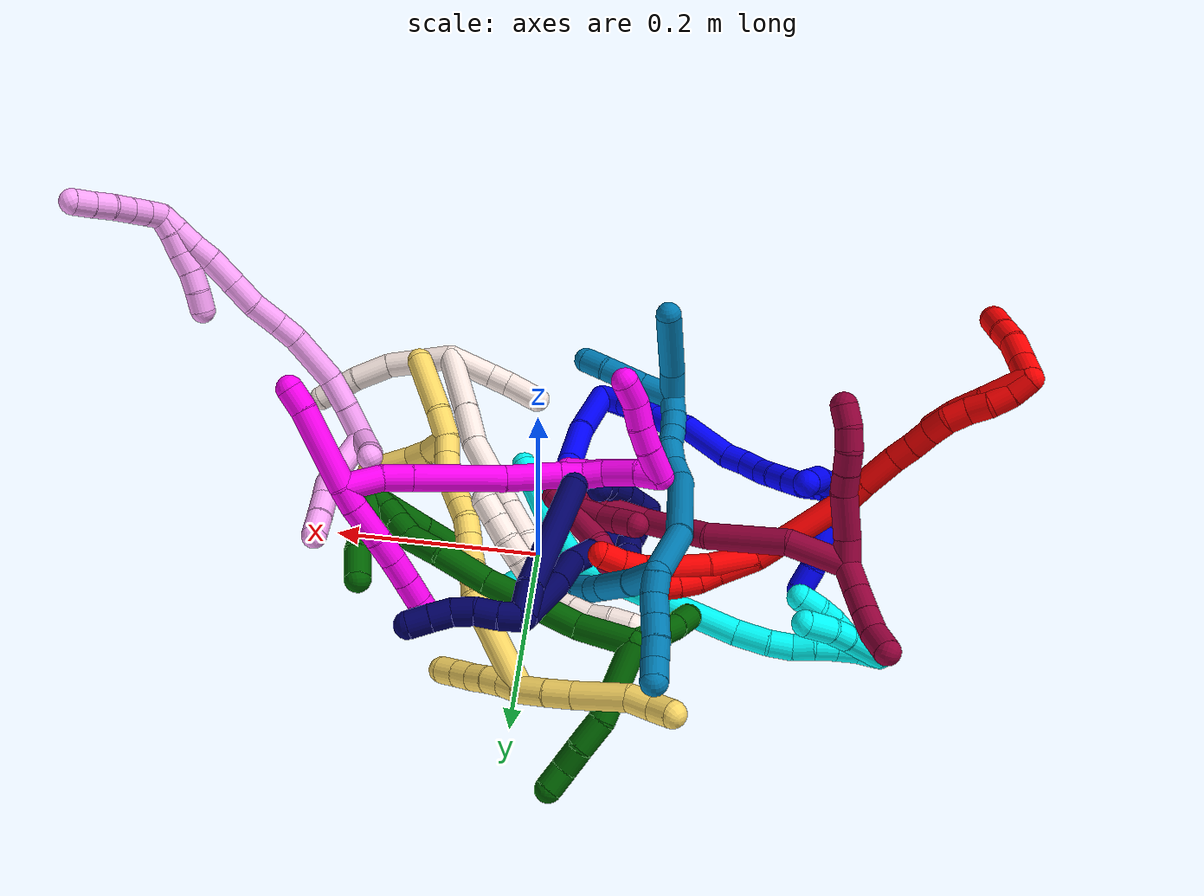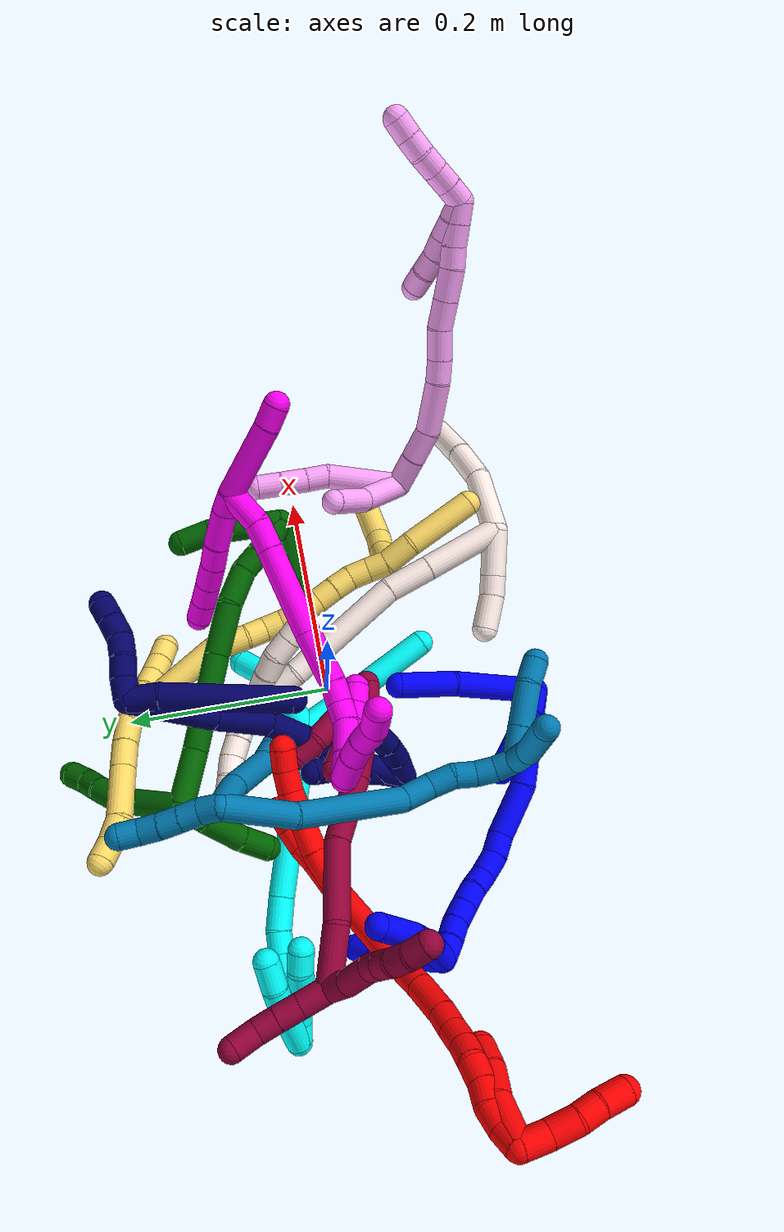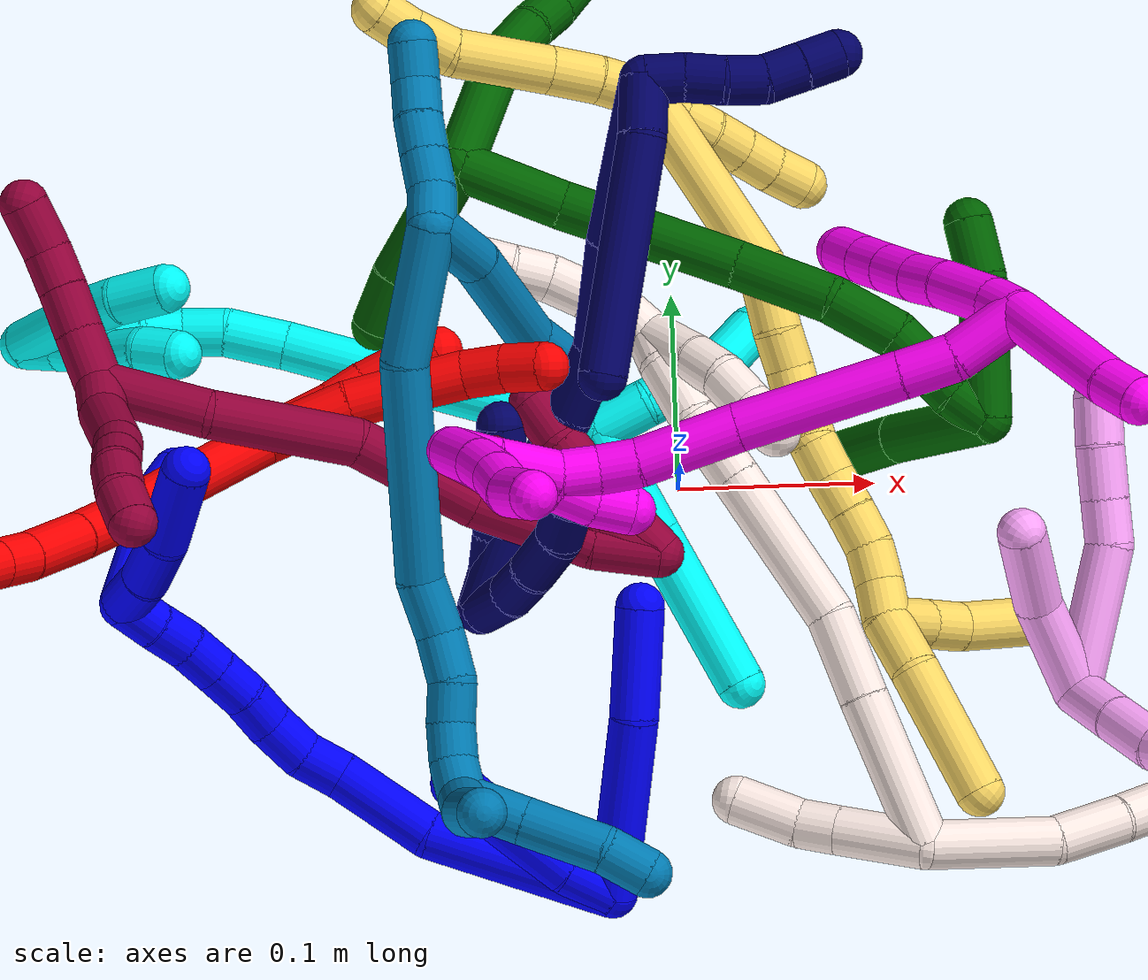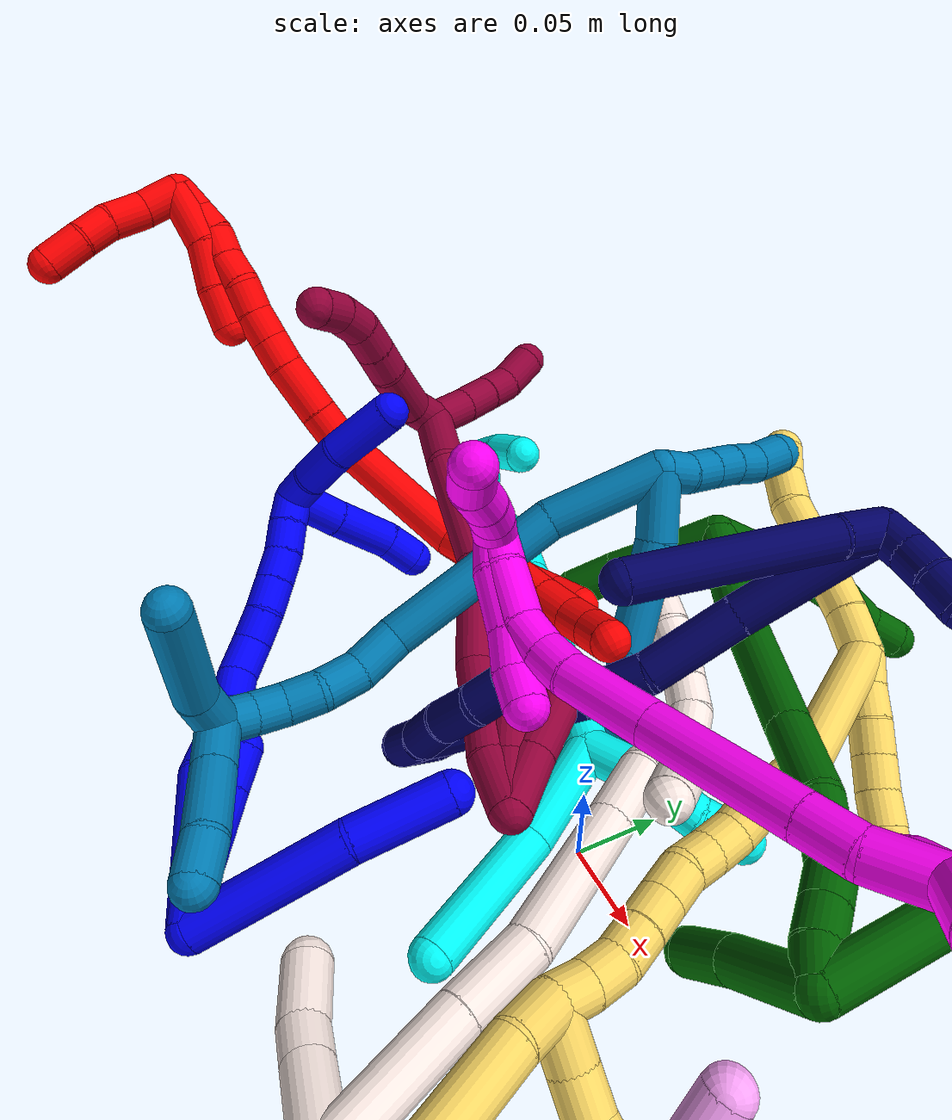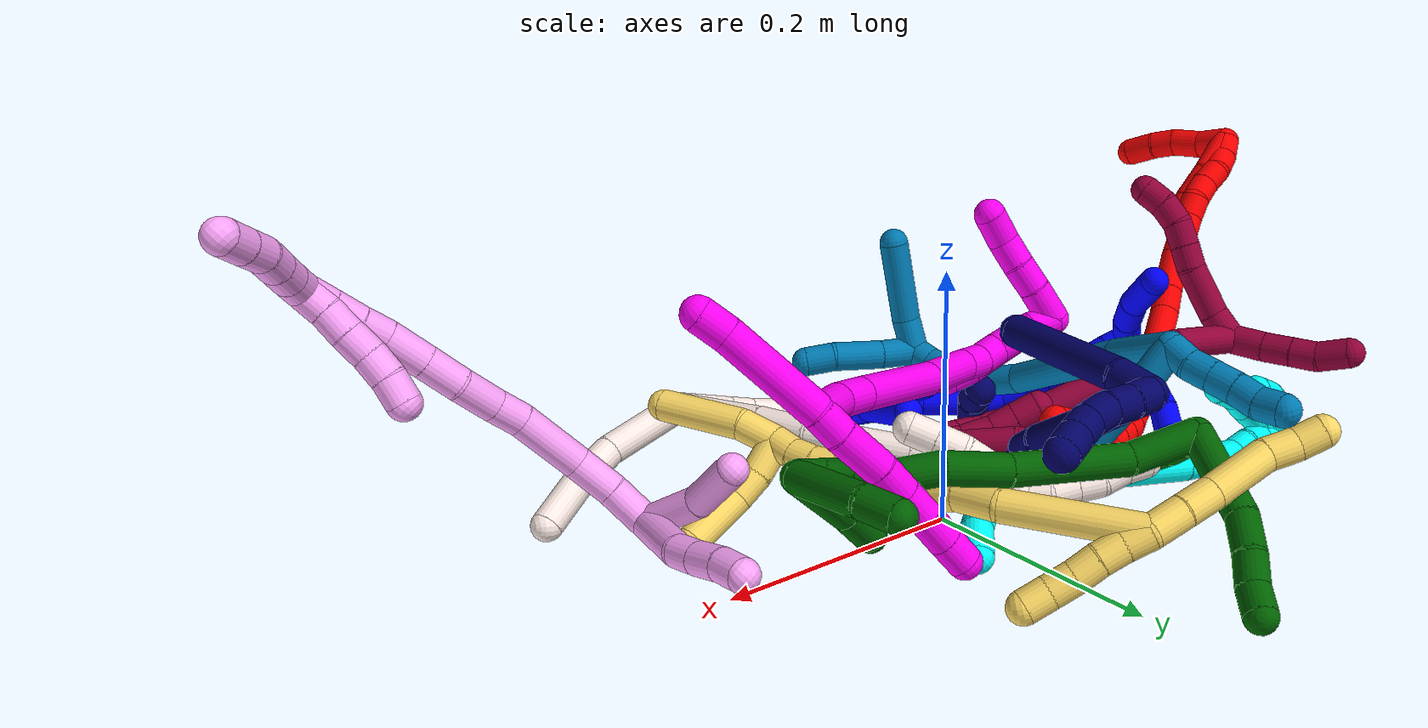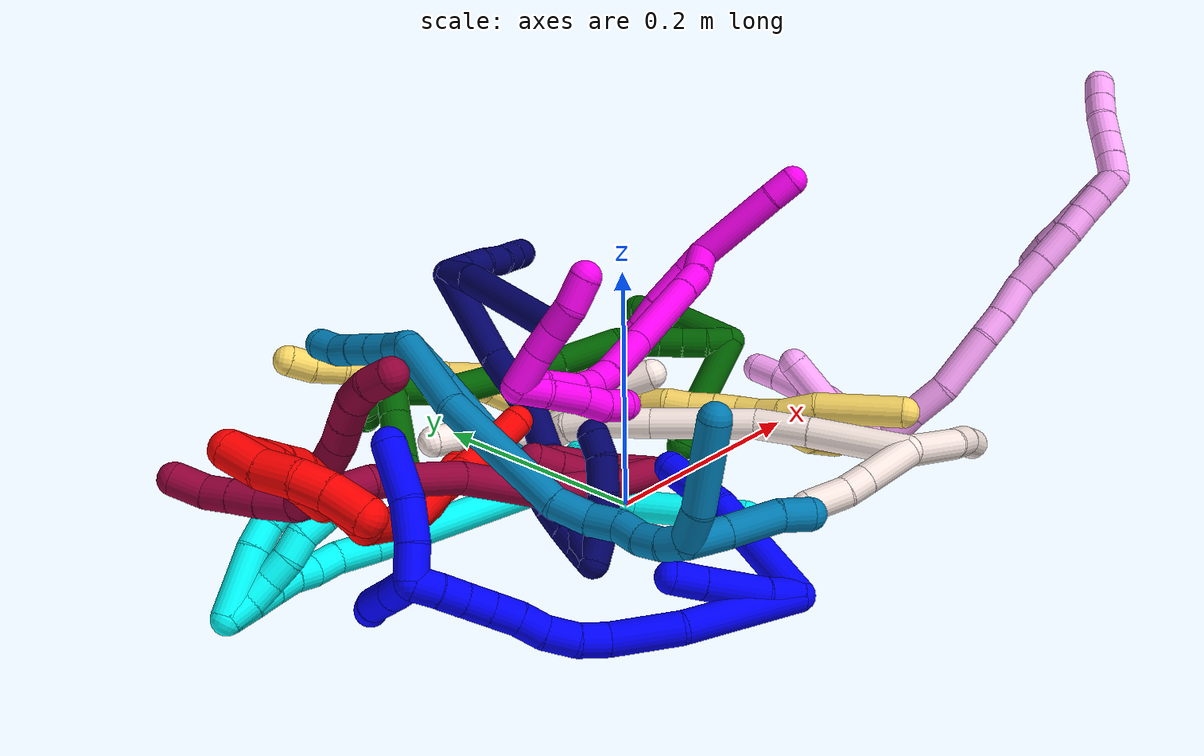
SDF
<sdf version="1.7">
 <world name="default">
  <plugin name="TubeGeneratorPlugin" filename="libtube_generator_plugin.so"/>
  <model name="photoneo_s_sensor">
   <static>1</static>
   <pose>0 0 2 1.57079 1.57079 3.14159</pose>
   <link name="link">
    <inertial><mass>0.1</mass></inertial>
    <sensor name="sensor" type="depth">
     <update_rate>30</update_rate>
     <camera>
      <horizontal_fov>1.22</horizontal_fov>
      <image><width>1920</width><height>1200</height><format>B8G8R8</format></image>
      <clip><near>0.1</near><far>4</far></clip>
      <depth_camera><output>points</output></depth_camera>
     </camera>
     <plugin name="camera_plugin" filename="libgazebo_ros_depth_camera.so">
      <baseline>0.2</baseline>
      <alwaysOn>1</alwaysOn>
      <updateRate>0.0</updateRate>
      <cameraName>camera_ir</cameraName>
      <imageTopicName>/camera/color/image_raw</imageTopicName>
      <cameraInfoTopicName>/camera/color/camera_info</cameraInfoTopicName>
      <depthImageTopicName>/camera/depth/image_raw</depthImageTopicName>
      <depthImageCameraInfoTopicName>/camera/depth/camera_info</depthImageCameraInfoTopicName>
      <pointCloudTopicName>/camera/depth/points</pointCloudTopicName>
      <frameName>fr_optical</frameName>
      <pointCloudCutoff>0.1</pointCloudCutoff>
      <pointCloudCutoffMax>2.0</pointCloudCutoffMax>
      <distortionK1>0</distortionK1>
      <distortionK2>0</distortionK2>
      <distortionK3>0</distortionK3>
      <distortionT1>0</distortionT1>
      <distortionT2>0</distortionT2>
      <CxPrime>0</CxPrime>
      <Cx>0</Cx>
      <Cy>0</Cy>
      <focalLength>0</focalLength>
      <hackBaseline>0</hackBaseline>
     </plugin>
    </sensor>
   </link>
  </model>
  <gravity>0 0 -9.8</gravity>
  <magnetic_field>6e-06 2.3e-05 -4.2e-05</magnetic_field>
  <atmosphere type="adiabatic"/>
  <physics name="default_physics" default="0" type="ode">
   <max_step_size>0.003</max_step_size>
   <real_time_factor>1</real_time_factor>
   <real_time_update_rate>1000</real_time_update_rate>
   <max_contacts>10000</max_contacts>
   <ode>
    <solver>
     <type>quick</type>
     <iters>100</iters>
     <sor>1.3</sor>
     <use_dynamic_moi_rescaling>0</use_dynamic_moi_rescaling>
    </solver>
    <constraints>
     <contact_max_correcting_vel>0</contact_max_correcting_vel>
     <contact_surface_layer>0.001</contact_surface_layer>
     <cfm>0</cfm>
     <erp>0.2</erp>
    </constraints>
   </ode>
  </physics>
  <scene><ambient>0.4 0.4 0.4 1</ambient><background>0.7 0.7 0.7 1</background><shadows>0</shadows></scene>
  <audio><device>default</device></audio>
  <spherical_coordinates>
   <surface_model>EARTH_WGS84</surface_model>
   <latitude_deg>0</latitude_deg>
   <longitude_deg>0</longitude_deg>
   <elevation>0</elevation>
   <heading_deg>0</heading_deg>
  </spherical_coordinates>
  <model name="bin">
   <static>1</static>
   <link name="bottom">
    <collision name="collision-bottom">
     <pose>0 0 -0.01 0 -0 0</pose>
     <geometry><box><size>0.8 0.6 0.02</size></box></geometry>
     <surface>
      <friction><ode><mu>100</mu><mu2>100</mu2></ode></friction>
      <contact><collide_bitmask>65535</collide_bitmask></contact>
     </surface>
    </collision>
   </link>
   <link name="west_wall">
    <collision name="collision-west_wall">
     <pose>-0.41 0 0.1 0 -0 0</pose>
     <geometry><box><size>0.02 0.6 0.2</size></box></geometry>
     <surface>
      <friction><ode><mu>100</mu><mu2>100</mu2></ode></friction>
      <contact><collide_bitmask>65535</collide_bitmask></contact>
     </surface>
    </collision>
   </link>
   <link name="east_wall">
    <collision name="collision-east_wall">
     <pose>0.41 0 0.1 0 -0 0</pose>
     <geometry><box><size>0.02 0.6 0.2</size></box></geometry>
     <surface>
      <friction><ode><mu>100</mu><mu2>100</mu2></ode></friction>
      <contact><collide_bitmask>65535</collide_bitmask></contact>
     </surface>
    </collision>
   </link>
   <link name="south_wall">
    <collision name="collision-south_wall">
     <pose>0 -0.31 0.1 0 -0 0</pose>
     <geometry><box><size>0.8 0.02 0.2</size></box></geometry>
     <surface>
      <friction><ode><mu>100</mu><mu2>100</mu2></ode></friction>
      <contact><collide_bitmask>65535</collide_bitmask></contact>
     </surface>
    </collision>
   </link>
   <link name="north_wall">
    <collision name="collision-north_wall">
     <pose>0 0.31 0.1 0 -0 0</pose>
     <geometry><box><size>0.8 0.02 0.2</size></box></geometry>
     <surface>
      <friction><ode><mu>100</mu><mu2>100</mu2></ode></friction>
      <contact><collide_bitmask>65535</collide_bitmask></contact>
     </surface>
    </collision>
   </link>
  </model>
  <model name="1">
   <static>0</static>
   <link name="1">
    <collision name="collision-cylinder-e_1_2_8">
     <pose>-0.02115 0.024298 0.03427 -0.616756 -0.466416 0.151038</pose>
     <geometry><cylinder><radius>0.0125</radius><length>0.094067</length></cylinder></geometry>
     <surface>
      <friction><ode><mu>1.16</mu><mu2>1.16</mu2><slip1>0</slip1><slip2>0</slip2></ode></friction>
      <contact><ode><kp>1e+06</kp><kd>1</kd><max_vel>0</max_vel><min_depth>0.001</min_depth></ode></contact>
     </surface>
    </collision>
    <visual name="visual-cylinder-e_1_2_8">
     <pose>-0.02115 0.024298 0.03427 -0.616756 -0.466416 0.151038</pose>
     <geometry><cylinder><radius>0.0125</radius><length>0.094067</length></cylinder></geometry>
     <material><ambient>0 0 1 1</ambient></material>
    </visual>
    <collision name="collision-cylinder-e_2_8_6">
     <pose>-0.05593 0.066986 0.084608 -0.852674 -0.509037 0.235237</pose>
     <geometry><cylinder><radius>0.0125</radius><length>0.055933</length></cylinder></geometry>
     <surface>
      <friction><ode><mu>1.16</mu><mu2>1.16</mu2><slip1>0</slip1><slip2>0</slip2></ode></friction>
      <contact><ode><kp>1e+06</kp><kd>1</kd><max_vel>0</max_vel><min_depth>0.001</min_depth></ode></contact>
     </surface>
    </collision>
    <visual name="visual-cylinder-e_2_8_6">
     <pose>-0.05593 0.066986 0.084608 -0.852674 -0.509037 0.235237</pose>
     <geometry><cylinder><radius>0.0125</radius><length>0.055933</length></cylinder></geometry>
     <material><ambient>0 0 1 1</ambient></material>
    </visual>
    <collision name="collision-cylinder-e_1_2_9">
     <pose>-0.013656 -0.001371 -0.000385 1.8443 -1.46691 -1.74285</pose>
     <geometry><cylinder><radius>0.0125</radius><length>0.02746</length></cylinder></geometry>
     <surface>
      <friction><ode><mu>1.16</mu><mu2>1.16</mu2><slip1>0</slip1><slip2>0</slip2></ode></friction>
      <contact><ode><kp>1e+06</kp><kd>1</kd><max_vel>0</max_vel><min_depth>0.001</min_depth></ode></contact>
     </surface>
    </collision>
    <visual name="visual-cylinder-e_1_2_9">
     <pose>-0.013656 -0.001371 -0.000385 1.8443 -1.46691 -1.74285</pose>
     <geometry><cylinder><radius>0.0125</radius><length>0.02746</length></cylinder></geometry>
     <material><ambient>0 0 1 1</ambient></material>
    </visual>
    <collision name="collision-cylinder-e_2_9_10">
     <pose>-0.05124 -0.001403 0.001635 -0.508058 -1.45631 0.454975</pose>
     <geometry><cylinder><radius>0.0125</radius><length>0.048172</length></cylinder></geometry>
     <surface>
      <friction><ode><mu>1.16</mu><mu2>1.16</mu2><slip1>0</slip1><slip2>0</slip2></ode></friction>
      <contact><ode><kp>1e+06</kp><kd>1</kd><max_vel>0</max_vel><min_depth>0.001</min_depth></ode></contact>
     </surface>
    </collision>
    <visual name="visual-cylinder-e_2_9_10">
     <pose>-0.05124 -0.001403 0.001635 -0.508058 -1.45631 0.454975</pose>
     <geometry><cylinder><radius>0.0125</radius><length>0.048172</length></cylinder></geometry>
     <material><ambient>0 0 1 1</ambient></material>
    </visual>
    <collision name="collision-cylinder-e_3_10_5">
     <pose>-0.087231 0.000769 0.005538 -0.507537 -1.42952 0.442785</pose>
     <geometry><cylinder><radius>0.0125</radius><length>0.024368</length></cylinder></geometry>
     <surface>
      <friction><ode><mu>1.16</mu><mu2>1.16</mu2><slip1>0</slip1><slip2>0</slip2></ode></friction>
      <contact><ode><kp>1e+06</kp><kd>1</kd><max_vel>0</max_vel><min_depth>0.001</min_depth></ode></contact>
     </surface>
    </collision>
    <visual name="visual-cylinder-e_3_10_5">
     <pose>-0.087231 0.000769 0.005538 -0.507537 -1.42952 0.442785</pose>
     <geometry><cylinder><radius>0.0125</radius><length>0.024368</length></cylinder></geometry>
     <material><ambient>0 0 1 1</ambient></material>
    </visual>
    <collision name="collision-cylinder-e_1_2_11">
     <pose>-0.046538 -0.003151 -0.014506 2.9277 -1.26203 -2.84982</pose>
     <geometry><cylinder><radius>0.0125</radius><length>0.097696</length></cylinder></geometry>
     <surface>
      <friction><ode><mu>1.16</mu><mu2>1.16</mu2><slip1>0</slip1><slip2>0</slip2></ode></friction>
      <contact><ode><kp>1e+06</kp><kd>1</kd><max_vel>0</max_vel><min_depth>0.001</min_depth></ode></contact>
     </surface>
    </collision>
    <visual name="visual-cylinder-e_1_2_11">
     <pose>-0.046538 -0.003151 -0.014506 2.9277 -1.26203 -2.84982</pose>
     <geometry><cylinder><radius>0.0125</radius><length>0.097696</length></cylinder></geometry>
     <material><ambient>0 0 1 1</ambient></material>
    </visual>
    <collision name="collision-cylinder-e_2_11_12">
     <pose>-0.118808 -0.000694 -0.034157 -2.31323 -1.28325 2.07782</pose>
     <geometry><cylinder><radius>0.0125</radius><length>0.053668</length></cylinder></geometry>
     <surface>
      <friction><ode><mu>1.16</mu><mu2>1.16</mu2><slip1>0</slip1><slip2>0</slip2></ode></friction>
      <contact><ode><kp>1e+06</kp><kd>1</kd><max_vel>0</max_vel><min_depth>0.001</min_depth></ode></contact>
     </surface>
    </collision>
    <visual name="visual-cylinder-e_2_11_12">
     <pose>-0.118808 -0.000694 -0.034157 -2.31323 -1.28325 2.07782</pose>
     <geometry><cylinder><radius>0.0125</radius><length>0.053668</length></cylinder></geometry>
     <material><ambient>0 0 1 1</ambient></material>
    </visual>
    <collision name="collision-cylinder-e_3_12_13">
     <pose>-0.155698 0.004797 -0.040125 3.00155 -1.49652 -2.99078</pose>
     <geometry><cylinder><radius>0.0125</radius><length>0.022377</length></cylinder></geometry>
     <surface>
      <friction><ode><mu>1.16</mu><mu2>1.16</mu2><slip1>0</slip1><slip2>0</slip2></ode></friction>
      <contact><ode><kp>1e+06</kp><kd>1</kd><max_vel>0</max_vel><min_depth>0.001</min_depth></ode></contact>
     </surface>
    </collision>
    <visual name="visual-cylinder-e_3_12_13">
     <pose>-0.155698 0.004797 -0.040125 3.00155 -1.49652 -2.99078</pose>
     <geometry><cylinder><radius>0.0125</radius><length>0.022377</length></cylinder></geometry>
     <material><ambient>0 0 1 1</ambient></material>
    </visual>
    <collision name="collision-cylinder-e_4_13_14">
     <pose>-0.178625 0.005947 -0.038751 -0.522915 -1.35865 0.425625</pose>
     <geometry><cylinder><radius>0.0125</radius><length>0.024077</length></cylinder></geometry>
     <surface>
      <friction><ode><mu>1.16</mu><mu2>1.16</mu2><slip1>0</slip1><slip2>0</slip2></ode></friction>
      <contact><ode><kp>1e+06</kp><kd>1</kd><max_vel>0</max_vel><min_depth>0.001</min_depth></ode></contact>
     </surface>
    </collision>
    <visual name="visual-cylinder-e_4_13_14">
     <pose>-0.178625 0.005947 -0.038751 -0.522915 -1.35865 0.425625</pose>
     <geometry><cylinder><radius>0.0125</radius><length>0.024077</length></cylinder></geometry>
     <material><ambient>0 0 1 1</ambient></material>
    </visual>
    <collision name="collision-cylinder-e_5_14_15">
     <pose>-0.199687 0.007415 -0.032357 -0.048131 -1.14611 0.031062</pose>
     <geometry><cylinder><radius>0.0125</radius><length>0.020399</length></cylinder></geometry>
     <surface>
      <friction><ode><mu>1.16</mu><mu2>1.16</mu2><slip1>0</slip1><slip2>0</slip2></ode></friction>
      <contact><ode><kp>1e+06</kp><kd>1</kd><max_vel>0</max_vel><min_depth>0.001</min_depth></ode></contact>
     </surface>
    </collision>
    <visual name="visual-cylinder-e_5_14_15">
     <pose>-0.199687 0.007415 -0.032357 -0.048131 -1.14611 0.031062</pose>
     <geometry><cylinder><radius>0.0125</radius><length>0.020399</length></cylinder></geometry>
     <material><ambient>0 0 1 1</ambient></material>
    </visual>
    <collision name="collision-cylinder-e_6_15_16">
     <pose>-0.219197 0.007587 -0.025391 0.011136 -1.30616 -0.00852</pose>
     <geometry><cylinder><radius>0.0125</radius><length>0.021169</length></cylinder></geometry>
     <surface>
      <friction><ode><mu>1.16</mu><mu2>1.16</mu2><slip1>0</slip1><slip2>0</slip2></ode></friction>
      <contact><ode><kp>1e+06</kp><kd>1</kd><max_vel>0</max_vel><min_depth>0.001</min_depth></ode></contact>
     </surface>
    </collision>
    <visual name="visual-cylinder-e_6_15_16">
     <pose>-0.219197 0.007587 -0.025391 0.011136 -1.30616 -0.00852</pose>
     <geometry><cylinder><radius>0.0125</radius><length>0.021169</length></cylinder></geometry>
     <material><ambient>0 0 1 1</ambient></material>
    </visual>
    <collision name="collision-cylinder-e_7_16_17">
     <pose>-0.239279 0.007384 -0.020008 0.0658 -1.31119 -0.050613</pose>
     <geometry><cylinder><radius>0.0125</radius><length>0.020415</length></cylinder></geometry>
     <surface>
      <friction><ode><mu>1.16</mu><mu2>1.16</mu2><slip1>0</slip1><slip2>0</slip2></ode></friction>
      <contact><ode><kp>1e+06</kp><kd>1</kd><max_vel>0</max_vel><min_depth>0.001</min_depth></ode></contact>
     </surface>
    </collision>
    <visual name="visual-cylinder-e_7_16_17">
     <pose>-0.239279 0.007384 -0.020008 0.0658 -1.31119 -0.050613</pose>
     <geometry><cylinder><radius>0.0125</radius><length>0.020415</length></cylinder></geometry>
     <material><ambient>0 0 1 1</ambient></material>
    </visual>
    <collision name="collision-cylinder-e_8_17_18">
     <pose>-0.258773 0.005521 -0.015037 0.622413 -1.27827 -0.469307</pose>
     <geometry><cylinder><radius>0.0125</radius><length>0.020112</length></cylinder></geometry>
     <surface>
      <friction><ode><mu>1.16</mu><mu2>1.16</mu2><slip1>0</slip1><slip2>0</slip2></ode></friction>
      <contact><ode><kp>1e+06</kp><kd>1</kd><max_vel>0</max_vel><min_depth>0.001</min_depth></ode></contact>
     </surface>
    </collision>
    <visual name="visual-cylinder-e_8_17_18">
     <pose>-0.258773 0.005521 -0.015037 0.622413 -1.27827 -0.469307</pose>
     <geometry><cylinder><radius>0.0125</radius><length>0.020112</length></cylinder></geometry>
     <material><ambient>0 0 1 1</ambient></material>
    </visual>
    <collision name="collision-cylinder-e_9_18_1">
     <pose>-0.278207 0.002979 -0.010683 0.402589 -1.35282 -0.324728</pose>
     <geometry><cylinder><radius>0.0125</radius><length>0.020085</length></cylinder></geometry>
     <surface>
      <friction><ode><mu>1.16</mu><mu2>1.16</mu2><slip1>0</slip1><slip2>0</slip2></ode></friction>
      <contact><ode><kp>1e+06</kp><kd>1</kd><max_vel>0</max_vel><min_depth>0.001</min_depth></ode></contact>
     </surface>
    </collision>
    <visual name="visual-cylinder-e_9_18_1">
     <pose>-0.278207 0.002979 -0.010683 0.402589 -1.35282 -0.324728</pose>
     <geometry><cylinder><radius>0.0125</radius><length>0.020085</length></cylinder></geometry>
     <material><ambient>0 0 1 1</ambient></material>
    </visual>
    <collision name="collision-cylinder-e_1_1_19">
     <pose>-0.289235 0.019149 -0.010914 -1.701 -0.071151 0.081065</pose>
     <geometry><cylinder><radius>0.0125</radius><length>0.034418</length></cylinder></geometry>
     <surface>
      <friction><ode><mu>1.16</mu><mu2>1.16</mu2><slip1>0</slip1><slip2>0</slip2></ode></friction>
      <contact><ode><kp>1e+06</kp><kd>1</kd><max_vel>0</max_vel><min_depth>0.001</min_depth></ode></contact>
     </surface>
    </collision>
    <visual name="visual-cylinder-e_1_1_19">
     <pose>-0.289235 0.019149 -0.010914 -1.701 -0.071151 0.081065</pose>
     <geometry><cylinder><radius>0.0125</radius><length>0.034418</length></cylinder></geometry>
     <material><ambient>0 0 1 1</ambient></material>
    </visual>
    <collision name="collision-cylinder-e_2_19_20">
     <pose>-0.292683 0.057139 -0.015422 -1.67906 -0.105052 0.117063</pose>
     <geometry><cylinder><radius>0.0125</radius><length>0.042421</length></cylinder></geometry>
     <surface>
      <friction><ode><mu>1.16</mu><mu2>1.16</mu2><slip1>0</slip1><slip2>0</slip2></ode></friction>
      <contact><ode><kp>1e+06</kp><kd>1</kd><max_vel>0</max_vel><min_depth>0.001</min_depth></ode></contact>
     </surface>
    </collision>
    <visual name="visual-cylinder-e_2_19_20">
     <pose>-0.292683 0.057139 -0.015422 -1.67906 -0.105052 0.117063</pose>
     <geometry><cylinder><radius>0.0125</radius><length>0.042421</length></cylinder></geometry>
     <material><ambient>0 0 1 1</ambient></material>
    </visual>
    <collision name="collision-cylinder-e_3_20_4">
     <pose>-0.293217 0.089534 -0.018552 -1.64513 0.146434 -0.1577</pose>
     <geometry><cylinder><radius>0.0125</radius><length>0.023161</length></cylinder></geometry>
     <surface>
      <friction><ode><mu>1.16</mu><mu2>1.16</mu2><slip1>0</slip1><slip2>0</slip2></ode></friction>
      <contact><ode><kp>1e+06</kp><kd>1</kd><max_vel>0</max_vel><min_depth>0.001</min_depth></ode></contact>
     </surface>
    </collision>
    <visual name="visual-cylinder-e_3_20_4">
     <pose>-0.293217 0.089534 -0.018552 -1.64513 0.146434 -0.1577</pose>
     <geometry><cylinder><radius>0.0125</radius><length>0.023161</length></cylinder></geometry>
     <material><ambient>0 0 1 1</ambient></material>
    </visual>
    <collision name="collision-cylinder-e_1_1_21">
     <pose>-0.288145 0.00201 0.004281 0.009153 -0.010241 -4.7e-05</pose>
     <geometry><cylinder><radius>0.0125</radius><length>0.025934</length></cylinder></geometry>
     <surface>
      <friction><ode><mu>1.16</mu><mu2>1.16</mu2><slip1>0</slip1><slip2>0</slip2></ode></friction>
      <contact><ode><kp>1e+06</kp><kd>1</kd><max_vel>0</max_vel><min_depth>0.001</min_depth></ode></contact>
     </surface>
    </collision>
    <visual name="visual-cylinder-e_1_1_21">
     <pose>-0.288145 0.00201 0.004281 0.009153 -0.010241 -4.7e-05</pose>
     <geometry><cylinder><radius>0.0125</radius><length>0.025934</length></cylinder></geometry>
     <material><ambient>0 0 1 1</ambient></material>
    </visual>
    <collision name="collision-cylinder-e_2_21_22">
     <pose>-0.290534 0.003548 0.031969 -0.112093 -0.151146 0.008496</pose>
     <geometry><cylinder><radius>0.0125</radius><length>0.029972</length></cylinder></geometry>
     <surface>
      <friction><ode><mu>1.16</mu><mu2>1.16</mu2><slip1>0</slip1><slip2>0</slip2></ode></friction>
      <contact><ode><kp>1e+06</kp><kd>1</kd><max_vel>0</max_vel><min_depth>0.001</min_depth></ode></contact>
     </surface>
    </collision>
    <visual name="visual-cylinder-e_2_21_22">
     <pose>-0.290534 0.003548 0.031969 -0.112093 -0.151146 0.008496</pose>
     <geometry><cylinder><radius>0.0125</radius><length>0.029972</length></cylinder></geometry>
     <material><ambient>0 0 1 1</ambient></material>
    </visual>
    <collision name="collision-cylinder-e_3_22_3">
     <pose>-0.298923 0.011338 0.066961 -0.293774 -0.281874 0.041976</pose>
     <geometry><cylinder><radius>0.0125</radius><length>0.044094</length></cylinder></geometry>
     <surface>
      <friction><ode><mu>1.16</mu><mu2>1.16</mu2><slip1>0</slip1><slip2>0</slip2></ode></friction>
      <contact><ode><kp>1e+06</kp><kd>1</kd><max_vel>0</max_vel><min_depth>0.001</min_depth></ode></contact>
     </surface>
    </collision>
    <visual name="visual-cylinder-e_3_22_3">
     <pose>-0.298923 0.011338 0.066961 -0.293774 -0.281874 0.041976</pose>
     <geometry><cylinder><radius>0.0125</radius><length>0.044094</length></cylinder></geometry>
     <material><ambient>0 0 1 1</ambient></material>
    </visual>
    <collision name="collision-sphere-3">
     <pose>-0.305056 0.01747 0.08723 0 -0 0</pose>
     <geometry><sphere><radius>0.0125</radius></sphere></geometry>
     <surface>
      <friction><ode><mu>1.16</mu><mu2>1.16</mu2><slip1>0</slip1><slip2>0</slip2></ode></friction>
      <contact><ode><kp>1e+06</kp><kd>1</kd><max_vel>0</max_vel><min_depth>0.001</min_depth></ode></contact>
     </surface>
    </collision>
    <visual name="visual-sphere-3">
     <pose>-0.305056 0.01747 0.08723 0 -0 0</pose>
     <geometry><sphere><radius>0.0125</radius></sphere></geometry>
     <material><ambient>0 0 1 1</ambient></material>
    </visual>
    <collision name="collision-sphere-22">
     <pose>-0.292791 0.005205 0.046691 0 -0 0</pose>
     <geometry><sphere><radius>0.0125</radius></sphere></geometry>
     <surface>
      <friction><ode><mu>1.16</mu><mu2>1.16</mu2><slip1>0</slip1><slip2>0</slip2></ode></friction>
      <contact><ode><kp>1e+06</kp><kd>1</kd><max_vel>0</max_vel><min_depth>0.001</min_depth></ode></contact>
     </surface>
    </collision>
    <visual name="visual-sphere-22">
     <pose>-0.292791 0.005205 0.046691 0 -0 0</pose>
     <geometry><sphere><radius>0.0125</radius></sphere></geometry>
     <material><ambient>0 0 1 1</ambient></material>
    </visual>
    <collision name="collision-sphere-21">
     <pose>-0.288278 0.001891 0.017246 0 -0 0</pose>
     <geometry><sphere><radius>0.0125</radius></sphere></geometry>
     <surface>
      <friction><ode><mu>1.16</mu><mu2>1.16</mu2><slip1>0</slip1><slip2>0</slip2></ode></friction>
      <contact><ode><kp>1e+06</kp><kd>1</kd><max_vel>0</max_vel><min_depth>0.001</min_depth></ode></contact>
     </surface>
    </collision>
    <visual name="visual-sphere-21">
     <pose>-0.288278 0.001891 0.017246 0 -0 0</pose>
     <geometry><sphere><radius>0.0125</radius></sphere></geometry>
     <material><ambient>0 0 1 1</ambient></material>
    </visual>
    <collision name="collision-sphere-4">
     <pose>-0.291528 0.100959 -0.019403 0 -0 0</pose>
     <geometry><sphere><radius>0.0125</radius></sphere></geometry>
     <surface>
      <friction><ode><mu>1.16</mu><mu2>1.16</mu2><slip1>0</slip1><slip2>0</slip2></ode></friction>
      <contact><ode><kp>1e+06</kp><kd>1</kd><max_vel>0</max_vel><min_depth>0.001</min_depth></ode></contact>
     </surface>
    </collision>
    <visual name="visual-sphere-4">
     <pose>-0.291528 0.100959 -0.019403 0 -0 0</pose>
     <geometry><sphere><radius>0.0125</radius></sphere></geometry>
     <material><ambient>0 0 1 1</ambient></material>
    </visual>
    <collision name="collision-sphere-20">
     <pose>-0.294907 0.078109 -0.017701 0 -0 0</pose>
     <geometry><sphere><radius>0.0125</radius></sphere></geometry>
     <surface>
      <friction><ode><mu>1.16</mu><mu2>1.16</mu2><slip1>0</slip1><slip2>0</slip2></ode></friction>
      <contact><ode><kp>1e+06</kp><kd>1</kd><max_vel>0</max_vel><min_depth>0.001</min_depth></ode></contact>
     </surface>
    </collision>
    <visual name="visual-sphere-20">
     <pose>-0.294907 0.078109 -0.017701 0 -0 0</pose>
     <geometry><sphere><radius>0.0125</radius></sphere></geometry>
     <material><ambient>0 0 1 1</ambient></material>
    </visual>
    <collision name="collision-sphere-5">
     <pose>-0.099294 0.001603 0.007037 0 -0 0</pose>
     <geometry><sphere><radius>0.0125</radius></sphere></geometry>
     <surface>
      <friction><ode><mu>1.16</mu><mu2>1.16</mu2><slip1>0</slip1><slip2>0</slip2></ode></friction>
      <contact><ode><kp>1e+06</kp><kd>1</kd><max_vel>0</max_vel><min_depth>0.001</min_depth></ode></contact>
     </surface>
    </collision>
    <visual name="visual-sphere-5">
     <pose>-0.099294 0.001603 0.007037 0 -0 0</pose>
     <geometry><sphere><radius>0.0125</radius></sphere></geometry>
     <material><ambient>0 0 1 1</ambient></material>
    </visual>
    <collision name="collision-sphere-10">
     <pose>-0.075169 -6.5e-05 0.004039 0 -0 0</pose>
     <geometry><sphere><radius>0.0125</radius></sphere></geometry>
     <surface>
      <friction><ode><mu>1.16</mu><mu2>1.16</mu2><slip1>0</slip1><slip2>0</slip2></ode></friction>
      <contact><ode><kp>1e+06</kp><kd>1</kd><max_vel>0</max_vel><min_depth>0.001</min_depth></ode></contact>
     </surface>
    </collision>
    <visual name="visual-sphere-10">
     <pose>-0.075169 -6.5e-05 0.004039 0 -0 0</pose>
     <geometry><sphere><radius>0.0125</radius></sphere></geometry>
     <material><ambient>0 0 1 1</ambient></material>
    </visual>
    <collision name="collision-sphere-6">
     <pose>-0.069559 0.085376 0.100676 0 -0 0</pose>
     <geometry><sphere><radius>0.0125</radius></sphere></geometry>
     <surface>
      <friction><ode><mu>1.16</mu><mu2>1.16</mu2><slip1>0</slip1><slip2>0</slip2></ode></friction>
      <contact><ode><kp>1e+06</kp><kd>1</kd><max_vel>0</max_vel><min_depth>0.001</min_depth></ode></contact>
     </surface>
    </collision>
    <visual name="visual-sphere-6">
     <pose>-0.069559 0.085376 0.100676 0 -0 0</pose>
     <geometry><sphere><radius>0.0125</radius></sphere></geometry>
     <material><ambient>0 0 1 1</ambient></material>
    </visual>
    <collision name="collision-sphere-9">
     <pose>-0.027312 -0.002742 -0.000769 0 -0 0</pose>
     <geometry><sphere><radius>0.0125</radius></sphere></geometry>
     <surface>
      <friction><ode><mu>1.16</mu><mu2>1.16</mu2><slip1>0</slip1><slip2>0</slip2></ode></friction>
      <contact><ode><kp>1e+06</kp><kd>1</kd><max_vel>0</max_vel><min_depth>0.001</min_depth></ode></contact>
     </surface>
    </collision>
    <visual name="visual-sphere-9">
     <pose>-0.027312 -0.002742 -0.000769 0 -0 0</pose>
     <geometry><sphere><radius>0.0125</radius></sphere></geometry>
     <material><ambient>0 0 1 1</ambient></material>
    </visual>
    <collision name="collision-sphere-2">
     <geometry><sphere><radius>0.0125</radius></sphere></geometry>
     <surface>
      <friction><ode><mu>1.16</mu><mu2>1.16</mu2><slip1>0</slip1><slip2>0</slip2></ode></friction>
      <contact><ode><kp>1e+06</kp><kd>1</kd><max_vel>0</max_vel><min_depth>0.001</min_depth></ode></contact>
     </surface>
    </collision>
    <visual name="visual-sphere-2">
     <geometry><sphere><radius>0.0125</radius></sphere></geometry>
     <material><ambient>0 0 1 1</ambient></material>
    </visual>
    <collision name="collision-sphere-19">
     <pose>-0.290459 0.036169 -0.013142 0 -0 0</pose>
     <geometry><sphere><radius>0.0125</radius></sphere></geometry>
     <surface>
      <friction><ode><mu>1.16</mu><mu2>1.16</mu2><slip1>0</slip1><slip2>0</slip2></ode></friction>
      <contact><ode><kp>1e+06</kp><kd>1</kd><max_vel>0</max_vel><min_depth>0.001</min_depth></ode></contact>
     </surface>
    </collision>
    <visual name="visual-sphere-19">
     <pose>-0.290459 0.036169 -0.013142 0 -0 0</pose>
     <geometry><sphere><radius>0.0125</radius></sphere></geometry>
     <material><ambient>0 0 1 1</ambient></material>
    </visual>
    <collision name="collision-sphere-8">
     <pose>-0.042301 0.048596 0.06854 0 -0 0</pose>
     <geometry><sphere><radius>0.0125</radius></sphere></geometry>
     <surface>
      <friction><ode><mu>1.16</mu><mu2>1.16</mu2><slip1>0</slip1><slip2>0</slip2></ode></friction>
      <contact><ode><kp>1e+06</kp><kd>1</kd><max_vel>0</max_vel><min_depth>0.001</min_depth></ode></contact>
     </surface>
    </collision>
    <visual name="visual-sphere-8">
     <pose>-0.042301 0.048596 0.06854 0 -0 0</pose>
     <geometry><sphere><radius>0.0125</radius></sphere></geometry>
     <material><ambient>0 0 1 1</ambient></material>
    </visual>
    <collision name="collision-sphere-11">
     <pose>-0.093076 -0.006302 -0.029012 0 -0 0</pose>
     <geometry><sphere><radius>0.0125</radius></sphere></geometry>
     <surface>
      <friction><ode><mu>1.16</mu><mu2>1.16</mu2><slip1>0</slip1><slip2>0</slip2></ode></friction>
      <contact><ode><kp>1e+06</kp><kd>1</kd><max_vel>0</max_vel><min_depth>0.001</min_depth></ode></contact>
     </surface>
    </collision>
    <visual name="visual-sphere-11">
     <pose>-0.093076 -0.006302 -0.029012 0 -0 0</pose>
     <geometry><sphere><radius>0.0125</radius></sphere></geometry>
     <material><ambient>0 0 1 1</ambient></material>
    </visual>
    <collision name="collision-sphere-12">
     <pose>-0.144541 0.004913 -0.039302 0 -0 0</pose>
     <geometry><sphere><radius>0.0125</radius></sphere></geometry>
     <surface>
      <friction><ode><mu>1.16</mu><mu2>1.16</mu2><slip1>0</slip1><slip2>0</slip2></ode></friction>
      <contact><ode><kp>1e+06</kp><kd>1</kd><max_vel>0</max_vel><min_depth>0.001</min_depth></ode></contact>
     </surface>
    </collision>
    <visual name="visual-sphere-12">
     <pose>-0.144541 0.004913 -0.039302 0 -0 0</pose>
     <geometry><sphere><radius>0.0125</radius></sphere></geometry>
     <material><ambient>0 0 1 1</ambient></material>
    </visual>
    <collision name="collision-sphere-13">
     <pose>-0.166856 0.004681 -0.040947 0 -0 0</pose>
     <geometry><sphere><radius>0.0125</radius></sphere></geometry>
     <surface>
      <friction><ode><mu>1.16</mu><mu2>1.16</mu2><slip1>0</slip1><slip2>0</slip2></ode></friction>
      <contact><ode><kp>1e+06</kp><kd>1</kd><max_vel>0</max_vel><min_depth>0.001</min_depth></ode></contact>
     </surface>
    </collision>
    <visual name="visual-sphere-13">
     <pose>-0.166856 0.004681 -0.040947 0 -0 0</pose>
     <geometry><sphere><radius>0.0125</radius></sphere></geometry>
     <material><ambient>0 0 1 1</ambient></material>
    </visual>
    <collision name="collision-sphere-14">
     <pose>-0.190394 0.007213 -0.036554 0 -0 0</pose>
     <geometry><sphere><radius>0.0125</radius></sphere></geometry>
     <surface>
      <friction><ode><mu>1.16</mu><mu2>1.16</mu2><slip1>0</slip1><slip2>0</slip2></ode></friction>
      <contact><ode><kp>1e+06</kp><kd>1</kd><max_vel>0</max_vel><min_depth>0.001</min_depth></ode></contact>
     </surface>
    </collision>
    <visual name="visual-sphere-14">
     <pose>-0.190394 0.007213 -0.036554 0 -0 0</pose>
     <geometry><sphere><radius>0.0125</radius></sphere></geometry>
     <material><ambient>0 0 1 1</ambient></material>
    </visual>
    <collision name="collision-sphere-15">
     <pose>-0.208981 0.007617 -0.028159 0 -0 0</pose>
     <geometry><sphere><radius>0.0125</radius></sphere></geometry>
     <surface>
      <friction><ode><mu>1.16</mu><mu2>1.16</mu2><slip1>0</slip1><slip2>0</slip2></ode></friction>
      <contact><ode><kp>1e+06</kp><kd>1</kd><max_vel>0</max_vel><min_depth>0.001</min_depth></ode></contact>
     </surface>
    </collision>
    <visual name="visual-sphere-15">
     <pose>-0.208981 0.007617 -0.028159 0 -0 0</pose>
     <geometry><sphere><radius>0.0125</radius></sphere></geometry>
     <material><ambient>0 0 1 1</ambient></material>
    </visual>
    <collision name="collision-sphere-16">
     <pose>-0.229413 0.007556 -0.022622 0 -0 0</pose>
     <geometry><sphere><radius>0.0125</radius></sphere></geometry>
     <surface>
      <friction><ode><mu>1.16</mu><mu2>1.16</mu2><slip1>0</slip1><slip2>0</slip2></ode></friction>
      <contact><ode><kp>1e+06</kp><kd>1</kd><max_vel>0</max_vel><min_depth>0.001</min_depth></ode></contact>
     </surface>
    </collision>
    <visual name="visual-sphere-16">
     <pose>-0.229413 0.007556 -0.022622 0 -0 0</pose>
     <geometry><sphere><radius>0.0125</radius></sphere></geometry>
     <material><ambient>0 0 1 1</ambient></material>
    </visual>
    <collision name="collision-sphere-17">
     <pose>-0.249145 0.007211 -0.017393 0 -0 0</pose>
     <geometry><sphere><radius>0.0125</radius></sphere></geometry>
     <surface>
      <friction><ode><mu>1.16</mu><mu2>1.16</mu2><slip1>0</slip1><slip2>0</slip2></ode></friction>
      <contact><ode><kp>1e+06</kp><kd>1</kd><max_vel>0</max_vel><min_depth>0.001</min_depth></ode></contact>
     </surface>
    </collision>
    <visual name="visual-sphere-17">
     <pose>-0.249145 0.007211 -0.017393 0 -0 0</pose>
     <geometry><sphere><radius>0.0125</radius></sphere></geometry>
     <material><ambient>0 0 1 1</ambient></material>
    </visual>
    <collision name="collision-sphere-18">
     <pose>-0.268402 0.00383 -0.012681 0 -0 0</pose>
     <geometry><sphere><radius>0.0125</radius></sphere></geometry>
     <surface>
      <friction><ode><mu>1.16</mu><mu2>1.16</mu2><slip1>0</slip1><slip2>0</slip2></ode></friction>
      <contact><ode><kp>1e+06</kp><kd>1</kd><max_vel>0</max_vel><min_depth>0.001</min_depth></ode></contact>
     </surface>
    </collision>
    <visual name="visual-sphere-18">
     <pose>-0.268402 0.00383 -0.012681 0 -0 0</pose>
     <geometry><sphere><radius>0.0125</radius></sphere></geometry>
     <material><ambient>0 0 1 1</ambient></material>
    </visual>
    <collision name="collision-sphere-1">
     <pose>-0.288012 0.002128 -0.008685 0 -0 0</pose>
     <geometry><sphere><radius>0.0125</radius></sphere></geometry>
     <surface>
      <friction><ode><mu>1.16</mu><mu2>1.16</mu2><slip1>0</slip1><slip2>0</slip2></ode></friction>
      <contact><ode><kp>1e+06</kp><kd>1</kd><max_vel>0</max_vel><min_depth>0.001</min_depth></ode></contact>
     </surface>
    </collision>
    <visual name="visual-sphere-1">
     <pose>-0.288012 0.002128 -0.008685 0 -0 0</pose>
     <geometry><sphere><radius>0.0125</radius></sphere></geometry>
     <material><ambient>0 0 1 1</ambient></material>
    </visual>
    <inertial>
     <pose>-0.148945 0.0164 0.00469 0 -0 0</pose>
     <mass>0.75</mass>
     <inertia><ixx>6e-05</ixx><ixy>0</ixy><ixz>0</ixz><iyy>0.000237</iyy><iyz>0</iyz><izz>0.000114</izz></inertia>
    </inertial>
   </link>
   <pose>-0.040365 -0.205832 0.012251 -0.593555 0.241349 -0.566266</pose>
  </model>
  <model name="2">
   <static>0</static>
   <link name="2">
    <collision name="collision-cylinder-e_1_2_8">
     <pose>0.011618 0.006539 -0.019051 -2.81095 0.523194 -2.02703</pose>
     <geometry><cylinder><radius>0.0125</radius><length>0.046506</length></cylinder></geometry>
     <surface>
      <friction><ode><mu>1.16</mu><mu2>1.16</mu2><slip1>0</slip1><slip2>0</slip2></ode></friction>
      <contact><ode><kp>1e+06</kp><kd>1</kd><max_vel>0</max_vel><min_depth>0.001</min_depth></ode></contact>
     </surface>
    </collision>
    <visual name="visual-cylinder-e_1_2_8">
     <pose>0.011618 0.006539 -0.019051 -2.81095 0.523194 -2.02703</pose>
     <geometry><cylinder><radius>0.0125</radius><length>0.046506</length></cylinder></geometry>
     <material><ambient>1 0 0 1</ambient></material>
    </visual>
    <collision name="collision-cylinder-e_2_8_9">
     <pose>0.032212 0.015553 -0.053311 -2.98028 0.52748 -2.55987</pose>
     <geometry><cylinder><radius>0.0125</radius><length>0.035664</length></cylinder></geometry>
     <surface>
      <friction><ode><mu>1.16</mu><mu2>1.16</mu2><slip1>0</slip1><slip2>0</slip2></ode></friction>
      <contact><ode><kp>1e+06</kp><kd>1</kd><max_vel>0</max_vel><min_depth>0.001</min_depth></ode></contact>
     </surface>
    </collision>
    <visual name="visual-cylinder-e_2_8_9">
     <pose>0.032212 0.015553 -0.053311 -2.98028 0.52748 -2.55987</pose>
     <geometry><cylinder><radius>0.0125</radius><length>0.035664</length></cylinder></geometry>
     <material><ambient>1 0 0 1</ambient></material>
    </visual>
    <collision name="collision-cylinder-e_3_9_10">
     <pose>0.048698 0.019267 -0.078657 -3.01998 0.634011 -2.77463</pose>
     <geometry><cylinder><radius>0.0125</radius><length>0.025356</length></cylinder></geometry>
     <surface>
      <friction><ode><mu>1.16</mu><mu2>1.16</mu2><slip1>0</slip1><slip2>0</slip2></ode></friction>
      <contact><ode><kp>1e+06</kp><kd>1</kd><max_vel>0</max_vel><min_depth>0.001</min_depth></ode></contact>
     </surface>
    </collision>
    <visual name="visual-cylinder-e_3_9_10">
     <pose>0.048698 0.019267 -0.078657 -3.01998 0.634011 -2.77463</pose>
     <geometry><cylinder><radius>0.0125</radius><length>0.025356</length></cylinder></geometry>
     <material><ambient>1 0 0 1</ambient></material>
    </visual>
    <collision name="collision-cylinder-e_4_10_11">
     <pose>0.064134 0.020376 -0.096093 3.12376 0.826591 3.10093</pose>
     <geometry><cylinder><radius>0.0125</radius><length>0.021546</length></cylinder></geometry>
     <surface>
      <friction><ode><mu>1.16</mu><mu2>1.16</mu2><slip1>0</slip1><slip2>0</slip2></ode></friction>
      <contact><ode><kp>1e+06</kp><kd>1</kd><max_vel>0</max_vel><min_depth>0.001</min_depth></ode></contact>
     </surface>
    </collision>
    <visual name="visual-cylinder-e_4_10_11">
     <pose>0.064134 0.020376 -0.096093 3.12376 0.826591 3.10093</pose>
     <geometry><cylinder><radius>0.0125</radius><length>0.021546</length></cylinder></geometry>
     <material><ambient>1 0 0 1</ambient></material>
    </visual>
    <collision name="collision-cylinder-e_5_11_6">
     <pose>0.080381 0.019 -0.109609 2.94392 0.91947 2.74627</pose>
     <geometry><cylinder><radius>0.0125</radius><length>0.020928</length></cylinder></geometry>
     <surface>
      <friction><ode><mu>1.16</mu><mu2>1.16</mu2><slip1>0</slip1><slip2>0</slip2></ode></friction>
      <contact><ode><kp>1e+06</kp><kd>1</kd><max_vel>0</max_vel><min_depth>0.001</min_depth></ode></contact>
     </surface>
    </collision>
    <visual name="visual-cylinder-e_5_11_6">
     <pose>0.080381 0.019 -0.109609 2.94392 0.91947 2.74627</pose>
     <geometry><cylinder><radius>0.0125</radius><length>0.020928</length></cylinder></geometry>
     <material><ambient>1 0 0 1</ambient></material>
    </visual>
    <collision name="collision-cylinder-e_1_2_12">
     <pose>0.006375 0.007087 -0.017388 -2.75458 0.327313 -1.40048</pose>
     <geometry><cylinder><radius>0.0125</radius><length>0.039658</length></cylinder></geometry>
     <surface>
      <friction><ode><mu>1.16</mu><mu2>1.16</mu2><slip1>0</slip1><slip2>0</slip2></ode></friction>
      <contact><ode><kp>1e+06</kp><kd>1</kd><max_vel>0</max_vel><min_depth>0.001</min_depth></ode></contact>
     </surface>
    </collision>
    <visual name="visual-cylinder-e_1_2_12">
     <pose>0.006375 0.007087 -0.017388 -2.75458 0.327313 -1.40048</pose>
     <geometry><cylinder><radius>0.0125</radius><length>0.039658</length></cylinder></geometry>
     <material><ambient>1 0 0 1</ambient></material>
    </visual>
    <collision name="collision-cylinder-e_2_12_13">
     <pose>0.016215 0.018627 -0.043059 -2.64828 0.352957 -1.23252</pose>
     <geometry><cylinder><radius>0.0125</radius><length>0.020046</length></cylinder></geometry>
     <surface>
      <friction><ode><mu>1.16</mu><mu2>1.16</mu2><slip1>0</slip1><slip2>0</slip2></ode></friction>
      <contact><ode><kp>1e+06</kp><kd>1</kd><max_vel>0</max_vel><min_depth>0.001</min_depth></ode></contact>
     </surface>
    </collision>
    <visual name="visual-cylinder-e_2_12_13">
     <pose>0.016215 0.018627 -0.043059 -2.64828 0.352957 -1.23252</pose>
     <geometry><cylinder><radius>0.0125</radius><length>0.020046</length></cylinder></geometry>
     <material><ambient>1 0 0 1</ambient></material>
    </visual>
    <collision name="collision-cylinder-e_3_13_14">
     <pose>0.025063 0.026432 -0.059179 -2.73748 0.563371 -1.90959</pose>
     <geometry><cylinder><radius>0.0125</radius><length>0.020163</length></cylinder></geometry>
     <surface>
      <friction><ode><mu>1.16</mu><mu2>1.16</mu2><slip1>0</slip1><slip2>0</slip2></ode></friction>
      <contact><ode><kp>1e+06</kp><kd>1</kd><max_vel>0</max_vel><min_depth>0.001</min_depth></ode></contact>
     </surface>
    </collision>
    <visual name="visual-cylinder-e_3_13_14">
     <pose>0.025063 0.026432 -0.059179 -2.73748 0.563371 -1.90959</pose>
     <geometry><cylinder><radius>0.0125</radius><length>0.020163</length></cylinder></geometry>
     <material><ambient>1 0 0 1</ambient></material>
    </visual>
    <collision name="collision-cylinder-e_4_14_5">
     <pose>0.036196 0.032626 -0.074775 -2.79043 0.607867 -2.11208</pose>
     <geometry><cylinder><radius>0.0125</radius><length>0.020133</length></cylinder></geometry>
     <surface>
      <friction><ode><mu>1.16</mu><mu2>1.16</mu2><slip1>0</slip1><slip2>0</slip2></ode></friction>
      <contact><ode><kp>1e+06</kp><kd>1</kd><max_vel>0</max_vel><min_depth>0.001</min_depth></ode></contact>
     </surface>
    </collision>
    <visual name="visual-cylinder-e_4_14_5">
     <pose>0.036196 0.032626 -0.074775 -2.79043 0.607867 -2.11208</pose>
     <geometry><cylinder><radius>0.0125</radius><length>0.020133</length></cylinder></geometry>
     <material><ambient>1 0 0 1</ambient></material>
    </visual>
    <collision name="collision-cylinder-e_1_2_15">
     <pose>-0.001342 -0.018588 0.045626 0.386874 -0.027223 -0.005333</pose>
     <geometry><cylinder><radius>0.0125</radius><length>0.098571</length></cylinder></geometry>
     <surface>
      <friction><ode><mu>1.16</mu><mu2>1.16</mu2><slip1>0</slip1><slip2>0</slip2></ode></friction>
      <contact><ode><kp>1e+06</kp><kd>1</kd><max_vel>0</max_vel><min_depth>0.001</min_depth></ode></contact>
     </surface>
    </collision>
    <visual name="visual-cylinder-e_1_2_15">
     <pose>-0.001342 -0.018588 0.045626 0.386874 -0.027223 -0.005333</pose>
     <geometry><cylinder><radius>0.0125</radius><length>0.098571</length></cylinder></geometry>
     <material><ambient>1 0 0 1</ambient></material>
    </visual>
    <collision name="collision-cylinder-e_2_15_16">
     <pose>0.000855 -0.04073 0.101699 0.327815 0.310249 0.051716</pose>
     <geometry><cylinder><radius>0.0125</radius><length>0.023175</length></cylinder></geometry>
     <surface>
      <friction><ode><mu>1.16</mu><mu2>1.16</mu2><slip1>0</slip1><slip2>0</slip2></ode></friction>
      <contact><ode><kp>1e+06</kp><kd>1</kd><max_vel>0</max_vel><min_depth>0.001</min_depth></ode></contact>
     </surface>
    </collision>
    <visual name="visual-cylinder-e_2_15_16">
     <pose>0.000855 -0.04073 0.101699 0.327815 0.310249 0.051716</pose>
     <geometry><cylinder><radius>0.0125</radius><length>0.023175</length></cylinder></geometry>
     <material><ambient>1 0 0 1</ambient></material>
    </visual>
    <collision name="collision-cylinder-e_3_16_17">
     <pose>0.009189 -0.049278 0.129237 0.284381 0.263136 0.037884</pose>
     <geometry><cylinder><radius>0.0125</radius><length>0.036882</length></cylinder></geometry>
     <surface>
      <friction><ode><mu>1.16</mu><mu2>1.16</mu2><slip1>0</slip1><slip2>0</slip2></ode></friction>
      <contact><ode><kp>1e+06</kp><kd>1</kd><max_vel>0</max_vel><min_depth>0.001</min_depth></ode></contact>
     </surface>
    </collision>
    <visual name="visual-cylinder-e_3_16_17">
     <pose>0.009189 -0.049278 0.129237 0.284381 0.263136 0.037884</pose>
     <geometry><cylinder><radius>0.0125</radius><length>0.036882</length></cylinder></geometry>
     <material><ambient>1 0 0 1</ambient></material>
    </visual>
    <collision name="collision-cylinder-e_4_17_18">
     <pose>0.016632 -0.055971 0.156117 0.171704 0.260379 0.022536</pose>
     <geometry><cylinder><radius>0.0125</radius><length>0.020562</length></cylinder></geometry>
     <surface>
      <friction><ode><mu>1.16</mu><mu2>1.16</mu2><slip1>0</slip1><slip2>0</slip2></ode></friction>
      <contact><ode><kp>1e+06</kp><kd>1</kd><max_vel>0</max_vel><min_depth>0.001</min_depth></ode></contact>
     </surface>
    </collision>
    <visual name="visual-cylinder-e_4_17_18">
     <pose>0.016632 -0.055971 0.156117 0.171704 0.260379 0.022536</pose>
     <geometry><cylinder><radius>0.0125</radius><length>0.020562</length></cylinder></geometry>
     <material><ambient>1 0 0 1</ambient></material>
    </visual>
    <collision name="collision-cylinder-e_5_18_19">
     <pose>0.022493 -0.059584 0.175325 0.200544 0.322678 0.032746</pose>
     <geometry><cylinder><radius>0.0125</radius><length>0.020271</length></cylinder></geometry>
     <surface>
      <friction><ode><mu>1.16</mu><mu2>1.16</mu2><slip1>0</slip1><slip2>0</slip2></ode></friction>
      <contact><ode><kp>1e+06</kp><kd>1</kd><max_vel>0</max_vel><min_depth>0.001</min_depth></ode></contact>
     </surface>
    </collision>
    <visual name="visual-cylinder-e_5_18_19">
     <pose>0.022493 -0.059584 0.175325 0.200544 0.322678 0.032746</pose>
     <geometry><cylinder><radius>0.0125</radius><length>0.020271</length></cylinder></geometry>
     <material><ambient>1 0 0 1</ambient></material>
    </visual>
    <collision name="collision-cylinder-e_6_19_20">
     <pose>0.029241 -0.062191 0.194254 0.072687 0.354897 0.013041</pose>
     <geometry><cylinder><radius>0.0125</radius><length>0.020336</length></cylinder></geometry>
     <surface>
      <friction><ode><mu>1.16</mu><mu2>1.16</mu2><slip1>0</slip1><slip2>0</slip2></ode></friction>
      <contact><ode><kp>1e+06</kp><kd>1</kd><max_vel>0</max_vel><min_depth>0.001</min_depth></ode></contact>
     </surface>
    </collision>
    <visual name="visual-cylinder-e_6_19_20">
     <pose>0.029241 -0.062191 0.194254 0.072687 0.354897 0.013041</pose>
     <geometry><cylinder><radius>0.0125</radius><length>0.020336</length></cylinder></geometry>
     <material><ambient>1 0 0 1</ambient></material>
    </visual>
    <collision name="collision-cylinder-e_7_20_21">
     <pose>0.033121 -0.064046 0.21379 0.115464 0.034338 0.001985</pose>
     <geometry><cylinder><radius>0.0125</radius><length>0.0202</length></cylinder></geometry>
     <surface>
      <friction><ode><mu>1.16</mu><mu2>1.16</mu2><slip1>0</slip1><slip2>0</slip2></ode></friction>
      <contact><ode><kp>1e+06</kp><kd>1</kd><max_vel>0</max_vel><min_depth>0.001</min_depth></ode></contact>
     </surface>
    </collision>
    <visual name="visual-cylinder-e_7_20_21">
     <pose>0.033121 -0.064046 0.21379 0.115464 0.034338 0.001985</pose>
     <geometry><cylinder><radius>0.0125</radius><length>0.0202</length></cylinder></geometry>
     <material><ambient>1 0 0 1</ambient></material>
    </visual>
    <collision name="collision-cylinder-e_8_21_22">
     <pose>0.033931 -0.064583 0.233787 -0.062675 0.046388 -0.001454</pose>
     <geometry><cylinder><radius>0.0125</radius><length>0.02</length></cylinder></geometry>
     <surface>
      <friction><ode><mu>1.16</mu><mu2>1.16</mu2><slip1>0</slip1><slip2>0</slip2></ode></friction>
      <contact><ode><kp>1e+06</kp><kd>1</kd><max_vel>0</max_vel><min_depth>0.001</min_depth></ode></contact>
     </surface>
    </collision>
    <visual name="visual-cylinder-e_8_21_22">
     <pose>0.033931 -0.064583 0.233787 -0.062675 0.046388 -0.001454</pose>
     <geometry><cylinder><radius>0.0125</radius><length>0.02</length></cylinder></geometry>
     <material><ambient>1 0 0 1</ambient></material>
    </visual>
    <collision name="collision-cylinder-e_9_22_23">
     <pose>0.034144 -0.06634 0.253465 0.240655 -0.025147 -0.003041</pose>
     <geometry><cylinder><radius>0.0125</radius><length>0.020001</length></cylinder></geometry>
     <surface>
      <friction><ode><mu>1.16</mu><mu2>1.16</mu2><slip1>0</slip1><slip2>0</slip2></ode></friction>
      <contact><ode><kp>1e+06</kp><kd>1</kd><max_vel>0</max_vel><min_depth>0.001</min_depth></ode></contact>
     </surface>
    </collision>
    <visual name="visual-cylinder-e_9_22_23">
     <pose>0.034144 -0.06634 0.253465 0.240655 -0.025147 -0.003041</pose>
     <geometry><cylinder><radius>0.0125</radius><length>0.020001</length></cylinder></geometry>
     <material><ambient>1 0 0 1</ambient></material>
    </visual>
    <collision name="collision-cylinder-e_10_23_1">
     <pose>0.035658 -0.072083 0.272427 0.348342 0.177463 0.031305</pose>
     <geometry><cylinder><radius>0.0125</radius><length>0.020001</length></cylinder></geometry>
     <surface>
      <friction><ode><mu>1.16</mu><mu2>1.16</mu2><slip1>0</slip1><slip2>0</slip2></ode></friction>
      <contact><ode><kp>1e+06</kp><kd>1</kd><max_vel>0</max_vel><min_depth>0.001</min_depth></ode></contact>
     </surface>
    </collision>
    <visual name="visual-cylinder-e_10_23_1">
     <pose>0.035658 -0.072083 0.272427 0.348342 0.177463 0.031305</pose>
     <geometry><cylinder><radius>0.0125</radius><length>0.020001</length></cylinder></geometry>
     <material><ambient>1 0 0 1</ambient></material>
    </visual>
    <collision name="collision-cylinder-e_1_1_24">
     <pose>0.035225 -0.073839 0.260826 -3.06484 -0.104727 1.87704</pose>
     <geometry><cylinder><radius>0.0125</radius><length>0.042059</length></cylinder></geometry>
     <surface>
      <friction><ode><mu>1.16</mu><mu2>1.16</mu2><slip1>0</slip1><slip2>0</slip2></ode></friction>
      <contact><ode><kp>1e+06</kp><kd>1</kd><max_vel>0</max_vel><min_depth>0.001</min_depth></ode></contact>
     </surface>
    </collision>
    <visual name="visual-cylinder-e_1_1_24">
     <pose>0.035225 -0.073839 0.260826 -3.06484 -0.104727 1.87704</pose>
     <geometry><cylinder><radius>0.0125</radius><length>0.042059</length></cylinder></geometry>
     <material><ambient>1 0 0 1</ambient></material>
    </visual>
    <collision name="collision-cylinder-e_2_24_25">
     <pose>0.028585 -0.074401 0.225104 2.99697 -0.287406 -2.21334</pose>
     <geometry><cylinder><radius>0.0125</radius><length>0.031338</length></cylinder></geometry>
     <surface>
      <friction><ode><mu>1.16</mu><mu2>1.16</mu2><slip1>0</slip1><slip2>0</slip2></ode></friction>
      <contact><ode><kp>1e+06</kp><kd>1</kd><max_vel>0</max_vel><min_depth>0.001</min_depth></ode></contact>
     </surface>
    </collision>
    <visual name="visual-cylinder-e_2_24_25">
     <pose>0.028585 -0.074401 0.225104 2.99697 -0.287406 -2.21334</pose>
     <geometry><cylinder><radius>0.0125</radius><length>0.031338</length></cylinder></geometry>
     <material><ambient>1 0 0 1</ambient></material>
    </visual>
    <collision name="collision-cylinder-e_3_25_4">
     <pose>0.019775 -0.076176 0.197677 -3.11047 -0.334637 2.9578</pose>
     <geometry><cylinder><radius>0.0125</radius><length>0.026602</length></cylinder></geometry>
     <surface>
      <friction><ode><mu>1.16</mu><mu2>1.16</mu2><slip1>0</slip1><slip2>0</slip2></ode></friction>
      <contact><ode><kp>1e+06</kp><kd>1</kd><max_vel>0</max_vel><min_depth>0.001</min_depth></ode></contact>
     </surface>
    </collision>
    <visual name="visual-cylinder-e_3_25_4">
     <pose>0.019775 -0.076176 0.197677 -3.11047 -0.334637 2.9578</pose>
     <geometry><cylinder><radius>0.0125</radius><length>0.026602</length></cylinder></geometry>
     <material><ambient>1 0 0 1</ambient></material>
    </visual>
    <collision name="collision-cylinder-e_1_1_26">
     <pose>0.035268 -0.08815 0.279537 1.73776 -0.165715 -0.195802</pose>
     <geometry><cylinder><radius>0.0125</radius><length>0.026131</length></cylinder></geometry>
     <surface>
      <friction><ode><mu>1.16</mu><mu2>1.16</mu2><slip1>0</slip1><slip2>0</slip2></ode></friction>
      <contact><ode><kp>1e+06</kp><kd>1</kd><max_vel>0</max_vel><min_depth>0.001</min_depth></ode></contact>
     </surface>
    </collision>
    <visual name="visual-cylinder-e_1_1_26">
     <pose>0.035268 -0.08815 0.279537 1.73776 -0.165715 -0.195802</pose>
     <geometry><cylinder><radius>0.0125</radius><length>0.026131</length></cylinder></geometry>
     <material><ambient>1 0 0 1</ambient></material>
    </visual>
    <collision name="collision-cylinder-e_2_26_27">
     <pose>0.033917 -0.113777 0.275332 1.72919 0.061445 0.072031</pose>
     <geometry><cylinder><radius>0.0125</radius><length>0.026216</length></cylinder></geometry>
     <surface>
      <friction><ode><mu>1.16</mu><mu2>1.16</mu2><slip1>0</slip1><slip2>0</slip2></ode></friction>
      <contact><ode><kp>1e+06</kp><kd>1</kd><max_vel>0</max_vel><min_depth>0.001</min_depth></ode></contact>
     </surface>
    </collision>
    <visual name="visual-cylinder-e_2_26_27">
     <pose>0.033917 -0.113777 0.275332 1.72919 0.061445 0.072031</pose>
     <geometry><cylinder><radius>0.0125</radius><length>0.026216</length></cylinder></geometry>
     <material><ambient>1 0 0 1</ambient></material>
    </visual>
    <collision name="collision-cylinder-e_3_27_28">
     <pose>0.033973 -0.13647 0.269755 1.91589 -0.072049 -0.102418</pose>
     <geometry><cylinder><radius>0.0125</radius><length>0.020827</length></cylinder></geometry>
     <surface>
      <friction><ode><mu>1.16</mu><mu2>1.16</mu2><slip1>0</slip1><slip2>0</slip2></ode></friction>
      <contact><ode><kp>1e+06</kp><kd>1</kd><max_vel>0</max_vel><min_depth>0.001</min_depth></ode></contact>
     </surface>
    </collision>
    <visual name="visual-cylinder-e_3_27_28">
     <pose>0.033973 -0.13647 0.269755 1.91589 -0.072049 -0.102418</pose>
     <geometry><cylinder><radius>0.0125</radius><length>0.020827</length></cylinder></geometry>
     <material><ambient>1 0 0 1</ambient></material>
    </visual>
    <collision name="collision-cylinder-e_4_28_3">
     <pose>0.03016 -0.158716 0.262368 1.87191 -0.230426 -0.311687</pose>
     <geometry><cylinder><radius>0.0125</radius><length>0.026827</length></cylinder></geometry>
     <surface>
      <friction><ode><mu>1.16</mu><mu2>1.16</mu2><slip1>0</slip1><slip2>0</slip2></ode></friction>
      <contact><ode><kp>1e+06</kp><kd>1</kd><max_vel>0</max_vel><min_depth>0.001</min_depth></ode></contact>
     </surface>
    </collision>
    <visual name="visual-cylinder-e_4_28_3">
     <pose>0.03016 -0.158716 0.262368 1.87191 -0.230426 -0.311687</pose>
     <geometry><cylinder><radius>0.0125</radius><length>0.026827</length></cylinder></geometry>
     <material><ambient>1 0 0 1</ambient></material>
    </visual>
    <collision name="collision-sphere-3">
     <pose>0.027096 -0.171187 0.258495 0 -0 0</pose>
     <geometry><sphere><radius>0.0125</radius></sphere></geometry>
     <surface>
      <friction><ode><mu>1.16</mu><mu2>1.16</mu2><slip1>0</slip1><slip2>0</slip2></ode></friction>
      <contact><ode><kp>1e+06</kp><kd>1</kd><max_vel>0</max_vel><min_depth>0.001</min_depth></ode></contact>
     </surface>
    </collision>
    <visual name="visual-sphere-3">
     <pose>0.027096 -0.171187 0.258495 0 -0 0</pose>
     <geometry><sphere><radius>0.0125</radius></sphere></geometry>
     <material><ambient>1 0 0 1</ambient></material>
    </visual>
    <collision name="collision-sphere-28">
     <pose>0.033223 -0.146244 0.266241 0 -0 0</pose>
     <geometry><sphere><radius>0.0125</radius></sphere></geometry>
     <surface>
      <friction><ode><mu>1.16</mu><mu2>1.16</mu2><slip1>0</slip1><slip2>0</slip2></ode></friction>
      <contact><ode><kp>1e+06</kp><kd>1</kd><max_vel>0</max_vel><min_depth>0.001</min_depth></ode></contact>
     </surface>
    </collision>
    <visual name="visual-sphere-28">
     <pose>0.033223 -0.146244 0.266241 0 -0 0</pose>
     <geometry><sphere><radius>0.0125</radius></sphere></geometry>
     <material><ambient>1 0 0 1</ambient></material>
    </visual>
    <collision name="collision-sphere-27">
     <pose>0.034722 -0.126696 0.273269 0 -0 0</pose>
     <geometry><sphere><radius>0.0125</radius></sphere></geometry>
     <surface>
      <friction><ode><mu>1.16</mu><mu2>1.16</mu2><slip1>0</slip1><slip2>0</slip2></ode></friction>
      <contact><ode><kp>1e+06</kp><kd>1</kd><max_vel>0</max_vel><min_depth>0.001</min_depth></ode></contact>
     </surface>
    </collision>
    <visual name="visual-sphere-27">
     <pose>0.034722 -0.126696 0.273269 0 -0 0</pose>
     <geometry><sphere><radius>0.0125</radius></sphere></geometry>
     <material><ambient>1 0 0 1</ambient></material>
    </visual>
    <collision name="collision-sphere-26">
     <pose>0.033113 -0.100858 0.277396 0 -0 0</pose>
     <geometry><sphere><radius>0.0125</radius></sphere></geometry>
     <surface>
      <friction><ode><mu>1.16</mu><mu2>1.16</mu2><slip1>0</slip1><slip2>0</slip2></ode></friction>
      <contact><ode><kp>1e+06</kp><kd>1</kd><max_vel>0</max_vel><min_depth>0.001</min_depth></ode></contact>
     </surface>
    </collision>
    <visual name="visual-sphere-26">
     <pose>0.033113 -0.100858 0.277396 0 -0 0</pose>
     <geometry><sphere><radius>0.0125</radius></sphere></geometry>
     <material><ambient>1 0 0 1</ambient></material>
    </visual>
    <collision name="collision-sphere-4">
     <pose>0.015406 -0.075785 0.18512 0 -0 0</pose>
     <geometry><sphere><radius>0.0125</radius></sphere></geometry>
     <surface>
      <friction><ode><mu>1.16</mu><mu2>1.16</mu2><slip1>0</slip1><slip2>0</slip2></ode></friction>
      <contact><ode><kp>1e+06</kp><kd>1</kd><max_vel>0</max_vel><min_depth>0.001</min_depth></ode></contact>
     </surface>
    </collision>
    <visual name="visual-sphere-4">
     <pose>0.015406 -0.075785 0.18512 0 -0 0</pose>
     <geometry><sphere><radius>0.0125</radius></sphere></geometry>
     <material><ambient>1 0 0 1</ambient></material>
    </visual>
    <collision name="collision-sphere-25">
     <pose>0.024143 -0.076567 0.210234 0 -0 0</pose>
     <geometry><sphere><radius>0.0125</radius></sphere></geometry>
     <surface>
      <friction><ode><mu>1.16</mu><mu2>1.16</mu2><slip1>0</slip1><slip2>0</slip2></ode></friction>
      <contact><ode><kp>1e+06</kp><kd>1</kd><max_vel>0</max_vel><min_depth>0.001</min_depth></ode></contact>
     </surface>
    </collision>
    <visual name="visual-sphere-25">
     <pose>0.024143 -0.076567 0.210234 0 -0 0</pose>
     <geometry><sphere><radius>0.0125</radius></sphere></geometry>
     <material><ambient>1 0 0 1</ambient></material>
    </visual>
    <collision name="collision-sphere-24">
     <pose>0.033026 -0.072236 0.239974 0 -0 0</pose>
     <geometry><sphere><radius>0.0125</radius></sphere></geometry>
     <surface>
      <friction><ode><mu>1.16</mu><mu2>1.16</mu2><slip1>0</slip1><slip2>0</slip2></ode></friction>
      <contact><ode><kp>1e+06</kp><kd>1</kd><max_vel>0</max_vel><min_depth>0.001</min_depth></ode></contact>
     </surface>
    </collision>
    <visual name="visual-sphere-24">
     <pose>0.033026 -0.072236 0.239974 0 -0 0</pose>
     <geometry><sphere><radius>0.0125</radius></sphere></geometry>
     <material><ambient>1 0 0 1</ambient></material>
    </visual>
    <collision name="collision-sphere-1">
     <pose>0.037423 -0.075443 0.281679 0 -0 0</pose>
     <geometry><sphere><radius>0.0125</radius></sphere></geometry>
     <surface>
      <friction><ode><mu>1.16</mu><mu2>1.16</mu2><slip1>0</slip1><slip2>0</slip2></ode></friction>
      <contact><ode><kp>1e+06</kp><kd>1</kd><max_vel>0</max_vel><min_depth>0.001</min_depth></ode></contact>
     </surface>
    </collision>
    <visual name="visual-sphere-1">
     <pose>0.037423 -0.075443 0.281679 0 -0 0</pose>
     <geometry><sphere><radius>0.0125</radius></sphere></geometry>
     <material><ambient>1 0 0 1</ambient></material>
    </visual>
    <collision name="collision-sphere-23">
     <pose>0.033892 -0.068723 0.263175 0 -0 0</pose>
     <geometry><sphere><radius>0.0125</radius></sphere></geometry>
     <surface>
      <friction><ode><mu>1.16</mu><mu2>1.16</mu2><slip1>0</slip1><slip2>0</slip2></ode></friction>
      <contact><ode><kp>1e+06</kp><kd>1</kd><max_vel>0</max_vel><min_depth>0.001</min_depth></ode></contact>
     </surface>
    </collision>
    <visual name="visual-sphere-23">
     <pose>0.033892 -0.068723 0.263175 0 -0 0</pose>
     <geometry><sphere><radius>0.0125</radius></sphere></geometry>
     <material><ambient>1 0 0 1</ambient></material>
    </visual>
    <collision name="collision-sphere-22">
     <pose>0.034395 -0.063958 0.243756 0 -0 0</pose>
     <geometry><sphere><radius>0.0125</radius></sphere></geometry>
     <surface>
      <friction><ode><mu>1.16</mu><mu2>1.16</mu2><slip1>0</slip1><slip2>0</slip2></ode></friction>
      <contact><ode><kp>1e+06</kp><kd>1</kd><max_vel>0</max_vel><min_depth>0.001</min_depth></ode></contact>
     </surface>
    </collision>
    <visual name="visual-sphere-22">
     <pose>0.034395 -0.063958 0.243756 0 -0 0</pose>
     <geometry><sphere><radius>0.0125</radius></sphere></geometry>
     <material><ambient>1 0 0 1</ambient></material>
    </visual>
    <collision name="collision-sphere-21">
     <pose>0.033468 -0.065209 0.223817 0 -0 0</pose>
     <geometry><sphere><radius>0.0125</radius></sphere></geometry>
     <surface>
      <friction><ode><mu>1.16</mu><mu2>1.16</mu2><slip1>0</slip1><slip2>0</slip2></ode></friction>
      <contact><ode><kp>1e+06</kp><kd>1</kd><max_vel>0</max_vel><min_depth>0.001</min_depth></ode></contact>
     </surface>
    </collision>
    <visual name="visual-sphere-21">
     <pose>0.033468 -0.065209 0.223817 0 -0 0</pose>
     <geometry><sphere><radius>0.0125</radius></sphere></geometry>
     <material><ambient>1 0 0 1</ambient></material>
    </visual>
    <collision name="collision-sphere-6">
     <pose>0.088702 0.017754 -0.115829 0 -0 0</pose>
     <geometry><sphere><radius>0.0125</radius></sphere></geometry>
     <surface>
      <friction><ode><mu>1.16</mu><mu2>1.16</mu2><slip1>0</slip1><slip2>0</slip2></ode></friction>
      <contact><ode><kp>1e+06</kp><kd>1</kd><max_vel>0</max_vel><min_depth>0.001</min_depth></ode></contact>
     </surface>
    </collision>
    <visual name="visual-sphere-6">
     <pose>0.088702 0.017754 -0.115829 0 -0 0</pose>
     <geometry><sphere><radius>0.0125</radius></sphere></geometry>
     <material><ambient>1 0 0 1</ambient></material>
    </visual>
    <collision name="collision-sphere-11">
     <pose>0.072059 0.020246 -0.103389 0 -0 0</pose>
     <geometry><sphere><radius>0.0125</radius></sphere></geometry>
     <surface>
      <friction><ode><mu>1.16</mu><mu2>1.16</mu2><slip1>0</slip1><slip2>0</slip2></ode></friction>
      <contact><ode><kp>1e+06</kp><kd>1</kd><max_vel>0</max_vel><min_depth>0.001</min_depth></ode></contact>
     </surface>
    </collision>
    <visual name="visual-sphere-11">
     <pose>0.072059 0.020246 -0.103389 0 -0 0</pose>
     <geometry><sphere><radius>0.0125</radius></sphere></geometry>
     <material><ambient>1 0 0 1</ambient></material>
    </visual>
    <collision name="collision-sphere-10">
     <pose>0.056209 0.020506 -0.088796 0 -0 0</pose>
     <geometry><sphere><radius>0.0125</radius></sphere></geometry>
     <surface>
      <friction><ode><mu>1.16</mu><mu2>1.16</mu2><slip1>0</slip1><slip2>0</slip2></ode></friction>
      <contact><ode><kp>1e+06</kp><kd>1</kd><max_vel>0</max_vel><min_depth>0.001</min_depth></ode></contact>
     </surface>
    </collision>
    <visual name="visual-sphere-10">
     <pose>0.056209 0.020506 -0.088796 0 -0 0</pose>
     <geometry><sphere><radius>0.0125</radius></sphere></geometry>
     <material><ambient>1 0 0 1</ambient></material>
    </visual>
    <collision name="collision-sphere-9">
     <pose>0.041188 0.018028 -0.068519 0 -0 0</pose>
     <geometry><sphere><radius>0.0125</radius></sphere></geometry>
     <surface>
      <friction><ode><mu>1.16</mu><mu2>1.16</mu2><slip1>0</slip1><slip2>0</slip2></ode></friction>
      <contact><ode><kp>1e+06</kp><kd>1</kd><max_vel>0</max_vel><min_depth>0.001</min_depth></ode></contact>
     </surface>
    </collision>
    <visual name="visual-sphere-9">
     <pose>0.041188 0.018028 -0.068519 0 -0 0</pose>
     <geometry><sphere><radius>0.0125</radius></sphere></geometry>
     <material><ambient>1 0 0 1</ambient></material>
    </visual>
    <collision name="collision-sphere-2">
     <geometry><sphere><radius>0.0125</radius></sphere></geometry>
     <surface>
      <friction><ode><mu>1.16</mu><mu2>1.16</mu2><slip1>0</slip1><slip2>0</slip2></ode></friction>
      <contact><ode><kp>1e+06</kp><kd>1</kd><max_vel>0</max_vel><min_depth>0.001</min_depth></ode></contact>
     </surface>
    </collision>
    <visual name="visual-sphere-2">
     <geometry><sphere><radius>0.0125</radius></sphere></geometry>
     <material><ambient>1 0 0 1</ambient></material>
    </visual>
    <collision name="collision-sphere-19">
     <pose>0.025707 -0.061498 0.184745 0 -0 0</pose>
     <geometry><sphere><radius>0.0125</radius></sphere></geometry>
     <surface>
      <friction><ode><mu>1.16</mu><mu2>1.16</mu2><slip1>0</slip1><slip2>0</slip2></ode></friction>
      <contact><ode><kp>1e+06</kp><kd>1</kd><max_vel>0</max_vel><min_depth>0.001</min_depth></ode></contact>
     </surface>
    </collision>
    <visual name="visual-sphere-19">
     <pose>0.025707 -0.061498 0.184745 0 -0 0</pose>
     <geometry><sphere><radius>0.0125</radius></sphere></geometry>
     <material><ambient>1 0 0 1</ambient></material>
    </visual>
    <collision name="collision-sphere-8">
     <pose>0.023237 0.013078 -0.038103 0 -0 0</pose>
     <geometry><sphere><radius>0.0125</radius></sphere></geometry>
     <surface>
      <friction><ode><mu>1.16</mu><mu2>1.16</mu2><slip1>0</slip1><slip2>0</slip2></ode></friction>
      <contact><ode><kp>1e+06</kp><kd>1</kd><max_vel>0</max_vel><min_depth>0.001</min_depth></ode></contact>
     </surface>
    </collision>
    <visual name="visual-sphere-8">
     <pose>0.023237 0.013078 -0.038103 0 -0 0</pose>
     <geometry><sphere><radius>0.0125</radius></sphere></geometry>
     <material><ambient>1 0 0 1</ambient></material>
    </visual>
    <collision name="collision-sphere-12">
     <pose>0.01275 0.014173 -0.034775 0 -0 0</pose>
     <geometry><sphere><radius>0.0125</radius></sphere></geometry>
     <surface>
      <friction><ode><mu>1.16</mu><mu2>1.16</mu2><slip1>0</slip1><slip2>0</slip2></ode></friction>
      <contact><ode><kp>1e+06</kp><kd>1</kd><max_vel>0</max_vel><min_depth>0.001</min_depth></ode></contact>
     </surface>
    </collision>
    <visual name="visual-sphere-12">
     <pose>0.01275 0.014173 -0.034775 0 -0 0</pose>
     <geometry><sphere><radius>0.0125</radius></sphere></geometry>
     <material><ambient>1 0 0 1</ambient></material>
    </visual>
    <collision name="collision-sphere-13">
     <pose>0.019679 0.023081 -0.051343 0 -0 0</pose>
     <geometry><sphere><radius>0.0125</radius></sphere></geometry>
     <surface>
      <friction><ode><mu>1.16</mu><mu2>1.16</mu2><slip1>0</slip1><slip2>0</slip2></ode></friction>
      <contact><ode><kp>1e+06</kp><kd>1</kd><max_vel>0</max_vel><min_depth>0.001</min_depth></ode></contact>
     </surface>
    </collision>
    <visual name="visual-sphere-13">
     <pose>0.019679 0.023081 -0.051343 0 -0 0</pose>
     <geometry><sphere><radius>0.0125</radius></sphere></geometry>
     <material><ambient>1 0 0 1</ambient></material>
    </visual>
    <collision name="collision-sphere-14">
     <pose>0.030447 0.029783 -0.067016 0 -0 0</pose>
     <geometry><sphere><radius>0.0125</radius></sphere></geometry>
     <surface>
      <friction><ode><mu>1.16</mu><mu2>1.16</mu2><slip1>0</slip1><slip2>0</slip2></ode></friction>
      <contact><ode><kp>1e+06</kp><kd>1</kd><max_vel>0</max_vel><min_depth>0.001</min_depth></ode></contact>
     </surface>
    </collision>
    <visual name="visual-sphere-14">
     <pose>0.030447 0.029783 -0.067016 0 -0 0</pose>
     <geometry><sphere><radius>0.0125</radius></sphere></geometry>
     <material><ambient>1 0 0 1</ambient></material>
    </visual>
    <collision name="collision-sphere-5">
     <pose>0.041946 0.035468 -0.082535 0 -0 0</pose>
     <geometry><sphere><radius>0.0125</radius></sphere></geometry>
     <surface>
      <friction><ode><mu>1.16</mu><mu2>1.16</mu2><slip1>0</slip1><slip2>0</slip2></ode></friction>
      <contact><ode><kp>1e+06</kp><kd>1</kd><max_vel>0</max_vel><min_depth>0.001</min_depth></ode></contact>
     </surface>
    </collision>
    <visual name="visual-sphere-5">
     <pose>0.041946 0.035468 -0.082535 0 -0 0</pose>
     <geometry><sphere><radius>0.0125</radius></sphere></geometry>
     <material><ambient>1 0 0 1</ambient></material>
    </visual>
    <collision name="collision-sphere-15">
     <pose>-0.002683 -0.037177 0.091252 0 -0 0</pose>
     <geometry><sphere><radius>0.0125</radius></sphere></geometry>
     <surface>
      <friction><ode><mu>1.16</mu><mu2>1.16</mu2><slip1>0</slip1><slip2>0</slip2></ode></friction>
      <contact><ode><kp>1e+06</kp><kd>1</kd><max_vel>0</max_vel><min_depth>0.001</min_depth></ode></contact>
     </surface>
    </collision>
    <visual name="visual-sphere-15">
     <pose>-0.002683 -0.037177 0.091252 0 -0 0</pose>
     <geometry><sphere><radius>0.0125</radius></sphere></geometry>
     <material><ambient>1 0 0 1</ambient></material>
    </visual>
    <collision name="collision-sphere-16">
     <pose>0.004392 -0.044282 0.112146 0 -0 0</pose>
     <geometry><sphere><radius>0.0125</radius></sphere></geometry>
     <surface>
      <friction><ode><mu>1.16</mu><mu2>1.16</mu2><slip1>0</slip1><slip2>0</slip2></ode></friction>
      <contact><ode><kp>1e+06</kp><kd>1</kd><max_vel>0</max_vel><min_depth>0.001</min_depth></ode></contact>
     </surface>
    </collision>
    <visual name="visual-sphere-16">
     <pose>0.004392 -0.044282 0.112146 0 -0 0</pose>
     <geometry><sphere><radius>0.0125</radius></sphere></geometry>
     <material><ambient>1 0 0 1</ambient></material>
    </visual>
    <collision name="collision-sphere-17">
     <pose>0.013986 -0.054274 0.146328 0 -0 0</pose>
     <geometry><sphere><radius>0.0125</radius></sphere></geometry>
     <surface>
      <friction><ode><mu>1.16</mu><mu2>1.16</mu2><slip1>0</slip1><slip2>0</slip2></ode></friction>
      <contact><ode><kp>1e+06</kp><kd>1</kd><max_vel>0</max_vel><min_depth>0.001</min_depth></ode></contact>
     </surface>
    </collision>
    <visual name="visual-sphere-17">
     <pose>0.013986 -0.054274 0.146328 0 -0 0</pose>
     <geometry><sphere><radius>0.0125</radius></sphere></geometry>
     <material><ambient>1 0 0 1</ambient></material>
    </visual>
    <collision name="collision-sphere-18">
     <pose>0.019279 -0.057669 0.165905 0 -0 0</pose>
     <geometry><sphere><radius>0.0125</radius></sphere></geometry>
     <surface>
      <friction><ode><mu>1.16</mu><mu2>1.16</mu2><slip1>0</slip1><slip2>0</slip2></ode></friction>
      <contact><ode><kp>1e+06</kp><kd>1</kd><max_vel>0</max_vel><min_depth>0.001</min_depth></ode></contact>
     </surface>
    </collision>
    <visual name="visual-sphere-18">
     <pose>0.019279 -0.057669 0.165905 0 -0 0</pose>
     <geometry><sphere><radius>0.0125</radius></sphere></geometry>
     <material><ambient>1 0 0 1</ambient></material>
    </visual>
    <collision name="collision-sphere-20">
     <pose>0.032774 -0.062883 0.203763 0 -0 0</pose>
     <geometry><sphere><radius>0.0125</radius></sphere></geometry>
     <surface>
      <friction><ode><mu>1.16</mu><mu2>1.16</mu2><slip1>0</slip1><slip2>0</slip2></ode></friction>
      <contact><ode><kp>1e+06</kp><kd>1</kd><max_vel>0</max_vel><min_depth>0.001</min_depth></ode></contact>
     </surface>
    </collision>
    <visual name="visual-sphere-20">
     <pose>0.032774 -0.062883 0.203763 0 -0 0</pose>
     <geometry><sphere><radius>0.0125</radius></sphere></geometry>
     <material><ambient>1 0 0 1</ambient></material>
    </visual>
    <inertial>
     <pose>0.024525 -0.03919 0.105217 0 -0 0</pose>
     <mass>0.75</mass>
     <inertia><ixx>8.6e-05</ixx><ixy>0</ixy><ixz>0</ixz><iyy>9.1e-05</iyy><iyz>0</iyz><izz>2e-05</izz></inertia>
    </inertial>
   </link>
   <pose>-0.208114 0.02394 0.061663 0.016677 -1.05038 0.072713</pose>
  </model>
  <model name="3">
   <static>0</static>
   <link name="3">
    <collision name="collision-cylinder-e_1_2_8">
     <pose>0.020261 0.023057 -0.003816 -1.73479 0.714253 -0.828924</pose>
     <geometry><cylinder><radius>0.0125</radius><length>0.061861</length></cylinder></geometry>
     <surface>
      <friction><ode><mu>1.16</mu><mu2>1.16</mu2><slip1>0</slip1><slip2>0</slip2></ode></friction>
      <contact><ode><kp>1e+06</kp><kd>1</kd><max_vel>0</max_vel><min_depth>0.001</min_depth></ode></contact>
     </surface>
    </collision>
    <visual name="visual-cylinder-e_1_2_8">
     <pose>0.020261 0.023057 -0.003816 -1.73479 0.714253 -0.828924</pose>
     <geometry><cylinder><radius>0.0125</radius><length>0.061861</length></cylinder></geometry>
     <material><ambient>0.003922 1 0.996078 1</ambient></material>
    </visual>
    <collision name="collision-cylinder-e_2_8_6">
     <pose>0.06097 0.081974 -0.02306 -1.9771 0.482493 -0.715261</pose>
     <geometry><cylinder><radius>0.0125</radius><length>0.088139</length></cylinder></geometry>
     <surface>
      <friction><ode><mu>1.16</mu><mu2>1.16</mu2><slip1>0</slip1><slip2>0</slip2></ode></friction>
      <contact><ode><kp>1e+06</kp><kd>1</kd><max_vel>0</max_vel><min_depth>0.001</min_depth></ode></contact>
     </surface>
    </collision>
    <visual name="visual-cylinder-e_2_8_6">
     <pose>0.06097 0.081974 -0.02306 -1.9771 0.482493 -0.715261</pose>
     <geometry><cylinder><radius>0.0125</radius><length>0.088139</length></cylinder></geometry>
     <material><ambient>0.003922 1 0.996078 1</ambient></material>
    </visual>
    <collision name="collision-cylinder-e_1_2_9">
     <pose>0.007143 -0.007456 -0.00964 2.48327 0.530184 1.34307</pose>
     <geometry><cylinder><radius>0.0125</radius><length>0.028251</length></cylinder></geometry>
     <surface>
      <friction><ode><mu>1.16</mu><mu2>1.16</mu2><slip1>0</slip1><slip2>0</slip2></ode></friction>
      <contact><ode><kp>1e+06</kp><kd>1</kd><max_vel>0</max_vel><min_depth>0.001</min_depth></ode></contact>
     </surface>
    </collision>
    <visual name="visual-cylinder-e_1_2_9">
     <pose>0.007143 -0.007456 -0.00964 2.48327 0.530184 1.34307</pose>
     <geometry><cylinder><radius>0.0125</radius><length>0.028251</length></cylinder></geometry>
     <material><ambient>0.003922 1 0.996078 1</ambient></material>
    </visual>
    <collision name="collision-cylinder-e_2_9_10">
     <pose>0.021793 -0.02096 -0.024698 2.30129 0.746076 1.43881</pose>
     <geometry><cylinder><radius>0.0125</radius><length>0.022118</length></cylinder></geometry>
     <surface>
      <friction><ode><mu>1.16</mu><mu2>1.16</mu2><slip1>0</slip1><slip2>0</slip2></ode></friction>
      <contact><ode><kp>1e+06</kp><kd>1</kd><max_vel>0</max_vel><min_depth>0.001</min_depth></ode></contact>
     </surface>
    </collision>
    <visual name="visual-cylinder-e_2_9_10">
     <pose>0.021793 -0.02096 -0.024698 2.30129 0.746076 1.43881</pose>
     <geometry><cylinder><radius>0.0125</radius><length>0.022118</length></cylinder></geometry>
     <material><ambient>0.003922 1 0.996078 1</ambient></material>
    </visual>
    <collision name="collision-cylinder-e_3_10_11">
     <pose>0.037272 -0.033884 -0.032724 1.93323 0.825836 1.13104</pose>
     <geometry><cylinder><radius>0.0125</radius><length>0.02169</length></cylinder></geometry>
     <surface>
      <friction><ode><mu>1.16</mu><mu2>1.16</mu2><slip1>0</slip1><slip2>0</slip2></ode></friction>
      <contact><ode><kp>1e+06</kp><kd>1</kd><max_vel>0</max_vel><min_depth>0.001</min_depth></ode></contact>
     </surface>
    </collision>
    <visual name="visual-cylinder-e_3_10_11">
     <pose>0.037272 -0.033884 -0.032724 1.93323 0.825836 1.13104</pose>
     <geometry><cylinder><radius>0.0125</radius><length>0.02169</length></cylinder></geometry>
     <material><ambient>0.003922 1 0.996078 1</ambient></material>
    </visual>
    <collision name="collision-cylinder-e_4_11_5">
     <pose>0.053691 -0.051775 -0.0369 1.71228 0.649259 0.740004</pose>
     <geometry><cylinder><radius>0.0125</radius><length>0.02794</length></cylinder></geometry>
     <surface>
      <friction><ode><mu>1.16</mu><mu2>1.16</mu2><slip1>0</slip1><slip2>0</slip2></ode></friction>
      <contact><ode><kp>1e+06</kp><kd>1</kd><max_vel>0</max_vel><min_depth>0.001</min_depth></ode></contact>
     </surface>
    </collision>
    <visual name="visual-cylinder-e_4_11_5">
     <pose>0.053691 -0.051775 -0.0369 1.71228 0.649259 0.740004</pose>
     <geometry><cylinder><radius>0.0125</radius><length>0.02794</length></cylinder></geometry>
     <material><ambient>0.003922 1 0.996078 1</ambient></material>
    </visual>
    <collision name="collision-cylinder-e_1_2_12">
     <pose>-0.056814 -0.013842 0.057867 0.234791 -0.762315 -0.094458</pose>
     <geometry><cylinder><radius>0.0125</radius><length>0.164537</length></cylinder></geometry>
     <surface>
      <friction><ode><mu>1.16</mu><mu2>1.16</mu2><slip1>0</slip1><slip2>0</slip2></ode></friction>
      <contact><ode><kp>1e+06</kp><kd>1</kd><max_vel>0</max_vel><min_depth>0.001</min_depth></ode></contact>
     </surface>
    </collision>
    <visual name="visual-cylinder-e_1_2_12">
     <pose>-0.056814 -0.013842 0.057867 0.234791 -0.762315 -0.094458</pose>
     <geometry><cylinder><radius>0.0125</radius><length>0.164537</length></cylinder></geometry>
     <material><ambient>0.003922 1 0.996078 1</ambient></material>
    </visual>
    <collision name="collision-cylinder-e_2_12_13">
     <pose>-0.125627 -0.029374 0.125916 0.164451 -0.860412 -0.075596</pose>
     <geometry><cylinder><radius>0.0125</radius><length>0.031652</length></cylinder></geometry>
     <surface>
      <friction><ode><mu>1.16</mu><mu2>1.16</mu2><slip1>0</slip1><slip2>0</slip2></ode></friction>
      <contact><ode><kp>1e+06</kp><kd>1</kd><max_vel>0</max_vel><min_depth>0.001</min_depth></ode></contact>
     </surface>
    </collision>
    <visual name="visual-cylinder-e_2_12_13">
     <pose>-0.125627 -0.029374 0.125916 0.164451 -0.860412 -0.075596</pose>
     <geometry><cylinder><radius>0.0125</radius><length>0.031652</length></cylinder></geometry>
     <material><ambient>0.003922 1 0.996078 1</ambient></material>
    </visual>
    <collision name="collision-cylinder-e_3_13_14">
     <pose>-0.145289 -0.030019 0.144162 -0.128827 -0.75578 0.0512</pose>
     <geometry><cylinder><radius>0.0125</radius><length>0.022349</length></cylinder></geometry>
     <surface>
      <friction><ode><mu>1.16</mu><mu2>1.16</mu2><slip1>0</slip1><slip2>0</slip2></ode></friction>
      <contact><ode><kp>1e+06</kp><kd>1</kd><max_vel>0</max_vel><min_depth>0.001</min_depth></ode></contact>
     </surface>
    </collision>
    <visual name="visual-cylinder-e_3_13_14">
     <pose>-0.145289 -0.030019 0.144162 -0.128827 -0.75578 0.0512</pose>
     <geometry><cylinder><radius>0.0125</radius><length>0.022349</length></cylinder></geometry>
     <material><ambient>0.003922 1 0.996078 1</ambient></material>
    </visual>
    <collision name="collision-cylinder-e_4_14_15">
     <pose>-0.161304 -0.026912 0.157419 -0.377985 -0.981179 0.203631</pose>
     <geometry><cylinder><radius>0.0125</radius><length>0.020096</length></cylinder></geometry>
     <surface>
      <friction><ode><mu>1.16</mu><mu2>1.16</mu2><slip1>0</slip1><slip2>0</slip2></ode></friction>
      <contact><ode><kp>1e+06</kp><kd>1</kd><max_vel>0</max_vel><min_depth>0.001</min_depth></ode></contact>
     </surface>
    </collision>
    <visual name="visual-cylinder-e_4_14_15">
     <pose>-0.161304 -0.026912 0.157419 -0.377985 -0.981179 0.203631</pose>
     <geometry><cylinder><radius>0.0125</radius><length>0.020096</length></cylinder></geometry>
     <material><ambient>0.003922 1 0.996078 1</ambient></material>
    </visual>
    <collision name="collision-cylinder-e_5_15_16">
     <pose>-0.176651 -0.022405 0.169719 -0.331314 -0.749578 0.13135</pose>
     <geometry><cylinder><radius>0.0125</radius><length>0.020535</length></cylinder></geometry>
     <surface>
      <friction><ode><mu>1.16</mu><mu2>1.16</mu2><slip1>0</slip1><slip2>0</slip2></ode></friction>
      <contact><ode><kp>1e+06</kp><kd>1</kd><max_vel>0</max_vel><min_depth>0.001</min_depth></ode></contact>
     </surface>
    </collision>
    <visual name="visual-cylinder-e_5_15_16">
     <pose>-0.176651 -0.022405 0.169719 -0.331314 -0.749578 0.13135</pose>
     <geometry><cylinder><radius>0.0125</radius><length>0.020535</length></cylinder></geometry>
     <material><ambient>0.003922 1 0.996078 1</ambient></material>
    </visual>
    <collision name="collision-cylinder-e_6_16_17">
     <pose>-0.190243 -0.017908 0.184137 -0.27371 -0.715212 0.10283</pose>
     <geometry><cylinder><radius>0.0125</radius><length>0.020119</length></cylinder></geometry>
     <surface>
      <friction><ode><mu>1.16</mu><mu2>1.16</mu2><slip1>0</slip1><slip2>0</slip2></ode></friction>
      <contact><ode><kp>1e+06</kp><kd>1</kd><max_vel>0</max_vel><min_depth>0.001</min_depth></ode></contact>
     </surface>
    </collision>
    <visual name="visual-cylinder-e_6_16_17">
     <pose>-0.190243 -0.017908 0.184137 -0.27371 -0.715212 0.10283</pose>
     <geometry><cylinder><radius>0.0125</radius><length>0.020119</length></cylinder></geometry>
     <material><ambient>0.003922 1 0.996078 1</ambient></material>
    </visual>
    <collision name="collision-cylinder-e_7_17_1">
     <pose>-0.203252 -0.015086 0.199545 -0.09475 -0.667704 0.032884</pose>
     <geometry><cylinder><radius>0.0125</radius><length>0.020713</length></cylinder></geometry>
     <surface>
      <friction><ode><mu>1.16</mu><mu2>1.16</mu2><slip1>0</slip1><slip2>0</slip2></ode></friction>
      <contact><ode><kp>1e+06</kp><kd>1</kd><max_vel>0</max_vel><min_depth>0.001</min_depth></ode></contact>
     </surface>
    </collision>
    <visual name="visual-cylinder-e_7_17_1">
     <pose>-0.203252 -0.015086 0.199545 -0.09475 -0.667704 0.032884</pose>
     <geometry><cylinder><radius>0.0125</radius><length>0.020713</length></cylinder></geometry>
     <material><ambient>0.003922 1 0.996078 1</ambient></material>
    </visual>
    <collision name="collision-cylinder-e_1_1_18">
     <pose>-0.205015 -0.014014 0.198793 -3.10741 0.483634 -3.00322</pose>
     <geometry><cylinder><radius>0.0125</radius><length>0.02</length></cylinder></geometry>
     <surface>
      <friction><ode><mu>1.16</mu><mu2>1.16</mu2><slip1>0</slip1><slip2>0</slip2></ode></friction>
      <contact><ode><kp>1e+06</kp><kd>1</kd><max_vel>0</max_vel><min_depth>0.001</min_depth></ode></contact>
     </surface>
    </collision>
    <visual name="visual-cylinder-e_1_1_18">
     <pose>-0.205015 -0.014014 0.198793 -3.10741 0.483634 -3.00322</pose>
     <geometry><cylinder><radius>0.0125</radius><length>0.02</length></cylinder></geometry>
     <material><ambient>0.003922 1 0.996078 1</ambient></material>
    </visual>
    <collision name="collision-cylinder-e_2_18_19">
     <pose>-0.197952 -0.012988 0.180267 -3.06696 0.243727 -2.54983</pose>
     <geometry><cylinder><radius>0.0125</radius><length>0.02</length></cylinder></geometry>
     <surface>
      <friction><ode><mu>1.16</mu><mu2>1.16</mu2><slip1>0</slip1><slip2>0</slip2></ode></friction>
      <contact><ode><kp>1e+06</kp><kd>1</kd><max_vel>0</max_vel><min_depth>0.001</min_depth></ode></contact>
     </surface>
    </collision>
    <visual name="visual-cylinder-e_2_18_19">
     <pose>-0.197952 -0.012988 0.180267 -3.06696 0.243727 -2.54983</pose>
     <geometry><cylinder><radius>0.0125</radius><length>0.02</length></cylinder></geometry>
     <material><ambient>0.003922 1 0.996078 1</ambient></material>
    </visual>
    <collision name="collision-cylinder-e_3_19_20">
     <pose>-0.194442 -0.009913 0.160932 -2.90281 0.109821 -0.859305</pose>
     <geometry><cylinder><radius>0.0125</radius><length>0.02</length></cylinder></geometry>
     <surface>
      <friction><ode><mu>1.16</mu><mu2>1.16</mu2><slip1>0</slip1><slip2>0</slip2></ode></friction>
      <contact><ode><kp>1e+06</kp><kd>1</kd><max_vel>0</max_vel><min_depth>0.001</min_depth></ode></contact>
     </surface>
    </collision>
    <visual name="visual-cylinder-e_3_19_20">
     <pose>-0.194442 -0.009913 0.160932 -2.90281 0.109821 -0.859305</pose>
     <geometry><cylinder><radius>0.0125</radius><length>0.02</length></cylinder></geometry>
     <material><ambient>0.003922 1 0.996078 1</ambient></material>
    </visual>
    <collision name="collision-cylinder-e_4_20_21">
     <pose>-0.192748 -0.007707 0.141293 3.12709 0.059915 2.66679</pose>
     <geometry><cylinder><radius>0.0125</radius><length>0.02</length></cylinder></geometry>
     <surface>
      <friction><ode><mu>1.16</mu><mu2>1.16</mu2><slip1>0</slip1><slip2>0</slip2></ode></friction>
      <contact><ode><kp>1e+06</kp><kd>1</kd><max_vel>0</max_vel><min_depth>0.001</min_depth></ode></contact>
     </surface>
    </collision>
    <visual name="visual-cylinder-e_4_20_21">
     <pose>-0.192748 -0.007707 0.141293 3.12709 0.059915 2.66679</pose>
     <geometry><cylinder><radius>0.0125</radius><length>0.02</length></cylinder></geometry>
     <material><ambient>0.003922 1 0.996078 1</ambient></material>
    </visual>
    <collision name="collision-cylinder-e_5_21_4">
     <pose>-0.188545 -0.006772 0.122047 -3.02562 0.368623 -2.53783</pose>
     <geometry><cylinder><radius>0.0125</radius><length>0.02</length></cylinder></geometry>
     <surface>
      <friction><ode><mu>1.16</mu><mu2>1.16</mu2><slip1>0</slip1><slip2>0</slip2></ode></friction>
      <contact><ode><kp>1e+06</kp><kd>1</kd><max_vel>0</max_vel><min_depth>0.001</min_depth></ode></contact>
     </surface>
    </collision>
    <visual name="visual-cylinder-e_5_21_4">
     <pose>-0.188545 -0.006772 0.122047 -3.02562 0.368623 -2.53783</pose>
     <geometry><cylinder><radius>0.0125</radius><length>0.02</length></cylinder></geometry>
     <material><ambient>0.003922 1 0.996078 1</ambient></material>
    </visual>
    <collision name="collision-cylinder-e_1_1_22">
     <pose>-0.209981 -0.0206 0.181984 2.90139 -0.011963 -0.099044</pose>
     <geometry><cylinder><radius>0.0125</radius><length>0.052833</length></cylinder></geometry>
     <surface>
      <friction><ode><mu>1.16</mu><mu2>1.16</mu2><slip1>0</slip1><slip2>0</slip2></ode></friction>
      <contact><ode><kp>1e+06</kp><kd>1</kd><max_vel>0</max_vel><min_depth>0.001</min_depth></ode></contact>
     </surface>
    </collision>
    <visual name="visual-cylinder-e_1_1_22">
     <pose>-0.209981 -0.0206 0.181984 2.90139 -0.011963 -0.099044</pose>
     <geometry><cylinder><radius>0.0125</radius><length>0.052833</length></cylinder></geometry>
     <material><ambient>0.003922 1 0.996078 1</ambient></material>
    </visual>
    <collision name="collision-cylinder-e_2_22_23">
     <pose>-0.208909 -0.028856 0.146562 2.94238 0.138408 1.2128</pose>
     <geometry><cylinder><radius>0.0125</radius><length>0.020118</length></cylinder></geometry>
     <surface>
      <friction><ode><mu>1.16</mu><mu2>1.16</mu2><slip1>0</slip1><slip2>0</slip2></ode></friction>
      <contact><ode><kp>1e+06</kp><kd>1</kd><max_vel>0</max_vel><min_depth>0.001</min_depth></ode></contact>
     </surface>
    </collision>
    <visual name="visual-cylinder-e_2_22_23">
     <pose>-0.208909 -0.028856 0.146562 2.94238 0.138408 1.2128</pose>
     <geometry><cylinder><radius>0.0125</radius><length>0.020118</length></cylinder></geometry>
     <material><ambient>0.003922 1 0.996078 1</ambient></material>
    </visual>
    <collision name="collision-cylinder-e_3_23_3">
     <pose>-0.202712 -0.033826 0.124516 2.9021 0.363521 1.98227</pose>
     <geometry><cylinder><radius>0.0125</radius><length>0.027048</length></cylinder></geometry>
     <surface>
      <friction><ode><mu>1.16</mu><mu2>1.16</mu2><slip1>0</slip1><slip2>0</slip2></ode></friction>
      <contact><ode><kp>1e+06</kp><kd>1</kd><max_vel>0</max_vel><min_depth>0.001</min_depth></ode></contact>
     </surface>
    </collision>
    <visual name="visual-cylinder-e_3_23_3">
     <pose>-0.202712 -0.033826 0.124516 2.9021 0.363521 1.98227</pose>
     <geometry><cylinder><radius>0.0125</radius><length>0.027048</length></cylinder></geometry>
     <material><ambient>0.003922 1 0.996078 1</ambient></material>
    </visual>
    <collision name="collision-sphere-3">
     <pose>-0.197904 -0.036825 0.112237 0 -0 0</pose>
     <geometry><sphere><radius>0.0125</radius></sphere></geometry>
     <surface>
      <friction><ode><mu>1.16</mu><mu2>1.16</mu2><slip1>0</slip1><slip2>0</slip2></ode></friction>
      <contact><ode><kp>1e+06</kp><kd>1</kd><max_vel>0</max_vel><min_depth>0.001</min_depth></ode></contact>
     </surface>
    </collision>
    <visual name="visual-sphere-3">
     <pose>-0.197904 -0.036825 0.112237 0 -0 0</pose>
     <geometry><sphere><radius>0.0125</radius></sphere></geometry>
     <material><ambient>0.003922 1 0.996078 1</ambient></material>
    </visual>
    <collision name="collision-sphere-23">
     <pose>-0.207521 -0.030828 0.136796 0 -0 0</pose>
     <geometry><sphere><radius>0.0125</radius></sphere></geometry>
     <surface>
      <friction><ode><mu>1.16</mu><mu2>1.16</mu2><slip1>0</slip1><slip2>0</slip2></ode></friction>
      <contact><ode><kp>1e+06</kp><kd>1</kd><max_vel>0</max_vel><min_depth>0.001</min_depth></ode></contact>
     </surface>
    </collision>
    <visual name="visual-sphere-23">
     <pose>-0.207521 -0.030828 0.136796 0 -0 0</pose>
     <geometry><sphere><radius>0.0125</radius></sphere></geometry>
     <material><ambient>0.003922 1 0.996078 1</ambient></material>
    </visual>
    <collision name="collision-sphere-22">
     <pose>-0.210297 -0.026884 0.156328 0 -0 0</pose>
     <geometry><sphere><radius>0.0125</radius></sphere></geometry>
     <surface>
      <friction><ode><mu>1.16</mu><mu2>1.16</mu2><slip1>0</slip1><slip2>0</slip2></ode></friction>
      <contact><ode><kp>1e+06</kp><kd>1</kd><max_vel>0</max_vel><min_depth>0.001</min_depth></ode></contact>
     </surface>
    </collision>
    <visual name="visual-sphere-22">
     <pose>-0.210297 -0.026884 0.156328 0 -0 0</pose>
     <geometry><sphere><radius>0.0125</radius></sphere></geometry>
     <material><ambient>0.003922 1 0.996078 1</ambient></material>
    </visual>
    <collision name="collision-sphere-4">
     <pose>-0.184942 -0.005693 0.112781 0 -0 0</pose>
     <geometry><sphere><radius>0.0125</radius></sphere></geometry>
     <surface>
      <friction><ode><mu>1.16</mu><mu2>1.16</mu2><slip1>0</slip1><slip2>0</slip2></ode></friction>
      <contact><ode><kp>1e+06</kp><kd>1</kd><max_vel>0</max_vel><min_depth>0.001</min_depth></ode></contact>
     </surface>
    </collision>
    <visual name="visual-sphere-4">
     <pose>-0.184942 -0.005693 0.112781 0 -0 0</pose>
     <geometry><sphere><radius>0.0125</radius></sphere></geometry>
     <material><ambient>0.003922 1 0.996078 1</ambient></material>
    </visual>
    <collision name="collision-sphere-21">
     <pose>-0.192149 -0.007852 0.131312 0 -0 0</pose>
     <geometry><sphere><radius>0.0125</radius></sphere></geometry>
     <surface>
      <friction><ode><mu>1.16</mu><mu2>1.16</mu2><slip1>0</slip1><slip2>0</slip2></ode></friction>
      <contact><ode><kp>1e+06</kp><kd>1</kd><max_vel>0</max_vel><min_depth>0.001</min_depth></ode></contact>
     </surface>
    </collision>
    <visual name="visual-sphere-21">
     <pose>-0.192149 -0.007852 0.131312 0 -0 0</pose>
     <geometry><sphere><radius>0.0125</radius></sphere></geometry>
     <material><ambient>0.003922 1 0.996078 1</ambient></material>
    </visual>
    <collision name="collision-sphere-20">
     <pose>-0.193346 -0.007562 0.151274 0 -0 0</pose>
     <geometry><sphere><radius>0.0125</radius></sphere></geometry>
     <surface>
      <friction><ode><mu>1.16</mu><mu2>1.16</mu2><slip1>0</slip1><slip2>0</slip2></ode></friction>
      <contact><ode><kp>1e+06</kp><kd>1</kd><max_vel>0</max_vel><min_depth>0.001</min_depth></ode></contact>
     </surface>
    </collision>
    <visual name="visual-sphere-20">
     <pose>-0.193346 -0.007562 0.151274 0 -0 0</pose>
     <geometry><sphere><radius>0.0125</radius></sphere></geometry>
     <material><ambient>0.003922 1 0.996078 1</ambient></material>
    </visual>
    <collision name="collision-sphere-11">
     <pose>0.045244 -0.040759 -0.035331 0 -0 0</pose>
     <geometry><sphere><radius>0.0125</radius></sphere></geometry>
     <surface>
      <friction><ode><mu>1.16</mu><mu2>1.16</mu2><slip1>0</slip1><slip2>0</slip2></ode></friction>
      <contact><ode><kp>1e+06</kp><kd>1</kd><max_vel>0</max_vel><min_depth>0.001</min_depth></ode></contact>
     </surface>
    </collision>
    <visual name="visual-sphere-11">
     <pose>0.045244 -0.040759 -0.035331 0 -0 0</pose>
     <geometry><sphere><radius>0.0125</radius></sphere></geometry>
     <material><ambient>0.003922 1 0.996078 1</ambient></material>
    </visual>
    <collision name="collision-sphere-10">
     <pose>0.029299 -0.027009 -0.030117 0 -0 0</pose>
     <geometry><sphere><radius>0.0125</radius></sphere></geometry>
     <surface>
      <friction><ode><mu>1.16</mu><mu2>1.16</mu2><slip1>0</slip1><slip2>0</slip2></ode></friction>
      <contact><ode><kp>1e+06</kp><kd>1</kd><max_vel>0</max_vel><min_depth>0.001</min_depth></ode></contact>
     </surface>
    </collision>
    <visual name="visual-sphere-10">
     <pose>0.029299 -0.027009 -0.030117 0 -0 0</pose>
     <geometry><sphere><radius>0.0125</radius></sphere></geometry>
     <material><ambient>0.003922 1 0.996078 1</ambient></material>
    </visual>
    <collision name="collision-sphere-6">
     <pose>0.081418 0.117835 -0.038488 0 -0 0</pose>
     <geometry><sphere><radius>0.0125</radius></sphere></geometry>
     <surface>
      <friction><ode><mu>1.16</mu><mu2>1.16</mu2><slip1>0</slip1><slip2>0</slip2></ode></friction>
      <contact><ode><kp>1e+06</kp><kd>1</kd><max_vel>0</max_vel><min_depth>0.001</min_depth></ode></contact>
     </surface>
    </collision>
    <visual name="visual-sphere-6">
     <pose>0.081418 0.117835 -0.038488 0 -0 0</pose>
     <geometry><sphere><radius>0.0125</radius></sphere></geometry>
     <material><ambient>0.003922 1 0.996078 1</ambient></material>
    </visual>
    <collision name="collision-sphere-9">
     <pose>0.014286 -0.014911 -0.019279 0 -0 0</pose>
     <geometry><sphere><radius>0.0125</radius></sphere></geometry>
     <surface>
      <friction><ode><mu>1.16</mu><mu2>1.16</mu2><slip1>0</slip1><slip2>0</slip2></ode></friction>
      <contact><ode><kp>1e+06</kp><kd>1</kd><max_vel>0</max_vel><min_depth>0.001</min_depth></ode></contact>
     </surface>
    </collision>
    <visual name="visual-sphere-9">
     <pose>0.014286 -0.014911 -0.019279 0 -0 0</pose>
     <geometry><sphere><radius>0.0125</radius></sphere></geometry>
     <material><ambient>0.003922 1 0.996078 1</ambient></material>
    </visual>
    <collision name="collision-sphere-2">
     <geometry><sphere><radius>0.0125</radius></sphere></geometry>
     <surface>
      <friction><ode><mu>1.16</mu><mu2>1.16</mu2><slip1>0</slip1><slip2>0</slip2></ode></friction>
      <contact><ode><kp>1e+06</kp><kd>1</kd><max_vel>0</max_vel><min_depth>0.001</min_depth></ode></contact>
     </surface>
    </collision>
    <visual name="visual-sphere-2">
     <geometry><sphere><radius>0.0125</radius></sphere></geometry>
     <material><ambient>0.003922 1 0.996078 1</ambient></material>
    </visual>
    <collision name="collision-sphere-19">
     <pose>-0.195538 -0.012264 0.17059 0 -0 0</pose>
     <geometry><sphere><radius>0.0125</radius></sphere></geometry>
     <surface>
      <friction><ode><mu>1.16</mu><mu2>1.16</mu2><slip1>0</slip1><slip2>0</slip2></ode></friction>
      <contact><ode><kp>1e+06</kp><kd>1</kd><max_vel>0</max_vel><min_depth>0.001</min_depth></ode></contact>
     </surface>
    </collision>
    <visual name="visual-sphere-19">
     <pose>-0.195538 -0.012264 0.17059 0 -0 0</pose>
     <geometry><sphere><radius>0.0125</radius></sphere></geometry>
     <material><ambient>0.003922 1 0.996078 1</ambient></material>
    </visual>
    <collision name="collision-sphere-8">
     <pose>0.040523 0.046114 -0.007631 0 -0 0</pose>
     <geometry><sphere><radius>0.0125</radius></sphere></geometry>
     <surface>
      <friction><ode><mu>1.16</mu><mu2>1.16</mu2><slip1>0</slip1><slip2>0</slip2></ode></friction>
      <contact><ode><kp>1e+06</kp><kd>1</kd><max_vel>0</max_vel><min_depth>0.001</min_depth></ode></contact>
     </surface>
    </collision>
    <visual name="visual-sphere-8">
     <pose>0.040523 0.046114 -0.007631 0 -0 0</pose>
     <geometry><sphere><radius>0.0125</radius></sphere></geometry>
     <material><ambient>0.003922 1 0.996078 1</ambient></material>
    </visual>
    <collision name="collision-sphere-5">
     <pose>0.062137 -0.062792 -0.038469 0 -0 0</pose>
     <geometry><sphere><radius>0.0125</radius></sphere></geometry>
     <surface>
      <friction><ode><mu>1.16</mu><mu2>1.16</mu2><slip1>0</slip1><slip2>0</slip2></ode></friction>
      <contact><ode><kp>1e+06</kp><kd>1</kd><max_vel>0</max_vel><min_depth>0.001</min_depth></ode></contact>
     </surface>
    </collision>
    <visual name="visual-sphere-5">
     <pose>0.062137 -0.062792 -0.038469 0 -0 0</pose>
     <geometry><sphere><radius>0.0125</radius></sphere></geometry>
     <material><ambient>0.003922 1 0.996078 1</ambient></material>
    </visual>
    <collision name="collision-sphere-12">
     <pose>-0.113629 -0.027684 0.115735 0 -0 0</pose>
     <geometry><sphere><radius>0.0125</radius></sphere></geometry>
     <surface>
      <friction><ode><mu>1.16</mu><mu2>1.16</mu2><slip1>0</slip1><slip2>0</slip2></ode></friction>
      <contact><ode><kp>1e+06</kp><kd>1</kd><max_vel>0</max_vel><min_depth>0.001</min_depth></ode></contact>
     </surface>
    </collision>
    <visual name="visual-sphere-12">
     <pose>-0.113629 -0.027684 0.115735 0 -0 0</pose>
     <geometry><sphere><radius>0.0125</radius></sphere></geometry>
     <material><ambient>0.003922 1 0.996078 1</ambient></material>
    </visual>
    <collision name="collision-sphere-13">
     <pose>-0.137625 -0.031063 0.136097 0 -0 0</pose>
     <geometry><sphere><radius>0.0125</radius></sphere></geometry>
     <surface>
      <friction><ode><mu>1.16</mu><mu2>1.16</mu2><slip1>0</slip1><slip2>0</slip2></ode></friction>
      <contact><ode><kp>1e+06</kp><kd>1</kd><max_vel>0</max_vel><min_depth>0.001</min_depth></ode></contact>
     </surface>
    </collision>
    <visual name="visual-sphere-13">
     <pose>-0.137625 -0.031063 0.136097 0 -0 0</pose>
     <geometry><sphere><radius>0.0125</radius></sphere></geometry>
     <material><ambient>0.003922 1 0.996078 1</ambient></material>
    </visual>
    <collision name="collision-sphere-14">
     <pose>-0.152953 -0.028974 0.152226 0 -0 0</pose>
     <geometry><sphere><radius>0.0125</radius></sphere></geometry>
     <surface>
      <friction><ode><mu>1.16</mu><mu2>1.16</mu2><slip1>0</slip1><slip2>0</slip2></ode></friction>
      <contact><ode><kp>1e+06</kp><kd>1</kd><max_vel>0</max_vel><min_depth>0.001</min_depth></ode></contact>
     </surface>
    </collision>
    <visual name="visual-sphere-14">
     <pose>-0.152953 -0.028974 0.152226 0 -0 0</pose>
     <geometry><sphere><radius>0.0125</radius></sphere></geometry>
     <material><ambient>0.003922 1 0.996078 1</ambient></material>
    </visual>
    <collision name="collision-sphere-15">
     <pose>-0.169655 -0.02485 0.162612 0 -0 0</pose>
     <geometry><sphere><radius>0.0125</radius></sphere></geometry>
     <surface>
      <friction><ode><mu>1.16</mu><mu2>1.16</mu2><slip1>0</slip1><slip2>0</slip2></ode></friction>
      <contact><ode><kp>1e+06</kp><kd>1</kd><max_vel>0</max_vel><min_depth>0.001</min_depth></ode></contact>
     </surface>
    </collision>
    <visual name="visual-sphere-15">
     <pose>-0.169655 -0.02485 0.162612 0 -0 0</pose>
     <geometry><sphere><radius>0.0125</radius></sphere></geometry>
     <material><ambient>0.003922 1 0.996078 1</ambient></material>
    </visual>
    <collision name="collision-sphere-16">
     <pose>-0.183646 -0.019961 0.176825 0 -0 0</pose>
     <geometry><sphere><radius>0.0125</radius></sphere></geometry>
     <surface>
      <friction><ode><mu>1.16</mu><mu2>1.16</mu2><slip1>0</slip1><slip2>0</slip2></ode></friction>
      <contact><ode><kp>1e+06</kp><kd>1</kd><max_vel>0</max_vel><min_depth>0.001</min_depth></ode></contact>
     </surface>
    </collision>
    <visual name="visual-sphere-16">
     <pose>-0.183646 -0.019961 0.176825 0 -0 0</pose>
     <geometry><sphere><radius>0.0125</radius></sphere></geometry>
     <material><ambient>0.003922 1 0.996078 1</ambient></material>
    </visual>
    <collision name="collision-sphere-17">
     <pose>-0.19684 -0.015855 0.191449 0 -0 0</pose>
     <geometry><sphere><radius>0.0125</radius></sphere></geometry>
     <surface>
      <friction><ode><mu>1.16</mu><mu2>1.16</mu2><slip1>0</slip1><slip2>0</slip2></ode></friction>
      <contact><ode><kp>1e+06</kp><kd>1</kd><max_vel>0</max_vel><min_depth>0.001</min_depth></ode></contact>
     </surface>
    </collision>
    <visual name="visual-sphere-17">
     <pose>-0.19684 -0.015855 0.191449 0 -0 0</pose>
     <geometry><sphere><radius>0.0125</radius></sphere></geometry>
     <material><ambient>0.003922 1 0.996078 1</ambient></material>
    </visual>
    <collision name="collision-sphere-1">
     <pose>-0.209665 -0.014316 0.20764 0 -0 0</pose>
     <geometry><sphere><radius>0.0125</radius></sphere></geometry>
     <surface>
      <friction><ode><mu>1.16</mu><mu2>1.16</mu2><slip1>0</slip1><slip2>0</slip2></ode></friction>
      <contact><ode><kp>1e+06</kp><kd>1</kd><max_vel>0</max_vel><min_depth>0.001</min_depth></ode></contact>
     </surface>
    </collision>
    <visual name="visual-sphere-1">
     <pose>-0.209665 -0.014316 0.20764 0 -0 0</pose>
     <geometry><sphere><radius>0.0125</radius></sphere></geometry>
     <material><ambient>0.003922 1 0.996078 1</ambient></material>
    </visual>
    <collision name="collision-sphere-18">
     <pose>-0.200365 -0.013711 0.189945 0 -0 0</pose>
     <geometry><sphere><radius>0.0125</radius></sphere></geometry>
     <surface>
      <friction><ode><mu>1.16</mu><mu2>1.16</mu2><slip1>0</slip1><slip2>0</slip2></ode></friction>
      <contact><ode><kp>1e+06</kp><kd>1</kd><max_vel>0</max_vel><min_depth>0.001</min_depth></ode></contact>
     </surface>
    </collision>
    <visual name="visual-sphere-18">
     <pose>-0.200365 -0.013711 0.189945 0 -0 0</pose>
     <geometry><sphere><radius>0.0125</radius></sphere></geometry>
     <material><ambient>0.003922 1 0.996078 1</ambient></material>
    </visual>
    <inertial>
     <pose>-0.08295 -0.004491 0.077847 0 -0 0</pose>
     <mass>0.75</mass>
     <inertia>
      <ixx>0.000276</ixx>
      <ixy>0</ixy>
      <ixz>0</ixz>
      <iyy>0.000319</iyy>
      <iyz>0</iyz>
      <izz>0.00022</izz>
     </inertia>
    </inertial>
   </link>
   <pose>-0.040333 0.028903 0.02903 3.03504 0.725029 -0.216258</pose>
  </model>
  <model name="4">
   <static>0</static>
   <link name="4">
    <collision name="collision-cylinder-e_1_2_8">
     <pose>0.001059 0.0363 -0.010441 -1.85087 0.028027 -0.037223</pose>
     <geometry><cylinder><radius>0.0125</radius><length>0.075574</length></cylinder></geometry>
     <surface>
      <friction><ode><mu>1.16</mu><mu2>1.16</mu2><slip1>0</slip1><slip2>0</slip2></ode></friction>
      <contact><ode><kp>1e+06</kp><kd>1</kd><max_vel>0</max_vel><min_depth>0.001</min_depth></ode></contact>
     </surface>
    </collision>
    <visual name="visual-cylinder-e_1_2_8">
     <pose>0.001059 0.0363 -0.010441 -1.85087 0.028027 -0.037223</pose>
     <geometry><cylinder><radius>0.0125</radius><length>0.075574</length></cylinder></geometry>
     <material><ambient>1 0.65098 0.996078 1</ambient></material>
    </visual>
    <collision name="collision-cylinder-e_2_8_9">
     <pose>-0.000346 0.082585 -0.026253 -2.06431 -0.214006 0.355692</pose>
     <geometry><cylinder><radius>0.0125</radius><length>0.023203</length></cylinder></geometry>
     <surface>
      <friction><ode><mu>1.16</mu><mu2>1.16</mu2><slip1>0</slip1><slip2>0</slip2></ode></friction>
      <contact><ode><kp>1e+06</kp><kd>1</kd><max_vel>0</max_vel><min_depth>0.001</min_depth></ode></contact>
     </surface>
    </collision>
    <visual name="visual-cylinder-e_2_8_9">
     <pose>-0.000346 0.082585 -0.026253 -2.06431 -0.214006 0.355692</pose>
     <geometry><cylinder><radius>0.0125</radius><length>0.023203</length></cylinder></geometry>
     <material><ambient>1 0.65098 0.996078 1</ambient></material>
    </visual>
    <collision name="collision-cylinder-e_3_9_10">
     <pose>-0.00619 0.104503 -0.037143 -2.00401 -0.251599 0.390621</pose>
     <geometry><cylinder><radius>0.0125</radius><length>0.027152</length></cylinder></geometry>
     <surface>
      <friction><ode><mu>1.16</mu><mu2>1.16</mu2><slip1>0</slip1><slip2>0</slip2></ode></friction>
      <contact><ode><kp>1e+06</kp><kd>1</kd><max_vel>0</max_vel><min_depth>0.001</min_depth></ode></contact>
     </surface>
    </collision>
    <visual name="visual-cylinder-e_3_9_10">
     <pose>-0.00619 0.104503 -0.037143 -2.00401 -0.251599 0.390621</pose>
     <geometry><cylinder><radius>0.0125</radius><length>0.027152</length></cylinder></geometry>
     <material><ambient>1 0.65098 0.996078 1</ambient></material>
    </visual>
    <collision name="collision-cylinder-e_4_10_6">
     <pose>-0.011153 0.12691 -0.048377 -2.07023 -0.131935 0.221682</pose>
     <geometry><cylinder><radius>0.0125</radius><length>0.024071</length></cylinder></geometry>
     <surface>
      <friction><ode><mu>1.16</mu><mu2>1.16</mu2><slip1>0</slip1><slip2>0</slip2></ode></friction>
      <contact><ode><kp>1e+06</kp><kd>1</kd><max_vel>0</max_vel><min_depth>0.001</min_depth></ode></contact>
     </surface>
    </collision>
    <visual name="visual-cylinder-e_4_10_6">
     <pose>-0.011153 0.12691 -0.048377 -2.07023 -0.131935 0.221682</pose>
     <geometry><cylinder><radius>0.0125</radius><length>0.024071</length></cylinder></geometry>
     <material><ambient>1 0.65098 0.996078 1</ambient></material>
    </visual>
    <collision name="collision-cylinder-e_1_2_11">
     <pose>-0.01737 0.018982 -0.006185 -1.88578 -0.716014 0.951768</pose>
     <geometry><cylinder><radius>0.0125</radius><length>0.052927</length></cylinder></geometry>
     <surface>
      <friction><ode><mu>1.16</mu><mu2>1.16</mu2><slip1>0</slip1><slip2>0</slip2></ode></friction>
      <contact><ode><kp>1e+06</kp><kd>1</kd><max_vel>0</max_vel><min_depth>0.001</min_depth></ode></contact>
     </surface>
    </collision>
    <visual name="visual-cylinder-e_1_2_11">
     <pose>-0.01737 0.018982 -0.006185 -1.88578 -0.716014 0.951768</pose>
     <geometry><cylinder><radius>0.0125</radius><length>0.052927</length></cylinder></geometry>
     <material><ambient>1 0.65098 0.996078 1</ambient></material>
    </visual>
    <collision name="collision-cylinder-e_2_11_5">
     <pose>-0.049589 0.056172 -0.01096 -1.4935 -0.682664 0.635305</pose>
     <geometry><cylinder><radius>0.0125</radius><length>0.047073</length></cylinder></geometry>
     <surface>
      <friction><ode><mu>1.16</mu><mu2>1.16</mu2><slip1>0</slip1><slip2>0</slip2></ode></friction>
      <contact><ode><kp>1e+06</kp><kd>1</kd><max_vel>0</max_vel><min_depth>0.001</min_depth></ode></contact>
     </surface>
    </collision>
    <visual name="visual-cylinder-e_2_11_5">
     <pose>-0.049589 0.056172 -0.01096 -1.4935 -0.682664 0.635305</pose>
     <geometry><cylinder><radius>0.0125</radius><length>0.047073</length></cylinder></geometry>
     <material><ambient>1 0.65098 0.996078 1</ambient></material>
    </visual>
    <collision name="collision-cylinder-e_1_2_12">
     <pose>-4.6e-05 0.000497 0.017892 -0.02776 -0.002585 3.6e-05</pose>
     <geometry><cylinder><radius>0.0125</radius><length>0.035798</length></cylinder></geometry>
     <surface>
      <friction><ode><mu>1.16</mu><mu2>1.16</mu2><slip1>0</slip1><slip2>0</slip2></ode></friction>
      <contact><ode><kp>1e+06</kp><kd>1</kd><max_vel>0</max_vel><min_depth>0.001</min_depth></ode></contact>
     </surface>
    </collision>
    <visual name="visual-cylinder-e_1_2_12">
     <pose>-4.6e-05 0.000497 0.017892 -0.02776 -0.002585 3.6e-05</pose>
     <geometry><cylinder><radius>0.0125</radius><length>0.035798</length></cylinder></geometry>
     <material><ambient>1 0.65098 0.996078 1</ambient></material>
    </visual>
    <collision name="collision-cylinder-e_2_12_13">
     <pose>0.001356 0.001051 0.052293 -0.003452 0.087549 -0.000151</pose>
     <geometry><cylinder><radius>0.0125</radius><length>0.033144</length></cylinder></geometry>
     <surface>
      <friction><ode><mu>1.16</mu><mu2>1.16</mu2><slip1>0</slip1><slip2>0</slip2></ode></friction>
      <contact><ode><kp>1e+06</kp><kd>1</kd><max_vel>0</max_vel><min_depth>0.001</min_depth></ode></contact>
     </surface>
    </collision>
    <visual name="visual-cylinder-e_2_12_13">
     <pose>0.001356 0.001051 0.052293 -0.003452 0.087549 -0.000151</pose>
     <geometry><cylinder><radius>0.0125</radius><length>0.033144</length></cylinder></geometry>
     <material><ambient>1 0.65098 0.996078 1</ambient></material>
    </visual>
    <collision name="collision-cylinder-e_3_13_14">
     <pose>0.005584 0.008836 0.094533 -0.291757 0.103055 -0.015154</pose>
     <geometry><cylinder><radius>0.0125</radius><length>0.054021</length></cylinder></geometry>
     <surface>
      <friction><ode><mu>1.16</mu><mu2>1.16</mu2><slip1>0</slip1><slip2>0</slip2></ode></friction>
      <contact><ode><kp>1e+06</kp><kd>1</kd><max_vel>0</max_vel><min_depth>0.001</min_depth></ode></contact>
     </surface>
    </collision>
    <visual name="visual-cylinder-e_3_13_14">
     <pose>0.005584 0.008836 0.094533 -0.291757 0.103055 -0.015154</pose>
     <geometry><cylinder><radius>0.0125</radius><length>0.054021</length></cylinder></geometry>
     <material><ambient>1 0.65098 0.996078 1</ambient></material>
    </visual>
    <collision name="collision-cylinder-e_4_14_15">
     <pose>0.011165 0.020839 0.130761 -0.386792 0.242413 -0.0477</pose>
     <geometry><cylinder><radius>0.0125</radius><length>0.023351</length></cylinder></geometry>
     <surface>
      <friction><ode><mu>1.16</mu><mu2>1.16</mu2><slip1>0</slip1><slip2>0</slip2></ode></friction>
      <contact><ode><kp>1e+06</kp><kd>1</kd><max_vel>0</max_vel><min_depth>0.001</min_depth></ode></contact>
     </surface>
    </collision>
    <visual name="visual-cylinder-e_4_14_15">
     <pose>0.011165 0.020839 0.130761 -0.386792 0.242413 -0.0477</pose>
     <geometry><cylinder><radius>0.0125</radius><length>0.023351</length></cylinder></geometry>
     <material><ambient>1 0.65098 0.996078 1</ambient></material>
    </visual>
    <collision name="collision-cylinder-e_5_15_16">
     <pose>0.016945 0.032006 0.154788 -0.471123 0.19358 -0.0466</pose>
     <geometry><cylinder><radius>0.0125</radius><length>0.030946</length></cylinder></geometry>
     <surface>
      <friction><ode><mu>1.16</mu><mu2>1.16</mu2><slip1>0</slip1><slip2>0</slip2></ode></friction>
      <contact><ode><kp>1e+06</kp><kd>1</kd><max_vel>0</max_vel><min_depth>0.001</min_depth></ode></contact>
     </surface>
    </collision>
    <visual name="visual-cylinder-e_5_15_16">
     <pose>0.016945 0.032006 0.154788 -0.471123 0.19358 -0.0466</pose>
     <geometry><cylinder><radius>0.0125</radius><length>0.030946</length></cylinder></geometry>
     <material><ambient>1 0.65098 0.996078 1</ambient></material>
    </visual>
    <collision name="collision-cylinder-e_6_16_17">
     <pose>0.022395 0.042559 0.181974 -0.261914 0.173215 -0.02287</pose>
     <geometry><cylinder><radius>0.0125</radius><length>0.028706</length></cylinder></geometry>
     <surface>
      <friction><ode><mu>1.16</mu><mu2>1.16</mu2><slip1>0</slip1><slip2>0</slip2></ode></friction>
      <contact><ode><kp>1e+06</kp><kd>1</kd><max_vel>0</max_vel><min_depth>0.001</min_depth></ode></contact>
     </surface>
    </collision>
    <visual name="visual-cylinder-e_6_16_17">
     <pose>0.022395 0.042559 0.181974 -0.261914 0.173215 -0.02287</pose>
     <geometry><cylinder><radius>0.0125</radius><length>0.028706</length></cylinder></geometry>
     <material><ambient>1 0.65098 0.996078 1</ambient></material>
    </visual>
    <collision name="collision-cylinder-e_7_17_18">
     <pose>0.027642 0.050346 0.210468 -0.271222 0.178175 -0.024375</pose>
     <geometry><cylinder><radius>0.0125</radius><length>0.031299</length></cylinder></geometry>
     <surface>
      <friction><ode><mu>1.16</mu><mu2>1.16</mu2><slip1>0</slip1><slip2>0</slip2></ode></friction>
      <contact><ode><kp>1e+06</kp><kd>1</kd><max_vel>0</max_vel><min_depth>0.001</min_depth></ode></contact>
     </surface>
    </collision>
    <visual name="visual-cylinder-e_7_17_18">
     <pose>0.027642 0.050346 0.210468 -0.271222 0.178175 -0.024375</pose>
     <geometry><cylinder><radius>0.0125</radius><length>0.031299</length></cylinder></geometry>
     <material><ambient>1 0.65098 0.996078 1</ambient></material>
    </visual>
    <collision name="collision-cylinder-e_8_18_19">
     <pose>0.033142 0.058404 0.234555 -0.402019 0.264906 -0.054282</pose>
     <geometry><cylinder><radius>0.0125</radius><length>0.020827</length></cylinder></geometry>
     <surface>
      <friction><ode><mu>1.16</mu><mu2>1.16</mu2><slip1>0</slip1><slip2>0</slip2></ode></friction>
      <contact><ode><kp>1e+06</kp><kd>1</kd><max_vel>0</max_vel><min_depth>0.001</min_depth></ode></contact>
     </surface>
    </collision>
    <visual name="visual-cylinder-e_8_18_19">
     <pose>0.033142 0.058404 0.234555 -0.402019 0.264906 -0.054282</pose>
     <geometry><cylinder><radius>0.0125</radius><length>0.020827</length></cylinder></geometry>
     <material><ambient>1 0.65098 0.996078 1</ambient></material>
    </visual>
    <collision name="collision-cylinder-e_9_19_20">
     <pose>0.038259 0.065513 0.253826 -0.306916 0.223615 -0.034729</pose>
     <geometry><cylinder><radius>0.0125</radius><length>0.021562</length></cylinder></geometry>
     <surface>
      <friction><ode><mu>1.16</mu><mu2>1.16</mu2><slip1>0</slip1><slip2>0</slip2></ode></friction>
      <contact><ode><kp>1e+06</kp><kd>1</kd><max_vel>0</max_vel><min_depth>0.001</min_depth></ode></contact>
     </surface>
    </collision>
    <visual name="visual-cylinder-e_9_19_20">
     <pose>0.038259 0.065513 0.253826 -0.306916 0.223615 -0.034729</pose>
     <geometry><cylinder><radius>0.0125</radius><length>0.021562</length></cylinder></geometry>
     <material><ambient>1 0.65098 0.996078 1</ambient></material>
    </visual>
    <collision name="collision-cylinder-e_10_20_1">
     <pose>0.042968 0.071741 0.273271 -0.313187 0.229814 -0.036441</pose>
     <geometry><cylinder><radius>0.0125</radius><length>0.020347</length></cylinder></geometry>
     <surface>
      <friction><ode><mu>1.16</mu><mu2>1.16</mu2><slip1>0</slip1><slip2>0</slip2></ode></friction>
      <contact><ode><kp>1e+06</kp><kd>1</kd><max_vel>0</max_vel><min_depth>0.001</min_depth></ode></contact>
     </surface>
    </collision>
    <visual name="visual-cylinder-e_10_20_1">
     <pose>0.042968 0.071741 0.273271 -0.313187 0.229814 -0.036441</pose>
     <geometry><cylinder><radius>0.0125</radius><length>0.020347</length></cylinder></geometry>
     <material><ambient>1 0.65098 0.996078 1</ambient></material>
    </visual>
    <collision name="collision-cylinder-e_1_1_21">
     <pose>0.045406 0.083865 0.2869 -1.1368 0.012046 -0.007694</pose>
     <geometry><cylinder><radius>0.0125</radius><length>0.02</length></cylinder></geometry>
     <surface>
      <friction><ode><mu>1.16</mu><mu2>1.16</mu2><slip1>0</slip1><slip2>0</slip2></ode></friction>
      <contact><ode><kp>1e+06</kp><kd>1</kd><max_vel>0</max_vel><min_depth>0.001</min_depth></ode></contact>
     </surface>
    </collision>
    <visual name="visual-cylinder-e_1_1_21">
     <pose>0.045406 0.083865 0.2869 -1.1368 0.012046 -0.007694</pose>
     <geometry><cylinder><radius>0.0125</radius><length>0.02</length></cylinder></geometry>
     <material><ambient>1 0.65098 0.996078 1</ambient></material>
    </visual>
    <collision name="collision-cylinder-e_2_21_22">
     <pose>0.045466 0.102137 0.295025 -1.16798 -0.005966 0.003943</pose>
     <geometry><cylinder><radius>0.0125</radius><length>0.02</length></cylinder></geometry>
     <surface>
      <friction><ode><mu>1.16</mu><mu2>1.16</mu2><slip1>0</slip1><slip2>0</slip2></ode></friction>
      <contact><ode><kp>1e+06</kp><kd>1</kd><max_vel>0</max_vel><min_depth>0.001</min_depth></ode></contact>
     </surface>
    </collision>
    <visual name="visual-cylinder-e_2_21_22">
     <pose>0.045466 0.102137 0.295025 -1.16798 -0.005966 0.003943</pose>
     <geometry><cylinder><radius>0.0125</radius><length>0.02</length></cylinder></geometry>
     <material><ambient>1 0.65098 0.996078 1</ambient></material>
    </visual>
    <collision name="collision-cylinder-e_3_22_23">
     <pose>0.045346 0.120508 0.30293 -1.16087 -0.00608 0.003987</pose>
     <geometry><cylinder><radius>0.0125</radius><length>0.02</length></cylinder></geometry>
     <surface>
      <friction><ode><mu>1.16</mu><mu2>1.16</mu2><slip1>0</slip1><slip2>0</slip2></ode></friction>
      <contact><ode><kp>1e+06</kp><kd>1</kd><max_vel>0</max_vel><min_depth>0.001</min_depth></ode></contact>
     </surface>
    </collision>
    <visual name="visual-cylinder-e_3_22_23">
     <pose>0.045346 0.120508 0.30293 -1.16087 -0.00608 0.003987</pose>
     <geometry><cylinder><radius>0.0125</radius><length>0.02</length></cylinder></geometry>
     <material><ambient>1 0.65098 0.996078 1</ambient></material>
    </visual>
    <collision name="collision-cylinder-e_4_23_24">
     <pose>0.04734 0.138542 0.311065 -1.13291 0.206955 -0.1319</pose>
     <geometry><cylinder><radius>0.0125</radius><length>0.02</length></cylinder></geometry>
     <surface>
      <friction><ode><mu>1.16</mu><mu2>1.16</mu2><slip1>0</slip1><slip2>0</slip2></ode></friction>
      <contact><ode><kp>1e+06</kp><kd>1</kd><max_vel>0</max_vel><min_depth>0.001</min_depth></ode></contact>
     </surface>
    </collision>
    <visual name="visual-cylinder-e_4_23_24">
     <pose>0.04734 0.138542 0.311065 -1.13291 0.206955 -0.1319</pose>
     <geometry><cylinder><radius>0.0125</radius><length>0.02</length></cylinder></geometry>
     <material><ambient>1 0.65098 0.996078 1</ambient></material>
    </visual>
    <collision name="collision-cylinder-e_5_24_4">
     <pose>0.051453 0.156072 0.319761 -1.08771 0.207284 -0.125627</pose>
     <geometry><cylinder><radius>0.0125</radius><length>0.02</length></cylinder></geometry>
     <surface>
      <friction><ode><mu>1.16</mu><mu2>1.16</mu2><slip1>0</slip1><slip2>0</slip2></ode></friction>
      <contact><ode><kp>1e+06</kp><kd>1</kd><max_vel>0</max_vel><min_depth>0.001</min_depth></ode></contact>
     </surface>
    </collision>
    <visual name="visual-cylinder-e_5_24_4">
     <pose>0.051453 0.156072 0.319761 -1.08771 0.207284 -0.125627</pose>
     <geometry><cylinder><radius>0.0125</radius><length>0.02</length></cylinder></geometry>
     <material><ambient>1 0.65098 0.996078 1</ambient></material>
    </visual>
    <collision name="collision-cylinder-e_1_1_25">
     <pose>0.044823 0.074186 0.272724 3.08084 -0.046208 -1.30037</pose>
     <geometry><cylinder><radius>0.0125</radius><length>0.02</length></cylinder></geometry>
     <surface>
      <friction><ode><mu>1.16</mu><mu2>1.16</mu2><slip1>0</slip1><slip2>0</slip2></ode></friction>
      <contact><ode><kp>1e+06</kp><kd>1</kd><max_vel>0</max_vel><min_depth>0.001</min_depth></ode></contact>
     </surface>
    </collision>
    <visual name="visual-cylinder-e_1_1_25">
     <pose>0.044823 0.074186 0.272724 3.08084 -0.046208 -1.30037</pose>
     <geometry><cylinder><radius>0.0125</radius><length>0.02</length></cylinder></geometry>
     <material><ambient>1 0.65098 0.996078 1</ambient></material>
    </visual>
    <collision name="collision-cylinder-e_2_25_26">
     <pose>0.045258 0.072996 0.252811 3.08292 0.089757 1.98405</pose>
     <geometry><cylinder><radius>0.0125</radius><length>0.02</length></cylinder></geometry>
     <surface>
      <friction><ode><mu>1.16</mu><mu2>1.16</mu2><slip1>0</slip1><slip2>0</slip2></ode></friction>
      <contact><ode><kp>1e+06</kp><kd>1</kd><max_vel>0</max_vel><min_depth>0.001</min_depth></ode></contact>
     </surface>
    </collision>
    <visual name="visual-cylinder-e_2_25_26">
     <pose>0.045258 0.072996 0.252811 3.08292 0.089757 1.98405</pose>
     <geometry><cylinder><radius>0.0125</radius><length>0.02</length></cylinder></geometry>
     <material><ambient>1 0.65098 0.996078 1</ambient></material>
    </visual>
    <collision name="collision-cylinder-e_3_26_27">
     <pose>0.046374 0.071454 0.232917 3.04562 0.022002 0.45041</pose>
     <geometry><cylinder><radius>0.0125</radius><length>0.02</length></cylinder></geometry>
     <surface>
      <friction><ode><mu>1.16</mu><mu2>1.16</mu2><slip1>0</slip1><slip2>0</slip2></ode></friction>
      <contact><ode><kp>1e+06</kp><kd>1</kd><max_vel>0</max_vel><min_depth>0.001</min_depth></ode></contact>
     </surface>
    </collision>
    <visual name="visual-cylinder-e_3_26_27">
     <pose>0.046374 0.071454 0.232917 3.04562 0.022002 0.45041</pose>
     <geometry><cylinder><radius>0.0125</radius><length>0.02</length></cylinder></geometry>
     <material><ambient>1 0.65098 0.996078 1</ambient></material>
    </visual>
    <collision name="collision-cylinder-e_4_27_28">
     <pose>0.047863 0.071049 0.213061 -3.08579 0.127247 -2.31585</pose>
     <geometry><cylinder><radius>0.0125</radius><length>0.02</length></cylinder></geometry>
     <surface>
      <friction><ode><mu>1.16</mu><mu2>1.16</mu2><slip1>0</slip1><slip2>0</slip2></ode></friction>
      <contact><ode><kp>1e+06</kp><kd>1</kd><max_vel>0</max_vel><min_depth>0.001</min_depth></ode></contact>
     </surface>
    </collision>
    <visual name="visual-cylinder-e_4_27_28">
     <pose>0.047863 0.071049 0.213061 -3.08579 0.127247 -2.31585</pose>
     <geometry><cylinder><radius>0.0125</radius><length>0.02</length></cylinder></geometry>
     <material><ambient>1 0.65098 0.996078 1</ambient></material>
    </visual>
    <collision name="collision-cylinder-e_5_28_3">
     <pose>0.051797 0.071512 0.19352 3.13229 0.269774 3.07305</pose>
     <geometry><cylinder><radius>0.0125</radius><length>0.02</length></cylinder></geometry>
     <surface>
      <friction><ode><mu>1.16</mu><mu2>1.16</mu2><slip1>0</slip1><slip2>0</slip2></ode></friction>
      <contact><ode><kp>1e+06</kp><kd>1</kd><max_vel>0</max_vel><min_depth>0.001</min_depth></ode></contact>
     </surface>
    </collision>
    <visual name="visual-cylinder-e_5_28_3">
     <pose>0.051797 0.071512 0.19352 3.13229 0.269774 3.07305</pose>
     <geometry><cylinder><radius>0.0125</radius><length>0.02</length></cylinder></geometry>
     <material><ambient>1 0.65098 0.996078 1</ambient></material>
    </visual>
    <collision name="collision-sphere-3">
     <pose>0.054462 0.071423 0.183882 0 -0 0</pose>
     <geometry><sphere><radius>0.0125</radius></sphere></geometry>
     <surface>
      <friction><ode><mu>1.16</mu><mu2>1.16</mu2><slip1>0</slip1><slip2>0</slip2></ode></friction>
      <contact><ode><kp>1e+06</kp><kd>1</kd><max_vel>0</max_vel><min_depth>0.001</min_depth></ode></contact>
     </surface>
    </collision>
    <visual name="visual-sphere-3">
     <pose>0.054462 0.071423 0.183882 0 -0 0</pose>
     <geometry><sphere><radius>0.0125</radius></sphere></geometry>
     <material><ambient>1 0.65098 0.996078 1</ambient></material>
    </visual>
    <collision name="collision-sphere-28">
     <pose>0.049132 0.071602 0.203158 0 -0 0</pose>
     <geometry><sphere><radius>0.0125</radius></sphere></geometry>
     <surface>
      <friction><ode><mu>1.16</mu><mu2>1.16</mu2><slip1>0</slip1><slip2>0</slip2></ode></friction>
      <contact><ode><kp>1e+06</kp><kd>1</kd><max_vel>0</max_vel><min_depth>0.001</min_depth></ode></contact>
     </surface>
    </collision>
    <visual name="visual-sphere-28">
     <pose>0.049132 0.071602 0.203158 0 -0 0</pose>
     <geometry><sphere><radius>0.0125</radius></sphere></geometry>
     <material><ambient>1 0.65098 0.996078 1</ambient></material>
    </visual>
    <collision name="collision-sphere-27">
     <pose>0.046594 0.070496 0.222965 0 -0 0</pose>
     <geometry><sphere><radius>0.0125</radius></sphere></geometry>
     <surface>
      <friction><ode><mu>1.16</mu><mu2>1.16</mu2><slip1>0</slip1><slip2>0</slip2></ode></friction>
      <contact><ode><kp>1e+06</kp><kd>1</kd><max_vel>0</max_vel><min_depth>0.001</min_depth></ode></contact>
     </surface>
    </collision>
    <visual name="visual-sphere-27">
     <pose>0.046594 0.070496 0.222965 0 -0 0</pose>
     <geometry><sphere><radius>0.0125</radius></sphere></geometry>
     <material><ambient>1 0.65098 0.996078 1</ambient></material>
    </visual>
    <collision name="collision-sphere-26">
     <pose>0.046154 0.072412 0.242868 0 -0 0</pose>
     <geometry><sphere><radius>0.0125</radius></sphere></geometry>
     <surface>
      <friction><ode><mu>1.16</mu><mu2>1.16</mu2><slip1>0</slip1><slip2>0</slip2></ode></friction>
      <contact><ode><kp>1e+06</kp><kd>1</kd><max_vel>0</max_vel><min_depth>0.001</min_depth></ode></contact>
     </surface>
    </collision>
    <visual name="visual-sphere-26">
     <pose>0.046154 0.072412 0.242868 0 -0 0</pose>
     <geometry><sphere><radius>0.0125</radius></sphere></geometry>
     <material><ambient>1 0.65098 0.996078 1</ambient></material>
    </visual>
    <collision name="collision-sphere-25">
     <pose>0.044361 0.07358 0.262754 0 -0 0</pose>
     <geometry><sphere><radius>0.0125</radius></sphere></geometry>
     <surface>
      <friction><ode><mu>1.16</mu><mu2>1.16</mu2><slip1>0</slip1><slip2>0</slip2></ode></friction>
      <contact><ode><kp>1e+06</kp><kd>1</kd><max_vel>0</max_vel><min_depth>0.001</min_depth></ode></contact>
     </surface>
    </collision>
    <visual name="visual-sphere-25">
     <pose>0.044361 0.07358 0.262754 0 -0 0</pose>
     <geometry><sphere><radius>0.0125</radius></sphere></geometry>
     <material><ambient>1 0.65098 0.996078 1</ambient></material>
    </visual>
    <collision name="collision-sphere-4">
     <pose>0.053511 0.164738 0.324306 0 -0 0</pose>
     <geometry><sphere><radius>0.0125</radius></sphere></geometry>
     <surface>
      <friction><ode><mu>1.16</mu><mu2>1.16</mu2><slip1>0</slip1><slip2>0</slip2></ode></friction>
      <contact><ode><kp>1e+06</kp><kd>1</kd><max_vel>0</max_vel><min_depth>0.001</min_depth></ode></contact>
     </surface>
    </collision>
    <visual name="visual-sphere-4">
     <pose>0.053511 0.164738 0.324306 0 -0 0</pose>
     <geometry><sphere><radius>0.0125</radius></sphere></geometry>
     <material><ambient>1 0.65098 0.996078 1</ambient></material>
    </visual>
    <collision name="collision-sphere-24">
     <pose>0.049395 0.147405 0.315215 0 -0 0</pose>
     <geometry><sphere><radius>0.0125</radius></sphere></geometry>
     <surface>
      <friction><ode><mu>1.16</mu><mu2>1.16</mu2><slip1>0</slip1><slip2>0</slip2></ode></friction>
      <contact><ode><kp>1e+06</kp><kd>1</kd><max_vel>0</max_vel><min_depth>0.001</min_depth></ode></contact>
     </surface>
    </collision>
    <visual name="visual-sphere-24">
     <pose>0.049395 0.147405 0.315215 0 -0 0</pose>
     <geometry><sphere><radius>0.0125</radius></sphere></geometry>
     <material><ambient>1 0.65098 0.996078 1</ambient></material>
    </visual>
    <collision name="collision-sphere-23">
     <pose>0.045285 0.129679 0.306915 0 -0 0</pose>
     <geometry><sphere><radius>0.0125</radius></sphere></geometry>
     <surface>
      <friction><ode><mu>1.16</mu><mu2>1.16</mu2><slip1>0</slip1><slip2>0</slip2></ode></friction>
      <contact><ode><kp>1e+06</kp><kd>1</kd><max_vel>0</max_vel><min_depth>0.001</min_depth></ode></contact>
     </surface>
    </collision>
    <visual name="visual-sphere-23">
     <pose>0.045285 0.129679 0.306915 0 -0 0</pose>
     <geometry><sphere><radius>0.0125</radius></sphere></geometry>
     <material><ambient>1 0.65098 0.996078 1</ambient></material>
    </visual>
    <collision name="collision-sphere-22">
     <pose>0.045407 0.111336 0.298945 0 -0 0</pose>
     <geometry><sphere><radius>0.0125</radius></sphere></geometry>
     <surface>
      <friction><ode><mu>1.16</mu><mu2>1.16</mu2><slip1>0</slip1><slip2>0</slip2></ode></friction>
      <contact><ode><kp>1e+06</kp><kd>1</kd><max_vel>0</max_vel><min_depth>0.001</min_depth></ode></contact>
     </surface>
    </collision>
    <visual name="visual-sphere-22">
     <pose>0.045407 0.111336 0.298945 0 -0 0</pose>
     <geometry><sphere><radius>0.0125</radius></sphere></geometry>
     <material><ambient>1 0.65098 0.996078 1</ambient></material>
    </visual>
    <collision name="collision-sphere-21">
     <pose>0.045526 0.092937 0.291105 0 -0 0</pose>
     <geometry><sphere><radius>0.0125</radius></sphere></geometry>
     <surface>
      <friction><ode><mu>1.16</mu><mu2>1.16</mu2><slip1>0</slip1><slip2>0</slip2></ode></friction>
      <contact><ode><kp>1e+06</kp><kd>1</kd><max_vel>0</max_vel><min_depth>0.001</min_depth></ode></contact>
     </surface>
    </collision>
    <visual name="visual-sphere-21">
     <pose>0.045526 0.092937 0.291105 0 -0 0</pose>
     <geometry><sphere><radius>0.0125</radius></sphere></geometry>
     <material><ambient>1 0.65098 0.996078 1</ambient></material>
    </visual>
    <collision name="collision-sphere-1">
     <pose>0.045285 0.074793 0.282695 0 -0 0</pose>
     <geometry><sphere><radius>0.0125</radius></sphere></geometry>
     <surface>
      <friction><ode><mu>1.16</mu><mu2>1.16</mu2><slip1>0</slip1><slip2>0</slip2></ode></friction>
      <contact><ode><kp>1e+06</kp><kd>1</kd><max_vel>0</max_vel><min_depth>0.001</min_depth></ode></contact>
     </surface>
    </collision>
    <visual name="visual-sphere-1">
     <pose>0.045285 0.074793 0.282695 0 -0 0</pose>
     <geometry><sphere><radius>0.0125</radius></sphere></geometry>
     <material><ambient>1 0.65098 0.996078 1</ambient></material>
    </visual>
    <collision name="collision-sphere-11">
     <pose>-0.03474 0.037965 -0.01237 0 -0 0</pose>
     <geometry><sphere><radius>0.0125</radius></sphere></geometry>
     <surface>
      <friction><ode><mu>1.16</mu><mu2>1.16</mu2><slip1>0</slip1><slip2>0</slip2></ode></friction>
      <contact><ode><kp>1e+06</kp><kd>1</kd><max_vel>0</max_vel><min_depth>0.001</min_depth></ode></contact>
     </surface>
    </collision>
    <visual name="visual-sphere-11">
     <pose>-0.03474 0.037965 -0.01237 0 -0 0</pose>
     <geometry><sphere><radius>0.0125</radius></sphere></geometry>
     <material><ambient>1 0.65098 0.996078 1</ambient></material>
    </visual>
    <collision name="collision-sphere-6">
     <pose>-0.012736 0.137384 -0.054091 0 -0 0</pose>
     <geometry><sphere><radius>0.0125</radius></sphere></geometry>
     <surface>
      <friction><ode><mu>1.16</mu><mu2>1.16</mu2><slip1>0</slip1><slip2>0</slip2></ode></friction>
      <contact><ode><kp>1e+06</kp><kd>1</kd><max_vel>0</max_vel><min_depth>0.001</min_depth></ode></contact>
     </surface>
    </collision>
    <visual name="visual-sphere-6">
     <pose>-0.012736 0.137384 -0.054091 0 -0 0</pose>
     <geometry><sphere><radius>0.0125</radius></sphere></geometry>
     <material><ambient>1 0.65098 0.996078 1</ambient></material>
    </visual>
    <collision name="collision-sphere-10">
     <pose>-0.009569 0.116437 -0.042663 0 -0 0</pose>
     <geometry><sphere><radius>0.0125</radius></sphere></geometry>
     <surface>
      <friction><ode><mu>1.16</mu><mu2>1.16</mu2><slip1>0</slip1><slip2>0</slip2></ode></friction>
      <contact><ode><kp>1e+06</kp><kd>1</kd><max_vel>0</max_vel><min_depth>0.001</min_depth></ode></contact>
     </surface>
    </collision>
    <visual name="visual-sphere-10">
     <pose>-0.009569 0.116437 -0.042663 0 -0 0</pose>
     <geometry><sphere><radius>0.0125</radius></sphere></geometry>
     <material><ambient>1 0.65098 0.996078 1</ambient></material>
    </visual>
    <collision name="collision-sphere-9">
     <pose>-0.00281 0.092569 -0.031623 0 -0 0</pose>
     <geometry><sphere><radius>0.0125</radius></sphere></geometry>
     <surface>
      <friction><ode><mu>1.16</mu><mu2>1.16</mu2><slip1>0</slip1><slip2>0</slip2></ode></friction>
      <contact><ode><kp>1e+06</kp><kd>1</kd><max_vel>0</max_vel><min_depth>0.001</min_depth></ode></contact>
     </surface>
    </collision>
    <visual name="visual-sphere-9">
     <pose>-0.00281 0.092569 -0.031623 0 -0 0</pose>
     <geometry><sphere><radius>0.0125</radius></sphere></geometry>
     <material><ambient>1 0.65098 0.996078 1</ambient></material>
    </visual>
    <collision name="collision-sphere-2">
     <geometry><sphere><radius>0.0125</radius></sphere></geometry>
     <surface>
      <friction><ode><mu>1.16</mu><mu2>1.16</mu2><slip1>0</slip1><slip2>0</slip2></ode></friction>
      <contact><ode><kp>1e+06</kp><kd>1</kd><max_vel>0</max_vel><min_depth>0.001</min_depth></ode></contact>
     </surface>
    </collision>
    <visual name="visual-sphere-2">
     <geometry><sphere><radius>0.0125</radius></sphere></geometry>
     <material><ambient>1 0.65098 0.996078 1</ambient></material>
    </visual>
    <collision name="collision-sphere-19">
     <pose>0.035869 0.062337 0.243804 0 -0 0</pose>
     <geometry><sphere><radius>0.0125</radius></sphere></geometry>
     <surface>
      <friction><ode><mu>1.16</mu><mu2>1.16</mu2><slip1>0</slip1><slip2>0</slip2></ode></friction>
      <contact><ode><kp>1e+06</kp><kd>1</kd><max_vel>0</max_vel><min_depth>0.001</min_depth></ode></contact>
     </surface>
    </collision>
    <visual name="visual-sphere-19">
     <pose>0.035869 0.062337 0.243804 0 -0 0</pose>
     <geometry><sphere><radius>0.0125</radius></sphere></geometry>
     <material><ambient>1 0.65098 0.996078 1</ambient></material>
    </visual>
    <collision name="collision-sphere-8">
     <pose>0.002118 0.072601 -0.020883 0 -0 0</pose>
     <geometry><sphere><radius>0.0125</radius></sphere></geometry>
     <surface>
      <friction><ode><mu>1.16</mu><mu2>1.16</mu2><slip1>0</slip1><slip2>0</slip2></ode></friction>
      <contact><ode><kp>1e+06</kp><kd>1</kd><max_vel>0</max_vel><min_depth>0.001</min_depth></ode></contact>
     </surface>
    </collision>
    <visual name="visual-sphere-8">
     <pose>0.002118 0.072601 -0.020883 0 -0 0</pose>
     <geometry><sphere><radius>0.0125</radius></sphere></geometry>
     <material><ambient>1 0.65098 0.996078 1</ambient></material>
    </visual>
    <collision name="collision-sphere-5">
     <pose>-0.064437 0.07438 -0.00955 0 -0 0</pose>
     <geometry><sphere><radius>0.0125</radius></sphere></geometry>
     <surface>
      <friction><ode><mu>1.16</mu><mu2>1.16</mu2><slip1>0</slip1><slip2>0</slip2></ode></friction>
      <contact><ode><kp>1e+06</kp><kd>1</kd><max_vel>0</max_vel><min_depth>0.001</min_depth></ode></contact>
     </surface>
    </collision>
    <visual name="visual-sphere-5">
     <pose>-0.064437 0.07438 -0.00955 0 -0 0</pose>
     <geometry><sphere><radius>0.0125</radius></sphere></geometry>
     <material><ambient>1 0.65098 0.996078 1</ambient></material>
    </visual>
    <collision name="collision-sphere-12">
     <pose>-9.3e-05 0.000994 0.035784 0 -0 0</pose>
     <geometry><sphere><radius>0.0125</radius></sphere></geometry>
     <surface>
      <friction><ode><mu>1.16</mu><mu2>1.16</mu2><slip1>0</slip1><slip2>0</slip2></ode></friction>
      <contact><ode><kp>1e+06</kp><kd>1</kd><max_vel>0</max_vel><min_depth>0.001</min_depth></ode></contact>
     </surface>
    </collision>
    <visual name="visual-sphere-12">
     <pose>-9.3e-05 0.000994 0.035784 0 -0 0</pose>
     <geometry><sphere><radius>0.0125</radius></sphere></geometry>
     <material><ambient>1 0.65098 0.996078 1</ambient></material>
    </visual>
    <collision name="collision-sphere-13">
     <pose>0.002805 0.001108 0.068801 0 -0 0</pose>
     <geometry><sphere><radius>0.0125</radius></sphere></geometry>
     <surface>
      <friction><ode><mu>1.16</mu><mu2>1.16</mu2><slip1>0</slip1><slip2>0</slip2></ode></friction>
      <contact><ode><kp>1e+06</kp><kd>1</kd><max_vel>0</max_vel><min_depth>0.001</min_depth></ode></contact>
     </surface>
    </collision>
    <visual name="visual-sphere-13">
     <pose>0.002805 0.001108 0.068801 0 -0 0</pose>
     <geometry><sphere><radius>0.0125</radius></sphere></geometry>
     <material><ambient>1 0.65098 0.996078 1</ambient></material>
    </visual>
    <collision name="collision-sphere-14">
     <pose>0.008363 0.016563 0.120264 0 -0 0</pose>
     <geometry><sphere><radius>0.0125</radius></sphere></geometry>
     <surface>
      <friction><ode><mu>1.16</mu><mu2>1.16</mu2><slip1>0</slip1><slip2>0</slip2></ode></friction>
      <contact><ode><kp>1e+06</kp><kd>1</kd><max_vel>0</max_vel><min_depth>0.001</min_depth></ode></contact>
     </surface>
    </collision>
    <visual name="visual-sphere-14">
     <pose>0.008363 0.016563 0.120264 0 -0 0</pose>
     <geometry><sphere><radius>0.0125</radius></sphere></geometry>
     <material><ambient>1 0.65098 0.996078 1</ambient></material>
    </visual>
    <collision name="collision-sphere-15">
     <pose>0.013968 0.025114 0.141258 0 -0 0</pose>
     <geometry><sphere><radius>0.0125</radius></sphere></geometry>
     <surface>
      <friction><ode><mu>1.16</mu><mu2>1.16</mu2><slip1>0</slip1><slip2>0</slip2></ode></friction>
      <contact><ode><kp>1e+06</kp><kd>1</kd><max_vel>0</max_vel><min_depth>0.001</min_depth></ode></contact>
     </surface>
    </collision>
    <visual name="visual-sphere-15">
     <pose>0.013968 0.025114 0.141258 0 -0 0</pose>
     <geometry><sphere><radius>0.0125</radius></sphere></geometry>
     <material><ambient>1 0.65098 0.996078 1</ambient></material>
    </visual>
    <collision name="collision-sphere-16">
     <pose>0.019921 0.038898 0.168318 0 -0 0</pose>
     <geometry><sphere><radius>0.0125</radius></sphere></geometry>
     <surface>
      <friction><ode><mu>1.16</mu><mu2>1.16</mu2><slip1>0</slip1><slip2>0</slip2></ode></friction>
      <contact><ode><kp>1e+06</kp><kd>1</kd><max_vel>0</max_vel><min_depth>0.001</min_depth></ode></contact>
     </surface>
    </collision>
    <visual name="visual-sphere-16">
     <pose>0.019921 0.038898 0.168318 0 -0 0</pose>
     <geometry><sphere><radius>0.0125</radius></sphere></geometry>
     <material><ambient>1 0.65098 0.996078 1</ambient></material>
    </visual>
    <collision name="collision-sphere-17">
     <pose>0.024869 0.04622 0.195629 0 -0 0</pose>
     <geometry><sphere><radius>0.0125</radius></sphere></geometry>
     <surface>
      <friction><ode><mu>1.16</mu><mu2>1.16</mu2><slip1>0</slip1><slip2>0</slip2></ode></friction>
      <contact><ode><kp>1e+06</kp><kd>1</kd><max_vel>0</max_vel><min_depth>0.001</min_depth></ode></contact>
     </surface>
    </collision>
    <visual name="visual-sphere-17">
     <pose>0.024869 0.04622 0.195629 0 -0 0</pose>
     <geometry><sphere><radius>0.0125</radius></sphere></geometry>
     <material><ambient>1 0.65098 0.996078 1</ambient></material>
    </visual>
    <collision name="collision-sphere-18">
     <pose>0.030416 0.054472 0.225306 0 -0 0</pose>
     <geometry><sphere><radius>0.0125</radius></sphere></geometry>
     <surface>
      <friction><ode><mu>1.16</mu><mu2>1.16</mu2><slip1>0</slip1><slip2>0</slip2></ode></friction>
      <contact><ode><kp>1e+06</kp><kd>1</kd><max_vel>0</max_vel><min_depth>0.001</min_depth></ode></contact>
     </surface>
    </collision>
    <visual name="visual-sphere-18">
     <pose>0.030416 0.054472 0.225306 0 -0 0</pose>
     <geometry><sphere><radius>0.0125</radius></sphere></geometry>
     <material><ambient>1 0.65098 0.996078 1</ambient></material>
    </visual>
    <collision name="collision-sphere-20">
     <pose>0.04065 0.068689 0.263847 0 -0 0</pose>
     <geometry><sphere><radius>0.0125</radius></sphere></geometry>
     <surface>
      <friction><ode><mu>1.16</mu><mu2>1.16</mu2><slip1>0</slip1><slip2>0</slip2></ode></friction>
      <contact><ode><kp>1e+06</kp><kd>1</kd><max_vel>0</max_vel><min_depth>0.001</min_depth></ode></contact>
     </surface>
    </collision>
    <visual name="visual-sphere-20">
     <pose>0.04065 0.068689 0.263847 0 -0 0</pose>
     <geometry><sphere><radius>0.0125</radius></sphere></geometry>
     <material><ambient>1 0.65098 0.996078 1</ambient></material>
    </visual>
    <inertial>
     <pose>0.014443 0.056454 0.123004 0 -0 0</pose>
     <mass>0.75</mass>
     <inertia>
      <ixx>0.000117</ixx>
      <ixy>0</ixy>
      <ixz>0</ixz>
      <iyy>8.3e-05</iyy>
      <iyz>0</iyz>
      <izz>-5.6e-05</izz>
     </inertia>
    </inertial>
   </link>
   <pose>0.197503 -0.111642 0.017474 0.481596 0.649814 -0.11111</pose>
  </model>
  <model name="5">
   <static>0</static>
   <link name="5">
    <collision name="collision-cylinder-e_1_2_8">
     <pose>0.000745 -0.006176 0.012211 0.468232 0.054392 0.012975</pose>
     <geometry><cylinder><radius>0.0125</radius><length>0.027409</length></cylinder></geometry>
     <surface>
      <friction><ode><mu>1.16</mu><mu2>1.16</mu2><slip1>0</slip1><slip2>0</slip2></ode></friction>
      <contact><ode><kp>1e+06</kp><kd>1</kd><max_vel>0</max_vel><min_depth>0.001</min_depth></ode></contact>
     </surface>
    </collision>
    <visual name="visual-cylinder-e_1_2_8">
     <pose>0.000745 -0.006176 0.012211 0.468232 0.054392 0.012975</pose>
     <geometry><cylinder><radius>0.0125</radius><length>0.027409</length></cylinder></geometry>
     <material><ambient>1 0.858824 0.4 1</ambient></material>
    </visual>
    <collision name="collision-cylinder-e_2_8_9">
     <pose>0.001329 -0.019156 0.035711 0.542488 -0.012224 -0.0034</pose>
     <geometry><cylinder><radius>0.0125</radius><length>0.026363</length></cylinder></geometry>
     <surface>
      <friction><ode><mu>1.16</mu><mu2>1.16</mu2><slip1>0</slip1><slip2>0</slip2></ode></friction>
      <contact><ode><kp>1e+06</kp><kd>1</kd><max_vel>0</max_vel><min_depth>0.001</min_depth></ode></contact>
     </surface>
    </collision>
    <visual name="visual-cylinder-e_2_8_9">
     <pose>0.001329 -0.019156 0.035711 0.542488 -0.012224 -0.0034</pose>
     <geometry><cylinder><radius>0.0125</radius><length>0.026363</length></cylinder></geometry>
     <material><ambient>1 0.858824 0.4 1</ambient></material>
    </visual>
    <collision name="collision-cylinder-e_3_9_10">
     <pose>0.001737 -0.039712 0.068561 0.5677 0.022242 0.006489</pose>
     <geometry><cylinder><radius>0.0125</radius><length>0.05116</length></cylinder></geometry>
     <surface>
      <friction><ode><mu>1.16</mu><mu2>1.16</mu2><slip1>0</slip1><slip2>0</slip2></ode></friction>
      <contact><ode><kp>1e+06</kp><kd>1</kd><max_vel>0</max_vel><min_depth>0.001</min_depth></ode></contact>
     </surface>
    </collision>
    <visual name="visual-cylinder-e_3_9_10">
     <pose>0.001737 -0.039712 0.068561 0.5677 0.022242 0.006489</pose>
     <geometry><cylinder><radius>0.0125</radius><length>0.05116</length></cylinder></geometry>
     <material><ambient>1 0.858824 0.4 1</ambient></material>
    </visual>
    <collision name="collision-cylinder-e_4_10_11">
     <pose>0.0015 -0.056808 0.101817 0.278675 -0.066166 -0.009283</pose>
     <geometry><cylinder><radius>0.0125</radius><length>0.024378</length></cylinder></geometry>
     <surface>
      <friction><ode><mu>1.16</mu><mu2>1.16</mu2><slip1>0</slip1><slip2>0</slip2></ode></friction>
      <contact><ode><kp>1e+06</kp><kd>1</kd><max_vel>0</max_vel><min_depth>0.001</min_depth></ode></contact>
     </surface>
    </collision>
    <visual name="visual-cylinder-e_4_10_11">
     <pose>0.0015 -0.056808 0.101817 0.278675 -0.066166 -0.009283</pose>
     <geometry><cylinder><radius>0.0125</radius><length>0.024378</length></cylinder></geometry>
     <material><ambient>1 0.858824 0.4 1</ambient></material>
    </visual>
    <collision name="collision-cylinder-e_5_11_6">
     <pose>0.002114 -0.06224 0.123542 0.204971 0.137679 0.014182</pose>
     <geometry><cylinder><radius>0.0125</radius><length>0.02069</length></cylinder></geometry>
     <surface>
      <friction><ode><mu>1.16</mu><mu2>1.16</mu2><slip1>0</slip1><slip2>0</slip2></ode></friction>
      <contact><ode><kp>1e+06</kp><kd>1</kd><max_vel>0</max_vel><min_depth>0.001</min_depth></ode></contact>
     </surface>
    </collision>
    <visual name="visual-cylinder-e_5_11_6">
     <pose>0.002114 -0.06224 0.123542 0.204971 0.137679 0.014182</pose>
     <geometry><cylinder><radius>0.0125</radius><length>0.02069</length></cylinder></geometry>
     <material><ambient>1 0.858824 0.4 1</ambient></material>
    </visual>
    <collision name="collision-cylinder-e_1_2_12">
     <pose>-0.001535 0.001833 -0.00971 -2.95504 -0.154108 1.37998</pose>
     <geometry><cylinder><radius>0.0125</radius><length>0.02</length></cylinder></geometry>
     <surface>
      <friction><ode><mu>1.16</mu><mu2>1.16</mu2><slip1>0</slip1><slip2>0</slip2></ode></friction>
      <contact><ode><kp>1e+06</kp><kd>1</kd><max_vel>0</max_vel><min_depth>0.001</min_depth></ode></contact>
     </surface>
    </collision>
    <visual name="visual-cylinder-e_1_2_12">
     <pose>-0.001535 0.001833 -0.00971 -2.95504 -0.154108 1.37998</pose>
     <geometry><cylinder><radius>0.0125</radius><length>0.02</length></cylinder></geometry>
     <material><ambient>1 0.858824 0.4 1</ambient></material>
    </visual>
    <collision name="collision-cylinder-e_2_12_13">
     <pose>-0.004665 0.006578 -0.028853 -2.84213 -0.160145 0.977709</pose>
     <geometry><cylinder><radius>0.0125</radius><length>0.02</length></cylinder></geometry>
     <surface>
      <friction><ode><mu>1.16</mu><mu2>1.16</mu2><slip1>0</slip1><slip2>0</slip2></ode></friction>
      <contact><ode><kp>1e+06</kp><kd>1</kd><max_vel>0</max_vel><min_depth>0.001</min_depth></ode></contact>
     </surface>
    </collision>
    <visual name="visual-cylinder-e_2_12_13">
     <pose>-0.004665 0.006578 -0.028853 -2.84213 -0.160145 0.977709</pose>
     <geometry><cylinder><radius>0.0125</radius><length>0.02</length></cylinder></geometry>
     <material><ambient>1 0.858824 0.4 1</ambient></material>
    </visual>
    <collision name="collision-cylinder-e_3_13_14">
     <pose>-0.00905 0.01233 -0.047458 -2.8413 -0.282841 1.51011</pose>
     <geometry><cylinder><radius>0.0125</radius><length>0.02</length></cylinder></geometry>
     <surface>
      <friction><ode><mu>1.16</mu><mu2>1.16</mu2><slip1>0</slip1><slip2>0</slip2></ode></friction>
      <contact><ode><kp>1e+06</kp><kd>1</kd><max_vel>0</max_vel><min_depth>0.001</min_depth></ode></contact>
     </surface>
    </collision>
    <visual name="visual-cylinder-e_3_13_14">
     <pose>-0.00905 0.01233 -0.047458 -2.8413 -0.282841 1.51011</pose>
     <geometry><cylinder><radius>0.0125</radius><length>0.02</length></cylinder></geometry>
     <material><ambient>1 0.858824 0.4 1</ambient></material>
    </visual>
    <collision name="collision-cylinder-e_4_14_15">
     <pose>-0.013797 0.017745 -0.066094 -2.87603 -0.196836 1.27313</pose>
     <geometry><cylinder><radius>0.0125</radius><length>0.02</length></cylinder></geometry>
     <surface>
      <friction><ode><mu>1.16</mu><mu2>1.16</mu2><slip1>0</slip1><slip2>0</slip2></ode></friction>
      <contact><ode><kp>1e+06</kp><kd>1</kd><max_vel>0</max_vel><min_depth>0.001</min_depth></ode></contact>
     </surface>
    </collision>
    <visual name="visual-cylinder-e_4_14_15">
     <pose>-0.013797 0.017745 -0.066094 -2.87603 -0.196836 1.27313</pose>
     <geometry><cylinder><radius>0.0125</radius><length>0.02</length></cylinder></geometry>
     <material><ambient>1 0.858824 0.4 1</ambient></material>
    </visual>
    <collision name="collision-cylinder-e_5_15_5">
     <pose>-0.017198 0.023446 -0.084945 -2.82 -0.145045 0.842224</pose>
     <geometry><cylinder><radius>0.0125</radius><length>0.02</length></cylinder></geometry>
     <surface>
      <friction><ode><mu>1.16</mu><mu2>1.16</mu2><slip1>0</slip1><slip2>0</slip2></ode></friction>
      <contact><ode><kp>1e+06</kp><kd>1</kd><max_vel>0</max_vel><min_depth>0.001</min_depth></ode></contact>
     </surface>
    </collision>
    <visual name="visual-cylinder-e_5_15_5">
     <pose>-0.017198 0.023446 -0.084945 -2.82 -0.145045 0.842224</pose>
     <geometry><cylinder><radius>0.0125</radius><length>0.02</length></cylinder></geometry>
     <material><ambient>1 0.858824 0.4 1</ambient></material>
    </visual>
    <collision name="collision-cylinder-e_1_2_16">
     <pose>0.011464 -0.017448 -0.048232 2.79449 0.219899 1.12394</pose>
     <geometry><cylinder><radius>0.0125</radius><length>0.105113</length></cylinder></geometry>
     <surface>
      <friction><ode><mu>1.16</mu><mu2>1.16</mu2><slip1>0</slip1><slip2>0</slip2></ode></friction>
      <contact><ode><kp>1e+06</kp><kd>1</kd><max_vel>0</max_vel><min_depth>0.001</min_depth></ode></contact>
     </surface>
    </collision>
    <visual name="visual-cylinder-e_1_2_16">
     <pose>0.011464 -0.017448 -0.048232 2.79449 0.219899 1.12394</pose>
     <geometry><cylinder><radius>0.0125</radius><length>0.105113</length></cylinder></geometry>
     <material><ambient>1 0.858824 0.4 1</ambient></material>
    </visual>
    <collision name="collision-cylinder-e_2_16_17">
     <pose>0.023583 -0.04527 -0.110229 2.49573 0.037929 0.113235</pose>
     <geometry><cylinder><radius>0.0125</radius><length>0.034497</length></cylinder></geometry>
     <surface>
      <friction><ode><mu>1.16</mu><mu2>1.16</mu2><slip1>0</slip1><slip2>0</slip2></ode></friction>
      <contact><ode><kp>1e+06</kp><kd>1</kd><max_vel>0</max_vel><min_depth>0.001</min_depth></ode></contact>
     </surface>
    </collision>
    <visual name="visual-cylinder-e_2_16_17">
     <pose>0.023583 -0.04527 -0.110229 2.49573 0.037929 0.113235</pose>
     <geometry><cylinder><radius>0.0125</radius><length>0.034497</length></cylinder></geometry>
     <material><ambient>1 0.858824 0.4 1</ambient></material>
    </visual>
    <collision name="collision-cylinder-e_3_17_18">
     <pose>0.023029 -0.06054 -0.132707 2.62962 -0.120256 -0.452158</pose>
     <geometry><cylinder><radius>0.0125</radius><length>0.020136</length></cylinder></geometry>
     <surface>
      <friction><ode><mu>1.16</mu><mu2>1.16</mu2><slip1>0</slip1><slip2>0</slip2></ode></friction>
      <contact><ode><kp>1e+06</kp><kd>1</kd><max_vel>0</max_vel><min_depth>0.001</min_depth></ode></contact>
     </surface>
    </collision>
    <visual name="visual-cylinder-e_3_17_18">
     <pose>0.023029 -0.06054 -0.132707 2.62962 -0.120256 -0.452158</pose>
     <geometry><cylinder><radius>0.0125</radius><length>0.020136</length></cylinder></geometry>
     <material><ambient>1 0.858824 0.4 1</ambient></material>
    </visual>
    <collision name="collision-cylinder-e_4_18_19">
     <pose>0.022788 -0.071463 -0.14938 2.49361 0.096556 0.285781</pose>
     <geometry><cylinder><radius>0.0125</radius><length>0.020059</length></cylinder></geometry>
     <surface>
      <friction><ode><mu>1.16</mu><mu2>1.16</mu2><slip1>0</slip1><slip2>0</slip2></ode></friction>
      <contact><ode><kp>1e+06</kp><kd>1</kd><max_vel>0</max_vel><min_depth>0.001</min_depth></ode></contact>
     </surface>
    </collision>
    <visual name="visual-cylinder-e_4_18_19">
     <pose>0.022788 -0.071463 -0.14938 2.49361 0.096556 0.285781</pose>
     <geometry><cylinder><radius>0.0125</radius><length>0.020059</length></cylinder></geometry>
     <material><ambient>1 0.858824 0.4 1</ambient></material>
    </visual>
    <collision name="collision-cylinder-e_5_19_20">
     <pose>0.027092 -0.083314 -0.16476 2.476 0.34004 0.92197</pose>
     <geometry><cylinder><radius>0.0125</radius><length>0.020014</length></cylinder></geometry>
     <surface>
      <friction><ode><mu>1.16</mu><mu2>1.16</mu2><slip1>0</slip1><slip2>0</slip2></ode></friction>
      <contact><ode><kp>1e+06</kp><kd>1</kd><max_vel>0</max_vel><min_depth>0.001</min_depth></ode></contact>
     </surface>
    </collision>
    <visual name="visual-cylinder-e_5_19_20">
     <pose>0.027092 -0.083314 -0.16476 2.476 0.34004 0.92197</pose>
     <geometry><cylinder><radius>0.0125</radius><length>0.020014</length></cylinder></geometry>
     <material><ambient>1 0.858824 0.4 1</ambient></material>
    </visual>
    <collision name="collision-cylinder-e_6_20_21">
     <pose>0.031364 -0.09319 -0.181327 2.72475 0.093123 0.433702</pose>
     <geometry><cylinder><radius>0.0125</radius><length>0.020095</length></cylinder></geometry>
     <surface>
      <friction><ode><mu>1.16</mu><mu2>1.16</mu2><slip1>0</slip1><slip2>0</slip2></ode></friction>
      <contact><ode><kp>1e+06</kp><kd>1</kd><max_vel>0</max_vel><min_depth>0.001</min_depth></ode></contact>
     </surface>
    </collision>
    <visual name="visual-cylinder-e_6_20_21">
     <pose>0.031364 -0.09319 -0.181327 2.72475 0.093123 0.433702</pose>
     <geometry><cylinder><radius>0.0125</radius><length>0.020095</length></cylinder></geometry>
     <material><ambient>1 0.858824 0.4 1</ambient></material>
    </visual>
    <collision name="collision-cylinder-e_7_21_22">
     <pose>0.034448 -0.101179 -0.199429 2.72719 0.216319 0.953552</pose>
     <geometry><cylinder><radius>0.0125</radius><length>0.020031</length></cylinder></geometry>
     <surface>
      <friction><ode><mu>1.16</mu><mu2>1.16</mu2><slip1>0</slip1><slip2>0</slip2></ode></friction>
      <contact><ode><kp>1e+06</kp><kd>1</kd><max_vel>0</max_vel><min_depth>0.001</min_depth></ode></contact>
     </surface>
    </collision>
    <visual name="visual-cylinder-e_7_21_22">
     <pose>0.034448 -0.101179 -0.199429 2.72719 0.216319 0.953552</pose>
     <geometry><cylinder><radius>0.0125</radius><length>0.020031</length></cylinder></geometry>
     <material><ambient>1 0.858824 0.4 1</ambient></material>
    </visual>
    <collision name="collision-cylinder-e_8_22_23">
     <pose>0.038159 -0.109248 -0.217378 2.71108 0.156454 0.688481</pose>
     <geometry><cylinder><radius>0.0125</radius><length>0.020041</length></cylinder></geometry>
     <surface>
      <friction><ode><mu>1.16</mu><mu2>1.16</mu2><slip1>0</slip1><slip2>0</slip2></ode></friction>
      <contact><ode><kp>1e+06</kp><kd>1</kd><max_vel>0</max_vel><min_depth>0.001</min_depth></ode></contact>
     </surface>
    </collision>
    <visual name="visual-cylinder-e_8_22_23">
     <pose>0.038159 -0.109248 -0.217378 2.71108 0.156454 0.688481</pose>
     <geometry><cylinder><radius>0.0125</radius><length>0.020041</length></cylinder></geometry>
     <material><ambient>1 0.858824 0.4 1</ambient></material>
    </visual>
    <collision name="collision-cylinder-e_9_23_24">
     <pose>0.041338 -0.119562 -0.23407 2.46494 0.162392 0.454554</pose>
     <geometry><cylinder><radius>0.0125</radius><length>0.020009</length></cylinder></geometry>
     <surface>
      <friction><ode><mu>1.16</mu><mu2>1.16</mu2><slip1>0</slip1><slip2>0</slip2></ode></friction>
      <contact><ode><kp>1e+06</kp><kd>1</kd><max_vel>0</max_vel><min_depth>0.001</min_depth></ode></contact>
     </surface>
    </collision>
    <visual name="visual-cylinder-e_9_23_24">
     <pose>0.041338 -0.119562 -0.23407 2.46494 0.162392 0.454554</pose>
     <geometry><cylinder><radius>0.0125</radius><length>0.020009</length></cylinder></geometry>
     <material><ambient>1 0.858824 0.4 1</ambient></material>
    </visual>
    <collision name="collision-cylinder-e_10_24_1">
     <pose>0.045872 -0.132602 -0.24844 2.34247 0.295831 0.678438</pose>
     <geometry><cylinder><radius>0.0125</radius><length>0.020005</length></cylinder></geometry>
     <surface>
      <friction><ode><mu>1.16</mu><mu2>1.16</mu2><slip1>0</slip1><slip2>0</slip2></ode></friction>
      <contact><ode><kp>1e+06</kp><kd>1</kd><max_vel>0</max_vel><min_depth>0.001</min_depth></ode></contact>
     </surface>
    </collision>
    <visual name="visual-cylinder-e_10_24_1">
     <pose>0.045872 -0.132602 -0.24844 2.34247 0.295831 0.678438</pose>
     <geometry><cylinder><radius>0.0125</radius><length>0.020005</length></cylinder></geometry>
     <material><ambient>1 0.858824 0.4 1</ambient></material>
    </visual>
    <collision name="collision-cylinder-e_1_1_25">
     <pose>0.055446 -0.14627 -0.266837 2.61538 0.456421 1.42317</pose>
     <geometry><cylinder><radius>0.0125</radius><length>0.030212</length></cylinder></geometry>
     <surface>
      <friction><ode><mu>1.16</mu><mu2>1.16</mu2><slip1>0</slip1><slip2>0</slip2></ode></friction>
      <contact><ode><kp>1e+06</kp><kd>1</kd><max_vel>0</max_vel><min_depth>0.001</min_depth></ode></contact>
     </surface>
    </collision>
    <visual name="visual-cylinder-e_1_1_25">
     <pose>0.055446 -0.14627 -0.266837 2.61538 0.456421 1.42317</pose>
     <geometry><cylinder><radius>0.0125</radius><length>0.030212</length></cylinder></geometry>
     <material><ambient>1 0.858824 0.4 1</ambient></material>
    </visual>
    <collision name="collision-cylinder-e_2_25_4">
     <pose>0.069728 -0.167872 -0.309232 2.69221 0.220282 0.901318</pose>
     <geometry><cylinder><radius>0.0125</radius><length>0.069788</length></cylinder></geometry>
     <surface>
      <friction><ode><mu>1.16</mu><mu2>1.16</mu2><slip1>0</slip1><slip2>0</slip2></ode></friction>
      <contact><ode><kp>1e+06</kp><kd>1</kd><max_vel>0</max_vel><min_depth>0.001</min_depth></ode></contact>
     </surface>
    </collision>
    <visual name="visual-cylinder-e_2_25_4">
     <pose>0.069728 -0.167872 -0.309232 2.69221 0.220282 0.901318</pose>
     <geometry><cylinder><radius>0.0125</radius><length>0.069788</length></cylinder></geometry>
     <material><ambient>1 0.858824 0.4 1</ambient></material>
    </visual>
    <collision name="collision-cylinder-e_1_1_26">
     <pose>0.041649 -0.131194 -0.264413 -2.41508 -0.520898 1.22291</pose>
     <geometry><cylinder><radius>0.0125</radius><length>0.028691</length></cylinder></geometry>
     <surface>
      <friction><ode><mu>1.16</mu><mu2>1.16</mu2><slip1>0</slip1><slip2>0</slip2></ode></friction>
      <contact><ode><kp>1e+06</kp><kd>1</kd><max_vel>0</max_vel><min_depth>0.001</min_depth></ode></contact>
     </surface>
    </collision>
    <visual name="visual-cylinder-e_1_1_26">
     <pose>0.041649 -0.131194 -0.264413 -2.41508 -0.520898 1.22291</pose>
     <geometry><cylinder><radius>0.0125</radius><length>0.028691</length></cylinder></geometry>
     <material><ambient>1 0.858824 0.4 1</ambient></material>
    </visual>
    <collision name="collision-cylinder-e_2_26_27">
     <pose>0.03086 -0.116094 -0.282302 -2.4694 -0.321046 0.868005</pose>
     <geometry><cylinder><radius>0.0125</radius><length>0.023133</length></cylinder></geometry>
     <surface>
      <friction><ode><mu>1.16</mu><mu2>1.16</mu2><slip1>0</slip1><slip2>0</slip2></ode></friction>
      <contact><ode><kp>1e+06</kp><kd>1</kd><max_vel>0</max_vel><min_depth>0.001</min_depth></ode></contact>
     </surface>
    </collision>
    <visual name="visual-cylinder-e_2_26_27">
     <pose>0.03086 -0.116094 -0.282302 -2.4694 -0.321046 0.868005</pose>
     <geometry><cylinder><radius>0.0125</radius><length>0.023133</length></cylinder></geometry>
     <material><ambient>1 0.858824 0.4 1</ambient></material>
    </visual>
    <collision name="collision-cylinder-e_3_27_3">
     <pose>0.024142 -0.092114 -0.307529 -2.34121 -0.127698 0.300013</pose>
     <geometry><cylinder><radius>0.0125</radius><length>0.048176</length></cylinder></geometry>
     <surface>
      <friction><ode><mu>1.16</mu><mu2>1.16</mu2><slip1>0</slip1><slip2>0</slip2></ode></friction>
      <contact><ode><kp>1e+06</kp><kd>1</kd><max_vel>0</max_vel><min_depth>0.001</min_depth></ode></contact>
     </surface>
    </collision>
    <visual name="visual-cylinder-e_3_27_3">
     <pose>0.024142 -0.092114 -0.307529 -2.34121 -0.127698 0.300013</pose>
     <geometry><cylinder><radius>0.0125</radius><length>0.048176</length></cylinder></geometry>
     <material><ambient>1 0.858824 0.4 1</ambient></material>
    </visual>
    <collision name="collision-sphere-3">
     <pose>0.021074 -0.074969 -0.324168 0 -0 0</pose>
     <geometry><sphere><radius>0.0125</radius></sphere></geometry>
     <surface>
      <friction><ode><mu>1.16</mu><mu2>1.16</mu2><slip1>0</slip1><slip2>0</slip2></ode></friction>
      <contact><ode><kp>1e+06</kp><kd>1</kd><max_vel>0</max_vel><min_depth>0.001</min_depth></ode></contact>
     </surface>
    </collision>
    <visual name="visual-sphere-3">
     <pose>0.021074 -0.074969 -0.324168 0 -0 0</pose>
     <geometry><sphere><radius>0.0125</radius></sphere></geometry>
     <material><ambient>1 0.858824 0.4 1</ambient></material>
    </visual>
    <collision name="collision-sphere-27">
     <pose>0.02721 -0.10926 -0.290889 0 -0 0</pose>
     <geometry><sphere><radius>0.0125</radius></sphere></geometry>
     <surface>
      <friction><ode><mu>1.16</mu><mu2>1.16</mu2><slip1>0</slip1><slip2>0</slip2></ode></friction>
      <contact><ode><kp>1e+06</kp><kd>1</kd><max_vel>0</max_vel><min_depth>0.001</min_depth></ode></contact>
     </surface>
    </collision>
    <visual name="visual-sphere-27">
     <pose>0.02721 -0.10926 -0.290889 0 -0 0</pose>
     <geometry><sphere><radius>0.0125</radius></sphere></geometry>
     <material><ambient>1 0.858824 0.4 1</ambient></material>
    </visual>
    <collision name="collision-sphere-26">
     <pose>0.03451 -0.122929 -0.273714 0 -0 0</pose>
     <geometry><sphere><radius>0.0125</radius></sphere></geometry>
     <surface>
      <friction><ode><mu>1.16</mu><mu2>1.16</mu2><slip1>0</slip1><slip2>0</slip2></ode></friction>
      <contact><ode><kp>1e+06</kp><kd>1</kd><max_vel>0</max_vel><min_depth>0.001</min_depth></ode></contact>
     </surface>
    </collision>
    <visual name="visual-sphere-26">
     <pose>0.03451 -0.122929 -0.273714 0 -0 0</pose>
     <geometry><sphere><radius>0.0125</radius></sphere></geometry>
     <material><ambient>1 0.858824 0.4 1</ambient></material>
    </visual>
    <collision name="collision-sphere-4">
     <pose>0.077352 -0.182664 -0.339903 0 -0 0</pose>
     <geometry><sphere><radius>0.0125</radius></sphere></geometry>
     <surface>
      <friction><ode><mu>1.16</mu><mu2>1.16</mu2><slip1>0</slip1><slip2>0</slip2></ode></friction>
      <contact><ode><kp>1e+06</kp><kd>1</kd><max_vel>0</max_vel><min_depth>0.001</min_depth></ode></contact>
     </surface>
    </collision>
    <visual name="visual-sphere-4">
     <pose>0.077352 -0.182664 -0.339903 0 -0 0</pose>
     <geometry><sphere><radius>0.0125</radius></sphere></geometry>
     <material><ambient>1 0.858824 0.4 1</ambient></material>
    </visual>
    <collision name="collision-sphere-25">
     <pose>0.062103 -0.15308 -0.278562 0 -0 0</pose>
     <geometry><sphere><radius>0.0125</radius></sphere></geometry>
     <surface>
      <friction><ode><mu>1.16</mu><mu2>1.16</mu2><slip1>0</slip1><slip2>0</slip2></ode></friction>
      <contact><ode><kp>1e+06</kp><kd>1</kd><max_vel>0</max_vel><min_depth>0.001</min_depth></ode></contact>
     </surface>
    </collision>
    <visual name="visual-sphere-25">
     <pose>0.062103 -0.15308 -0.278562 0 -0 0</pose>
     <geometry><sphere><radius>0.0125</radius></sphere></geometry>
     <material><ambient>1 0.858824 0.4 1</ambient></material>
    </visual>
    <collision name="collision-sphere-1">
     <pose>0.048788 -0.139459 -0.255112 0 -0 0</pose>
     <geometry><sphere><radius>0.0125</radius></sphere></geometry>
     <surface>
      <friction><ode><mu>1.16</mu><mu2>1.16</mu2><slip1>0</slip1><slip2>0</slip2></ode></friction>
      <contact><ode><kp>1e+06</kp><kd>1</kd><max_vel>0</max_vel><min_depth>0.001</min_depth></ode></contact>
     </surface>
    </collision>
    <visual name="visual-sphere-1">
     <pose>0.048788 -0.139459 -0.255112 0 -0 0</pose>
     <geometry><sphere><radius>0.0125</radius></sphere></geometry>
     <material><ambient>1 0.858824 0.4 1</ambient></material>
    </visual>
    <collision name="collision-sphere-24">
     <pose>0.042956 -0.125744 -0.241768 0 -0 0</pose>
     <geometry><sphere><radius>0.0125</radius></sphere></geometry>
     <surface>
      <friction><ode><mu>1.16</mu><mu2>1.16</mu2><slip1>0</slip1><slip2>0</slip2></ode></friction>
      <contact><ode><kp>1e+06</kp><kd>1</kd><max_vel>0</max_vel><min_depth>0.001</min_depth></ode></contact>
     </surface>
    </collision>
    <visual name="visual-sphere-24">
     <pose>0.042956 -0.125744 -0.241768 0 -0 0</pose>
     <geometry><sphere><radius>0.0125</radius></sphere></geometry>
     <material><ambient>1 0.858824 0.4 1</ambient></material>
    </visual>
    <collision name="collision-sphere-23">
     <pose>0.039721 -0.113379 -0.226373 0 -0 0</pose>
     <geometry><sphere><radius>0.0125</radius></sphere></geometry>
     <surface>
      <friction><ode><mu>1.16</mu><mu2>1.16</mu2><slip1>0</slip1><slip2>0</slip2></ode></friction>
      <contact><ode><kp>1e+06</kp><kd>1</kd><max_vel>0</max_vel><min_depth>0.001</min_depth></ode></contact>
     </surface>
    </collision>
    <visual name="visual-sphere-23">
     <pose>0.039721 -0.113379 -0.226373 0 -0 0</pose>
     <geometry><sphere><radius>0.0125</radius></sphere></geometry>
     <material><ambient>1 0.858824 0.4 1</ambient></material>
    </visual>
    <collision name="collision-sphere-22">
     <pose>0.036598 -0.105118 -0.208383 0 -0 0</pose>
     <geometry><sphere><radius>0.0125</radius></sphere></geometry>
     <surface>
      <friction><ode><mu>1.16</mu><mu2>1.16</mu2><slip1>0</slip1><slip2>0</slip2></ode></friction>
      <contact><ode><kp>1e+06</kp><kd>1</kd><max_vel>0</max_vel><min_depth>0.001</min_depth></ode></contact>
     </surface>
    </collision>
    <visual name="visual-sphere-22">
     <pose>0.036598 -0.105118 -0.208383 0 -0 0</pose>
     <geometry><sphere><radius>0.0125</radius></sphere></geometry>
     <material><ambient>1 0.858824 0.4 1</ambient></material>
    </visual>
    <collision name="collision-sphere-21">
     <pose>0.032299 -0.09724 -0.190475 0 -0 0</pose>
     <geometry><sphere><radius>0.0125</radius></sphere></geometry>
     <surface>
      <friction><ode><mu>1.16</mu><mu2>1.16</mu2><slip1>0</slip1><slip2>0</slip2></ode></friction>
      <contact><ode><kp>1e+06</kp><kd>1</kd><max_vel>0</max_vel><min_depth>0.001</min_depth></ode></contact>
     </surface>
    </collision>
    <visual name="visual-sphere-21">
     <pose>0.032299 -0.09724 -0.190475 0 -0 0</pose>
     <geometry><sphere><radius>0.0125</radius></sphere></geometry>
     <material><ambient>1 0.858824 0.4 1</ambient></material>
    </visual>
    <collision name="collision-sphere-6">
     <pose>0.003533 -0.064325 0.133575 0 -0 0</pose>
     <geometry><sphere><radius>0.0125</radius></sphere></geometry>
     <surface>
      <friction><ode><mu>1.16</mu><mu2>1.16</mu2><slip1>0</slip1><slip2>0</slip2></ode></friction>
      <contact><ode><kp>1e+06</kp><kd>1</kd><max_vel>0</max_vel><min_depth>0.001</min_depth></ode></contact>
     </surface>
    </collision>
    <visual name="visual-sphere-6">
     <pose>0.003533 -0.064325 0.133575 0 -0 0</pose>
     <geometry><sphere><radius>0.0125</radius></sphere></geometry>
     <material><ambient>1 0.858824 0.4 1</ambient></material>
    </visual>
    <collision name="collision-sphere-11">
     <pose>0.000694 -0.060154 0.11351 0 -0 0</pose>
     <geometry><sphere><radius>0.0125</radius></sphere></geometry>
     <surface>
      <friction><ode><mu>1.16</mu><mu2>1.16</mu2><slip1>0</slip1><slip2>0</slip2></ode></friction>
      <contact><ode><kp>1e+06</kp><kd>1</kd><max_vel>0</max_vel><min_depth>0.001</min_depth></ode></contact>
     </surface>
    </collision>
    <visual name="visual-sphere-11">
     <pose>0.000694 -0.060154 0.11351 0 -0 0</pose>
     <geometry><sphere><radius>0.0125</radius></sphere></geometry>
     <material><ambient>1 0.858824 0.4 1</ambient></material>
    </visual>
    <collision name="collision-sphere-10">
     <pose>0.002306 -0.053463 0.090123 0 -0 0</pose>
     <geometry><sphere><radius>0.0125</radius></sphere></geometry>
     <surface>
      <friction><ode><mu>1.16</mu><mu2>1.16</mu2><slip1>0</slip1><slip2>0</slip2></ode></friction>
      <contact><ode><kp>1e+06</kp><kd>1</kd><max_vel>0</max_vel><min_depth>0.001</min_depth></ode></contact>
     </surface>
    </collision>
    <visual name="visual-sphere-10">
     <pose>0.002306 -0.053463 0.090123 0 -0 0</pose>
     <geometry><sphere><radius>0.0125</radius></sphere></geometry>
     <material><ambient>1 0.858824 0.4 1</ambient></material>
    </visual>
    <collision name="collision-sphere-9">
     <pose>0.001168 -0.025961 0.046999 0 -0 0</pose>
     <geometry><sphere><radius>0.0125</radius></sphere></geometry>
     <surface>
      <friction><ode><mu>1.16</mu><mu2>1.16</mu2><slip1>0</slip1><slip2>0</slip2></ode></friction>
      <contact><ode><kp>1e+06</kp><kd>1</kd><max_vel>0</max_vel><min_depth>0.001</min_depth></ode></contact>
     </surface>
    </collision>
    <visual name="visual-sphere-9">
     <pose>0.001168 -0.025961 0.046999 0 -0 0</pose>
     <geometry><sphere><radius>0.0125</radius></sphere></geometry>
     <material><ambient>1 0.858824 0.4 1</ambient></material>
    </visual>
    <collision name="collision-sphere-2">
     <geometry><sphere><radius>0.0125</radius></sphere></geometry>
     <surface>
      <friction><ode><mu>1.16</mu><mu2>1.16</mu2><slip1>0</slip1><slip2>0</slip2></ode></friction>
      <contact><ode><kp>1e+06</kp><kd>1</kd><max_vel>0</max_vel><min_depth>0.001</min_depth></ode></contact>
     </surface>
    </collision>
    <visual name="visual-sphere-2">
     <geometry><sphere><radius>0.0125</radius></sphere></geometry>
     <material><ambient>1 0.858824 0.4 1</ambient></material>
    </visual>
    <collision name="collision-sphere-19">
     <pose>0.023755 -0.077488 -0.15734 0 -0 0</pose>
     <geometry><sphere><radius>0.0125</radius></sphere></geometry>
     <surface>
      <friction><ode><mu>1.16</mu><mu2>1.16</mu2><slip1>0</slip1><slip2>0</slip2></ode></friction>
      <contact><ode><kp>1e+06</kp><kd>1</kd><max_vel>0</max_vel><min_depth>0.001</min_depth></ode></contact>
     </surface>
    </collision>
    <visual name="visual-sphere-19">
     <pose>0.023755 -0.077488 -0.15734 0 -0 0</pose>
     <geometry><sphere><radius>0.0125</radius></sphere></geometry>
     <material><ambient>1 0.858824 0.4 1</ambient></material>
    </visual>
    <collision name="collision-sphere-8">
     <pose>0.00149 -0.012352 0.024423 0 -0 0</pose>
     <geometry><sphere><radius>0.0125</radius></sphere></geometry>
     <surface>
      <friction><ode><mu>1.16</mu><mu2>1.16</mu2><slip1>0</slip1><slip2>0</slip2></ode></friction>
      <contact><ode><kp>1e+06</kp><kd>1</kd><max_vel>0</max_vel><min_depth>0.001</min_depth></ode></contact>
     </surface>
    </collision>
    <visual name="visual-sphere-8">
     <pose>0.00149 -0.012352 0.024423 0 -0 0</pose>
     <geometry><sphere><radius>0.0125</radius></sphere></geometry>
     <material><ambient>1 0.858824 0.4 1</ambient></material>
    </visual>
    <collision name="collision-sphere-12">
     <pose>-0.00307 0.003665 -0.01942 0 -0 0</pose>
     <geometry><sphere><radius>0.0125</radius></sphere></geometry>
     <surface>
      <friction><ode><mu>1.16</mu><mu2>1.16</mu2><slip1>0</slip1><slip2>0</slip2></ode></friction>
      <contact><ode><kp>1e+06</kp><kd>1</kd><max_vel>0</max_vel><min_depth>0.001</min_depth></ode></contact>
     </surface>
    </collision>
    <visual name="visual-sphere-12">
     <pose>-0.00307 0.003665 -0.01942 0 -0 0</pose>
     <geometry><sphere><radius>0.0125</radius></sphere></geometry>
     <material><ambient>1 0.858824 0.4 1</ambient></material>
    </visual>
    <collision name="collision-sphere-13">
     <pose>-0.006259 0.00949 -0.038285 0 -0 0</pose>
     <geometry><sphere><radius>0.0125</radius></sphere></geometry>
     <surface>
      <friction><ode><mu>1.16</mu><mu2>1.16</mu2><slip1>0</slip1><slip2>0</slip2></ode></friction>
      <contact><ode><kp>1e+06</kp><kd>1</kd><max_vel>0</max_vel><min_depth>0.001</min_depth></ode></contact>
     </surface>
    </collision>
    <visual name="visual-sphere-13">
     <pose>-0.006259 0.00949 -0.038285 0 -0 0</pose>
     <geometry><sphere><radius>0.0125</radius></sphere></geometry>
     <material><ambient>1 0.858824 0.4 1</ambient></material>
    </visual>
    <collision name="collision-sphere-14">
     <pose>-0.011841 0.015171 -0.056631 0 -0 0</pose>
     <geometry><sphere><radius>0.0125</radius></sphere></geometry>
     <surface>
      <friction><ode><mu>1.16</mu><mu2>1.16</mu2><slip1>0</slip1><slip2>0</slip2></ode></friction>
      <contact><ode><kp>1e+06</kp><kd>1</kd><max_vel>0</max_vel><min_depth>0.001</min_depth></ode></contact>
     </surface>
    </collision>
    <visual name="visual-sphere-14">
     <pose>-0.011841 0.015171 -0.056631 0 -0 0</pose>
     <geometry><sphere><radius>0.0125</radius></sphere></geometry>
     <material><ambient>1 0.858824 0.4 1</ambient></material>
    </visual>
    <collision name="collision-sphere-15">
     <pose>-0.015752 0.020319 -0.075558 0 -0 0</pose>
     <geometry><sphere><radius>0.0125</radius></sphere></geometry>
     <surface>
      <friction><ode><mu>1.16</mu><mu2>1.16</mu2><slip1>0</slip1><slip2>0</slip2></ode></friction>
      <contact><ode><kp>1e+06</kp><kd>1</kd><max_vel>0</max_vel><min_depth>0.001</min_depth></ode></contact>
     </surface>
    </collision>
    <visual name="visual-sphere-15">
     <pose>-0.015752 0.020319 -0.075558 0 -0 0</pose>
     <geometry><sphere><radius>0.0125</radius></sphere></geometry>
     <material><ambient>1 0.858824 0.4 1</ambient></material>
    </visual>
    <collision name="collision-sphere-5">
     <pose>-0.018643 0.026574 -0.094333 0 -0 0</pose>
     <geometry><sphere><radius>0.0125</radius></sphere></geometry>
     <surface>
      <friction><ode><mu>1.16</mu><mu2>1.16</mu2><slip1>0</slip1><slip2>0</slip2></ode></friction>
      <contact><ode><kp>1e+06</kp><kd>1</kd><max_vel>0</max_vel><min_depth>0.001</min_depth></ode></contact>
     </surface>
    </collision>
    <visual name="visual-sphere-5">
     <pose>-0.018643 0.026574 -0.094333 0 -0 0</pose>
     <geometry><sphere><radius>0.0125</radius></sphere></geometry>
     <material><ambient>1 0.858824 0.4 1</ambient></material>
    </visual>
    <collision name="collision-sphere-16">
     <pose>0.022929 -0.034896 -0.096465 0 -0 0</pose>
     <geometry><sphere><radius>0.0125</radius></sphere></geometry>
     <surface>
      <friction><ode><mu>1.16</mu><mu2>1.16</mu2><slip1>0</slip1><slip2>0</slip2></ode></friction>
      <contact><ode><kp>1e+06</kp><kd>1</kd><max_vel>0</max_vel><min_depth>0.001</min_depth></ode></contact>
     </surface>
    </collision>
    <visual name="visual-sphere-16">
     <pose>0.022929 -0.034896 -0.096465 0 -0 0</pose>
     <geometry><sphere><radius>0.0125</radius></sphere></geometry>
     <material><ambient>1 0.858824 0.4 1</ambient></material>
    </visual>
    <collision name="collision-sphere-17">
     <pose>0.024237 -0.055644 -0.123993 0 -0 0</pose>
     <geometry><sphere><radius>0.0125</radius></sphere></geometry>
     <surface>
      <friction><ode><mu>1.16</mu><mu2>1.16</mu2><slip1>0</slip1><slip2>0</slip2></ode></friction>
      <contact><ode><kp>1e+06</kp><kd>1</kd><max_vel>0</max_vel><min_depth>0.001</min_depth></ode></contact>
     </surface>
    </collision>
    <visual name="visual-sphere-17">
     <pose>0.024237 -0.055644 -0.123993 0 -0 0</pose>
     <geometry><sphere><radius>0.0125</radius></sphere></geometry>
     <material><ambient>1 0.858824 0.4 1</ambient></material>
    </visual>
    <collision name="collision-sphere-18">
     <pose>0.021821 -0.065437 -0.141421 0 -0 0</pose>
     <geometry><sphere><radius>0.0125</radius></sphere></geometry>
     <surface>
      <friction><ode><mu>1.16</mu><mu2>1.16</mu2><slip1>0</slip1><slip2>0</slip2></ode></friction>
      <contact><ode><kp>1e+06</kp><kd>1</kd><max_vel>0</max_vel><min_depth>0.001</min_depth></ode></contact>
     </surface>
    </collision>
    <visual name="visual-sphere-18">
     <pose>0.021821 -0.065437 -0.141421 0 -0 0</pose>
     <geometry><sphere><radius>0.0125</radius></sphere></geometry>
     <material><ambient>1 0.858824 0.4 1</ambient></material>
    </visual>
    <collision name="collision-sphere-20">
     <pose>0.03043 -0.08914 -0.17218 0 -0 0</pose>
     <geometry><sphere><radius>0.0125</radius></sphere></geometry>
     <surface>
      <friction><ode><mu>1.16</mu><mu2>1.16</mu2><slip1>0</slip1><slip2>0</slip2></ode></friction>
      <contact><ode><kp>1e+06</kp><kd>1</kd><max_vel>0</max_vel><min_depth>0.001</min_depth></ode></contact>
     </surface>
    </collision>
    <visual name="visual-sphere-20">
     <pose>0.03043 -0.08914 -0.17218 0 -0 0</pose>
     <geometry><sphere><radius>0.0125</radius></sphere></geometry>
     <material><ambient>1 0.858824 0.4 1</ambient></material>
    </visual>
    <inertial>
     <pose>0.021632 -0.066682 -0.123975 0 -0 0</pose>
     <mass>0.75</mass>
     <inertia><ixx>0.000251</ixx><ixy>0</ixy><ixz>0</ixz><iyy>7.3e-05</iyy><iyz>0</iyz><izz>-2e-06</izz></inertia>
    </inertial>
   </link>
   <pose>-0.009311 0.194469 0.058799 -0.647359 -1.24983 -0.067838</pose>
  </model>
  <model name="6">
   <static>0</static>
   <link name="6">
    <collision name="collision-cylinder-e_1_2_8">
     <pose>0.027627 0.019036 0.014315 -0.926016 0.859309 -0.449734</pose>
     <geometry><cylinder><radius>0.0125</radius><length>0.072952</length></cylinder></geometry>
     <surface>
      <friction><ode><mu>1.16</mu><mu2>1.16</mu2><slip1>0</slip1><slip2>0</slip2></ode></friction>
      <contact><ode><kp>1e+06</kp><kd>1</kd><max_vel>0</max_vel><min_depth>0.001</min_depth></ode></contact>
     </surface>
    </collision>
    <visual name="visual-cylinder-e_1_2_8">
     <pose>0.027627 0.019036 0.014315 -0.926016 0.859309 -0.449734</pose>
     <geometry><cylinder><radius>0.0125</radius><length>0.072952</length></cylinder></geometry>
     <material><ambient>0 0.392157 0.003922 1</ambient></material>
    </visual>
    <collision name="collision-cylinder-e_2_8_9">
     <pose>0.06809 0.042061 0.035937 -0.499698 0.995413 -0.275538</pose>
     <geometry><cylinder><radius>0.0125</radius><length>0.030601</length></cylinder></geometry>
     <surface>
      <friction><ode><mu>1.16</mu><mu2>1.16</mu2><slip1>0</slip1><slip2>0</slip2></ode></friction>
      <contact><ode><kp>1e+06</kp><kd>1</kd><max_vel>0</max_vel><min_depth>0.001</min_depth></ode></contact>
     </surface>
    </collision>
    <visual name="visual-cylinder-e_2_8_9">
     <pose>0.06809 0.042061 0.035937 -0.499698 0.995413 -0.275538</pose>
     <geometry><cylinder><radius>0.0125</radius><length>0.030601</length></cylinder></geometry>
     <material><ambient>0 0.392157 0.003922 1</ambient></material>
    </visual>
    <collision name="collision-cylinder-e_3_9_10">
     <pose>0.092013 0.048371 0.046888 -0.56729 1.19933 -0.393417</pose>
     <geometry><cylinder><radius>0.0125</radius><length>0.023795</length></cylinder></geometry>
     <surface>
      <friction><ode><mu>1.16</mu><mu2>1.16</mu2><slip1>0</slip1><slip2>0</slip2></ode></friction>
      <contact><ode><kp>1e+06</kp><kd>1</kd><max_vel>0</max_vel><min_depth>0.001</min_depth></ode></contact>
     </surface>
    </collision>
    <visual name="visual-cylinder-e_3_9_10">
     <pose>0.092013 0.048371 0.046888 -0.56729 1.19933 -0.393417</pose>
     <geometry><cylinder><radius>0.0125</radius><length>0.023795</length></cylinder></geometry>
     <material><ambient>0 0.392157 0.003922 1</ambient></material>
    </visual>
    <collision name="collision-cylinder-e_4_10_6">
     <pose>0.11216 0.054106 0.056405 -0.526519 0.927269 -0.267892</pose>
     <geometry><cylinder><radius>0.0125</radius><length>0.022652</length></cylinder></geometry>
     <surface>
      <friction><ode><mu>1.16</mu><mu2>1.16</mu2><slip1>0</slip1><slip2>0</slip2></ode></friction>
      <contact><ode><kp>1e+06</kp><kd>1</kd><max_vel>0</max_vel><min_depth>0.001</min_depth></ode></contact>
     </surface>
    </collision>
    <visual name="visual-cylinder-e_4_10_6">
     <pose>0.11216 0.054106 0.056405 -0.526519 0.927269 -0.267892</pose>
     <geometry><cylinder><radius>0.0125</radius><length>0.022652</length></cylinder></geometry>
     <material><ambient>0 0.392157 0.003922 1</ambient></material>
    </visual>
    <collision name="collision-cylinder-e_1_2_11">
     <pose>0.001745 -0.002877 -0.013151 2.92623 0.128894 1.07644</pose>
     <geometry><cylinder><radius>0.0125</radius><length>0.02715</length></cylinder></geometry>
     <surface>
      <friction><ode><mu>1.16</mu><mu2>1.16</mu2><slip1>0</slip1><slip2>0</slip2></ode></friction>
      <contact><ode><kp>1e+06</kp><kd>1</kd><max_vel>0</max_vel><min_depth>0.001</min_depth></ode></contact>
     </surface>
    </collision>
    <visual name="visual-cylinder-e_1_2_11">
     <pose>0.001745 -0.002877 -0.013151 2.92623 0.128894 1.07644</pose>
     <geometry><cylinder><radius>0.0125</radius><length>0.02715</length></cylinder></geometry>
     <material><ambient>0 0.392157 0.003922 1</ambient></material>
    </visual>
    <collision name="collision-cylinder-e_2_11_12">
     <pose>0.005325 -0.01068 -0.046879 2.90662 0.086507 0.702941</pose>
     <geometry><cylinder><radius>0.0125</radius><length>0.042474</length></cylinder></geometry>
     <surface>
      <friction><ode><mu>1.16</mu><mu2>1.16</mu2><slip1>0</slip1><slip2>0</slip2></ode></friction>
      <contact><ode><kp>1e+06</kp><kd>1</kd><max_vel>0</max_vel><min_depth>0.001</min_depth></ode></contact>
     </surface>
    </collision>
    <visual name="visual-cylinder-e_2_11_12">
     <pose>0.005325 -0.01068 -0.046879 2.90662 0.086507 0.702941</pose>
     <geometry><cylinder><radius>0.0125</radius><length>0.042474</length></cylinder></geometry>
     <material><ambient>0 0.392157 0.003922 1</ambient></material>
    </visual>
    <collision name="collision-cylinder-e_3_12_5">
     <pose>0.008837 -0.020923 -0.081583 2.7816 0.110703 0.591157</pose>
     <geometry><cylinder><radius>0.0125</radius><length>0.030376</length></cylinder></geometry>
     <surface>
      <friction><ode><mu>1.16</mu><mu2>1.16</mu2><slip1>0</slip1><slip2>0</slip2></ode></friction>
      <contact><ode><kp>1e+06</kp><kd>1</kd><max_vel>0</max_vel><min_depth>0.001</min_depth></ode></contact>
     </surface>
    </collision>
    <visual name="visual-cylinder-e_3_12_5">
     <pose>0.008837 -0.020923 -0.081583 2.7816 0.110703 0.591157</pose>
     <geometry><cylinder><radius>0.0125</radius><length>0.030376</length></cylinder></geometry>
     <material><ambient>0 0.392157 0.003922 1</ambient></material>
    </visual>
    <collision name="collision-cylinder-e_1_2_13">
     <pose>0.014363 -0.022206 0.008804 1.19336 0.541337 0.372595</pose>
     <geometry><cylinder><radius>0.0125</radius><length>0.055746</length></cylinder></geometry>
     <surface>
      <friction><ode><mu>1.16</mu><mu2>1.16</mu2><slip1>0</slip1><slip2>0</slip2></ode></friction>
      <contact><ode><kp>1e+06</kp><kd>1</kd><max_vel>0</max_vel><min_depth>0.001</min_depth></ode></contact>
     </surface>
    </collision>
    <visual name="visual-cylinder-e_1_2_13">
     <pose>0.014363 -0.022206 0.008804 1.19336 0.541337 0.372595</pose>
     <geometry><cylinder><radius>0.0125</radius><length>0.055746</length></cylinder></geometry>
     <material><ambient>0 0.392157 0.003922 1</ambient></material>
    </visual>
    <collision name="collision-cylinder-e_2_13_14">
     <pose>0.041942 -0.084165 0.039028 1.07654 0.284751 0.170761</pose>
     <geometry><cylinder><radius>0.0125</radius><length>0.094101</length></cylinder></geometry>
     <surface>
      <friction><ode><mu>1.16</mu><mu2>1.16</mu2><slip1>0</slip1><slip2>0</slip2></ode></friction>
      <contact><ode><kp>1e+06</kp><kd>1</kd><max_vel>0</max_vel><min_depth>0.001</min_depth></ode></contact>
     </surface>
    </collision>
    <visual name="visual-cylinder-e_2_13_14">
     <pose>0.041942 -0.084165 0.039028 1.07654 0.284751 0.170761</pose>
     <geometry><cylinder><radius>0.0125</radius><length>0.094101</length></cylinder></geometry>
     <material><ambient>0 0.392157 0.003922 1</ambient></material>
    </visual>
    <collision name="collision-cylinder-e_3_14_15">
     <pose>0.059584 -0.145855 0.07238 1.0727 0.175349 0.104415</pose>
     <geometry><cylinder><radius>0.0125</radius><length>0.050725</length></cylinder></geometry>
     <surface>
      <friction><ode><mu>1.16</mu><mu2>1.16</mu2><slip1>0</slip1><slip2>0</slip2></ode></friction>
      <contact><ode><kp>1e+06</kp><kd>1</kd><max_vel>0</max_vel><min_depth>0.001</min_depth></ode></contact>
     </surface>
    </collision>
    <visual name="visual-cylinder-e_3_14_15">
     <pose>0.059584 -0.145855 0.07238 1.0727 0.175349 0.104415</pose>
     <geometry><cylinder><radius>0.0125</radius><length>0.050725</length></cylinder></geometry>
     <material><ambient>0 0.392157 0.003922 1</ambient></material>
    </visual>
    <collision name="collision-cylinder-e_4_15_16">
     <pose>0.070788 -0.184426 0.089105 1.29018 0.373281 0.282305</pose>
     <geometry><cylinder><radius>0.0125</radius><length>0.037178</length></cylinder></geometry>
     <surface>
      <friction><ode><mu>1.16</mu><mu2>1.16</mu2><slip1>0</slip1><slip2>0</slip2></ode></friction>
      <contact><ode><kp>1e+06</kp><kd>1</kd><max_vel>0</max_vel><min_depth>0.001</min_depth></ode></contact>
     </surface>
    </collision>
    <visual name="visual-cylinder-e_4_15_16">
     <pose>0.070788 -0.184426 0.089105 1.29018 0.373281 0.282305</pose>
     <geometry><cylinder><radius>0.0125</radius><length>0.037178</length></cylinder></geometry>
     <material><ambient>0 0.392157 0.003922 1</ambient></material>
    </visual>
    <collision name="collision-cylinder-e_5_16_17">
     <pose>0.079224 -0.211574 0.094163 1.54568 0.156307 0.152445</pose>
     <geometry><cylinder><radius>0.0125</radius><length>0.021297</length></cylinder></geometry>
     <surface>
      <friction><ode><mu>1.16</mu><mu2>1.16</mu2><slip1>0</slip1><slip2>0</slip2></ode></friction>
      <contact><ode><kp>1e+06</kp><kd>1</kd><max_vel>0</max_vel><min_depth>0.001</min_depth></ode></contact>
     </surface>
    </collision>
    <visual name="visual-cylinder-e_5_16_17">
     <pose>0.079224 -0.211574 0.094163 1.54568 0.156307 0.152445</pose>
     <geometry><cylinder><radius>0.0125</radius><length>0.021297</length></cylinder></geometry>
     <material><ambient>0 0.392157 0.003922 1</ambient></material>
    </visual>
    <collision name="collision-cylinder-e_6_17_18">
     <pose>0.082356 -0.232054 0.094624 1.55106 0.146784 0.143925</pose>
     <geometry><cylinder><radius>0.0125</radius><length>0.020149</length></cylinder></geometry>
     <surface>
      <friction><ode><mu>1.16</mu><mu2>1.16</mu2><slip1>0</slip1><slip2>0</slip2></ode></friction>
      <contact><ode><kp>1e+06</kp><kd>1</kd><max_vel>0</max_vel><min_depth>0.001</min_depth></ode></contact>
     </surface>
    </collision>
    <visual name="visual-cylinder-e_6_17_18">
     <pose>0.082356 -0.232054 0.094624 1.55106 0.146784 0.143925</pose>
     <geometry><cylinder><radius>0.0125</radius><length>0.020149</length></cylinder></geometry>
     <material><ambient>0 0.392157 0.003922 1</ambient></material>
    </visual>
    <collision name="collision-cylinder-e_7_18_1">
     <pose>0.086136 -0.251951 0.096871 1.3672 0.223676 0.182469</pose>
     <geometry><cylinder><radius>0.0125</radius><length>0.020803</length></cylinder></geometry>
     <surface>
      <friction><ode><mu>1.16</mu><mu2>1.16</mu2><slip1>0</slip1><slip2>0</slip2></ode></friction>
      <contact><ode><kp>1e+06</kp><kd>1</kd><max_vel>0</max_vel><min_depth>0.001</min_depth></ode></contact>
     </surface>
    </collision>
    <visual name="visual-cylinder-e_7_18_1">
     <pose>0.086136 -0.251951 0.096871 1.3672 0.223676 0.182469</pose>
     <geometry><cylinder><radius>0.0125</radius><length>0.020803</length></cylinder></geometry>
     <material><ambient>0 0.392157 0.003922 1</ambient></material>
    </visual>
    <collision name="collision-cylinder-e_1_1_19">
     <pose>0.093383 -0.234056 0.119713 -0.929151 0.141248 -0.070876</pose>
     <geometry><cylinder><radius>0.0125</radius><length>0.070173</length></cylinder></geometry>
     <surface>
      <friction><ode><mu>1.16</mu><mu2>1.16</mu2><slip1>0</slip1><slip2>0</slip2></ode></friction>
      <contact><ode><kp>1e+06</kp><kd>1</kd><max_vel>0</max_vel><min_depth>0.001</min_depth></ode></contact>
     </surface>
    </collision>
    <visual name="visual-cylinder-e_1_1_19">
     <pose>0.093383 -0.234056 0.119713 -0.929151 0.141248 -0.070876</pose>
     <geometry><cylinder><radius>0.0125</radius><length>0.070173</length></cylinder></geometry>
     <material><ambient>0 0.392157 0.003922 1</ambient></material>
    </visual>
    <collision name="collision-cylinder-e_2_19_4">
     <pose>0.101133 -0.192682 0.146075 -1.18054 0.189603 -0.127234</pose>
     <geometry><cylinder><radius>0.0125</radius><length>0.029827</length></cylinder></geometry>
     <surface>
      <friction><ode><mu>1.16</mu><mu2>1.16</mu2><slip1>0</slip1><slip2>0</slip2></ode></friction>
      <contact><ode><kp>1e+06</kp><kd>1</kd><max_vel>0</max_vel><min_depth>0.001</min_depth></ode></contact>
     </surface>
    </collision>
    <visual name="visual-cylinder-e_2_19_4">
     <pose>0.101133 -0.192682 0.146075 -1.18054 0.189603 -0.127234</pose>
     <geometry><cylinder><radius>0.0125</radius><length>0.029827</length></cylinder></geometry>
     <material><ambient>0 0.392157 0.003922 1</ambient></material>
    </visual>
    <collision name="collision-cylinder-e_1_1_20">
     <pose>0.096872 -0.247897 0.072893 -2.6485 0.277875 -1.01434</pose>
     <geometry><cylinder><radius>0.0125</radius><length>0.061455</length></cylinder></geometry>
     <surface>
      <friction><ode><mu>1.16</mu><mu2>1.16</mu2><slip1>0</slip1><slip2>0</slip2></ode></friction>
      <contact><ode><kp>1e+06</kp><kd>1</kd><max_vel>0</max_vel><min_depth>0.001</min_depth></ode></contact>
     </surface>
    </collision>
    <visual name="visual-cylinder-e_1_1_20">
     <pose>0.096872 -0.247897 0.072893 -2.6485 0.277875 -1.01434</pose>
     <geometry><cylinder><radius>0.0125</radius><length>0.061455</length></cylinder></geometry>
     <material><ambient>0 0.392157 0.003922 1</ambient></material>
    </visual>
    <collision name="collision-cylinder-e_2_20_3">
     <pose>0.11126 -0.22642 0.030137 -2.72062 0.314346 -1.27642</pose>
     <geometry><cylinder><radius>0.0125</radius><length>0.038545</length></cylinder></geometry>
     <surface>
      <friction><ode><mu>1.16</mu><mu2>1.16</mu2><slip1>0</slip1><slip2>0</slip2></ode></friction>
      <contact><ode><kp>1e+06</kp><kd>1</kd><max_vel>0</max_vel><min_depth>0.001</min_depth></ode></contact>
     </surface>
    </collision>
    <visual name="visual-cylinder-e_2_20_3">
     <pose>0.11126 -0.22642 0.030137 -2.72062 0.314346 -1.27642</pose>
     <geometry><cylinder><radius>0.0125</radius><length>0.038545</length></cylinder></geometry>
     <material><ambient>0 0.392157 0.003922 1</ambient></material>
    </visual>
    <collision name="collision-sphere-3">
     <pose>0.117219 -0.21893 0.013409 0 -0 0</pose>
     <geometry><sphere><radius>0.0125</radius></sphere></geometry>
     <surface>
      <friction><ode><mu>1.16</mu><mu2>1.16</mu2><slip1>0</slip1><slip2>0</slip2></ode></friction>
      <contact><ode><kp>1e+06</kp><kd>1</kd><max_vel>0</max_vel><min_depth>0.001</min_depth></ode></contact>
     </surface>
    </collision>
    <visual name="visual-sphere-3">
     <pose>0.117219 -0.21893 0.013409 0 -0 0</pose>
     <geometry><sphere><radius>0.0125</radius></sphere></geometry>
     <material><ambient>0 0.392157 0.003922 1</ambient></material>
    </visual>
    <collision name="collision-sphere-20">
     <pose>0.105301 -0.23391 0.046865 0 -0 0</pose>
     <geometry><sphere><radius>0.0125</radius></sphere></geometry>
     <surface>
      <friction><ode><mu>1.16</mu><mu2>1.16</mu2><slip1>0</slip1><slip2>0</slip2></ode></friction>
      <contact><ode><kp>1e+06</kp><kd>1</kd><max_vel>0</max_vel><min_depth>0.001</min_depth></ode></contact>
     </surface>
    </collision>
    <visual name="visual-sphere-20">
     <pose>0.105301 -0.23391 0.046865 0 -0 0</pose>
     <geometry><sphere><radius>0.0125</radius></sphere></geometry>
     <material><ambient>0 0.392157 0.003922 1</ambient></material>
    </visual>
    <collision name="collision-sphere-4">
     <pose>0.103944 -0.179137 0.151647 0 -0 0</pose>
     <geometry><sphere><radius>0.0125</radius></sphere></geometry>
     <surface>
      <friction><ode><mu>1.16</mu><mu2>1.16</mu2><slip1>0</slip1><slip2>0</slip2></ode></friction>
      <contact><ode><kp>1e+06</kp><kd>1</kd><max_vel>0</max_vel><min_depth>0.001</min_depth></ode></contact>
     </surface>
    </collision>
    <visual name="visual-sphere-4">
     <pose>0.103944 -0.179137 0.151647 0 -0 0</pose>
     <geometry><sphere><radius>0.0125</radius></sphere></geometry>
     <material><ambient>0 0.392157 0.003922 1</ambient></material>
    </visual>
    <collision name="collision-sphere-11">
     <pose>0.00349 -0.005754 -0.026303 0 -0 0</pose>
     <geometry><sphere><radius>0.0125</radius></sphere></geometry>
     <surface>
      <friction><ode><mu>1.16</mu><mu2>1.16</mu2><slip1>0</slip1><slip2>0</slip2></ode></friction>
      <contact><ode><kp>1e+06</kp><kd>1</kd><max_vel>0</max_vel><min_depth>0.001</min_depth></ode></contact>
     </surface>
    </collision>
    <visual name="visual-sphere-11">
     <pose>0.00349 -0.005754 -0.026303 0 -0 0</pose>
     <geometry><sphere><radius>0.0125</radius></sphere></geometry>
     <material><ambient>0 0.392157 0.003922 1</ambient></material>
    </visual>
    <collision name="collision-sphere-6">
     <pose>0.12122 0.057521 0.06228 0 -0 0</pose>
     <geometry><sphere><radius>0.0125</radius></sphere></geometry>
     <surface>
      <friction><ode><mu>1.16</mu><mu2>1.16</mu2><slip1>0</slip1><slip2>0</slip2></ode></friction>
      <contact><ode><kp>1e+06</kp><kd>1</kd><max_vel>0</max_vel><min_depth>0.001</min_depth></ode></contact>
     </surface>
    </collision>
    <visual name="visual-sphere-6">
     <pose>0.12122 0.057521 0.06228 0 -0 0</pose>
     <geometry><sphere><radius>0.0125</radius></sphere></geometry>
     <material><ambient>0 0.392157 0.003922 1</ambient></material>
    </visual>
    <collision name="collision-sphere-10">
     <pose>0.103099 0.050691 0.05053 0 -0 0</pose>
     <geometry><sphere><radius>0.0125</radius></sphere></geometry>
     <surface>
      <friction><ode><mu>1.16</mu><mu2>1.16</mu2><slip1>0</slip1><slip2>0</slip2></ode></friction>
      <contact><ode><kp>1e+06</kp><kd>1</kd><max_vel>0</max_vel><min_depth>0.001</min_depth></ode></contact>
     </surface>
    </collision>
    <visual name="visual-sphere-10">
     <pose>0.103099 0.050691 0.05053 0 -0 0</pose>
     <geometry><sphere><radius>0.0125</radius></sphere></geometry>
     <material><ambient>0 0.392157 0.003922 1</ambient></material>
    </visual>
    <collision name="collision-sphere-9">
     <pose>0.080927 0.04605 0.043245 0 -0 0</pose>
     <geometry><sphere><radius>0.0125</radius></sphere></geometry>
     <surface>
      <friction><ode><mu>1.16</mu><mu2>1.16</mu2><slip1>0</slip1><slip2>0</slip2></ode></friction>
      <contact><ode><kp>1e+06</kp><kd>1</kd><max_vel>0</max_vel><min_depth>0.001</min_depth></ode></contact>
     </surface>
    </collision>
    <visual name="visual-sphere-9">
     <pose>0.080927 0.04605 0.043245 0 -0 0</pose>
     <geometry><sphere><radius>0.0125</radius></sphere></geometry>
     <material><ambient>0 0.392157 0.003922 1</ambient></material>
    </visual>
    <collision name="collision-sphere-2">
     <geometry><sphere><radius>0.0125</radius></sphere></geometry>
     <surface>
      <friction><ode><mu>1.16</mu><mu2>1.16</mu2><slip1>0</slip1><slip2>0</slip2></ode></friction>
      <contact><ode><kp>1e+06</kp><kd>1</kd><max_vel>0</max_vel><min_depth>0.001</min_depth></ode></contact>
     </surface>
    </collision>
    <visual name="visual-sphere-2">
     <geometry><sphere><radius>0.0125</radius></sphere></geometry>
     <material><ambient>0 0.392157 0.003922 1</ambient></material>
    </visual>
    <collision name="collision-sphere-19">
     <pose>0.098322 -0.206227 0.140504 0 -0 0</pose>
     <geometry><sphere><radius>0.0125</radius></sphere></geometry>
     <surface>
      <friction><ode><mu>1.16</mu><mu2>1.16</mu2><slip1>0</slip1><slip2>0</slip2></ode></friction>
      <contact><ode><kp>1e+06</kp><kd>1</kd><max_vel>0</max_vel><min_depth>0.001</min_depth></ode></contact>
     </surface>
    </collision>
    <visual name="visual-sphere-19">
     <pose>0.098322 -0.206227 0.140504 0 -0 0</pose>
     <geometry><sphere><radius>0.0125</radius></sphere></geometry>
     <material><ambient>0 0.392157 0.003922 1</ambient></material>
    </visual>
    <collision name="collision-sphere-8">
     <pose>0.055253 0.038071 0.02863 0 -0 0</pose>
     <geometry><sphere><radius>0.0125</radius></sphere></geometry>
     <surface>
      <friction><ode><mu>1.16</mu><mu2>1.16</mu2><slip1>0</slip1><slip2>0</slip2></ode></friction>
      <contact><ode><kp>1e+06</kp><kd>1</kd><max_vel>0</max_vel><min_depth>0.001</min_depth></ode></contact>
     </surface>
    </collision>
    <visual name="visual-sphere-8">
     <pose>0.055253 0.038071 0.02863 0 -0 0</pose>
     <geometry><sphere><radius>0.0125</radius></sphere></geometry>
     <material><ambient>0 0.392157 0.003922 1</ambient></material>
    </visual>
    <collision name="collision-sphere-12">
     <pose>0.00716 -0.015606 -0.067456 0 -0 0</pose>
     <geometry><sphere><radius>0.0125</radius></sphere></geometry>
     <surface>
      <friction><ode><mu>1.16</mu><mu2>1.16</mu2><slip1>0</slip1><slip2>0</slip2></ode></friction>
      <contact><ode><kp>1e+06</kp><kd>1</kd><max_vel>0</max_vel><min_depth>0.001</min_depth></ode></contact>
     </surface>
    </collision>
    <visual name="visual-sphere-12">
     <pose>0.00716 -0.015606 -0.067456 0 -0 0</pose>
     <geometry><sphere><radius>0.0125</radius></sphere></geometry>
     <material><ambient>0 0.392157 0.003922 1</ambient></material>
    </visual>
    <collision name="collision-sphere-5">
     <pose>0.010515 -0.02624 -0.09571 0 -0 0</pose>
     <geometry><sphere><radius>0.0125</radius></sphere></geometry>
     <surface>
      <friction><ode><mu>1.16</mu><mu2>1.16</mu2><slip1>0</slip1><slip2>0</slip2></ode></friction>
      <contact><ode><kp>1e+06</kp><kd>1</kd><max_vel>0</max_vel><min_depth>0.001</min_depth></ode></contact>
     </surface>
    </collision>
    <visual name="visual-sphere-5">
     <pose>0.010515 -0.02624 -0.09571 0 -0 0</pose>
     <geometry><sphere><radius>0.0125</radius></sphere></geometry>
     <material><ambient>0 0.392157 0.003922 1</ambient></material>
    </visual>
    <collision name="collision-sphere-13">
     <pose>0.028725 -0.044413 0.017607 0 -0 0</pose>
     <geometry><sphere><radius>0.0125</radius></sphere></geometry>
     <surface>
      <friction><ode><mu>1.16</mu><mu2>1.16</mu2><slip1>0</slip1><slip2>0</slip2></ode></friction>
      <contact><ode><kp>1e+06</kp><kd>1</kd><max_vel>0</max_vel><min_depth>0.001</min_depth></ode></contact>
     </surface>
    </collision>
    <visual name="visual-sphere-13">
     <pose>0.028725 -0.044413 0.017607 0 -0 0</pose>
     <geometry><sphere><radius>0.0125</radius></sphere></geometry>
     <material><ambient>0 0.392157 0.003922 1</ambient></material>
    </visual>
    <collision name="collision-sphere-14">
     <pose>0.05516 -0.123916 0.060449 0 -0 0</pose>
     <geometry><sphere><radius>0.0125</radius></sphere></geometry>
     <surface>
      <friction><ode><mu>1.16</mu><mu2>1.16</mu2><slip1>0</slip1><slip2>0</slip2></ode></friction>
      <contact><ode><kp>1e+06</kp><kd>1</kd><max_vel>0</max_vel><min_depth>0.001</min_depth></ode></contact>
     </surface>
    </collision>
    <visual name="visual-sphere-14">
     <pose>0.05516 -0.123916 0.060449 0 -0 0</pose>
     <geometry><sphere><radius>0.0125</radius></sphere></geometry>
     <material><ambient>0 0.392157 0.003922 1</ambient></material>
    </visual>
    <collision name="collision-sphere-15">
     <pose>0.064009 -0.167795 0.084311 0 -0 0</pose>
     <geometry><sphere><radius>0.0125</radius></sphere></geometry>
     <surface>
      <friction><ode><mu>1.16</mu><mu2>1.16</mu2><slip1>0</slip1><slip2>0</slip2></ode></friction>
      <contact><ode><kp>1e+06</kp><kd>1</kd><max_vel>0</max_vel><min_depth>0.001</min_depth></ode></contact>
     </surface>
    </collision>
    <visual name="visual-sphere-15">
     <pose>0.064009 -0.167795 0.084311 0 -0 0</pose>
     <geometry><sphere><radius>0.0125</radius></sphere></geometry>
     <material><ambient>0 0.392157 0.003922 1</ambient></material>
    </visual>
    <collision name="collision-sphere-16">
     <pose>0.077567 -0.201058 0.093899 0 -0 0</pose>
     <geometry><sphere><radius>0.0125</radius></sphere></geometry>
     <surface>
      <friction><ode><mu>1.16</mu><mu2>1.16</mu2><slip1>0</slip1><slip2>0</slip2></ode></friction>
      <contact><ode><kp>1e+06</kp><kd>1</kd><max_vel>0</max_vel><min_depth>0.001</min_depth></ode></contact>
     </surface>
    </collision>
    <visual name="visual-sphere-16">
     <pose>0.077567 -0.201058 0.093899 0 -0 0</pose>
     <geometry><sphere><radius>0.0125</radius></sphere></geometry>
     <material><ambient>0 0.392157 0.003922 1</ambient></material>
    </visual>
    <collision name="collision-sphere-17">
     <pose>0.080882 -0.222089 0.094427 0 -0 0</pose>
     <geometry><sphere><radius>0.0125</radius></sphere></geometry>
     <surface>
      <friction><ode><mu>1.16</mu><mu2>1.16</mu2><slip1>0</slip1><slip2>0</slip2></ode></friction>
      <contact><ode><kp>1e+06</kp><kd>1</kd><max_vel>0</max_vel><min_depth>0.001</min_depth></ode></contact>
     </surface>
    </collision>
    <visual name="visual-sphere-17">
     <pose>0.080882 -0.222089 0.094427 0 -0 0</pose>
     <geometry><sphere><radius>0.0125</radius></sphere></geometry>
     <material><ambient>0 0.392157 0.003922 1</ambient></material>
    </visual>
    <collision name="collision-sphere-18">
     <pose>0.083829 -0.242018 0.094821 0 -0 0</pose>
     <geometry><sphere><radius>0.0125</radius></sphere></geometry>
     <surface>
      <friction><ode><mu>1.16</mu><mu2>1.16</mu2><slip1>0</slip1><slip2>0</slip2></ode></friction>
      <contact><ode><kp>1e+06</kp><kd>1</kd><max_vel>0</max_vel><min_depth>0.001</min_depth></ode></contact>
     </surface>
    </collision>
    <visual name="visual-sphere-18">
     <pose>0.083829 -0.242018 0.094821 0 -0 0</pose>
     <geometry><sphere><radius>0.0125</radius></sphere></geometry>
     <material><ambient>0 0.392157 0.003922 1</ambient></material>
    </visual>
    <collision name="collision-sphere-1">
     <pose>0.088443 -0.261884 0.098922 0 -0 0</pose>
     <geometry><sphere><radius>0.0125</radius></sphere></geometry>
     <surface>
      <friction><ode><mu>1.16</mu><mu2>1.16</mu2><slip1>0</slip1><slip2>0</slip2></ode></friction>
      <contact><ode><kp>1e+06</kp><kd>1</kd><max_vel>0</max_vel><min_depth>0.001</min_depth></ode></contact>
     </surface>
    </collision>
    <visual name="visual-sphere-1">
     <pose>0.088443 -0.261884 0.098922 0 -0 0</pose>
     <geometry><sphere><radius>0.0125</radius></sphere></geometry>
     <material><ambient>0 0.392157 0.003922 1</ambient></material>
    </visual>
    <inertial>
     <pose>0.05963 -0.106779 0.046913 0 -0 0</pose>
     <mass>0.75</mass>
     <inertia><ixx>0.0002</ixx><ixy>0</ixy><ixz>0</ixz><iyy>7.7e-05</iyy><iyz>0</iyz><izz>-4e-05</izz></inertia>
    </inertial>
   </link>
   <pose>-0.105135 0.155461 0.092446 -0.186596 1.05917 0.467641</pose>
  </model>
  <model name="7">
   <static>0</static>
   <link name="7">
    <collision name="collision-cylinder-e_1_2_8">
     <pose>-0.001205 -0.014627 0.001697 1.45532 -0.081657 -0.072741</pose>
     <geometry><cylinder><radius>0.0125</radius><length>0.029549</length></cylinder></geometry>
     <surface>
      <friction><ode><mu>1.16</mu><mu2>1.16</mu2><slip1>0</slip1><slip2>0</slip2></ode></friction>
      <contact><ode><kp>1e+06</kp><kd>1</kd><max_vel>0</max_vel><min_depth>0.001</min_depth></ode></contact>
     </surface>
    </collision>
    <visual name="visual-cylinder-e_1_2_8">
     <pose>-0.001205 -0.014627 0.001697 1.45532 -0.081657 -0.072741</pose>
     <geometry><cylinder><radius>0.0125</radius><length>0.029549</length></cylinder></geometry>
     <material><ambient>0.003922 0 0.403922 1</ambient></material>
    </visual>
    <collision name="collision-cylinder-e_2_8_6">
     <pose>-0.019795 -0.086155 0.012734 1.40808 -0.292833 -0.249175</pose>
     <geometry><cylinder><radius>0.0125</radius><length>0.120451</length></cylinder></geometry>
     <surface>
      <friction><ode><mu>1.16</mu><mu2>1.16</mu2><slip1>0</slip1><slip2>0</slip2></ode></friction>
      <contact><ode><kp>1e+06</kp><kd>1</kd><max_vel>0</max_vel><min_depth>0.001</min_depth></ode></contact>
     </surface>
    </collision>
    <visual name="visual-cylinder-e_2_8_6">
     <pose>-0.019795 -0.086155 0.012734 1.40808 -0.292833 -0.249175</pose>
     <geometry><cylinder><radius>0.0125</radius><length>0.120451</length></cylinder></geometry>
     <material><ambient>0.003922 0 0.403922 1</ambient></material>
    </visual>
    <collision name="collision-cylinder-e_1_2_9">
     <pose>0.003958 -0.000315 -0.009178 3.10733 0.406918 2.97587</pose>
     <geometry><cylinder><radius>0.0125</radius><length>0.02</length></cylinder></geometry>
     <surface>
      <friction><ode><mu>1.16</mu><mu2>1.16</mu2><slip1>0</slip1><slip2>0</slip2></ode></friction>
      <contact><ode><kp>1e+06</kp><kd>1</kd><max_vel>0</max_vel><min_depth>0.001</min_depth></ode></contact>
     </surface>
    </collision>
    <visual name="visual-cylinder-e_1_2_9">
     <pose>0.003958 -0.000315 -0.009178 3.10733 0.406918 2.97587</pose>
     <geometry><cylinder><radius>0.0125</radius><length>0.02</length></cylinder></geometry>
     <material><ambient>0.003922 0 0.403922 1</ambient></material>
    </visual>
    <collision name="collision-cylinder-e_2_9_10">
     <pose>0.011939 -0.002375 -0.027343 2.94968 0.414041 2.28216</pose>
     <geometry><cylinder><radius>0.0125</radius><length>0.02</length></cylinder></geometry>
     <surface>
      <friction><ode><mu>1.16</mu><mu2>1.16</mu2><slip1>0</slip1><slip2>0</slip2></ode></friction>
      <contact><ode><kp>1e+06</kp><kd>1</kd><max_vel>0</max_vel><min_depth>0.001</min_depth></ode></contact>
     </surface>
    </collision>
    <visual name="visual-cylinder-e_2_9_10">
     <pose>0.011939 -0.002375 -0.027343 2.94968 0.414041 2.28216</pose>
     <geometry><cylinder><radius>0.0125</radius><length>0.02</length></cylinder></geometry>
     <material><ambient>0.003922 0 0.403922 1</ambient></material>
    </visual>
    <collision name="collision-cylinder-e_3_10_11">
     <pose>0.018563 -0.004345 -0.045983 3.11849 0.263157 2.96746</pose>
     <geometry><cylinder><radius>0.0125</radius><length>0.02</length></cylinder></geometry>
     <surface>
      <friction><ode><mu>1.16</mu><mu2>1.16</mu2><slip1>0</slip1><slip2>0</slip2></ode></friction>
      <contact><ode><kp>1e+06</kp><kd>1</kd><max_vel>0</max_vel><min_depth>0.001</min_depth></ode></contact>
     </surface>
    </collision>
    <visual name="visual-cylinder-e_3_10_11">
     <pose>0.018563 -0.004345 -0.045983 3.11849 0.263157 2.96746</pose>
     <geometry><cylinder><radius>0.0125</radius><length>0.02</length></cylinder></geometry>
     <material><ambient>0.003922 0 0.403922 1</ambient></material>
    </visual>
    <collision name="collision-cylinder-e_4_11_12">
     <pose>0.024212 -0.0018 -0.064749 -2.84671 0.309698 -1.62055</pose>
     <geometry><cylinder><radius>0.0125</radius><length>0.02</length></cylinder></geometry>
     <surface>
      <friction><ode><mu>1.16</mu><mu2>1.16</mu2><slip1>0</slip1><slip2>0</slip2></ode></friction>
      <contact><ode><kp>1e+06</kp><kd>1</kd><max_vel>0</max_vel><min_depth>0.001</min_depth></ode></contact>
     </surface>
    </collision>
    <visual name="visual-cylinder-e_4_11_12">
     <pose>0.024212 -0.0018 -0.064749 -2.84671 0.309698 -1.62055</pose>
     <geometry><cylinder><radius>0.0125</radius><length>0.02</length></cylinder></geometry>
     <material><ambient>0.003922 0 0.403922 1</ambient></material>
    </visual>
    <collision name="collision-cylinder-e_5_12_5">
     <pose>0.029969 0.003921 -0.083024 -2.82977 0.274348 -1.44128</pose>
     <geometry><cylinder><radius>0.0125</radius><length>0.02</length></cylinder></geometry>
     <surface>
      <friction><ode><mu>1.16</mu><mu2>1.16</mu2><slip1>0</slip1><slip2>0</slip2></ode></friction>
      <contact><ode><kp>1e+06</kp><kd>1</kd><max_vel>0</max_vel><min_depth>0.001</min_depth></ode></contact>
     </surface>
    </collision>
    <visual name="visual-cylinder-e_5_12_5">
     <pose>0.029969 0.003921 -0.083024 -2.82977 0.274348 -1.44128</pose>
     <geometry><cylinder><radius>0.0125</radius><length>0.02</length></cylinder></geometry>
     <material><ambient>0.003922 0 0.403922 1</ambient></material>
    </visual>
    <collision name="collision-cylinder-e_1_2_13">
     <pose>-0.03218 -0.030816 -0.002385 1.64805 -0.80555 -0.862813</pose>
     <geometry><cylinder><radius>0.0125</radius><length>0.089238</length></cylinder></geometry>
     <surface>
      <friction><ode><mu>1.16</mu><mu2>1.16</mu2><slip1>0</slip1><slip2>0</slip2></ode></friction>
      <contact><ode><kp>1e+06</kp><kd>1</kd><max_vel>0</max_vel><min_depth>0.001</min_depth></ode></contact>
     </surface>
    </collision>
    <visual name="visual-cylinder-e_1_2_13">
     <pose>-0.03218 -0.030816 -0.002385 1.64805 -0.80555 -0.862813</pose>
     <geometry><cylinder><radius>0.0125</radius><length>0.089238</length></cylinder></geometry>
     <material><ambient>0.003922 0 0.403922 1</ambient></material>
    </visual>
    <collision name="collision-cylinder-e_2_13_14">
     <pose>-0.083852 -0.082971 -0.007706 1.7075 -0.735541 -0.832247</pose>
     <geometry><cylinder><radius>0.0125</radius><length>0.058102</length></cylinder></geometry>
     <surface>
      <friction><ode><mu>1.16</mu><mu2>1.16</mu2><slip1>0</slip1><slip2>0</slip2></ode></friction>
      <contact><ode><kp>1e+06</kp><kd>1</kd><max_vel>0</max_vel><min_depth>0.001</min_depth></ode></contact>
     </surface>
    </collision>
    <visual name="visual-cylinder-e_2_13_14">
     <pose>-0.083852 -0.082971 -0.007706 1.7075 -0.735541 -0.832247</pose>
     <geometry><cylinder><radius>0.0125</radius><length>0.058102</length></cylinder></geometry>
     <material><ambient>0.003922 0 0.403922 1</ambient></material>
    </visual>
    <collision name="collision-cylinder-e_3_14_15">
     <pose>-0.118501 -0.116933 -0.008248 1.3834 -0.867662 -0.73271</pose>
     <geometry><cylinder><radius>0.0125</radius><length>0.039736</length></cylinder></geometry>
     <surface>
      <friction><ode><mu>1.16</mu><mu2>1.16</mu2><slip1>0</slip1><slip2>0</slip2></ode></friction>
      <contact><ode><kp>1e+06</kp><kd>1</kd><max_vel>0</max_vel><min_depth>0.001</min_depth></ode></contact>
     </surface>
    </collision>
    <visual name="visual-cylinder-e_3_14_15">
     <pose>-0.118501 -0.116933 -0.008248 1.3834 -0.867662 -0.73271</pose>
     <geometry><cylinder><radius>0.0125</radius><length>0.039736</length></cylinder></geometry>
     <material><ambient>0.003922 0 0.403922 1</ambient></material>
    </visual>
    <collision name="collision-cylinder-e_4_15_16">
     <pose>-0.157254 -0.151785 0.001751 1.24114 -0.787561 -0.577357</pose>
     <geometry><cylinder><radius>0.0125</radius><length>0.066601</length></cylinder></geometry>
     <surface>
      <friction><ode><mu>1.16</mu><mu2>1.16</mu2><slip1>0</slip1><slip2>0</slip2></ode></friction>
      <contact><ode><kp>1e+06</kp><kd>1</kd><max_vel>0</max_vel><min_depth>0.001</min_depth></ode></contact>
     </surface>
    </collision>
    <visual name="visual-cylinder-e_4_15_16">
     <pose>-0.157254 -0.151785 0.001751 1.24114 -0.787561 -0.577357</pose>
     <geometry><cylinder><radius>0.0125</radius><length>0.066601</length></cylinder></geometry>
     <material><ambient>0.003922 0 0.403922 1</ambient></material>
    </visual>
    <collision name="collision-cylinder-e_5_16_1">
     <pose>-0.194981 -0.191872 0.013599 1.33754 -0.656069 -0.525459</pose>
     <geometry><cylinder><radius>0.0125</radius><length>0.046324</length></cylinder></geometry>
     <surface>
      <friction><ode><mu>1.16</mu><mu2>1.16</mu2><slip1>0</slip1><slip2>0</slip2></ode></friction>
      <contact><ode><kp>1e+06</kp><kd>1</kd><max_vel>0</max_vel><min_depth>0.001</min_depth></ode></contact>
     </surface>
    </collision>
    <visual name="visual-cylinder-e_5_16_1">
     <pose>-0.194981 -0.191872 0.013599 1.33754 -0.656069 -0.525459</pose>
     <geometry><cylinder><radius>0.0125</radius><length>0.046324</length></cylinder></geometry>
     <material><ambient>0.003922 0 0.403922 1</ambient></material>
    </visual>
    <collision name="collision-cylinder-e_1_1_17">
     <pose>-0.204835 -0.200977 0.015576 -1.82411 0.441688 -0.56456</pose>
     <geometry><cylinder><radius>0.0125</radius><length>0.02</length></cylinder></geometry>
     <surface>
      <friction><ode><mu>1.16</mu><mu2>1.16</mu2><slip1>0</slip1><slip2>0</slip2></ode></friction>
      <contact><ode><kp>1e+06</kp><kd>1</kd><max_vel>0</max_vel><min_depth>0.001</min_depth></ode></contact>
     </surface>
    </collision>
    <visual name="visual-cylinder-e_1_1_17">
     <pose>-0.204835 -0.200977 0.015576 -1.82411 0.441688 -0.56456</pose>
     <geometry><cylinder><radius>0.0125</radius><length>0.02</length></cylinder></geometry>
     <material><ambient>0.003922 0 0.403922 1</ambient></material>
    </visual>
    <collision name="collision-cylinder-e_2_17_18">
     <pose>-0.194669 -0.184163 0.013854 -1.50351 0.629958 -0.591357</pose>
     <geometry><cylinder><radius>0.0125</radius><length>0.02</length></cylinder></geometry>
     <surface>
      <friction><ode><mu>1.16</mu><mu2>1.16</mu2><slip1>0</slip1><slip2>0</slip2></ode></friction>
      <contact><ode><kp>1e+06</kp><kd>1</kd><max_vel>0</max_vel><min_depth>0.001</min_depth></ode></contact>
     </surface>
    </collision>
    <visual name="visual-cylinder-e_2_17_18">
     <pose>-0.194669 -0.184163 0.013854 -1.50351 0.629958 -0.591357</pose>
     <geometry><cylinder><radius>0.0125</radius><length>0.02</length></cylinder></geometry>
     <material><ambient>0.003922 0 0.403922 1</ambient></material>
    </visual>
    <collision name="collision-cylinder-e_3_18_19">
     <pose>-0.18223 -0.168649 0.015661 -1.40284 0.713905 -0.610358</pose>
     <geometry><cylinder><radius>0.0125</radius><length>0.02</length></cylinder></geometry>
     <surface>
      <friction><ode><mu>1.16</mu><mu2>1.16</mu2><slip1>0</slip1><slip2>0</slip2></ode></friction>
      <contact><ode><kp>1e+06</kp><kd>1</kd><max_vel>0</max_vel><min_depth>0.001</min_depth></ode></contact>
     </surface>
    </collision>
    <visual name="visual-cylinder-e_3_18_19">
     <pose>-0.18223 -0.168649 0.015661 -1.40284 0.713905 -0.610358</pose>
     <geometry><cylinder><radius>0.0125</radius><length>0.02</length></cylinder></geometry>
     <material><ambient>0.003922 0 0.403922 1</ambient></material>
    </visual>
    <collision name="collision-cylinder-e_4_19_20">
     <pose>-0.168335 -0.154596 0.018487 -1.33828 0.825195 -0.666528</pose>
     <geometry><cylinder><radius>0.0125</radius><length>0.02</length></cylinder></geometry>
     <surface>
      <friction><ode><mu>1.16</mu><mu2>1.16</mu2><slip1>0</slip1><slip2>0</slip2></ode></friction>
      <contact><ode><kp>1e+06</kp><kd>1</kd><max_vel>0</max_vel><min_depth>0.001</min_depth></ode></contact>
     </surface>
    </collision>
    <visual name="visual-cylinder-e_4_19_20">
     <pose>-0.168335 -0.154596 0.018487 -1.33828 0.825195 -0.666528</pose>
     <geometry><cylinder><radius>0.0125</radius><length>0.02</length></cylinder></geometry>
     <material><ambient>0.003922 0 0.403922 1</ambient></material>
    </visual>
    <collision name="collision-cylinder-e_5_20_4">
     <pose>-0.156369 -0.139348 0.022027 -1.34613 0.480188 -0.385513</pose>
     <geometry><cylinder><radius>0.0125</radius><length>0.02</length></cylinder></geometry>
     <surface>
      <friction><ode><mu>1.16</mu><mu2>1.16</mu2><slip1>0</slip1><slip2>0</slip2></ode></friction>
      <contact><ode><kp>1e+06</kp><kd>1</kd><max_vel>0</max_vel><min_depth>0.001</min_depth></ode></contact>
     </surface>
    </collision>
    <visual name="visual-cylinder-e_5_20_4">
     <pose>-0.156369 -0.139348 0.022027 -1.34613 0.480188 -0.385513</pose>
     <geometry><cylinder><radius>0.0125</radius><length>0.02</length></cylinder></geometry>
     <material><ambient>0.003922 0 0.403922 1</ambient></material>
    </visual>
    <collision name="collision-cylinder-e_1_1_21">
     <pose>-0.196509 -0.209407 0.015035 -3.02739 1.35024 -2.99903</pose>
     <geometry><cylinder><radius>0.0125</radius><length>0.025828</length></cylinder></geometry>
     <surface>
      <friction><ode><mu>1.16</mu><mu2>1.16</mu2><slip1>0</slip1><slip2>0</slip2></ode></friction>
      <contact><ode><kp>1e+06</kp><kd>1</kd><max_vel>0</max_vel><min_depth>0.001</min_depth></ode></contact>
     </surface>
    </collision>
    <visual name="visual-cylinder-e_1_1_21">
     <pose>-0.196509 -0.209407 0.015035 -3.02739 1.35024 -2.99903</pose>
     <geometry><cylinder><radius>0.0125</radius><length>0.025828</length></cylinder></geometry>
     <material><ambient>0.003922 0 0.403922 1</ambient></material>
    </visual>
    <collision name="collision-cylinder-e_2_21_22">
     <pose>-0.171319 -0.207077 0.011836 -1.76379 1.4097 -1.6032</pose>
     <geometry><cylinder><radius>0.0125</radius><length>0.025507</length></cylinder></geometry>
     <surface>
      <friction><ode><mu>1.16</mu><mu2>1.16</mu2><slip1>0</slip1><slip2>0</slip2></ode></friction>
      <contact><ode><kp>1e+06</kp><kd>1</kd><max_vel>0</max_vel><min_depth>0.001</min_depth></ode></contact>
     </surface>
    </collision>
    <visual name="visual-cylinder-e_2_21_22">
     <pose>-0.171319 -0.207077 0.011836 -1.76379 1.4097 -1.6032</pose>
     <geometry><cylinder><radius>0.0125</radius><length>0.025507</length></cylinder></geometry>
     <material><ambient>0.003922 0 0.403922 1</ambient></material>
    </visual>
    <collision name="collision-cylinder-e_3_22_23">
     <pose>-0.145308 -0.200669 0.010003 -1.88717 1.23864 -1.55415</pose>
     <geometry><cylinder><radius>0.0125</radius><length>0.028399</length></cylinder></geometry>
     <surface>
      <friction><ode><mu>1.16</mu><mu2>1.16</mu2><slip1>0</slip1><slip2>0</slip2></ode></friction>
      <contact><ode><kp>1e+06</kp><kd>1</kd><max_vel>0</max_vel><min_depth>0.001</min_depth></ode></contact>
     </surface>
    </collision>
    <visual name="visual-cylinder-e_3_22_23">
     <pose>-0.145308 -0.200669 0.010003 -1.88717 1.23864 -1.55415</pose>
     <geometry><cylinder><radius>0.0125</radius><length>0.028399</length></cylinder></geometry>
     <material><ambient>0.003922 0 0.403922 1</ambient></material>
    </visual>
    <collision name="collision-cylinder-e_4_23_3">
     <pose>-0.123415 -0.190715 0.008891 -1.51175 0.989588 -0.941018</pose>
     <geometry><cylinder><radius>0.0125</radius><length>0.020266</length></cylinder></geometry>
     <surface>
      <friction><ode><mu>1.16</mu><mu2>1.16</mu2><slip1>0</slip1><slip2>0</slip2></ode></friction>
      <contact><ode><kp>1e+06</kp><kd>1</kd><max_vel>0</max_vel><min_depth>0.001</min_depth></ode></contact>
     </surface>
    </collision>
    <visual name="visual-cylinder-e_4_23_3">
     <pose>-0.123415 -0.190715 0.008891 -1.51175 0.989588 -0.941018</pose>
     <geometry><cylinder><radius>0.0125</radius><length>0.020266</length></cylinder></geometry>
     <material><ambient>0.003922 0 0.403922 1</ambient></material>
    </visual>
    <collision name="collision-sphere-3">
     <pose>-0.114946 -0.185161 0.009219 0 -0 0</pose>
     <geometry><sphere><radius>0.0125</radius></sphere></geometry>
     <surface>
      <friction><ode><mu>1.16</mu><mu2>1.16</mu2><slip1>0</slip1><slip2>0</slip2></ode></friction>
      <contact><ode><kp>1e+06</kp><kd>1</kd><max_vel>0</max_vel><min_depth>0.001</min_depth></ode></contact>
     </surface>
    </collision>
    <visual name="visual-sphere-3">
     <pose>-0.114946 -0.185161 0.009219 0 -0 0</pose>
     <geometry><sphere><radius>0.0125</radius></sphere></geometry>
     <material><ambient>0.003922 0 0.403922 1</ambient></material>
    </visual>
    <collision name="collision-sphere-23">
     <pose>-0.131884 -0.196269 0.008562 0 -0 0</pose>
     <geometry><sphere><radius>0.0125</radius></sphere></geometry>
     <surface>
      <friction><ode><mu>1.16</mu><mu2>1.16</mu2><slip1>0</slip1><slip2>0</slip2></ode></friction>
      <contact><ode><kp>1e+06</kp><kd>1</kd><max_vel>0</max_vel><min_depth>0.001</min_depth></ode></contact>
     </surface>
    </collision>
    <visual name="visual-sphere-23">
     <pose>-0.131884 -0.196269 0.008562 0 -0 0</pose>
     <geometry><sphere><radius>0.0125</radius></sphere></geometry>
     <material><ambient>0.003922 0 0.403922 1</ambient></material>
    </visual>
    <collision name="collision-sphere-22">
     <pose>-0.158731 -0.205069 0.011443 0 -0 0</pose>
     <geometry><sphere><radius>0.0125</radius></sphere></geometry>
     <surface>
      <friction><ode><mu>1.16</mu><mu2>1.16</mu2><slip1>0</slip1><slip2>0</slip2></ode></friction>
      <contact><ode><kp>1e+06</kp><kd>1</kd><max_vel>0</max_vel><min_depth>0.001</min_depth></ode></contact>
     </surface>
    </collision>
    <visual name="visual-sphere-22">
     <pose>-0.158731 -0.205069 0.011443 0 -0 0</pose>
     <geometry><sphere><radius>0.0125</radius></sphere></geometry>
     <material><ambient>0.003922 0 0.403922 1</ambient></material>
    </visual>
    <collision name="collision-sphere-21">
     <pose>-0.183908 -0.209085 0.012228 0 -0 0</pose>
     <geometry><sphere><radius>0.0125</radius></sphere></geometry>
     <surface>
      <friction><ode><mu>1.16</mu><mu2>1.16</mu2><slip1>0</slip1><slip2>0</slip2></ode></friction>
      <contact><ode><kp>1e+06</kp><kd>1</kd><max_vel>0</max_vel><min_depth>0.001</min_depth></ode></contact>
     </surface>
    </collision>
    <visual name="visual-sphere-21">
     <pose>-0.183908 -0.209085 0.012228 0 -0 0</pose>
     <geometry><sphere><radius>0.0125</radius></sphere></geometry>
     <material><ambient>0.003922 0 0.403922 1</ambient></material>
    </visual>
    <collision name="collision-sphere-4">
     <pose>-0.15175 -0.130702 0.024002 0 -0 0</pose>
     <geometry><sphere><radius>0.0125</radius></sphere></geometry>
     <surface>
      <friction><ode><mu>1.16</mu><mu2>1.16</mu2><slip1>0</slip1><slip2>0</slip2></ode></friction>
      <contact><ode><kp>1e+06</kp><kd>1</kd><max_vel>0</max_vel><min_depth>0.001</min_depth></ode></contact>
     </surface>
    </collision>
    <visual name="visual-sphere-4">
     <pose>-0.15175 -0.130702 0.024002 0 -0 0</pose>
     <geometry><sphere><radius>0.0125</radius></sphere></geometry>
     <material><ambient>0.003922 0 0.403922 1</ambient></material>
    </visual>
    <collision name="collision-sphere-20">
     <pose>-0.160989 -0.147994 0.020051 0 -0 0</pose>
     <geometry><sphere><radius>0.0125</radius></sphere></geometry>
     <surface>
      <friction><ode><mu>1.16</mu><mu2>1.16</mu2><slip1>0</slip1><slip2>0</slip2></ode></friction>
      <contact><ode><kp>1e+06</kp><kd>1</kd><max_vel>0</max_vel><min_depth>0.001</min_depth></ode></contact>
     </surface>
    </collision>
    <visual name="visual-sphere-20">
     <pose>-0.160989 -0.147994 0.020051 0 -0 0</pose>
     <geometry><sphere><radius>0.0125</radius></sphere></geometry>
     <material><ambient>0.003922 0 0.403922 1</ambient></material>
    </visual>
    <collision name="collision-sphere-11">
     <pose>0.021164 -0.004568 -0.055636 0 -0 0</pose>
     <geometry><sphere><radius>0.0125</radius></sphere></geometry>
     <surface>
      <friction><ode><mu>1.16</mu><mu2>1.16</mu2><slip1>0</slip1><slip2>0</slip2></ode></friction>
      <contact><ode><kp>1e+06</kp><kd>1</kd><max_vel>0</max_vel><min_depth>0.001</min_depth></ode></contact>
     </surface>
    </collision>
    <visual name="visual-sphere-11">
     <pose>0.021164 -0.004568 -0.055636 0 -0 0</pose>
     <geometry><sphere><radius>0.0125</radius></sphere></geometry>
     <material><ambient>0.003922 0 0.403922 1</ambient></material>
    </visual>
    <collision name="collision-sphere-10">
     <pose>0.015962 -0.004122 -0.03633 0 -0 0</pose>
     <geometry><sphere><radius>0.0125</radius></sphere></geometry>
     <surface>
      <friction><ode><mu>1.16</mu><mu2>1.16</mu2><slip1>0</slip1><slip2>0</slip2></ode></friction>
      <contact><ode><kp>1e+06</kp><kd>1</kd><max_vel>0</max_vel><min_depth>0.001</min_depth></ode></contact>
     </surface>
    </collision>
    <visual name="visual-sphere-10">
     <pose>0.015962 -0.004122 -0.03633 0 -0 0</pose>
     <geometry><sphere><radius>0.0125</radius></sphere></geometry>
     <material><ambient>0.003922 0 0.403922 1</ambient></material>
    </visual>
    <collision name="collision-sphere-6">
     <pose>-0.03718 -0.143055 0.022075 0 -0 0</pose>
     <geometry><sphere><radius>0.0125</radius></sphere></geometry>
     <surface>
      <friction><ode><mu>1.16</mu><mu2>1.16</mu2><slip1>0</slip1><slip2>0</slip2></ode></friction>
      <contact><ode><kp>1e+06</kp><kd>1</kd><max_vel>0</max_vel><min_depth>0.001</min_depth></ode></contact>
     </surface>
    </collision>
    <visual name="visual-sphere-6">
     <pose>-0.03718 -0.143055 0.022075 0 -0 0</pose>
     <geometry><sphere><radius>0.0125</radius></sphere></geometry>
     <material><ambient>0.003922 0 0.403922 1</ambient></material>
    </visual>
    <collision name="collision-sphere-9">
     <pose>0.007916 -0.000629 -0.018356 0 -0 0</pose>
     <geometry><sphere><radius>0.0125</radius></sphere></geometry>
     <surface>
      <friction><ode><mu>1.16</mu><mu2>1.16</mu2><slip1>0</slip1><slip2>0</slip2></ode></friction>
      <contact><ode><kp>1e+06</kp><kd>1</kd><max_vel>0</max_vel><min_depth>0.001</min_depth></ode></contact>
     </surface>
    </collision>
    <visual name="visual-sphere-9">
     <pose>0.007916 -0.000629 -0.018356 0 -0 0</pose>
     <geometry><sphere><radius>0.0125</radius></sphere></geometry>
     <material><ambient>0.003922 0 0.403922 1</ambient></material>
    </visual>
    <collision name="collision-sphere-2">
     <geometry><sphere><radius>0.0125</radius></sphere></geometry>
     <surface>
      <friction><ode><mu>1.16</mu><mu2>1.16</mu2><slip1>0</slip1><slip2>0</slip2></ode></friction>
      <contact><ode><kp>1e+06</kp><kd>1</kd><max_vel>0</max_vel><min_depth>0.001</min_depth></ode></contact>
     </surface>
    </collision>
    <visual name="visual-sphere-2">
     <geometry><sphere><radius>0.0125</radius></sphere></geometry>
     <material><ambient>0.003922 0 0.403922 1</ambient></material>
    </visual>
    <collision name="collision-sphere-19">
     <pose>-0.175682 -0.161197 0.016924 0 -0 0</pose>
     <geometry><sphere><radius>0.0125</radius></sphere></geometry>
     <surface>
      <friction><ode><mu>1.16</mu><mu2>1.16</mu2><slip1>0</slip1><slip2>0</slip2></ode></friction>
      <contact><ode><kp>1e+06</kp><kd>1</kd><max_vel>0</max_vel><min_depth>0.001</min_depth></ode></contact>
     </surface>
    </collision>
    <visual name="visual-sphere-19">
     <pose>-0.175682 -0.161197 0.016924 0 -0 0</pose>
     <geometry><sphere><radius>0.0125</radius></sphere></geometry>
     <material><ambient>0.003922 0 0.403922 1</ambient></material>
    </visual>
    <collision name="collision-sphere-8">
     <pose>-0.00241 -0.029255 0.003393 0 -0 0</pose>
     <geometry><sphere><radius>0.0125</radius></sphere></geometry>
     <surface>
      <friction><ode><mu>1.16</mu><mu2>1.16</mu2><slip1>0</slip1><slip2>0</slip2></ode></friction>
      <contact><ode><kp>1e+06</kp><kd>1</kd><max_vel>0</max_vel><min_depth>0.001</min_depth></ode></contact>
     </surface>
    </collision>
    <visual name="visual-sphere-8">
     <pose>-0.00241 -0.029255 0.003393 0 -0 0</pose>
     <geometry><sphere><radius>0.0125</radius></sphere></geometry>
     <material><ambient>0.003922 0 0.403922 1</ambient></material>
    </visual>
    <collision name="collision-sphere-12">
     <pose>0.02726 0.000968 -0.073863 0 -0 0</pose>
     <geometry><sphere><radius>0.0125</radius></sphere></geometry>
     <surface>
      <friction><ode><mu>1.16</mu><mu2>1.16</mu2><slip1>0</slip1><slip2>0</slip2></ode></friction>
      <contact><ode><kp>1e+06</kp><kd>1</kd><max_vel>0</max_vel><min_depth>0.001</min_depth></ode></contact>
     </surface>
    </collision>
    <visual name="visual-sphere-12">
     <pose>0.02726 0.000968 -0.073863 0 -0 0</pose>
     <geometry><sphere><radius>0.0125</radius></sphere></geometry>
     <material><ambient>0.003922 0 0.403922 1</ambient></material>
    </visual>
    <collision name="collision-sphere-5">
     <pose>0.032678 0.006875 -0.092186 0 -0 0</pose>
     <geometry><sphere><radius>0.0125</radius></sphere></geometry>
     <surface>
      <friction><ode><mu>1.16</mu><mu2>1.16</mu2><slip1>0</slip1><slip2>0</slip2></ode></friction>
      <contact><ode><kp>1e+06</kp><kd>1</kd><max_vel>0</max_vel><min_depth>0.001</min_depth></ode></contact>
     </surface>
    </collision>
    <visual name="visual-sphere-5">
     <pose>0.032678 0.006875 -0.092186 0 -0 0</pose>
     <geometry><sphere><radius>0.0125</radius></sphere></geometry>
     <material><ambient>0.003922 0 0.403922 1</ambient></material>
    </visual>
    <collision name="collision-sphere-13">
     <pose>-0.064359 -0.061632 -0.004771 0 -0 0</pose>
     <geometry><sphere><radius>0.0125</radius></sphere></geometry>
     <surface>
      <friction><ode><mu>1.16</mu><mu2>1.16</mu2><slip1>0</slip1><slip2>0</slip2></ode></friction>
      <contact><ode><kp>1e+06</kp><kd>1</kd><max_vel>0</max_vel><min_depth>0.001</min_depth></ode></contact>
     </surface>
    </collision>
    <visual name="visual-sphere-13">
     <pose>-0.064359 -0.061632 -0.004771 0 -0 0</pose>
     <geometry><sphere><radius>0.0125</radius></sphere></geometry>
     <material><ambient>0.003922 0 0.403922 1</ambient></material>
    </visual>
    <collision name="collision-sphere-14">
     <pose>-0.103345 -0.104311 -0.010642 0 -0 0</pose>
     <geometry><sphere><radius>0.0125</radius></sphere></geometry>
     <surface>
      <friction><ode><mu>1.16</mu><mu2>1.16</mu2><slip1>0</slip1><slip2>0</slip2></ode></friction>
      <contact><ode><kp>1e+06</kp><kd>1</kd><max_vel>0</max_vel><min_depth>0.001</min_depth></ode></contact>
     </surface>
    </collision>
    <visual name="visual-sphere-14">
     <pose>-0.103345 -0.104311 -0.010642 0 -0 0</pose>
     <geometry><sphere><radius>0.0125</radius></sphere></geometry>
     <material><ambient>0.003922 0 0.403922 1</ambient></material>
    </visual>
    <collision name="collision-sphere-15">
     <pose>-0.133656 -0.129555 -0.005855 0 -0 0</pose>
     <geometry><sphere><radius>0.0125</radius></sphere></geometry>
     <surface>
      <friction><ode><mu>1.16</mu><mu2>1.16</mu2><slip1>0</slip1><slip2>0</slip2></ode></friction>
      <contact><ode><kp>1e+06</kp><kd>1</kd><max_vel>0</max_vel><min_depth>0.001</min_depth></ode></contact>
     </surface>
    </collision>
    <visual name="visual-sphere-15">
     <pose>-0.133656 -0.129555 -0.005855 0 -0 0</pose>
     <geometry><sphere><radius>0.0125</radius></sphere></geometry>
     <material><ambient>0.003922 0 0.403922 1</ambient></material>
    </visual>
    <collision name="collision-sphere-16">
     <pose>-0.180852 -0.174016 0.009357 0 -0 0</pose>
     <geometry><sphere><radius>0.0125</radius></sphere></geometry>
     <surface>
      <friction><ode><mu>1.16</mu><mu2>1.16</mu2><slip1>0</slip1><slip2>0</slip2></ode></friction>
      <contact><ode><kp>1e+06</kp><kd>1</kd><max_vel>0</max_vel><min_depth>0.001</min_depth></ode></contact>
     </surface>
    </collision>
    <visual name="visual-sphere-16">
     <pose>-0.180852 -0.174016 0.009357 0 -0 0</pose>
     <geometry><sphere><radius>0.0125</radius></sphere></geometry>
     <material><ambient>0.003922 0 0.403922 1</ambient></material>
    </visual>
    <collision name="collision-sphere-1">
     <pose>-0.20911 -0.209729 0.017842 0 -0 0</pose>
     <geometry><sphere><radius>0.0125</radius></sphere></geometry>
     <surface>
      <friction><ode><mu>1.16</mu><mu2>1.16</mu2><slip1>0</slip1><slip2>0</slip2></ode></friction>
      <contact><ode><kp>1e+06</kp><kd>1</kd><max_vel>0</max_vel><min_depth>0.001</min_depth></ode></contact>
     </surface>
    </collision>
    <visual name="visual-sphere-1">
     <pose>-0.20911 -0.209729 0.017842 0 -0 0</pose>
     <geometry><sphere><radius>0.0125</radius></sphere></geometry>
     <material><ambient>0.003922 0 0.403922 1</ambient></material>
    </visual>
    <collision name="collision-sphere-18">
     <pose>-0.188778 -0.176101 0.014397 0 -0 0</pose>
     <geometry><sphere><radius>0.0125</radius></sphere></geometry>
     <surface>
      <friction><ode><mu>1.16</mu><mu2>1.16</mu2><slip1>0</slip1><slip2>0</slip2></ode></friction>
      <contact><ode><kp>1e+06</kp><kd>1</kd><max_vel>0</max_vel><min_depth>0.001</min_depth></ode></contact>
     </surface>
    </collision>
    <visual name="visual-sphere-18">
     <pose>-0.188778 -0.176101 0.014397 0 -0 0</pose>
     <geometry><sphere><radius>0.0125</radius></sphere></geometry>
     <material><ambient>0.003922 0 0.403922 1</ambient></material>
    </visual>
    <collision name="collision-sphere-17">
     <pose>-0.20056 -0.192225 0.013311 0 -0 0</pose>
     <geometry><sphere><radius>0.0125</radius></sphere></geometry>
     <surface>
      <friction><ode><mu>1.16</mu><mu2>1.16</mu2><slip1>0</slip1><slip2>0</slip2></ode></friction>
      <contact><ode><kp>1e+06</kp><kd>1</kd><max_vel>0</max_vel><min_depth>0.001</min_depth></ode></contact>
     </surface>
    </collision>
    <visual name="visual-sphere-17">
     <pose>-0.20056 -0.192225 0.013311 0 -0 0</pose>
     <geometry><sphere><radius>0.0125</radius></sphere></geometry>
     <material><ambient>0.003922 0 0.403922 1</ambient></material>
    </visual>
    <inertial>
     <pose>-0.089076 -0.105775 -0.000529 0 -0 0</pose>
     <mass>0.75</mass>
     <inertia><ixx>0.0001</ixx><ixy>0</ixy><ixz>0</ixz><iyy>-7e-06</iyy><iyz>0</iyz><izz>0.000337</izz></inertia>
    </inertial>
   </link>
   <pose>-0.011253 0.18449 0.154871 -0.365111 -1.08555 0.398231</pose>
  </model>
  <model name="8">
   <static>0</static>
   <link name="8">
    <collision name="collision-cylinder-e_1_2_8">
     <pose>0.00598 -0.010199 -0.003956 1.94081 0.500253 0.714236</pose>
     <geometry><cylinder><radius>0.0125</radius><length>0.024934</length></cylinder></geometry>
     <surface>
      <friction><ode><mu>1.16</mu><mu2>1.16</mu2><slip1>0</slip1><slip2>0</slip2></ode></friction>
      <contact><ode><kp>1e+06</kp><kd>1</kd><max_vel>0</max_vel><min_depth>0.001</min_depth></ode></contact>
     </surface>
    </collision>
    <visual name="visual-cylinder-e_1_2_8">
     <pose>0.00598 -0.010199 -0.003956 1.94081 0.500253 0.714236</pose>
     <geometry><cylinder><radius>0.0125</radius><length>0.024934</length></cylinder></geometry>
     <material><ambient>0.584314 0 0.227451 1</ambient></material>
    </visual>
    <collision name="collision-cylinder-e_2_8_9">
     <pose>0.027451 -0.034051 -0.01565 2.0864 0.778927 1.2273</pose>
     <geometry><cylinder><radius>0.0125</radius><length>0.044103</length></cylinder></geometry>
     <surface>
      <friction><ode><mu>1.16</mu><mu2>1.16</mu2><slip1>0</slip1><slip2>0</slip2></ode></friction>
      <contact><ode><kp>1e+06</kp><kd>1</kd><max_vel>0</max_vel><min_depth>0.001</min_depth></ode></contact>
     </surface>
    </collision>
    <visual name="visual-cylinder-e_2_8_9">
     <pose>0.027451 -0.034051 -0.01565 2.0864 0.778927 1.2273</pose>
     <geometry><cylinder><radius>0.0125</radius><length>0.044103</length></cylinder></geometry>
     <material><ambient>0.584314 0 0.227451 1</ambient></material>
    </visual>
    <collision name="collision-cylinder-e_3_9_10">
     <pose>0.050465 -0.054224 -0.025049 1.82032 0.841128 1.04445</pose>
     <geometry><cylinder><radius>0.0125</radius><length>0.020185</length></cylinder></geometry>
     <surface>
      <friction><ode><mu>1.16</mu><mu2>1.16</mu2><slip1>0</slip1><slip2>0</slip2></ode></friction>
      <contact><ode><kp>1e+06</kp><kd>1</kd><max_vel>0</max_vel><min_depth>0.001</min_depth></ode></contact>
     </surface>
    </collision>
    <visual name="visual-cylinder-e_3_9_10">
     <pose>0.050465 -0.054224 -0.025049 1.82032 0.841128 1.04445</pose>
     <geometry><cylinder><radius>0.0125</radius><length>0.020185</length></cylinder></geometry>
     <material><ambient>0.584314 0 0.227451 1</ambient></material>
    </visual>
    <collision name="collision-cylinder-e_4_10_11">
     <pose>0.065503 -0.067675 -0.028495 1.82272 0.809731 1.01</pose>
     <geometry><cylinder><radius>0.0125</radius><length>0.020758</length></cylinder></geometry>
     <surface>
      <friction><ode><mu>1.16</mu><mu2>1.16</mu2><slip1>0</slip1><slip2>0</slip2></ode></friction>
      <contact><ode><kp>1e+06</kp><kd>1</kd><max_vel>0</max_vel><min_depth>0.001</min_depth></ode></contact>
     </surface>
    </collision>
    <visual name="visual-cylinder-e_4_10_11">
     <pose>0.065503 -0.067675 -0.028495 1.82272 0.809731 1.01</pose>
     <geometry><cylinder><radius>0.0125</radius><length>0.020758</length></cylinder></geometry>
     <material><ambient>0.584314 0 0.227451 1</ambient></material>
    </visual>
    <collision name="collision-cylinder-e_5_11_12">
     <pose>0.077937 -0.082633 -0.033662 1.96974 0.514083 0.754212</pose>
     <geometry><cylinder><radius>0.0125</radius><length>0.020004</length></cylinder></geometry>
     <surface>
      <friction><ode><mu>1.16</mu><mu2>1.16</mu2><slip1>0</slip1><slip2>0</slip2></ode></friction>
      <contact><ode><kp>1e+06</kp><kd>1</kd><max_vel>0</max_vel><min_depth>0.001</min_depth></ode></contact>
     </surface>
    </collision>
    <visual name="visual-cylinder-e_5_11_12">
     <pose>0.077937 -0.082633 -0.033662 1.96974 0.514083 0.754212</pose>
     <geometry><cylinder><radius>0.0125</radius><length>0.020004</length></cylinder></geometry>
     <material><ambient>0.584314 0 0.227451 1</ambient></material>
    </visual>
    <collision name="collision-cylinder-e_6_12_6">
     <pose>0.085763 -0.098678 -0.042279 2.14908 0.294786 0.535257</pose>
     <geometry><cylinder><radius>0.0125</radius><length>0.020017</length></cylinder></geometry>
     <surface>
      <friction><ode><mu>1.16</mu><mu2>1.16</mu2><slip1>0</slip1><slip2>0</slip2></ode></friction>
      <contact><ode><kp>1e+06</kp><kd>1</kd><max_vel>0</max_vel><min_depth>0.001</min_depth></ode></contact>
     </surface>
    </collision>
    <visual name="visual-cylinder-e_6_12_6">
     <pose>0.085763 -0.098678 -0.042279 2.14908 0.294786 0.535257</pose>
     <geometry><cylinder><radius>0.0125</radius><length>0.020017</length></cylinder></geometry>
     <material><ambient>0.584314 0 0.227451 1</ambient></material>
    </visual>
    <collision name="collision-cylinder-e_1_2_13">
     <pose>0.002491 0.011504 0.008304 -0.945576 0.173769 -0.089045</pose>
     <geometry><cylinder><radius>0.0125</radius><length>0.02881</length></cylinder></geometry>
     <surface>
      <friction><ode><mu>1.16</mu><mu2>1.16</mu2><slip1>0</slip1><slip2>0</slip2></ode></friction>
      <contact><ode><kp>1e+06</kp><kd>1</kd><max_vel>0</max_vel><min_depth>0.001</min_depth></ode></contact>
     </surface>
    </collision>
    <visual name="visual-cylinder-e_1_2_13">
     <pose>0.002491 0.011504 0.008304 -0.945576 0.173769 -0.089045</pose>
     <geometry><cylinder><radius>0.0125</radius><length>0.02881</length></cylinder></geometry>
     <material><ambient>0.584314 0 0.227451 1</ambient></material>
    </visual>
    <collision name="collision-cylinder-e_2_13_14">
     <pose>0.007903 0.032276 0.023292 -0.94596 0.250338 -0.128599</pose>
     <geometry><cylinder><radius>0.0125</radius><length>0.023589</length></cylinder></geometry>
     <surface>
      <friction><ode><mu>1.16</mu><mu2>1.16</mu2><slip1>0</slip1><slip2>0</slip2></ode></friction>
      <contact><ode><kp>1e+06</kp><kd>1</kd><max_vel>0</max_vel><min_depth>0.001</min_depth></ode></contact>
     </surface>
    </collision>
    <visual name="visual-cylinder-e_2_13_14">
     <pose>0.007903 0.032276 0.023292 -0.94596 0.250338 -0.128599</pose>
     <geometry><cylinder><radius>0.0125</radius><length>0.023589</length></cylinder></geometry>
     <material><ambient>0.584314 0 0.227451 1</ambient></material>
    </visual>
    <collision name="collision-cylinder-e_3_14_15">
     <pose>0.013219 0.049758 0.036267 -0.917186 0.227394 -0.112631</pose>
     <geometry><cylinder><radius>0.0125</radius><length>0.02124</length></cylinder></geometry>
     <surface>
      <friction><ode><mu>1.16</mu><mu2>1.16</mu2><slip1>0</slip1><slip2>0</slip2></ode></friction>
      <contact><ode><kp>1e+06</kp><kd>1</kd><max_vel>0</max_vel><min_depth>0.001</min_depth></ode></contact>
     </surface>
    </collision>
    <visual name="visual-cylinder-e_3_14_15">
     <pose>0.013219 0.049758 0.036267 -0.917186 0.227394 -0.112631</pose>
     <geometry><cylinder><radius>0.0125</radius><length>0.02124</length></cylinder></geometry>
     <material><ambient>0.584314 0 0.227451 1</ambient></material>
    </visual>
    <collision name="collision-cylinder-e_4_15_5">
     <pose>0.022152 0.066092 0.050623 -0.788847 0.519059 -0.220142</pose>
     <geometry><cylinder><radius>0.0125</radius><length>0.026362</length></cylinder></geometry>
     <surface>
      <friction><ode><mu>1.16</mu><mu2>1.16</mu2><slip1>0</slip1><slip2>0</slip2></ode></friction>
      <contact><ode><kp>1e+06</kp><kd>1</kd><max_vel>0</max_vel><min_depth>0.001</min_depth></ode></contact>
     </surface>
    </collision>
    <visual name="visual-cylinder-e_4_15_5">
     <pose>0.022152 0.066092 0.050623 -0.788847 0.519059 -0.220142</pose>
     <geometry><cylinder><radius>0.0125</radius><length>0.026362</length></cylinder></geometry>
     <material><ambient>0.584314 0 0.227451 1</ambient></material>
    </visual>
    <collision name="collision-cylinder-e_1_2_16">
     <pose>-1.1e-05 -0.000717 -0.02831 3.11626 -0.000387 -0.030548</pose>
     <geometry><cylinder><radius>0.0125</radius><length>0.056639</length></cylinder></geometry>
     <surface>
      <friction><ode><mu>1.16</mu><mu2>1.16</mu2><slip1>0</slip1><slip2>0</slip2></ode></friction>
      <contact><ode><kp>1e+06</kp><kd>1</kd><max_vel>0</max_vel><min_depth>0.001</min_depth></ode></contact>
     </surface>
    </collision>
    <visual name="visual-cylinder-e_1_2_16">
     <pose>-1.1e-05 -0.000717 -0.02831 3.11626 -0.000387 -0.030548</pose>
     <geometry><cylinder><radius>0.0125</radius><length>0.056639</length></cylinder></geometry>
     <material><ambient>0.584314 0 0.227451 1</ambient></material>
    </visual>
    <collision name="collision-cylinder-e_2_16_17">
     <pose>-0.010308 0.005052 -0.093099 -2.96561 -0.270805 1.99228</pose>
     <geometry><cylinder><radius>0.0125</radius><length>0.076904</length></cylinder></geometry>
     <surface>
      <friction><ode><mu>1.16</mu><mu2>1.16</mu2><slip1>0</slip1><slip2>0</slip2></ode></friction>
      <contact><ode><kp>1e+06</kp><kd>1</kd><max_vel>0</max_vel><min_depth>0.001</min_depth></ode></contact>
     </surface>
    </collision>
    <visual name="visual-cylinder-e_2_16_17">
     <pose>-0.010308 0.005052 -0.093099 -2.96561 -0.270805 1.99228</pose>
     <geometry><cylinder><radius>0.0125</radius><length>0.076904</length></cylinder></geometry>
     <material><ambient>0.584314 0 0.227451 1</ambient></material>
    </visual>
    <collision name="collision-cylinder-e_3_17_18">
     <pose>-0.035616 0.00946 -0.160671 3.07482 -0.449169 -2.85124</pose>
     <geometry><cylinder><radius>0.0125</radius><length>0.069189</length></cylinder></geometry>
     <surface>
      <friction><ode><mu>1.16</mu><mu2>1.16</mu2><slip1>0</slip1><slip2>0</slip2></ode></friction>
      <contact><ode><kp>1e+06</kp><kd>1</kd><max_vel>0</max_vel><min_depth>0.001</min_depth></ode></contact>
     </surface>
    </collision>
    <visual name="visual-cylinder-e_3_17_18">
     <pose>-0.035616 0.00946 -0.160671 3.07482 -0.449169 -2.85124</pose>
     <geometry><cylinder><radius>0.0125</radius><length>0.069189</length></cylinder></geometry>
     <material><ambient>0.584314 0 0.227451 1</ambient></material>
    </visual>
    <collision name="collision-cylinder-e_4_18_19">
     <pose>-0.054368 0.006811 -0.212174 3.11369 -0.180721 -2.83605</pose>
     <geometry><cylinder><radius>0.0125</radius><length>0.041511</length></cylinder></geometry>
     <surface>
      <friction><ode><mu>1.16</mu><mu2>1.16</mu2><slip1>0</slip1><slip2>0</slip2></ode></friction>
      <contact><ode><kp>1e+06</kp><kd>1</kd><max_vel>0</max_vel><min_depth>0.001</min_depth></ode></contact>
     </surface>
    </collision>
    <visual name="visual-cylinder-e_4_18_19">
     <pose>-0.054368 0.006811 -0.212174 3.11369 -0.180721 -2.83605</pose>
     <geometry><cylinder><radius>0.0125</radius><length>0.041511</length></cylinder></geometry>
     <material><ambient>0.584314 0 0.227451 1</ambient></material>
    </visual>
    <collision name="collision-cylinder-e_5_19_20">
     <pose>-0.0598 0.005648 -0.243209 3.08577 -0.158534 -2.46563</pose>
     <geometry><cylinder><radius>0.0125</radius><length>0.021555</length></cylinder></geometry>
     <surface>
      <friction><ode><mu>1.16</mu><mu2>1.16</mu2><slip1>0</slip1><slip2>0</slip2></ode></friction>
      <contact><ode><kp>1e+06</kp><kd>1</kd><max_vel>0</max_vel><min_depth>0.001</min_depth></ode></contact>
     </surface>
    </collision>
    <visual name="visual-cylinder-e_5_19_20">
     <pose>-0.0598 0.005648 -0.243209 3.08577 -0.158534 -2.46563</pose>
     <geometry><cylinder><radius>0.0125</radius><length>0.021555</length></cylinder></geometry>
     <material><ambient>0.584314 0 0.227451 1</ambient></material>
    </visual>
    <collision name="collision-cylinder-e_6_20_1">
     <pose>-0.062719 0.007671 -0.270691 -2.98758 -0.071256 0.865476</pose>
     <geometry><cylinder><radius>0.0125</radius><length>0.034202</length></cylinder></geometry>
     <surface>
      <friction><ode><mu>1.16</mu><mu2>1.16</mu2><slip1>0</slip1><slip2>0</slip2></ode></friction>
      <contact><ode><kp>1e+06</kp><kd>1</kd><max_vel>0</max_vel><min_depth>0.001</min_depth></ode></contact>
     </surface>
    </collision>
    <visual name="visual-cylinder-e_6_20_1">
     <pose>-0.062719 0.007671 -0.270691 -2.98758 -0.071256 0.865476</pose>
     <geometry><cylinder><radius>0.0125</radius><length>0.034202</length></cylinder></geometry>
     <material><ambient>0.584314 0 0.227451 1</ambient></material>
    </visual>
    <collision name="collision-cylinder-e_1_1_21">
     <pose>-0.058803 0.019098 -0.272013 -0.515924 0.27989 -0.074298</pose>
     <geometry><cylinder><radius>0.0125</radius><length>0.037163</length></cylinder></geometry>
     <surface>
      <friction><ode><mu>1.16</mu><mu2>1.16</mu2><slip1>0</slip1><slip2>0</slip2></ode></friction>
      <contact><ode><kp>1e+06</kp><kd>1</kd><max_vel>0</max_vel><min_depth>0.001</min_depth></ode></contact>
     </surface>
    </collision>
    <visual name="visual-cylinder-e_1_1_21">
     <pose>-0.058803 0.019098 -0.272013 -0.515924 0.27989 -0.074298</pose>
     <geometry><cylinder><radius>0.0125</radius><length>0.037163</length></cylinder></geometry>
     <material><ambient>0.584314 0 0.227451 1</ambient></material>
    </visual>
    <collision name="collision-cylinder-e_2_21_22">
     <pose>-0.04687 0.037749 -0.241042 -0.567557 0.355628 -0.10473</pose>
     <geometry><cylinder><radius>0.0125</radius><length>0.039059</length></cylinder></geometry>
     <surface>
      <friction><ode><mu>1.16</mu><mu2>1.16</mu2><slip1>0</slip1><slip2>0</slip2></ode></friction>
      <contact><ode><kp>1e+06</kp><kd>1</kd><max_vel>0</max_vel><min_depth>0.001</min_depth></ode></contact>
     </surface>
    </collision>
    <visual name="visual-cylinder-e_2_21_22">
     <pose>-0.04687 0.037749 -0.241042 -0.567557 0.355628 -0.10473</pose>
     <geometry><cylinder><radius>0.0125</radius><length>0.039059</length></cylinder></geometry>
     <material><ambient>0.584314 0 0.227451 1</ambient></material>
    </visual>
    <collision name="collision-cylinder-e_3_22_4">
     <pose>-0.039195 0.055515 -0.216784 -0.731918 0.073685 -0.028248</pose>
     <geometry><cylinder><radius>0.0125</radius><length>0.023778</length></cylinder></geometry>
     <surface>
      <friction><ode><mu>1.16</mu><mu2>1.16</mu2><slip1>0</slip1><slip2>0</slip2></ode></friction>
      <contact><ode><kp>1e+06</kp><kd>1</kd><max_vel>0</max_vel><min_depth>0.001</min_depth></ode></contact>
     </surface>
    </collision>
    <visual name="visual-cylinder-e_3_22_4">
     <pose>-0.039195 0.055515 -0.216784 -0.731918 0.073685 -0.028248</pose>
     <geometry><cylinder><radius>0.0125</radius><length>0.023778</length></cylinder></geometry>
     <material><ambient>0.584314 0 0.227451 1</ambient></material>
    </visual>
    <collision name="collision-cylinder-e_1_1_23">
     <pose>-0.061216 0.013066 -0.271187 -0.168258 0.162483 -0.013732</pose>
     <geometry><cylinder><radius>0.0125</radius><length>0.03363</length></cylinder></geometry>
     <surface>
      <friction><ode><mu>1.16</mu><mu2>1.16</mu2><slip1>0</slip1><slip2>0</slip2></ode></friction>
      <contact><ode><kp>1e+06</kp><kd>1</kd><max_vel>0</max_vel><min_depth>0.001</min_depth></ode></contact>
     </surface>
    </collision>
    <visual name="visual-cylinder-e_1_1_23">
     <pose>-0.061216 0.013066 -0.271187 -0.168258 0.162483 -0.013732</pose>
     <geometry><cylinder><radius>0.0125</radius><length>0.03363</length></cylinder></geometry>
     <material><ambient>0.584314 0 0.227451 1</ambient></material>
    </visual>
    <collision name="collision-cylinder-e_2_23_24">
     <pose>-0.053576 0.017844 -0.242933 -0.16651 0.387283 -0.032725</pose>
     <geometry><cylinder><radius>0.0125</radius><length>0.026053</length></cylinder></geometry>
     <surface>
      <friction><ode><mu>1.16</mu><mu2>1.16</mu2><slip1>0</slip1><slip2>0</slip2></ode></friction>
      <contact><ode><kp>1e+06</kp><kd>1</kd><max_vel>0</max_vel><min_depth>0.001</min_depth></ode></contact>
     </surface>
    </collision>
    <visual name="visual-cylinder-e_2_23_24">
     <pose>-0.053576 0.017844 -0.242933 -0.16651 0.387283 -0.032725</pose>
     <geometry><cylinder><radius>0.0125</radius><length>0.026053</length></cylinder></geometry>
     <material><ambient>0.584314 0 0.227451 1</ambient></material>
    </visual>
    <collision name="collision-cylinder-e_3_24_25">
     <pose>-0.043471 0.02031 -0.222328 -0.053524 0.536302 -0.01471</pose>
     <geometry><cylinder><radius>0.0125</radius><length>0.020295</length></cylinder></geometry>
     <surface>
      <friction><ode><mu>1.16</mu><mu2>1.16</mu2><slip1>0</slip1><slip2>0</slip2></ode></friction>
      <contact><ode><kp>1e+06</kp><kd>1</kd><max_vel>0</max_vel><min_depth>0.001</min_depth></ode></contact>
     </surface>
    </collision>
    <visual name="visual-cylinder-e_3_24_25">
     <pose>-0.043471 0.02031 -0.222328 -0.053524 0.536302 -0.01471</pose>
     <geometry><cylinder><radius>0.0125</radius><length>0.020295</length></cylinder></geometry>
     <material><ambient>0.584314 0 0.227451 1</ambient></material>
    </visual>
    <collision name="collision-cylinder-e_4_25_3">
     <pose>-0.032919 0.021749 -0.205223 -0.115324 0.565899 -0.033564</pose>
     <geometry><cylinder><radius>0.0125</radius><length>0.020022</length></cylinder></geometry>
     <surface>
      <friction><ode><mu>1.16</mu><mu2>1.16</mu2><slip1>0</slip1><slip2>0</slip2></ode></friction>
      <contact><ode><kp>1e+06</kp><kd>1</kd><max_vel>0</max_vel><min_depth>0.001</min_depth></ode></contact>
     </surface>
    </collision>
    <visual name="visual-cylinder-e_4_25_3">
     <pose>-0.032919 0.021749 -0.205223 -0.115324 0.565899 -0.033564</pose>
     <geometry><cylinder><radius>0.0125</radius><length>0.020022</length></cylinder></geometry>
     <material><ambient>0.584314 0 0.227451 1</ambient></material>
    </visual>
    <collision name="collision-sphere-3">
     <pose>-0.027551 0.022721 -0.196829 0 -0 0</pose>
     <geometry><sphere><radius>0.0125</radius></sphere></geometry>
     <surface>
      <friction><ode><mu>1.16</mu><mu2>1.16</mu2><slip1>0</slip1><slip2>0</slip2></ode></friction>
      <contact><ode><kp>1e+06</kp><kd>1</kd><max_vel>0</max_vel><min_depth>0.001</min_depth></ode></contact>
     </surface>
    </collision>
    <visual name="visual-sphere-3">
     <pose>-0.027551 0.022721 -0.196829 0 -0 0</pose>
     <geometry><sphere><radius>0.0125</radius></sphere></geometry>
     <material><ambient>0.584314 0 0.227451 1</ambient></material>
    </visual>
    <collision name="collision-sphere-25">
     <pose>-0.038287 0.020777 -0.213617 0 -0 0</pose>
     <geometry><sphere><radius>0.0125</radius></sphere></geometry>
     <surface>
      <friction><ode><mu>1.16</mu><mu2>1.16</mu2><slip1>0</slip1><slip2>0</slip2></ode></friction>
      <contact><ode><kp>1e+06</kp><kd>1</kd><max_vel>0</max_vel><min_depth>0.001</min_depth></ode></contact>
     </surface>
    </collision>
    <visual name="visual-sphere-25">
     <pose>-0.038287 0.020777 -0.213617 0 -0 0</pose>
     <geometry><sphere><radius>0.0125</radius></sphere></geometry>
     <material><ambient>0.584314 0 0.227451 1</ambient></material>
    </visual>
    <collision name="collision-sphere-24">
     <pose>-0.048656 0.019843 -0.231038 0 -0 0</pose>
     <geometry><sphere><radius>0.0125</radius></sphere></geometry>
     <surface>
      <friction><ode><mu>1.16</mu><mu2>1.16</mu2><slip1>0</slip1><slip2>0</slip2></ode></friction>
      <contact><ode><kp>1e+06</kp><kd>1</kd><max_vel>0</max_vel><min_depth>0.001</min_depth></ode></contact>
     </surface>
    </collision>
    <visual name="visual-sphere-24">
     <pose>-0.048656 0.019843 -0.231038 0 -0 0</pose>
     <geometry><sphere><radius>0.0125</radius></sphere></geometry>
     <material><ambient>0.584314 0 0.227451 1</ambient></material>
    </visual>
    <collision name="collision-sphere-23">
     <pose>-0.058496 0.015845 -0.254828 0 -0 0</pose>
     <geometry><sphere><radius>0.0125</radius></sphere></geometry>
     <surface>
      <friction><ode><mu>1.16</mu><mu2>1.16</mu2><slip1>0</slip1><slip2>0</slip2></ode></friction>
      <contact><ode><kp>1e+06</kp><kd>1</kd><max_vel>0</max_vel><min_depth>0.001</min_depth></ode></contact>
     </surface>
    </collision>
    <visual name="visual-sphere-23">
     <pose>-0.058496 0.015845 -0.254828 0 -0 0</pose>
     <geometry><sphere><radius>0.0125</radius></sphere></geometry>
     <material><ambient>0.584314 0 0.227451 1</ambient></material>
    </visual>
    <collision name="collision-sphere-4">
     <pose>-0.03832 0.063439 -0.207964 0 -0 0</pose>
     <geometry><sphere><radius>0.0125</radius></sphere></geometry>
     <surface>
      <friction><ode><mu>1.16</mu><mu2>1.16</mu2><slip1>0</slip1><slip2>0</slip2></ode></friction>
      <contact><ode><kp>1e+06</kp><kd>1</kd><max_vel>0</max_vel><min_depth>0.001</min_depth></ode></contact>
     </surface>
    </collision>
    <visual name="visual-sphere-4">
     <pose>-0.03832 0.063439 -0.207964 0 -0 0</pose>
     <geometry><sphere><radius>0.0125</radius></sphere></geometry>
     <material><ambient>0.584314 0 0.227451 1</ambient></material>
    </visual>
    <collision name="collision-sphere-22">
     <pose>-0.040071 0.047591 -0.225605 0 -0 0</pose>
     <geometry><sphere><radius>0.0125</radius></sphere></geometry>
     <surface>
      <friction><ode><mu>1.16</mu><mu2>1.16</mu2><slip1>0</slip1><slip2>0</slip2></ode></friction>
      <contact><ode><kp>1e+06</kp><kd>1</kd><max_vel>0</max_vel><min_depth>0.001</min_depth></ode></contact>
     </surface>
    </collision>
    <visual name="visual-sphere-22">
     <pose>-0.040071 0.047591 -0.225605 0 -0 0</pose>
     <geometry><sphere><radius>0.0125</radius></sphere></geometry>
     <material><ambient>0.584314 0 0.227451 1</ambient></material>
    </visual>
    <collision name="collision-sphere-21">
     <pose>-0.05367 0.027908 -0.256479 0 -0 0</pose>
     <geometry><sphere><radius>0.0125</radius></sphere></geometry>
     <surface>
      <friction><ode><mu>1.16</mu><mu2>1.16</mu2><slip1>0</slip1><slip2>0</slip2></ode></friction>
      <contact><ode><kp>1e+06</kp><kd>1</kd><max_vel>0</max_vel><min_depth>0.001</min_depth></ode></contact>
     </surface>
    </collision>
    <visual name="visual-sphere-21">
     <pose>-0.05367 0.027908 -0.256479 0 -0 0</pose>
     <geometry><sphere><radius>0.0125</radius></sphere></geometry>
     <material><ambient>0.584314 0 0.227451 1</ambient></material>
    </visual>
    <collision name="collision-sphere-1">
     <pose>-0.063936 0.010287 -0.287547 0 -0 0</pose>
     <geometry><sphere><radius>0.0125</radius></sphere></geometry>
     <surface>
      <friction><ode><mu>1.16</mu><mu2>1.16</mu2><slip1>0</slip1><slip2>0</slip2></ode></friction>
      <contact><ode><kp>1e+06</kp><kd>1</kd><max_vel>0</max_vel><min_depth>0.001</min_depth></ode></contact>
     </surface>
    </collision>
    <visual name="visual-sphere-1">
     <pose>-0.063936 0.010287 -0.287547 0 -0 0</pose>
     <geometry><sphere><radius>0.0125</radius></sphere></geometry>
     <material><ambient>0.584314 0 0.227451 1</ambient></material>
    </visual>
    <collision name="collision-sphere-12">
     <pose>0.082855 -0.090658 -0.037045 0 -0 0</pose>
     <geometry><sphere><radius>0.0125</radius></sphere></geometry>
     <surface>
      <friction><ode><mu>1.16</mu><mu2>1.16</mu2><slip1>0</slip1><slip2>0</slip2></ode></friction>
      <contact><ode><kp>1e+06</kp><kd>1</kd><max_vel>0</max_vel><min_depth>0.001</min_depth></ode></contact>
     </surface>
    </collision>
    <visual name="visual-sphere-12">
     <pose>0.082855 -0.090658 -0.037045 0 -0 0</pose>
     <geometry><sphere><radius>0.0125</radius></sphere></geometry>
     <material><ambient>0.584314 0 0.227451 1</ambient></material>
    </visual>
    <collision name="collision-sphere-11">
     <pose>0.073019 -0.074608 -0.030279 0 -0 0</pose>
     <geometry><sphere><radius>0.0125</radius></sphere></geometry>
     <surface>
      <friction><ode><mu>1.16</mu><mu2>1.16</mu2><slip1>0</slip1><slip2>0</slip2></ode></friction>
      <contact><ode><kp>1e+06</kp><kd>1</kd><max_vel>0</max_vel><min_depth>0.001</min_depth></ode></contact>
     </surface>
    </collision>
    <visual name="visual-sphere-11">
     <pose>0.073019 -0.074608 -0.030279 0 -0 0</pose>
     <geometry><sphere><radius>0.0125</radius></sphere></geometry>
     <material><ambient>0.584314 0 0.227451 1</ambient></material>
    </visual>
    <collision name="collision-sphere-10">
     <pose>0.057988 -0.060743 -0.02671 0 -0 0</pose>
     <geometry><sphere><radius>0.0125</radius></sphere></geometry>
     <surface>
      <friction><ode><mu>1.16</mu><mu2>1.16</mu2><slip1>0</slip1><slip2>0</slip2></ode></friction>
      <contact><ode><kp>1e+06</kp><kd>1</kd><max_vel>0</max_vel><min_depth>0.001</min_depth></ode></contact>
     </surface>
    </collision>
    <visual name="visual-sphere-10">
     <pose>0.057988 -0.060743 -0.02671 0 -0 0</pose>
     <geometry><sphere><radius>0.0125</radius></sphere></geometry>
     <material><ambient>0.584314 0 0.227451 1</ambient></material>
    </visual>
    <collision name="collision-sphere-9">
     <pose>0.042942 -0.047704 -0.023387 0 -0 0</pose>
     <geometry><sphere><radius>0.0125</radius></sphere></geometry>
     <surface>
      <friction><ode><mu>1.16</mu><mu2>1.16</mu2><slip1>0</slip1><slip2>0</slip2></ode></friction>
      <contact><ode><kp>1e+06</kp><kd>1</kd><max_vel>0</max_vel><min_depth>0.001</min_depth></ode></contact>
     </surface>
    </collision>
    <visual name="visual-sphere-9">
     <pose>0.042942 -0.047704 -0.023387 0 -0 0</pose>
     <geometry><sphere><radius>0.0125</radius></sphere></geometry>
     <material><ambient>0.584314 0 0.227451 1</ambient></material>
    </visual>
    <collision name="collision-sphere-2">
     <geometry><sphere><radius>0.0125</radius></sphere></geometry>
     <surface>
      <friction><ode><mu>1.16</mu><mu2>1.16</mu2><slip1>0</slip1><slip2>0</slip2></ode></friction>
      <contact><ode><kp>1e+06</kp><kd>1</kd><max_vel>0</max_vel><min_depth>0.001</min_depth></ode></contact>
     </surface>
    </collision>
    <visual name="visual-sphere-2">
     <geometry><sphere><radius>0.0125</radius></sphere></geometry>
     <material><ambient>0.584314 0 0.227451 1</ambient></material>
    </visual>
    <collision name="collision-sphere-19">
     <pose>-0.058098 0.006241 -0.232583 0 -0 0</pose>
     <geometry><sphere><radius>0.0125</radius></sphere></geometry>
     <surface>
      <friction><ode><mu>1.16</mu><mu2>1.16</mu2><slip1>0</slip1><slip2>0</slip2></ode></friction>
      <contact><ode><kp>1e+06</kp><kd>1</kd><max_vel>0</max_vel><min_depth>0.001</min_depth></ode></contact>
     </surface>
    </collision>
    <visual name="visual-sphere-19">
     <pose>-0.058098 0.006241 -0.232583 0 -0 0</pose>
     <geometry><sphere><radius>0.0125</radius></sphere></geometry>
     <material><ambient>0.584314 0 0.227451 1</ambient></material>
    </visual>
    <collision name="collision-sphere-8">
     <pose>0.01196 -0.020398 -0.007912 0 -0 0</pose>
     <geometry><sphere><radius>0.0125</radius></sphere></geometry>
     <surface>
      <friction><ode><mu>1.16</mu><mu2>1.16</mu2><slip1>0</slip1><slip2>0</slip2></ode></friction>
      <contact><ode><kp>1e+06</kp><kd>1</kd><max_vel>0</max_vel><min_depth>0.001</min_depth></ode></contact>
     </surface>
    </collision>
    <visual name="visual-sphere-8">
     <pose>0.01196 -0.020398 -0.007912 0 -0 0</pose>
     <geometry><sphere><radius>0.0125</radius></sphere></geometry>
     <material><ambient>0.584314 0 0.227451 1</ambient></material>
    </visual>
    <collision name="collision-sphere-6">
     <pose>0.088671 -0.106697 -0.047514 0 -0 0</pose>
     <geometry><sphere><radius>0.0125</radius></sphere></geometry>
     <surface>
      <friction><ode><mu>1.16</mu><mu2>1.16</mu2><slip1>0</slip1><slip2>0</slip2></ode></friction>
      <contact><ode><kp>1e+06</kp><kd>1</kd><max_vel>0</max_vel><min_depth>0.001</min_depth></ode></contact>
     </surface>
    </collision>
    <visual name="visual-sphere-6">
     <pose>0.088671 -0.106697 -0.047514 0 -0 0</pose>
     <geometry><sphere><radius>0.0125</radius></sphere></geometry>
     <material><ambient>0.584314 0 0.227451 1</ambient></material>
    </visual>
    <collision name="collision-sphere-13">
     <pose>0.004981 0.023008 0.016608 0 -0 0</pose>
     <geometry><sphere><radius>0.0125</radius></sphere></geometry>
     <surface>
      <friction><ode><mu>1.16</mu><mu2>1.16</mu2><slip1>0</slip1><slip2>0</slip2></ode></friction>
      <contact><ode><kp>1e+06</kp><kd>1</kd><max_vel>0</max_vel><min_depth>0.001</min_depth></ode></contact>
     </surface>
    </collision>
    <visual name="visual-sphere-13">
     <pose>0.004981 0.023008 0.016608 0 -0 0</pose>
     <geometry><sphere><radius>0.0125</radius></sphere></geometry>
     <material><ambient>0.584314 0 0.227451 1</ambient></material>
    </visual>
    <collision name="collision-sphere-14">
     <pose>0.010825 0.041544 0.029976 0 -0 0</pose>
     <geometry><sphere><radius>0.0125</radius></sphere></geometry>
     <surface>
      <friction><ode><mu>1.16</mu><mu2>1.16</mu2><slip1>0</slip1><slip2>0</slip2></ode></friction>
      <contact><ode><kp>1e+06</kp><kd>1</kd><max_vel>0</max_vel><min_depth>0.001</min_depth></ode></contact>
     </surface>
    </collision>
    <visual name="visual-sphere-14">
     <pose>0.010825 0.041544 0.029976 0 -0 0</pose>
     <geometry><sphere><radius>0.0125</radius></sphere></geometry>
     <material><ambient>0.584314 0 0.227451 1</ambient></material>
    </visual>
    <collision name="collision-sphere-15">
     <pose>0.015613 0.057972 0.042559 0 -0 0</pose>
     <geometry><sphere><radius>0.0125</radius></sphere></geometry>
     <surface>
      <friction><ode><mu>1.16</mu><mu2>1.16</mu2><slip1>0</slip1><slip2>0</slip2></ode></friction>
      <contact><ode><kp>1e+06</kp><kd>1</kd><max_vel>0</max_vel><min_depth>0.001</min_depth></ode></contact>
     </surface>
    </collision>
    <visual name="visual-sphere-15">
     <pose>0.015613 0.057972 0.042559 0 -0 0</pose>
     <geometry><sphere><radius>0.0125</radius></sphere></geometry>
     <material><ambient>0.584314 0 0.227451 1</ambient></material>
    </visual>
    <collision name="collision-sphere-5">
     <pose>0.02869 0.074213 0.058688 0 -0 0</pose>
     <geometry><sphere><radius>0.0125</radius></sphere></geometry>
     <surface>
      <friction><ode><mu>1.16</mu><mu2>1.16</mu2><slip1>0</slip1><slip2>0</slip2></ode></friction>
      <contact><ode><kp>1e+06</kp><kd>1</kd><max_vel>0</max_vel><min_depth>0.001</min_depth></ode></contact>
     </surface>
    </collision>
    <visual name="visual-sphere-5">
     <pose>0.02869 0.074213 0.058688 0 -0 0</pose>
     <geometry><sphere><radius>0.0125</radius></sphere></geometry>
     <material><ambient>0.584314 0 0.227451 1</ambient></material>
    </visual>
    <collision name="collision-sphere-16">
     <pose>-2.2e-05 -0.001434 -0.056621 0 -0 0</pose>
     <geometry><sphere><radius>0.0125</radius></sphere></geometry>
     <surface>
      <friction><ode><mu>1.16</mu><mu2>1.16</mu2><slip1>0</slip1><slip2>0</slip2></ode></friction>
      <contact><ode><kp>1e+06</kp><kd>1</kd><max_vel>0</max_vel><min_depth>0.001</min_depth></ode></contact>
     </surface>
    </collision>
    <visual name="visual-sphere-16">
     <pose>-2.2e-05 -0.001434 -0.056621 0 -0 0</pose>
     <geometry><sphere><radius>0.0125</radius></sphere></geometry>
     <material><ambient>0.584314 0 0.227451 1</ambient></material>
    </visual>
    <collision name="collision-sphere-17">
     <pose>-0.020594 0.011539 -0.129578 0 -0 0</pose>
     <geometry><sphere><radius>0.0125</radius></sphere></geometry>
     <surface>
      <friction><ode><mu>1.16</mu><mu2>1.16</mu2><slip1>0</slip1><slip2>0</slip2></ode></friction>
      <contact><ode><kp>1e+06</kp><kd>1</kd><max_vel>0</max_vel><min_depth>0.001</min_depth></ode></contact>
     </surface>
    </collision>
    <visual name="visual-sphere-17">
     <pose>-0.020594 0.011539 -0.129578 0 -0 0</pose>
     <geometry><sphere><radius>0.0125</radius></sphere></geometry>
     <material><ambient>0.584314 0 0.227451 1</ambient></material>
    </visual>
    <collision name="collision-sphere-18">
     <pose>-0.050637 0.00738 -0.191765 0 -0 0</pose>
     <geometry><sphere><radius>0.0125</radius></sphere></geometry>
     <surface>
      <friction><ode><mu>1.16</mu><mu2>1.16</mu2><slip1>0</slip1><slip2>0</slip2></ode></friction>
      <contact><ode><kp>1e+06</kp><kd>1</kd><max_vel>0</max_vel><min_depth>0.001</min_depth></ode></contact>
     </surface>
    </collision>
    <visual name="visual-sphere-18">
     <pose>-0.050637 0.00738 -0.191765 0 -0 0</pose>
     <geometry><sphere><radius>0.0125</radius></sphere></geometry>
     <material><ambient>0.584314 0 0.227451 1</ambient></material>
    </visual>
    <collision name="collision-sphere-20">
     <pose>-0.061501 0.005054 -0.253835 0 -0 0</pose>
     <geometry><sphere><radius>0.0125</radius></sphere></geometry>
     <surface>
      <friction><ode><mu>1.16</mu><mu2>1.16</mu2><slip1>0</slip1><slip2>0</slip2></ode></friction>
      <contact><ode><kp>1e+06</kp><kd>1</kd><max_vel>0</max_vel><min_depth>0.001</min_depth></ode></contact>
     </surface>
    </collision>
    <visual name="visual-sphere-20">
     <pose>-0.061501 0.005054 -0.253835 0 -0 0</pose>
     <geometry><sphere><radius>0.0125</radius></sphere></geometry>
     <material><ambient>0.584314 0 0.227451 1</ambient></material>
    </visual>
    <inertial>
     <pose>-0.014341 0.003912 -0.123265 0 -0 0</pose>
     <mass>0.75</mass>
     <inertia>
      <ixx>5.3e-05</ixx>
      <ixy>0</ixy>
      <ixz>0</ixz>
      <iyy>0.000108</iyy>
      <iyz>0</iyz>
      <izz>-1.2e-05</izz>
     </inertia>
    </inertial>
   </link>
   <pose>-0.287588 0.049616 0.098529 -1.70537 -1.2714 1.42386</pose>
  </model>
  <model name="9">
   <static>0</static>
   <link name="9">
    <collision name="collision-cylinder-e_1_2_8">
     <pose>0.014747 0.001646 -0.014513 -3.02866 0.790207 -2.87214</pose>
     <geometry><cylinder><radius>0.0125</radius><length>0.041511</length></cylinder></geometry>
     <surface>
      <friction><ode><mu>1.16</mu><mu2>1.16</mu2><slip1>0</slip1><slip2>0</slip2></ode></friction>
      <contact><ode><kp>1e+06</kp><kd>1</kd><max_vel>0</max_vel><min_depth>0.001</min_depth></ode></contact>
     </surface>
    </collision>
    <visual name="visual-cylinder-e_1_2_8">
     <pose>0.014747 0.001646 -0.014513 -3.02866 0.790207 -2.87214</pose>
     <geometry><cylinder><radius>0.0125</radius><length>0.041511</length></cylinder></geometry>
     <material><ambient>0 0.490196 0.709804 1</ambient></material>
    </visual>
    <collision name="collision-cylinder-e_2_8_9">
     <pose>0.053669 -0.000379 -0.051631 2.98059 0.812438 2.7708</pose>
     <geometry><cylinder><radius>0.0125</radius><length>0.066602</length></cylinder></geometry>
     <surface>
      <friction><ode><mu>1.16</mu><mu2>1.16</mu2><slip1>0</slip1><slip2>0</slip2></ode></friction>
      <contact><ode><kp>1e+06</kp><kd>1</kd><max_vel>0</max_vel><min_depth>0.001</min_depth></ode></contact>
     </surface>
    </collision>
    <visual name="visual-cylinder-e_2_8_9">
     <pose>0.053669 -0.000379 -0.051631 2.98059 0.812438 2.7708</pose>
     <geometry><cylinder><radius>0.0125</radius><length>0.066602</length></cylinder></geometry>
     <material><ambient>0 0.490196 0.709804 1</ambient></material>
    </visual>
    <collision name="collision-cylinder-e_3_9_10">
     <pose>0.086241 -0.003094 -0.080845 -2.99787 0.899023 -2.84536</pose>
     <geometry><cylinder><radius>0.0125</radius><length>0.021454</length></cylinder></geometry>
     <surface>
      <friction><ode><mu>1.16</mu><mu2>1.16</mu2><slip1>0</slip1><slip2>0</slip2></ode></friction>
      <contact><ode><kp>1e+06</kp><kd>1</kd><max_vel>0</max_vel><min_depth>0.001</min_depth></ode></contact>
     </surface>
    </collision>
    <visual name="visual-cylinder-e_3_9_10">
     <pose>0.086241 -0.003094 -0.080845 -2.99787 0.899023 -2.84536</pose>
     <geometry><cylinder><radius>0.0125</radius><length>0.021454</length></cylinder></geometry>
     <material><ambient>0 0.490196 0.709804 1</ambient></material>
    </visual>
    <collision name="collision-cylinder-e_4_10_6">
     <pose>0.103572 -0.001413 -0.092353 -2.99469 1.06453 -2.893</pose>
     <geometry><cylinder><radius>0.0125</radius><length>0.020433</length></cylinder></geometry>
     <surface>
      <friction><ode><mu>1.16</mu><mu2>1.16</mu2><slip1>0</slip1><slip2>0</slip2></ode></friction>
      <contact><ode><kp>1e+06</kp><kd>1</kd><max_vel>0</max_vel><min_depth>0.001</min_depth></ode></contact>
     </surface>
    </collision>
    <visual name="visual-cylinder-e_4_10_6">
     <pose>0.103572 -0.001413 -0.092353 -2.99469 1.06453 -2.893</pose>
     <geometry><cylinder><radius>0.0125</radius><length>0.020433</length></cylinder></geometry>
     <material><ambient>0 0.490196 0.709804 1</ambient></material>
    </visual>
    <collision name="collision-cylinder-e_1_2_11">
     <pose>-0.005003 0.007056 -0.005018 -2.18902 -0.523954 0.958644</pose>
     <geometry><cylinder><radius>0.0125</radius><length>0.02</length></cylinder></geometry>
     <surface>
      <friction><ode><mu>1.16</mu><mu2>1.16</mu2><slip1>0</slip1><slip2>0</slip2></ode></friction>
      <contact><ode><kp>1e+06</kp><kd>1</kd><max_vel>0</max_vel><min_depth>0.001</min_depth></ode></contact>
     </surface>
    </collision>
    <visual name="visual-cylinder-e_1_2_11">
     <pose>-0.005003 0.007056 -0.005018 -2.18902 -0.523954 0.958644</pose>
     <geometry><cylinder><radius>0.0125</radius><length>0.02</length></cylinder></geometry>
     <material><ambient>0 0.490196 0.709804 1</ambient></material>
    </visual>
    <collision name="collision-cylinder-e_2_11_12">
     <pose>-0.016879 0.020237 -0.013942 -2.13835 -0.757706 1.25578</pose>
     <geometry><cylinder><radius>0.0125</radius><length>0.02</length></cylinder></geometry>
     <surface>
      <friction><ode><mu>1.16</mu><mu2>1.16</mu2><slip1>0</slip1><slip2>0</slip2></ode></friction>
      <contact><ode><kp>1e+06</kp><kd>1</kd><max_vel>0</max_vel><min_depth>0.001</min_depth></ode></contact>
     </surface>
    </collision>
    <visual name="visual-cylinder-e_2_11_12">
     <pose>-0.016879 0.020237 -0.013942 -2.13835 -0.757706 1.25578</pose>
     <geometry><cylinder><radius>0.0125</radius><length>0.02</length></cylinder></geometry>
     <material><ambient>0 0.490196 0.709804 1</ambient></material>
    </visual>
    <collision name="collision-cylinder-e_3_12_13">
     <pose>-0.030541 0.032642 -0.02165 -2.11536 -0.746358 1.21454</pose>
     <geometry><cylinder><radius>0.0125</radius><length>0.02</length></cylinder></geometry>
     <surface>
      <friction><ode><mu>1.16</mu><mu2>1.16</mu2><slip1>0</slip1><slip2>0</slip2></ode></friction>
      <contact><ode><kp>1e+06</kp><kd>1</kd><max_vel>0</max_vel><min_depth>0.001</min_depth></ode></contact>
     </surface>
    </collision>
    <visual name="visual-cylinder-e_3_12_13">
     <pose>-0.030541 0.032642 -0.02165 -2.11536 -0.746358 1.21454</pose>
     <geometry><cylinder><radius>0.0125</radius><length>0.02</length></cylinder></geometry>
     <material><ambient>0 0.490196 0.709804 1</ambient></material>
    </visual>
    <collision name="collision-cylinder-e_4_13_14">
     <pose>-0.043323 0.045787 -0.02957 -2.11097 -0.642597 1.06262</pose>
     <geometry><cylinder><radius>0.0125</radius><length>0.02</length></cylinder></geometry>
     <surface>
      <friction><ode><mu>1.16</mu><mu2>1.16</mu2><slip1>0</slip1><slip2>0</slip2></ode></friction>
      <contact><ode><kp>1e+06</kp><kd>1</kd><max_vel>0</max_vel><min_depth>0.001</min_depth></ode></contact>
     </surface>
    </collision>
    <visual name="visual-cylinder-e_4_13_14">
     <pose>-0.043323 0.045787 -0.02957 -2.11097 -0.642597 1.06262</pose>
     <geometry><cylinder><radius>0.0125</radius><length>0.02</length></cylinder></geometry>
     <material><ambient>0 0.490196 0.709804 1</ambient></material>
    </visual>
    <collision name="collision-cylinder-e_5_14_5">
     <pose>-0.056178 0.059813 -0.034969 -1.74794 -0.756271 0.886384</pose>
     <geometry><cylinder><radius>0.0125</radius><length>0.02</length></cylinder></geometry>
     <surface>
      <friction><ode><mu>1.16</mu><mu2>1.16</mu2><slip1>0</slip1><slip2>0</slip2></ode></friction>
      <contact><ode><kp>1e+06</kp><kd>1</kd><max_vel>0</max_vel><min_depth>0.001</min_depth></ode></contact>
     </surface>
    </collision>
    <visual name="visual-cylinder-e_5_14_5">
     <pose>-0.056178 0.059813 -0.034969 -1.74794 -0.756271 0.886384</pose>
     <geometry><cylinder><radius>0.0125</radius><length>0.02</length></cylinder></geometry>
     <material><ambient>0 0.490196 0.709804 1</ambient></material>
    </visual>
    <collision name="collision-cylinder-e_1_2_15">
     <pose>0.016968 -0.029759 -0.009369 1.8758 0.498138 0.667521</pose>
     <geometry><cylinder><radius>0.0125</radius><length>0.071029</length></cylinder></geometry>
     <surface>
      <friction><ode><mu>1.16</mu><mu2>1.16</mu2><slip1>0</slip1><slip2>0</slip2></ode></friction>
      <contact><ode><kp>1e+06</kp><kd>1</kd><max_vel>0</max_vel><min_depth>0.001</min_depth></ode></contact>
     </surface>
    </collision>
    <visual name="visual-cylinder-e_1_2_15">
     <pose>0.016968 -0.029759 -0.009369 1.8758 0.498138 0.667521</pose>
     <geometry><cylinder><radius>0.0125</radius><length>0.071029</length></cylinder></geometry>
     <material><ambient>0 0.490196 0.709804 1</ambient></material>
    </visual>
    <collision name="collision-cylinder-e_2_15_16">
     <pose>0.072367 -0.097472 -0.035375 1.98393 0.74771 1.0813</pose>
     <geometry><cylinder><radius>0.0125</radius><length>0.113035</length></cylinder></geometry>
     <surface>
      <friction><ode><mu>1.16</mu><mu2>1.16</mu2><slip1>0</slip1><slip2>0</slip2></ode></friction>
      <contact><ode><kp>1e+06</kp><kd>1</kd><max_vel>0</max_vel><min_depth>0.001</min_depth></ode></contact>
     </surface>
    </collision>
    <visual name="visual-cylinder-e_2_15_16">
     <pose>0.072367 -0.097472 -0.035375 1.98393 0.74771 1.0813</pose>
     <geometry><cylinder><radius>0.0125</radius><length>0.113035</length></cylinder></geometry>
     <material><ambient>0 0.490196 0.709804 1</ambient></material>
    </visual>
    <collision name="collision-cylinder-e_3_16_17">
     <pose>0.123495 -0.142806 -0.053534 1.77409 1.0353 1.21985</pose>
     <geometry><cylinder><radius>0.0125</radius><length>0.029531</length></cylinder></geometry>
     <surface>
      <friction><ode><mu>1.16</mu><mu2>1.16</mu2><slip1>0</slip1><slip2>0</slip2></ode></friction>
      <contact><ode><kp>1e+06</kp><kd>1</kd><max_vel>0</max_vel><min_depth>0.001</min_depth></ode></contact>
     </surface>
    </collision>
    <visual name="visual-cylinder-e_3_16_17">
     <pose>0.123495 -0.142806 -0.053534 1.77409 1.0353 1.21985</pose>
     <geometry><cylinder><radius>0.0125</radius><length>0.029531</length></cylinder></geometry>
     <material><ambient>0 0.490196 0.709804 1</ambient></material>
    </visual>
    <collision name="collision-cylinder-e_4_17_18">
     <pose>0.146096 -0.157578 -0.05269 1.26118 0.906005 0.68286</pose>
     <geometry><cylinder><radius>0.0125</radius><length>0.025165</length></cylinder></geometry>
     <surface>
      <friction><ode><mu>1.16</mu><mu2>1.16</mu2><slip1>0</slip1><slip2>0</slip2></ode></friction>
      <contact><ode><kp>1e+06</kp><kd>1</kd><max_vel>0</max_vel><min_depth>0.001</min_depth></ode></contact>
     </surface>
    </collision>
    <visual name="visual-cylinder-e_4_17_18">
     <pose>0.146096 -0.157578 -0.05269 1.26118 0.906005 0.68286</pose>
     <geometry><cylinder><radius>0.0125</radius><length>0.025165</length></cylinder></geometry>
     <material><ambient>0 0.490196 0.709804 1</ambient></material>
    </visual>
    <collision name="collision-cylinder-e_5_18_19">
     <pose>0.162381 -0.173425 -0.050198 1.55576 0.646546 0.637544</pose>
     <geometry><cylinder><radius>0.0125</radius><length>0.021187</length></cylinder></geometry>
     <surface>
      <friction><ode><mu>1.16</mu><mu2>1.16</mu2><slip1>0</slip1><slip2>0</slip2></ode></friction>
      <contact><ode><kp>1e+06</kp><kd>1</kd><max_vel>0</max_vel><min_depth>0.001</min_depth></ode></contact>
     </surface>
    </collision>
    <visual name="visual-cylinder-e_5_18_19">
     <pose>0.162381 -0.173425 -0.050198 1.55576 0.646546 0.637544</pose>
     <geometry><cylinder><radius>0.0125</radius><length>0.021187</length></cylinder></geometry>
     <material><ambient>0 0.490196 0.709804 1</ambient></material>
    </visual>
    <collision name="collision-cylinder-e_6_19_20">
     <pose>0.175309 -0.189014 -0.047518 1.22714 0.712488 0.512602</pose>
     <geometry><cylinder><radius>0.0125</radius><length>0.020026</length></cylinder></geometry>
     <surface>
      <friction><ode><mu>1.16</mu><mu2>1.16</mu2><slip1>0</slip1><slip2>0</slip2></ode></friction>
      <contact><ode><kp>1e+06</kp><kd>1</kd><max_vel>0</max_vel><min_depth>0.001</min_depth></ode></contact>
     </surface>
    </collision>
    <visual name="visual-cylinder-e_6_19_20">
     <pose>0.175309 -0.189014 -0.047518 1.22714 0.712488 0.512602</pose>
     <geometry><cylinder><radius>0.0125</radius><length>0.020026</length></cylinder></geometry>
     <material><ambient>0 0.490196 0.709804 1</ambient></material>
    </visual>
    <collision name="collision-cylinder-e_7_20_1">
     <pose>0.188703 -0.20178 -0.040312 0.880268 0.7531 0.368222</pose>
     <geometry><cylinder><radius>0.0125</radius><length>0.020027</length></cylinder></geometry>
     <surface>
      <friction><ode><mu>1.16</mu><mu2>1.16</mu2><slip1>0</slip1><slip2>0</slip2></ode></friction>
      <contact><ode><kp>1e+06</kp><kd>1</kd><max_vel>0</max_vel><min_depth>0.001</min_depth></ode></contact>
     </surface>
    </collision>
    <visual name="visual-cylinder-e_7_20_1">
     <pose>0.188703 -0.20178 -0.040312 0.880268 0.7531 0.368222</pose>
     <geometry><cylinder><radius>0.0125</radius><length>0.020027</length></cylinder></geometry>
     <material><ambient>0 0.490196 0.709804 1</ambient></material>
    </visual>
    <collision name="collision-cylinder-e_1_1_21">
     <pose>0.196937 -0.209943 -0.021016 0.171134 0.092978 0.007981</pose>
     <geometry><cylinder><radius>0.0125</radius><length>0.029849</length></cylinder></geometry>
     <surface>
      <friction><ode><mu>1.16</mu><mu2>1.16</mu2><slip1>0</slip1><slip2>0</slip2></ode></friction>
      <contact><ode><kp>1e+06</kp><kd>1</kd><max_vel>0</max_vel><min_depth>0.001</min_depth></ode></contact>
     </surface>
    </collision>
    <visual name="visual-cylinder-e_1_1_21">
     <pose>0.196937 -0.209943 -0.021016 0.171134 0.092978 0.007981</pose>
     <geometry><cylinder><radius>0.0125</radius><length>0.029849</length></cylinder></geometry>
     <material><ambient>0 0.490196 0.709804 1</ambient></material>
    </visual>
    <collision name="collision-cylinder-e_2_21_4">
     <pose>0.19768 -0.211608 0.028686 -0.024698 -0.018324 0.000226</pose>
     <geometry><cylinder><radius>0.0125</radius><length>0.070151</length></cylinder></geometry>
     <surface>
      <friction><ode><mu>1.16</mu><mu2>1.16</mu2><slip1>0</slip1><slip2>0</slip2></ode></friction>
      <contact><ode><kp>1e+06</kp><kd>1</kd><max_vel>0</max_vel><min_depth>0.001</min_depth></ode></contact>
     </surface>
    </collision>
    <visual name="visual-cylinder-e_2_21_4">
     <pose>0.19768 -0.211608 0.028686 -0.024698 -0.018324 0.000226</pose>
     <geometry><cylinder><radius>0.0125</radius><length>0.070151</length></cylinder></geometry>
     <material><ambient>0 0.490196 0.709804 1</ambient></material>
    </visual>
    <collision name="collision-cylinder-e_1_1_22">
     <pose>0.210573 -0.20212 -0.033066 -1.11539 1.19692 -0.804275</pose>
     <geometry><cylinder><radius>0.0125</radius><length>0.032272</length></cylinder></geometry>
     <surface>
      <friction><ode><mu>1.16</mu><mu2>1.16</mu2><slip1>0</slip1><slip2>0</slip2></ode></friction>
      <contact><ode><kp>1e+06</kp><kd>1</kd><max_vel>0</max_vel><min_depth>0.001</min_depth></ode></contact>
     </surface>
    </collision>
    <visual name="visual-cylinder-e_1_1_22">
     <pose>0.210573 -0.20212 -0.033066 -1.11539 1.19692 -0.804275</pose>
     <geometry><cylinder><radius>0.0125</radius><length>0.032272</length></cylinder></geometry>
     <material><ambient>0 0.490196 0.709804 1</ambient></material>
    </visual>
    <collision name="collision-cylinder-e_2_22_23">
     <pose>0.245472 -0.189665 -0.025754 -0.987997 1.16342 -0.680732</pose>
     <geometry><cylinder><radius>0.0125</radius><length>0.043299</length></cylinder></geometry>
     <surface>
      <friction><ode><mu>1.16</mu><mu2>1.16</mu2><slip1>0</slip1><slip2>0</slip2></ode></friction>
      <contact><ode><kp>1e+06</kp><kd>1</kd><max_vel>0</max_vel><min_depth>0.001</min_depth></ode></contact>
     </surface>
    </collision>
    <visual name="visual-cylinder-e_2_22_23">
     <pose>0.245472 -0.189665 -0.025754 -0.987997 1.16342 -0.680732</pose>
     <geometry><cylinder><radius>0.0125</radius><length>0.043299</length></cylinder></geometry>
     <material><ambient>0 0.490196 0.709804 1</ambient></material>
    </visual>
    <collision name="collision-cylinder-e_3_23_3">
     <pose>0.277342 -0.18024 -0.020534 -1.35379 1.37989 -1.17108</pose>
     <geometry><cylinder><radius>0.0125</radius><length>0.024429</length></cylinder></geometry>
     <surface>
      <friction><ode><mu>1.16</mu><mu2>1.16</mu2><slip1>0</slip1><slip2>0</slip2></ode></friction>
      <contact><ode><kp>1e+06</kp><kd>1</kd><max_vel>0</max_vel><min_depth>0.001</min_depth></ode></contact>
     </surface>
    </collision>
    <visual name="visual-cylinder-e_3_23_3">
     <pose>0.277342 -0.18024 -0.020534 -1.35379 1.37989 -1.17108</pose>
     <geometry><cylinder><radius>0.0125</radius><length>0.024429</length></cylinder></geometry>
     <material><ambient>0 0.490196 0.709804 1</ambient></material>
    </visual>
    <collision name="collision-sphere-3">
     <pose>0.289335 -0.177977 -0.020035 0 -0 0</pose>
     <geometry><sphere><radius>0.0125</radius></sphere></geometry>
     <surface>
      <friction><ode><mu>1.16</mu><mu2>1.16</mu2><slip1>0</slip1><slip2>0</slip2></ode></friction>
      <contact><ode><kp>1e+06</kp><kd>1</kd><max_vel>0</max_vel><min_depth>0.001</min_depth></ode></contact>
     </surface>
    </collision>
    <visual name="visual-sphere-3">
     <pose>0.289335 -0.177977 -0.020035 0 -0 0</pose>
     <geometry><sphere><radius>0.0125</radius></sphere></geometry>
     <material><ambient>0 0.490196 0.709804 1</ambient></material>
    </visual>
    <collision name="collision-sphere-23">
     <pose>0.26535 -0.182504 -0.021033 0 -0 0</pose>
     <geometry><sphere><radius>0.0125</radius></sphere></geometry>
     <surface>
      <friction><ode><mu>1.16</mu><mu2>1.16</mu2><slip1>0</slip1><slip2>0</slip2></ode></friction>
      <contact><ode><kp>1e+06</kp><kd>1</kd><max_vel>0</max_vel><min_depth>0.001</min_depth></ode></contact>
     </surface>
    </collision>
    <visual name="visual-sphere-23">
     <pose>0.26535 -0.182504 -0.021033 0 -0 0</pose>
     <geometry><sphere><radius>0.0125</radius></sphere></geometry>
     <material><ambient>0 0.490196 0.709804 1</ambient></material>
    </visual>
    <collision name="collision-sphere-22">
     <pose>0.225594 -0.196827 -0.030474 0 -0 0</pose>
     <geometry><sphere><radius>0.0125</radius></sphere></geometry>
     <surface>
      <friction><ode><mu>1.16</mu><mu2>1.16</mu2><slip1>0</slip1><slip2>0</slip2></ode></friction>
      <contact><ode><kp>1e+06</kp><kd>1</kd><max_vel>0</max_vel><min_depth>0.001</min_depth></ode></contact>
     </surface>
    </collision>
    <visual name="visual-sphere-22">
     <pose>0.225594 -0.196827 -0.030474 0 -0 0</pose>
     <geometry><sphere><radius>0.0125</radius></sphere></geometry>
     <material><ambient>0 0.490196 0.709804 1</ambient></material>
    </visual>
    <collision name="collision-sphere-4">
     <pose>0.197037 -0.210741 0.063745 0 -0 0</pose>
     <geometry><sphere><radius>0.0125</radius></sphere></geometry>
     <surface>
      <friction><ode><mu>1.16</mu><mu2>1.16</mu2><slip1>0</slip1><slip2>0</slip2></ode></friction>
      <contact><ode><kp>1e+06</kp><kd>1</kd><max_vel>0</max_vel><min_depth>0.001</min_depth></ode></contact>
     </surface>
    </collision>
    <visual name="visual-sphere-4">
     <pose>0.197037 -0.210741 0.063745 0 -0 0</pose>
     <geometry><sphere><radius>0.0125</radius></sphere></geometry>
     <material><ambient>0 0.490196 0.709804 1</ambient></material>
    </visual>
    <collision name="collision-sphere-21">
     <pose>0.198323 -0.212474 -0.006373 0 -0 0</pose>
     <geometry><sphere><radius>0.0125</radius></sphere></geometry>
     <surface>
      <friction><ode><mu>1.16</mu><mu2>1.16</mu2><slip1>0</slip1><slip2>0</slip2></ode></friction>
      <contact><ode><kp>1e+06</kp><kd>1</kd><max_vel>0</max_vel><min_depth>0.001</min_depth></ode></contact>
     </surface>
    </collision>
    <visual name="visual-sphere-21">
     <pose>0.198323 -0.212474 -0.006373 0 -0 0</pose>
     <geometry><sphere><radius>0.0125</radius></sphere></geometry>
     <material><ambient>0 0.490196 0.709804 1</ambient></material>
    </visual>
    <collision name="collision-sphere-1">
     <pose>0.195551 -0.207412 -0.035659 0 -0 0</pose>
     <geometry><sphere><radius>0.0125</radius></sphere></geometry>
     <surface>
      <friction><ode><mu>1.16</mu><mu2>1.16</mu2><slip1>0</slip1><slip2>0</slip2></ode></friction>
      <contact><ode><kp>1e+06</kp><kd>1</kd><max_vel>0</max_vel><min_depth>0.001</min_depth></ode></contact>
     </surface>
    </collision>
    <visual name="visual-sphere-1">
     <pose>0.195551 -0.207412 -0.035659 0 -0 0</pose>
     <geometry><sphere><radius>0.0125</radius></sphere></geometry>
     <material><ambient>0 0.490196 0.709804 1</ambient></material>
    </visual>
    <collision name="collision-sphere-11">
     <pose>-0.010006 0.014112 -0.010037 0 -0 0</pose>
     <geometry><sphere><radius>0.0125</radius></sphere></geometry>
     <surface>
      <friction><ode><mu>1.16</mu><mu2>1.16</mu2><slip1>0</slip1><slip2>0</slip2></ode></friction>
      <contact><ode><kp>1e+06</kp><kd>1</kd><max_vel>0</max_vel><min_depth>0.001</min_depth></ode></contact>
     </surface>
    </collision>
    <visual name="visual-sphere-11">
     <pose>-0.010006 0.014112 -0.010037 0 -0 0</pose>
     <geometry><sphere><radius>0.0125</radius></sphere></geometry>
     <material><ambient>0 0.490196 0.709804 1</ambient></material>
    </visual>
    <collision name="collision-sphere-6">
     <pose>0.112507 -0.000688 -0.097253 0 -0 0</pose>
     <geometry><sphere><radius>0.0125</radius></sphere></geometry>
     <surface>
      <friction><ode><mu>1.16</mu><mu2>1.16</mu2><slip1>0</slip1><slip2>0</slip2></ode></friction>
      <contact><ode><kp>1e+06</kp><kd>1</kd><max_vel>0</max_vel><min_depth>0.001</min_depth></ode></contact>
     </surface>
    </collision>
    <visual name="visual-sphere-6">
     <pose>0.112507 -0.000688 -0.097253 0 -0 0</pose>
     <geometry><sphere><radius>0.0125</radius></sphere></geometry>
     <material><ambient>0 0.490196 0.709804 1</ambient></material>
    </visual>
    <collision name="collision-sphere-10">
     <pose>0.094637 -0.002138 -0.087452 0 -0 0</pose>
     <geometry><sphere><radius>0.0125</radius></sphere></geometry>
     <surface>
      <friction><ode><mu>1.16</mu><mu2>1.16</mu2><slip1>0</slip1><slip2>0</slip2></ode></friction>
      <contact><ode><kp>1e+06</kp><kd>1</kd><max_vel>0</max_vel><min_depth>0.001</min_depth></ode></contact>
     </surface>
    </collision>
    <visual name="visual-sphere-10">
     <pose>0.094637 -0.002138 -0.087452 0 -0 0</pose>
     <geometry><sphere><radius>0.0125</radius></sphere></geometry>
     <material><ambient>0 0.490196 0.709804 1</ambient></material>
    </visual>
    <collision name="collision-sphere-9">
     <pose>0.077845 -0.004051 -0.074237 0 -0 0</pose>
     <geometry><sphere><radius>0.0125</radius></sphere></geometry>
     <surface>
      <friction><ode><mu>1.16</mu><mu2>1.16</mu2><slip1>0</slip1><slip2>0</slip2></ode></friction>
      <contact><ode><kp>1e+06</kp><kd>1</kd><max_vel>0</max_vel><min_depth>0.001</min_depth></ode></contact>
     </surface>
    </collision>
    <visual name="visual-sphere-9">
     <pose>0.077845 -0.004051 -0.074237 0 -0 0</pose>
     <geometry><sphere><radius>0.0125</radius></sphere></geometry>
     <material><ambient>0 0.490196 0.709804 1</ambient></material>
    </visual>
    <collision name="collision-sphere-2">
     <geometry><sphere><radius>0.0125</radius></sphere></geometry>
     <surface>
      <friction><ode><mu>1.16</mu><mu2>1.16</mu2><slip1>0</slip1><slip2>0</slip2></ode></friction>
      <contact><ode><kp>1e+06</kp><kd>1</kd><max_vel>0</max_vel><min_depth>0.001</min_depth></ode></contact>
     </surface>
    </collision>
    <visual name="visual-sphere-2">
     <geometry><sphere><radius>0.0125</radius></sphere></geometry>
     <material><ambient>0 0.490196 0.709804 1</ambient></material>
    </visual>
    <collision name="collision-sphere-19">
     <pose>0.168763 -0.18188 -0.050071 0 -0 0</pose>
     <geometry><sphere><radius>0.0125</radius></sphere></geometry>
     <surface>
      <friction><ode><mu>1.16</mu><mu2>1.16</mu2><slip1>0</slip1><slip2>0</slip2></ode></friction>
      <contact><ode><kp>1e+06</kp><kd>1</kd><max_vel>0</max_vel><min_depth>0.001</min_depth></ode></contact>
     </surface>
    </collision>
    <visual name="visual-sphere-19">
     <pose>0.168763 -0.18188 -0.050071 0 -0 0</pose>
     <geometry><sphere><radius>0.0125</radius></sphere></geometry>
     <material><ambient>0 0.490196 0.709804 1</ambient></material>
    </visual>
    <collision name="collision-sphere-8">
     <pose>0.029494 0.003292 -0.029025 0 -0 0</pose>
     <geometry><sphere><radius>0.0125</radius></sphere></geometry>
     <surface>
      <friction><ode><mu>1.16</mu><mu2>1.16</mu2><slip1>0</slip1><slip2>0</slip2></ode></friction>
      <contact><ode><kp>1e+06</kp><kd>1</kd><max_vel>0</max_vel><min_depth>0.001</min_depth></ode></contact>
     </surface>
    </collision>
    <visual name="visual-sphere-8">
     <pose>0.029494 0.003292 -0.029025 0 -0 0</pose>
     <geometry><sphere><radius>0.0125</radius></sphere></geometry>
     <material><ambient>0 0.490196 0.709804 1</ambient></material>
    </visual>
    <collision name="collision-sphere-12">
     <pose>-0.023751 0.026362 -0.017847 0 -0 0</pose>
     <geometry><sphere><radius>0.0125</radius></sphere></geometry>
     <surface>
      <friction><ode><mu>1.16</mu><mu2>1.16</mu2><slip1>0</slip1><slip2>0</slip2></ode></friction>
      <contact><ode><kp>1e+06</kp><kd>1</kd><max_vel>0</max_vel><min_depth>0.001</min_depth></ode></contact>
     </surface>
    </collision>
    <visual name="visual-sphere-12">
     <pose>-0.023751 0.026362 -0.017847 0 -0 0</pose>
     <geometry><sphere><radius>0.0125</radius></sphere></geometry>
     <material><ambient>0 0.490196 0.709804 1</ambient></material>
    </visual>
    <collision name="collision-sphere-13">
     <pose>-0.037331 0.038922 -0.025453 0 -0 0</pose>
     <geometry><sphere><radius>0.0125</radius></sphere></geometry>
     <surface>
      <friction><ode><mu>1.16</mu><mu2>1.16</mu2><slip1>0</slip1><slip2>0</slip2></ode></friction>
      <contact><ode><kp>1e+06</kp><kd>1</kd><max_vel>0</max_vel><min_depth>0.001</min_depth></ode></contact>
     </surface>
    </collision>
    <visual name="visual-sphere-13">
     <pose>-0.037331 0.038922 -0.025453 0 -0 0</pose>
     <geometry><sphere><radius>0.0125</radius></sphere></geometry>
     <material><ambient>0 0.490196 0.709804 1</ambient></material>
    </visual>
    <collision name="collision-sphere-14">
     <pose>-0.049316 0.052653 -0.033687 0 -0 0</pose>
     <geometry><sphere><radius>0.0125</radius></sphere></geometry>
     <surface>
      <friction><ode><mu>1.16</mu><mu2>1.16</mu2><slip1>0</slip1><slip2>0</slip2></ode></friction>
      <contact><ode><kp>1e+06</kp><kd>1</kd><max_vel>0</max_vel><min_depth>0.001</min_depth></ode></contact>
     </surface>
    </collision>
    <visual name="visual-sphere-14">
     <pose>-0.049316 0.052653 -0.033687 0 -0 0</pose>
     <geometry><sphere><radius>0.0125</radius></sphere></geometry>
     <material><ambient>0 0.490196 0.709804 1</ambient></material>
    </visual>
    <collision name="collision-sphere-5">
     <pose>-0.06304 0.066973 -0.036251 0 -0 0</pose>
     <geometry><sphere><radius>0.0125</radius></sphere></geometry>
     <surface>
      <friction><ode><mu>1.16</mu><mu2>1.16</mu2><slip1>0</slip1><slip2>0</slip2></ode></friction>
      <contact><ode><kp>1e+06</kp><kd>1</kd><max_vel>0</max_vel><min_depth>0.001</min_depth></ode></contact>
     </surface>
    </collision>
    <visual name="visual-sphere-5">
     <pose>-0.06304 0.066973 -0.036251 0 -0 0</pose>
     <geometry><sphere><radius>0.0125</radius></sphere></geometry>
     <material><ambient>0 0.490196 0.709804 1</ambient></material>
    </visual>
    <collision name="collision-sphere-15">
     <pose>0.033937 -0.059517 -0.018737 0 -0 0</pose>
     <geometry><sphere><radius>0.0125</radius></sphere></geometry>
     <surface>
      <friction><ode><mu>1.16</mu><mu2>1.16</mu2><slip1>0</slip1><slip2>0</slip2></ode></friction>
      <contact><ode><kp>1e+06</kp><kd>1</kd><max_vel>0</max_vel><min_depth>0.001</min_depth></ode></contact>
     </surface>
    </collision>
    <visual name="visual-sphere-15">
     <pose>0.033937 -0.059517 -0.018737 0 -0 0</pose>
     <geometry><sphere><radius>0.0125</radius></sphere></geometry>
     <material><ambient>0 0.490196 0.709804 1</ambient></material>
    </visual>
    <collision name="collision-sphere-16">
     <pose>0.110796 -0.135427 -0.052013 0 -0 0</pose>
     <geometry><sphere><radius>0.0125</radius></sphere></geometry>
     <surface>
      <friction><ode><mu>1.16</mu><mu2>1.16</mu2><slip1>0</slip1><slip2>0</slip2></ode></friction>
      <contact><ode><kp>1e+06</kp><kd>1</kd><max_vel>0</max_vel><min_depth>0.001</min_depth></ode></contact>
     </surface>
    </collision>
    <visual name="visual-sphere-16">
     <pose>0.110796 -0.135427 -0.052013 0 -0 0</pose>
     <geometry><sphere><radius>0.0125</radius></sphere></geometry>
     <material><ambient>0 0.490196 0.709804 1</ambient></material>
    </visual>
    <collision name="collision-sphere-17">
     <pose>0.136193 -0.150185 -0.055055 0 -0 0</pose>
     <geometry><sphere><radius>0.0125</radius></sphere></geometry>
     <surface>
      <friction><ode><mu>1.16</mu><mu2>1.16</mu2><slip1>0</slip1><slip2>0</slip2></ode></friction>
      <contact><ode><kp>1e+06</kp><kd>1</kd><max_vel>0</max_vel><min_depth>0.001</min_depth></ode></contact>
     </surface>
    </collision>
    <visual name="visual-sphere-17">
     <pose>0.136193 -0.150185 -0.055055 0 -0 0</pose>
     <geometry><sphere><radius>0.0125</radius></sphere></geometry>
     <material><ambient>0 0.490196 0.709804 1</ambient></material>
    </visual>
    <collision name="collision-sphere-18">
     <pose>0.155999 -0.164971 -0.050325 0 -0 0</pose>
     <geometry><sphere><radius>0.0125</radius></sphere></geometry>
     <surface>
      <friction><ode><mu>1.16</mu><mu2>1.16</mu2><slip1>0</slip1><slip2>0</slip2></ode></friction>
      <contact><ode><kp>1e+06</kp><kd>1</kd><max_vel>0</max_vel><min_depth>0.001</min_depth></ode></contact>
     </surface>
    </collision>
    <visual name="visual-sphere-18">
     <pose>0.155999 -0.164971 -0.050325 0 -0 0</pose>
     <geometry><sphere><radius>0.0125</radius></sphere></geometry>
     <material><ambient>0 0.490196 0.709804 1</ambient></material>
    </visual>
    <collision name="collision-sphere-20">
     <pose>0.181855 -0.196148 -0.044965 0 -0 0</pose>
     <geometry><sphere><radius>0.0125</radius></sphere></geometry>
     <surface>
      <friction><ode><mu>1.16</mu><mu2>1.16</mu2><slip1>0</slip1><slip2>0</slip2></ode></friction>
      <contact><ode><kp>1e+06</kp><kd>1</kd><max_vel>0</max_vel><min_depth>0.001</min_depth></ode></contact>
     </surface>
    </collision>
    <visual name="visual-sphere-20">
     <pose>0.181855 -0.196148 -0.044965 0 -0 0</pose>
     <geometry><sphere><radius>0.0125</radius></sphere></geometry>
     <material><ambient>0 0.490196 0.709804 1</ambient></material>
    </visual>
    <inertial>
     <pose>0.101998 -0.093074 -0.02861 0 -0 0</pose>
     <mass>0.75</mass>
     <inertia>
      <ixx>0.000223</ixx>
      <ixy>0</ixy>
      <ixz>0</ixz>
      <iyy>0.00024</iyy>
      <iyz>0</iyz>
      <izz>-3.9e-05</izz>
     </inertia>
    </inertial>
   </link>
   <pose>-0.118786 0.116625 0.14516 0.02403 0.176592 -0.713864</pose>
  </model>
  <model name="10">
   <static>0</static>
   <link name="10">
    <collision name="collision-cylinder-e_1_2_8">
     <pose>0.000129 0.000722 -0.010302 -3.07162 0.012512 -0.35374</pose>
     <geometry><cylinder><radius>0.0125</radius><length>0.020656</length></cylinder></geometry>
     <surface>
      <friction><ode><mu>1.16</mu><mu2>1.16</mu2><slip1>0</slip1><slip2>0</slip2></ode></friction>
      <contact><ode><kp>1e+06</kp><kd>1</kd><max_vel>0</max_vel><min_depth>0.001</min_depth></ode></contact>
     </surface>
    </collision>
    <visual name="visual-cylinder-e_1_2_8">
     <pose>0.000129 0.000722 -0.010302 -3.07162 0.012512 -0.35374</pose>
     <geometry><cylinder><radius>0.0125</radius><length>0.020656</length></cylinder></geometry>
     <material><ambient>1 0 0.964706 1</ambient></material>
    </visual>
    <collision name="collision-cylinder-e_2_8_9">
     <pose>-0.001568 0.002249 -0.039062 -3.09801 -0.098528 2.30912</pose>
     <geometry><cylinder><radius>0.0125</radius><length>0.037131</length></cylinder></geometry>
     <surface>
      <friction><ode><mu>1.16</mu><mu2>1.16</mu2><slip1>0</slip1><slip2>0</slip2></ode></friction>
      <contact><ode><kp>1e+06</kp><kd>1</kd><max_vel>0</max_vel><min_depth>0.001</min_depth></ode></contact>
     </surface>
    </collision>
    <visual name="visual-cylinder-e_2_8_9">
     <pose>-0.001568 0.002249 -0.039062 -3.09801 -0.098528 2.30912</pose>
     <geometry><cylinder><radius>0.0125</radius><length>0.037131</length></cylinder></geometry>
     <material><ambient>1 0 0.964706 1</ambient></material>
    </visual>
    <collision name="collision-cylinder-e_3_9_10">
     <pose>-0.003889 0.002279 -0.069534 3.07718 -0.04108 -1.13522</pose>
     <geometry><cylinder><radius>0.0125</radius><length>0.024098</length></cylinder></geometry>
     <surface>
      <friction><ode><mu>1.16</mu><mu2>1.16</mu2><slip1>0</slip1><slip2>0</slip2></ode></friction>
      <contact><ode><kp>1e+06</kp><kd>1</kd><max_vel>0</max_vel><min_depth>0.001</min_depth></ode></contact>
     </surface>
    </collision>
    <visual name="visual-cylinder-e_3_9_10">
     <pose>-0.003889 0.002279 -0.069534 3.07718 -0.04108 -1.13522</pose>
     <geometry><cylinder><radius>0.0125</radius><length>0.024098</length></cylinder></geometry>
     <material><ambient>1 0 0.964706 1</ambient></material>
    </visual>
    <collision name="collision-cylinder-e_4_10_11">
     <pose>-0.004463 0.00133 -0.093677 3.12721 -0.00654 -0.853618</pose>
     <geometry><cylinder><radius>0.0125</radius><length>0.024261</length></cylinder></geometry>
     <surface>
      <friction><ode><mu>1.16</mu><mu2>1.16</mu2><slip1>0</slip1><slip2>0</slip2></ode></friction>
      <contact><ode><kp>1e+06</kp><kd>1</kd><max_vel>0</max_vel><min_depth>0.001</min_depth></ode></contact>
     </surface>
    </collision>
    <visual name="visual-cylinder-e_4_10_11">
     <pose>-0.004463 0.00133 -0.093677 3.12721 -0.00654 -0.853618</pose>
     <geometry><cylinder><radius>0.0125</radius><length>0.024261</length></cylinder></geometry>
     <material><ambient>1 0 0.964706 1</ambient></material>
    </visual>
    <collision name="collision-cylinder-e_5_11_12">
     <pose>-0.004426 0.000909 -0.117019 3.11964 0.010403 0.885032</pose>
     <geometry><cylinder><radius>0.0125</radius><length>0.022434</length></cylinder></geometry>
     <surface>
      <friction><ode><mu>1.16</mu><mu2>1.16</mu2><slip1>0</slip1><slip2>0</slip2></ode></friction>
      <contact><ode><kp>1e+06</kp><kd>1</kd><max_vel>0</max_vel><min_depth>0.001</min_depth></ode></contact>
     </surface>
    </collision>
    <visual name="visual-cylinder-e_5_11_12">
     <pose>-0.004426 0.000909 -0.117019 3.11964 0.010403 0.885032</pose>
     <geometry><cylinder><radius>0.0125</radius><length>0.022434</length></cylinder></geometry>
     <material><ambient>1 0 0.964706 1</ambient></material>
    </visual>
    <collision name="collision-cylinder-e_6_12_6">
     <pose>-0.004204 0.000725 -0.138942 -3.13575 0.009833 -2.06885</pose>
     <geometry><cylinder><radius>0.0125</radius><length>0.02142</length></cylinder></geometry>
     <surface>
      <friction><ode><mu>1.16</mu><mu2>1.16</mu2><slip1>0</slip1><slip2>0</slip2></ode></friction>
      <contact><ode><kp>1e+06</kp><kd>1</kd><max_vel>0</max_vel><min_depth>0.001</min_depth></ode></contact>
     </surface>
    </collision>
    <visual name="visual-cylinder-e_6_12_6">
     <pose>-0.004204 0.000725 -0.138942 -3.13575 0.009833 -2.06885</pose>
     <geometry><cylinder><radius>0.0125</radius><length>0.02142</length></cylinder></geometry>
     <material><ambient>1 0 0.964706 1</ambient></material>
    </visual>
    <collision name="collision-cylinder-e_1_2_13">
     <pose>-0.000679 -0.008901 0.037727 0.231703 -0.017526 -0.00204</pose>
     <geometry><cylinder><radius>0.0125</radius><length>0.077537</length></cylinder></geometry>
     <surface>
      <friction><ode><mu>1.16</mu><mu2>1.16</mu2><slip1>0</slip1><slip2>0</slip2></ode></friction>
      <contact><ode><kp>1e+06</kp><kd>1</kd><max_vel>0</max_vel><min_depth>0.001</min_depth></ode></contact>
     </surface>
    </collision>
    <visual name="visual-cylinder-e_1_2_13">
     <pose>-0.000679 -0.008901 0.037727 0.231703 -0.017526 -0.00204</pose>
     <geometry><cylinder><radius>0.0125</radius><length>0.077537</length></cylinder></geometry>
     <material><ambient>1 0 0.964706 1</ambient></material>
    </visual>
    <collision name="collision-cylinder-e_2_13_5">
     <pose>-0.000225 -0.020188 0.08637 0.215184 0.101139 0.010933</pose>
     <geometry><cylinder><radius>0.0125</radius><length>0.022463</length></cylinder></geometry>
     <surface>
      <friction><ode><mu>1.16</mu><mu2>1.16</mu2><slip1>0</slip1><slip2>0</slip2></ode></friction>
      <contact><ode><kp>1e+06</kp><kd>1</kd><max_vel>0</max_vel><min_depth>0.001</min_depth></ode></contact>
     </surface>
    </collision>
    <visual name="visual-cylinder-e_2_13_5">
     <pose>-0.000225 -0.020188 0.08637 0.215184 0.101139 0.010933</pose>
     <geometry><cylinder><radius>0.0125</radius><length>0.022463</length></cylinder></geometry>
     <material><ambient>1 0 0.964706 1</ambient></material>
    </visual>
    <collision name="collision-cylinder-e_1_2_14">
     <pose>-0.01495 -0.008947 -0.00675 2.21712 -0.92751 -1.5746</pose>
     <geometry><cylinder><radius>0.0125</radius><length>0.037369</length></cylinder></geometry>
     <surface>
      <friction><ode><mu>1.16</mu><mu2>1.16</mu2><slip1>0</slip1><slip2>0</slip2></ode></friction>
      <contact><ode><kp>1e+06</kp><kd>1</kd><max_vel>0</max_vel><min_depth>0.001</min_depth></ode></contact>
     </surface>
    </collision>
    <visual name="visual-cylinder-e_1_2_14">
     <pose>-0.01495 -0.008947 -0.00675 2.21712 -0.92751 -1.5746</pose>
     <geometry><cylinder><radius>0.0125</radius><length>0.037369</length></cylinder></geometry>
     <material><ambient>1 0 0.964706 1</ambient></material>
    </visual>
    <collision name="collision-cylinder-e_2_14_15">
     <pose>-0.041347 -0.021155 -0.020819 2.72238 -0.960089 -2.36584</pose>
     <geometry><cylinder><radius>0.0125</radius><length>0.027947</length></cylinder></geometry>
     <surface>
      <friction><ode><mu>1.16</mu><mu2>1.16</mu2><slip1>0</slip1><slip2>0</slip2></ode></friction>
      <contact><ode><kp>1e+06</kp><kd>1</kd><max_vel>0</max_vel><min_depth>0.001</min_depth></ode></contact>
     </surface>
    </collision>
    <visual name="visual-cylinder-e_2_14_15">
     <pose>-0.041347 -0.021155 -0.020819 2.72238 -0.960089 -2.36584</pose>
     <geometry><cylinder><radius>0.0125</radius><length>0.027947</length></cylinder></geometry>
     <material><ambient>1 0 0.964706 1</ambient></material>
    </visual>
    <collision name="collision-cylinder-e_3_15_16">
     <pose>-0.08739 -0.034304 -0.051269 2.73768 -0.942087 -2.37707</pose>
     <geometry><cylinder><radius>0.0125</radius><length>0.085547</length></cylinder></geometry>
     <surface>
      <friction><ode><mu>1.16</mu><mu2>1.16</mu2><slip1>0</slip1><slip2>0</slip2></ode></friction>
      <contact><ode><kp>1e+06</kp><kd>1</kd><max_vel>0</max_vel><min_depth>0.001</min_depth></ode></contact>
     </surface>
    </collision>
    <visual name="visual-cylinder-e_3_15_16">
     <pose>-0.08739 -0.034304 -0.051269 2.73768 -0.942087 -2.37707</pose>
     <geometry><cylinder><radius>0.0125</radius><length>0.085547</length></cylinder></geometry>
     <material><ambient>1 0 0.964706 1</ambient></material>
    </visual>
    <collision name="collision-cylinder-e_4_16_17">
     <pose>-0.14389 -0.050459 -0.086748 2.6718 -1.00704 -2.32195</pose>
     <geometry><cylinder><radius>0.0125</radius><length>0.051833</length></cylinder></geometry>
     <surface>
      <friction><ode><mu>1.16</mu><mu2>1.16</mu2><slip1>0</slip1><slip2>0</slip2></ode></friction>
      <contact><ode><kp>1e+06</kp><kd>1</kd><max_vel>0</max_vel><min_depth>0.001</min_depth></ode></contact>
     </surface>
    </collision>
    <visual name="visual-cylinder-e_4_16_17">
     <pose>-0.14389 -0.050459 -0.086748 2.6718 -1.00704 -2.32195</pose>
     <geometry><cylinder><radius>0.0125</radius><length>0.051833</length></cylinder></geometry>
     <material><ambient>1 0 0.964706 1</ambient></material>
    </visual>
    <collision name="collision-cylinder-e_5_17_18">
     <pose>-0.174795 -0.057524 -0.104551 2.99681 -1.02118 -2.88409</pose>
     <geometry><cylinder><radius>0.0125</radius><length>0.021105</length></cylinder></geometry>
     <surface>
      <friction><ode><mu>1.16</mu><mu2>1.16</mu2><slip1>0</slip1><slip2>0</slip2></ode></friction>
      <contact><ode><kp>1e+06</kp><kd>1</kd><max_vel>0</max_vel><min_depth>0.001</min_depth></ode></contact>
     </surface>
    </collision>
    <visual name="visual-cylinder-e_5_17_18">
     <pose>-0.174795 -0.057524 -0.104551 2.99681 -1.02118 -2.88409</pose>
     <geometry><cylinder><radius>0.0125</radius><length>0.021105</length></cylinder></geometry>
     <material><ambient>1 0 0.964706 1</ambient></material>
    </visual>
    <collision name="collision-cylinder-e_6_18_19">
     <pose>-0.193477 -0.057815 -0.113241 -2.98679 -1.24478 2.92626</pose>
     <geometry><cylinder><radius>0.0125</radius><length>0.020445</length></cylinder></geometry>
     <surface>
      <friction><ode><mu>1.16</mu><mu2>1.16</mu2><slip1>0</slip1><slip2>0</slip2></ode></friction>
      <contact><ode><kp>1e+06</kp><kd>1</kd><max_vel>0</max_vel><min_depth>0.001</min_depth></ode></contact>
     </surface>
    </collision>
    <visual name="visual-cylinder-e_6_18_19">
     <pose>-0.193477 -0.057815 -0.113241 -2.98679 -1.24478 2.92626</pose>
     <geometry><cylinder><radius>0.0125</radius><length>0.020445</length></cylinder></geometry>
     <material><ambient>1 0 0.964706 1</ambient></material>
    </visual>
    <collision name="collision-cylinder-e_7_19_20">
     <pose>-0.217867 -0.050937 -0.120945 -2.18247 -1.08395 1.7168</pose>
     <geometry><cylinder><radius>0.0125</radius><length>0.033277</length></cylinder></geometry>
     <surface>
      <friction><ode><mu>1.16</mu><mu2>1.16</mu2><slip1>0</slip1><slip2>0</slip2></ode></friction>
      <contact><ode><kp>1e+06</kp><kd>1</kd><max_vel>0</max_vel><min_depth>0.001</min_depth></ode></contact>
     </surface>
    </collision>
    <visual name="visual-cylinder-e_7_19_20">
     <pose>-0.217867 -0.050937 -0.120945 -2.18247 -1.08395 1.7168</pose>
     <geometry><cylinder><radius>0.0125</radius><length>0.033277</length></cylinder></geometry>
     <material><ambient>1 0 0.964706 1</ambient></material>
    </visual>
    <collision name="collision-cylinder-e_8_20_1">
     <pose>-0.241828 -0.040325 -0.130177 -2.41418 -0.967617 1.88778</pose>
     <geometry><cylinder><radius>0.0125</radius><length>0.022477</length></cylinder></geometry>
     <surface>
      <friction><ode><mu>1.16</mu><mu2>1.16</mu2><slip1>0</slip1><slip2>0</slip2></ode></friction>
      <contact><ode><kp>1e+06</kp><kd>1</kd><max_vel>0</max_vel><min_depth>0.001</min_depth></ode></contact>
     </surface>
    </collision>
    <visual name="visual-cylinder-e_8_20_1">
     <pose>-0.241828 -0.040325 -0.130177 -2.41418 -0.967617 1.88778</pose>
     <geometry><cylinder><radius>0.0125</radius><length>0.022477</length></cylinder></geometry>
     <material><ambient>1 0 0.964706 1</ambient></material>
    </visual>
    <collision name="collision-cylinder-e_1_1_21">
     <pose>-0.252632 -0.03494 -0.119741 -0.075249 -0.10132 0.003817</pose>
     <geometry><cylinder><radius>0.0125</radius><length>0.030638</length></cylinder></geometry>
     <surface>
      <friction><ode><mu>1.16</mu><mu2>1.16</mu2><slip1>0</slip1><slip2>0</slip2></ode></friction>
      <contact><ode><kp>1e+06</kp><kd>1</kd><max_vel>0</max_vel><min_depth>0.001</min_depth></ode></contact>
     </surface>
    </collision>
    <visual name="visual-cylinder-e_1_1_21">
     <pose>-0.252632 -0.03494 -0.119741 -0.075249 -0.10132 0.003817</pose>
     <geometry><cylinder><radius>0.0125</radius><length>0.030638</length></cylinder></geometry>
     <material><ambient>1 0 0.964706 1</ambient></material>
    </visual>
    <collision name="collision-cylinder-e_2_21_22">
     <pose>-0.255917 -0.034009 -0.093395 0.019246 -0.154353 -0.001488</pose>
     <geometry><cylinder><radius>0.0125</radius><length>0.022569</length></cylinder></geometry>
     <surface>
      <friction><ode><mu>1.16</mu><mu2>1.16</mu2><slip1>0</slip1><slip2>0</slip2></ode></friction>
      <contact><ode><kp>1e+06</kp><kd>1</kd><max_vel>0</max_vel><min_depth>0.001</min_depth></ode></contact>
     </surface>
    </collision>
    <visual name="visual-cylinder-e_2_21_22">
     <pose>-0.255917 -0.034009 -0.093395 0.019246 -0.154353 -0.001488</pose>
     <geometry><cylinder><radius>0.0125</radius><length>0.022569</length></cylinder></geometry>
     <material><ambient>1 0 0.964706 1</ambient></material>
    </visual>
    <collision name="collision-cylinder-e_3_22_23">
     <pose>-0.260635 -0.035053 -0.07148 0.076892 -0.269524 -0.01043</pose>
     <geometry><cylinder><radius>0.0125</radius><length>0.022407</length></cylinder></geometry>
     <surface>
      <friction><ode><mu>1.16</mu><mu2>1.16</mu2><slip1>0</slip1><slip2>0</slip2></ode></friction>
      <contact><ode><kp>1e+06</kp><kd>1</kd><max_vel>0</max_vel><min_depth>0.001</min_depth></ode></contact>
     </surface>
    </collision>
    <visual name="visual-cylinder-e_3_22_23">
     <pose>-0.260635 -0.035053 -0.07148 0.076892 -0.269524 -0.01043</pose>
     <geometry><cylinder><radius>0.0125</radius><length>0.022407</length></cylinder></geometry>
     <material><ambient>1 0 0.964706 1</ambient></material>
    </visual>
    <collision name="collision-cylinder-e_4_23_4">
     <pose>-0.264487 -0.033463 -0.048794 -0.200274 -0.071337 0.00717</pose>
     <geometry><cylinder><radius>0.0125</radius><length>0.024386</length></cylinder></geometry>
     <surface>
      <friction><ode><mu>1.16</mu><mu2>1.16</mu2><slip1>0</slip1><slip2>0</slip2></ode></friction>
      <contact><ode><kp>1e+06</kp><kd>1</kd><max_vel>0</max_vel><min_depth>0.001</min_depth></ode></contact>
     </surface>
    </collision>
    <visual name="visual-cylinder-e_4_23_4">
     <pose>-0.264487 -0.033463 -0.048794 -0.200274 -0.071337 0.00717</pose>
     <geometry><cylinder><radius>0.0125</radius><length>0.024386</length></cylinder></geometry>
     <material><ambient>1 0 0.964706 1</ambient></material>
    </visual>
    <collision name="collision-cylinder-e_1_1_24">
     <pose>-0.242643 -0.042765 -0.131093 1.04843 0.830717 0.499325</pose>
     <geometry><cylinder><radius>0.0125</radius><length>0.022858</length></cylinder></geometry>
     <surface>
      <friction><ode><mu>1.16</mu><mu2>1.16</mu2><slip1>0</slip1><slip2>0</slip2></ode></friction>
      <contact><ode><kp>1e+06</kp><kd>1</kd><max_vel>0</max_vel><min_depth>0.001</min_depth></ode></contact>
     </surface>
    </collision>
    <visual name="visual-cylinder-e_1_1_24">
     <pose>-0.242643 -0.042765 -0.131093 1.04843 0.830717 0.499325</pose>
     <geometry><cylinder><radius>0.0125</radius><length>0.022858</length></cylinder></geometry>
     <material><ambient>1 0 0.964706 1</ambient></material>
    </visual>
    <collision name="collision-cylinder-e_2_24_25">
     <pose>-0.219027 -0.056827 -0.123314 1.08116 1.06707 0.681418</pose>
     <geometry><cylinder><radius>0.0125</radius><length>0.034659</length></cylinder></geometry>
     <surface>
      <friction><ode><mu>1.16</mu><mu2>1.16</mu2><slip1>0</slip1><slip2>0</slip2></ode></friction>
      <contact><ode><kp>1e+06</kp><kd>1</kd><max_vel>0</max_vel><min_depth>0.001</min_depth></ode></contact>
     </surface>
    </collision>
    <visual name="visual-cylinder-e_2_24_25">
     <pose>-0.219027 -0.056827 -0.123314 1.08116 1.06707 0.681418</pose>
     <geometry><cylinder><radius>0.0125</radius><length>0.034659</length></cylinder></geometry>
     <material><ambient>1 0 0.964706 1</ambient></material>
    </visual>
    <collision name="collision-cylinder-e_3_25_26">
     <pose>-0.194827 -0.070194 -0.117642 1.28816 0.96634 0.750576</pose>
     <geometry><cylinder><radius>0.0125</radius><length>0.021932</length></cylinder></geometry>
     <surface>
      <friction><ode><mu>1.16</mu><mu2>1.16</mu2><slip1>0</slip1><slip2>0</slip2></ode></friction>
      <contact><ode><kp>1e+06</kp><kd>1</kd><max_vel>0</max_vel><min_depth>0.001</min_depth></ode></contact>
     </surface>
    </collision>
    <visual name="visual-cylinder-e_3_25_26">
     <pose>-0.194827 -0.070194 -0.117642 1.28816 0.96634 0.750576</pose>
     <geometry><cylinder><radius>0.0125</radius><length>0.021932</length></cylinder></geometry>
     <material><ambient>1 0 0.964706 1</ambient></material>
    </visual>
    <collision name="collision-cylinder-e_4_26_3">
     <pose>-0.177063 -0.079794 -0.11189 0.733297 1.01726 0.421849</pose>
     <geometry><cylinder><radius>0.0125</radius><length>0.02055</length></cylinder></geometry>
     <surface>
      <friction><ode><mu>1.16</mu><mu2>1.16</mu2><slip1>0</slip1><slip2>0</slip2></ode></friction>
      <contact><ode><kp>1e+06</kp><kd>1</kd><max_vel>0</max_vel><min_depth>0.001</min_depth></ode></contact>
     </surface>
    </collision>
    <visual name="visual-cylinder-e_4_26_3">
     <pose>-0.177063 -0.079794 -0.11189 0.733297 1.01726 0.421849</pose>
     <geometry><cylinder><radius>0.0125</radius><length>0.02055</length></cylinder></geometry>
     <material><ambient>1 0 0.964706 1</ambient></material>
    </visual>
    <collision name="collision-sphere-3">
     <pose>-0.168322 -0.08341 -0.107877 0 -0 0</pose>
     <geometry><sphere><radius>0.0125</radius></sphere></geometry>
     <surface>
      <friction><ode><mu>1.16</mu><mu2>1.16</mu2><slip1>0</slip1><slip2>0</slip2></ode></friction>
      <contact><ode><kp>1e+06</kp><kd>1</kd><max_vel>0</max_vel><min_depth>0.001</min_depth></ode></contact>
     </surface>
    </collision>
    <visual name="visual-sphere-3">
     <pose>-0.168322 -0.08341 -0.107877 0 -0 0</pose>
     <geometry><sphere><radius>0.0125</radius></sphere></geometry>
     <material><ambient>1 0 0.964706 1</ambient></material>
    </visual>
    <collision name="collision-sphere-26">
     <pose>-0.185803 -0.076179 -0.115904 0 -0 0</pose>
     <geometry><sphere><radius>0.0125</radius></sphere></geometry>
     <surface>
      <friction><ode><mu>1.16</mu><mu2>1.16</mu2><slip1>0</slip1><slip2>0</slip2></ode></friction>
      <contact><ode><kp>1e+06</kp><kd>1</kd><max_vel>0</max_vel><min_depth>0.001</min_depth></ode></contact>
     </surface>
    </collision>
    <visual name="visual-sphere-26">
     <pose>-0.185803 -0.076179 -0.115904 0 -0 0</pose>
     <geometry><sphere><radius>0.0125</radius></sphere></geometry>
     <material><ambient>1 0 0.964706 1</ambient></material>
    </visual>
    <collision name="collision-sphere-25">
     <pose>-0.20385 -0.064209 -0.11938 0 -0 0</pose>
     <geometry><sphere><radius>0.0125</radius></sphere></geometry>
     <surface>
      <friction><ode><mu>1.16</mu><mu2>1.16</mu2><slip1>0</slip1><slip2>0</slip2></ode></friction>
      <contact><ode><kp>1e+06</kp><kd>1</kd><max_vel>0</max_vel><min_depth>0.001</min_depth></ode></contact>
     </surface>
    </collision>
    <visual name="visual-sphere-25">
     <pose>-0.20385 -0.064209 -0.11938 0 -0 0</pose>
     <geometry><sphere><radius>0.0125</radius></sphere></geometry>
     <material><ambient>1 0 0.964706 1</ambient></material>
    </visual>
    <collision name="collision-sphere-24">
     <pose>-0.234204 -0.049445 -0.127248 0 -0 0</pose>
     <geometry><sphere><radius>0.0125</radius></sphere></geometry>
     <surface>
      <friction><ode><mu>1.16</mu><mu2>1.16</mu2><slip1>0</slip1><slip2>0</slip2></ode></friction>
      <contact><ode><kp>1e+06</kp><kd>1</kd><max_vel>0</max_vel><min_depth>0.001</min_depth></ode></contact>
     </surface>
    </collision>
    <visual name="visual-sphere-24">
     <pose>-0.234204 -0.049445 -0.127248 0 -0 0</pose>
     <geometry><sphere><radius>0.0125</radius></sphere></geometry>
     <material><ambient>1 0 0.964706 1</ambient></material>
    </visual>
    <collision name="collision-sphere-4">
     <pose>-0.265356 -0.031044 -0.036875 0 -0 0</pose>
     <geometry><sphere><radius>0.0125</radius></sphere></geometry>
     <surface>
      <friction><ode><mu>1.16</mu><mu2>1.16</mu2><slip1>0</slip1><slip2>0</slip2></ode></friction>
      <contact><ode><kp>1e+06</kp><kd>1</kd><max_vel>0</max_vel><min_depth>0.001</min_depth></ode></contact>
     </surface>
    </collision>
    <visual name="visual-sphere-4">
     <pose>-0.265356 -0.031044 -0.036875 0 -0 0</pose>
     <geometry><sphere><radius>0.0125</radius></sphere></geometry>
     <material><ambient>1 0 0.964706 1</ambient></material>
    </visual>
    <collision name="collision-sphere-23">
     <pose>-0.263618 -0.035883 -0.060713 0 -0 0</pose>
     <geometry><sphere><radius>0.0125</radius></sphere></geometry>
     <surface>
      <friction><ode><mu>1.16</mu><mu2>1.16</mu2><slip1>0</slip1><slip2>0</slip2></ode></friction>
      <contact><ode><kp>1e+06</kp><kd>1</kd><max_vel>0</max_vel><min_depth>0.001</min_depth></ode></contact>
     </surface>
    </collision>
    <visual name="visual-sphere-23">
     <pose>-0.263618 -0.035883 -0.060713 0 -0 0</pose>
     <geometry><sphere><radius>0.0125</radius></sphere></geometry>
     <material><ambient>1 0 0.964706 1</ambient></material>
    </visual>
    <collision name="collision-sphere-22">
     <pose>-0.257652 -0.034224 -0.082247 0 -0 0</pose>
     <geometry><sphere><radius>0.0125</radius></sphere></geometry>
     <surface>
      <friction><ode><mu>1.16</mu><mu2>1.16</mu2><slip1>0</slip1><slip2>0</slip2></ode></friction>
      <contact><ode><kp>1e+06</kp><kd>1</kd><max_vel>0</max_vel><min_depth>0.001</min_depth></ode></contact>
     </surface>
    </collision>
    <visual name="visual-sphere-22">
     <pose>-0.257652 -0.034224 -0.082247 0 -0 0</pose>
     <geometry><sphere><radius>0.0125</radius></sphere></geometry>
     <material><ambient>1 0 0.964706 1</ambient></material>
    </visual>
    <collision name="collision-sphere-21">
     <pose>-0.254182 -0.033794 -0.104544 0 -0 0</pose>
     <geometry><sphere><radius>0.0125</radius></sphere></geometry>
     <surface>
      <friction><ode><mu>1.16</mu><mu2>1.16</mu2><slip1>0</slip1><slip2>0</slip2></ode></friction>
      <contact><ode><kp>1e+06</kp><kd>1</kd><max_vel>0</max_vel><min_depth>0.001</min_depth></ode></contact>
     </surface>
    </collision>
    <visual name="visual-sphere-21">
     <pose>-0.254182 -0.033794 -0.104544 0 -0 0</pose>
     <geometry><sphere><radius>0.0125</radius></sphere></geometry>
     <material><ambient>1 0 0.964706 1</ambient></material>
    </visual>
    <collision name="collision-sphere-1">
     <pose>-0.251083 -0.036086 -0.134939 0 -0 0</pose>
     <geometry><sphere><radius>0.0125</radius></sphere></geometry>
     <surface>
      <friction><ode><mu>1.16</mu><mu2>1.16</mu2><slip1>0</slip1><slip2>0</slip2></ode></friction>
      <contact><ode><kp>1e+06</kp><kd>1</kd><max_vel>0</max_vel><min_depth>0.001</min_depth></ode></contact>
     </surface>
    </collision>
    <visual name="visual-sphere-1">
     <pose>-0.251083 -0.036086 -0.134939 0 -0 0</pose>
     <geometry><sphere><radius>0.0125</radius></sphere></geometry>
     <material><ambient>1 0 0.964706 1</ambient></material>
    </visual>
    <collision name="collision-sphere-12">
     <pose>-0.004309 0.000663 -0.128233 0 -0 0</pose>
     <geometry><sphere><radius>0.0125</radius></sphere></geometry>
     <surface>
      <friction><ode><mu>1.16</mu><mu2>1.16</mu2><slip1>0</slip1><slip2>0</slip2></ode></friction>
      <contact><ode><kp>1e+06</kp><kd>1</kd><max_vel>0</max_vel><min_depth>0.001</min_depth></ode></contact>
     </surface>
    </collision>
    <visual name="visual-sphere-12">
     <pose>-0.004309 0.000663 -0.128233 0 -0 0</pose>
     <geometry><sphere><radius>0.0125</radius></sphere></geometry>
     <material><ambient>1 0 0.964706 1</ambient></material>
    </visual>
    <collision name="collision-sphere-11">
     <pose>-0.004542 0.001155 -0.105806 0 -0 0</pose>
     <geometry><sphere><radius>0.0125</radius></sphere></geometry>
     <surface>
      <friction><ode><mu>1.16</mu><mu2>1.16</mu2><slip1>0</slip1><slip2>0</slip2></ode></friction>
      <contact><ode><kp>1e+06</kp><kd>1</kd><max_vel>0</max_vel><min_depth>0.001</min_depth></ode></contact>
     </surface>
    </collision>
    <visual name="visual-sphere-11">
     <pose>-0.004542 0.001155 -0.105806 0 -0 0</pose>
     <geometry><sphere><radius>0.0125</radius></sphere></geometry>
     <material><ambient>1 0 0.964706 1</ambient></material>
    </visual>
    <collision name="collision-sphere-10">
     <pose>-0.004384 0.001504 -0.081548 0 -0 0</pose>
     <geometry><sphere><radius>0.0125</radius></sphere></geometry>
     <surface>
      <friction><ode><mu>1.16</mu><mu2>1.16</mu2><slip1>0</slip1><slip2>0</slip2></ode></friction>
      <contact><ode><kp>1e+06</kp><kd>1</kd><max_vel>0</max_vel><min_depth>0.001</min_depth></ode></contact>
     </surface>
    </collision>
    <visual name="visual-sphere-10">
     <pose>-0.004384 0.001504 -0.081548 0 -0 0</pose>
     <geometry><sphere><radius>0.0125</radius></sphere></geometry>
     <material><ambient>1 0 0.964706 1</ambient></material>
    </visual>
    <collision name="collision-sphere-9">
     <pose>-0.003394 0.003054 -0.05752 0 -0 0</pose>
     <geometry><sphere><radius>0.0125</radius></sphere></geometry>
     <surface>
      <friction><ode><mu>1.16</mu><mu2>1.16</mu2><slip1>0</slip1><slip2>0</slip2></ode></friction>
      <contact><ode><kp>1e+06</kp><kd>1</kd><max_vel>0</max_vel><min_depth>0.001</min_depth></ode></contact>
     </surface>
    </collision>
    <visual name="visual-sphere-9">
     <pose>-0.003394 0.003054 -0.05752 0 -0 0</pose>
     <geometry><sphere><radius>0.0125</radius></sphere></geometry>
     <material><ambient>1 0 0.964706 1</ambient></material>
    </visual>
    <collision name="collision-sphere-2">
     <geometry><sphere><radius>0.0125</radius></sphere></geometry>
     <surface>
      <friction><ode><mu>1.16</mu><mu2>1.16</mu2><slip1>0</slip1><slip2>0</slip2></ode></friction>
      <contact><ode><kp>1e+06</kp><kd>1</kd><max_vel>0</max_vel><min_depth>0.001</min_depth></ode></contact>
     </surface>
    </collision>
    <visual name="visual-sphere-2">
     <geometry><sphere><radius>0.0125</radius></sphere></geometry>
     <material><ambient>1 0 0.964706 1</ambient></material>
    </visual>
    <collision name="collision-sphere-19">
     <pose>-0.203161 -0.05731 -0.116475 0 -0 0</pose>
     <geometry><sphere><radius>0.0125</radius></sphere></geometry>
     <surface>
      <friction><ode><mu>1.16</mu><mu2>1.16</mu2><slip1>0</slip1><slip2>0</slip2></ode></friction>
      <contact><ode><kp>1e+06</kp><kd>1</kd><max_vel>0</max_vel><min_depth>0.001</min_depth></ode></contact>
     </surface>
    </collision>
    <visual name="visual-sphere-19">
     <pose>-0.203161 -0.05731 -0.116475 0 -0 0</pose>
     <geometry><sphere><radius>0.0125</radius></sphere></geometry>
     <material><ambient>1 0 0.964706 1</ambient></material>
    </visual>
    <collision name="collision-sphere-8">
     <pose>0.000258 0.001444 -0.020604 0 -0 0</pose>
     <geometry><sphere><radius>0.0125</radius></sphere></geometry>
     <surface>
      <friction><ode><mu>1.16</mu><mu2>1.16</mu2><slip1>0</slip1><slip2>0</slip2></ode></friction>
      <contact><ode><kp>1e+06</kp><kd>1</kd><max_vel>0</max_vel><min_depth>0.001</min_depth></ode></contact>
     </surface>
    </collision>
    <visual name="visual-sphere-8">
     <pose>0.000258 0.001444 -0.020604 0 -0 0</pose>
     <geometry><sphere><radius>0.0125</radius></sphere></geometry>
     <material><ambient>1 0 0.964706 1</ambient></material>
    </visual>
    <collision name="collision-sphere-6">
     <pose>-0.004098 0.000788 -0.149651 0 -0 0</pose>
     <geometry><sphere><radius>0.0125</radius></sphere></geometry>
     <surface>
      <friction><ode><mu>1.16</mu><mu2>1.16</mu2><slip1>0</slip1><slip2>0</slip2></ode></friction>
      <contact><ode><kp>1e+06</kp><kd>1</kd><max_vel>0</max_vel><min_depth>0.001</min_depth></ode></contact>
     </surface>
    </collision>
    <visual name="visual-sphere-6">
     <pose>-0.004098 0.000788 -0.149651 0 -0 0</pose>
     <geometry><sphere><radius>0.0125</radius></sphere></geometry>
     <material><ambient>1 0 0.964706 1</ambient></material>
    </visual>
    <collision name="collision-sphere-13">
     <pose>-0.001359 -0.017802 0.075453 0 -0 0</pose>
     <geometry><sphere><radius>0.0125</radius></sphere></geometry>
     <surface>
      <friction><ode><mu>1.16</mu><mu2>1.16</mu2><slip1>0</slip1><slip2>0</slip2></ode></friction>
      <contact><ode><kp>1e+06</kp><kd>1</kd><max_vel>0</max_vel><min_depth>0.001</min_depth></ode></contact>
     </surface>
    </collision>
    <visual name="visual-sphere-13">
     <pose>-0.001359 -0.017802 0.075453 0 -0 0</pose>
     <geometry><sphere><radius>0.0125</radius></sphere></geometry>
     <material><ambient>1 0 0.964706 1</ambient></material>
    </visual>
    <collision name="collision-sphere-5">
     <pose>0.000909 -0.022574 0.097286 0 -0 0</pose>
     <geometry><sphere><radius>0.0125</radius></sphere></geometry>
     <surface>
      <friction><ode><mu>1.16</mu><mu2>1.16</mu2><slip1>0</slip1><slip2>0</slip2></ode></friction>
      <contact><ode><kp>1e+06</kp><kd>1</kd><max_vel>0</max_vel><min_depth>0.001</min_depth></ode></contact>
     </surface>
    </collision>
    <visual name="visual-sphere-5">
     <pose>0.000909 -0.022574 0.097286 0 -0 0</pose>
     <geometry><sphere><radius>0.0125</radius></sphere></geometry>
     <material><ambient>1 0 0.964706 1</ambient></material>
    </visual>
    <collision name="collision-sphere-14">
     <pose>-0.0299 -0.017894 -0.013499 0 -0 0</pose>
     <geometry><sphere><radius>0.0125</radius></sphere></geometry>
     <surface>
      <friction><ode><mu>1.16</mu><mu2>1.16</mu2><slip1>0</slip1><slip2>0</slip2></ode></friction>
      <contact><ode><kp>1e+06</kp><kd>1</kd><max_vel>0</max_vel><min_depth>0.001</min_depth></ode></contact>
     </surface>
    </collision>
    <visual name="visual-sphere-14">
     <pose>-0.0299 -0.017894 -0.013499 0 -0 0</pose>
     <geometry><sphere><radius>0.0125</radius></sphere></geometry>
     <material><ambient>1 0 0.964706 1</ambient></material>
    </visual>
    <collision name="collision-sphere-15">
     <pose>-0.052795 -0.024417 -0.028138 0 -0 0</pose>
     <geometry><sphere><radius>0.0125</radius></sphere></geometry>
     <surface>
      <friction><ode><mu>1.16</mu><mu2>1.16</mu2><slip1>0</slip1><slip2>0</slip2></ode></friction>
      <contact><ode><kp>1e+06</kp><kd>1</kd><max_vel>0</max_vel><min_depth>0.001</min_depth></ode></contact>
     </surface>
    </collision>
    <visual name="visual-sphere-15">
     <pose>-0.052795 -0.024417 -0.028138 0 -0 0</pose>
     <geometry><sphere><radius>0.0125</radius></sphere></geometry>
     <material><ambient>1 0 0.964706 1</ambient></material>
    </visual>
    <collision name="collision-sphere-16">
     <pose>-0.121984 -0.04419 -0.0744 0 -0 0</pose>
     <geometry><sphere><radius>0.0125</radius></sphere></geometry>
     <surface>
      <friction><ode><mu>1.16</mu><mu2>1.16</mu2><slip1>0</slip1><slip2>0</slip2></ode></friction>
      <contact><ode><kp>1e+06</kp><kd>1</kd><max_vel>0</max_vel><min_depth>0.001</min_depth></ode></contact>
     </surface>
    </collision>
    <visual name="visual-sphere-16">
     <pose>-0.121984 -0.04419 -0.0744 0 -0 0</pose>
     <geometry><sphere><radius>0.0125</radius></sphere></geometry>
     <material><ambient>1 0 0.964706 1</ambient></material>
    </visual>
    <collision name="collision-sphere-17">
     <pose>-0.165796 -0.056729 -0.099097 0 -0 0</pose>
     <geometry><sphere><radius>0.0125</radius></sphere></geometry>
     <surface>
      <friction><ode><mu>1.16</mu><mu2>1.16</mu2><slip1>0</slip1><slip2>0</slip2></ode></friction>
      <contact><ode><kp>1e+06</kp><kd>1</kd><max_vel>0</max_vel><min_depth>0.001</min_depth></ode></contact>
     </surface>
    </collision>
    <visual name="visual-sphere-17">
     <pose>-0.165796 -0.056729 -0.099097 0 -0 0</pose>
     <geometry><sphere><radius>0.0125</radius></sphere></geometry>
     <material><ambient>1 0 0.964706 1</ambient></material>
    </visual>
    <collision name="collision-sphere-18">
     <pose>-0.183793 -0.058319 -0.110006 0 -0 0</pose>
     <geometry><sphere><radius>0.0125</radius></sphere></geometry>
     <surface>
      <friction><ode><mu>1.16</mu><mu2>1.16</mu2><slip1>0</slip1><slip2>0</slip2></ode></friction>
      <contact><ode><kp>1e+06</kp><kd>1</kd><max_vel>0</max_vel><min_depth>0.001</min_depth></ode></contact>
     </surface>
    </collision>
    <visual name="visual-sphere-18">
     <pose>-0.183793 -0.058319 -0.110006 0 -0 0</pose>
     <geometry><sphere><radius>0.0125</radius></sphere></geometry>
     <material><ambient>1 0 0.964706 1</ambient></material>
    </visual>
    <collision name="collision-sphere-20">
     <pose>-0.232572 -0.044564 -0.125415 0 -0 0</pose>
     <geometry><sphere><radius>0.0125</radius></sphere></geometry>
     <surface>
      <friction><ode><mu>1.16</mu><mu2>1.16</mu2><slip1>0</slip1><slip2>0</slip2></ode></friction>
      <contact><ode><kp>1e+06</kp><kd>1</kd><max_vel>0</max_vel><min_depth>0.001</min_depth></ode></contact>
     </surface>
    </collision>
    <visual name="visual-sphere-20">
     <pose>-0.232572 -0.044564 -0.125415 0 -0 0</pose>
     <geometry><sphere><radius>0.0125</radius></sphere></geometry>
     <material><ambient>1 0 0.964706 1</ambient></material>
    </visual>
    <inertial>
     <pose>-0.112451 -0.029282 -0.064339 0 -0 0</pose>
     <mass>0.75</mass>
     <inertia>
      <ixx>-1.5e-05</ixx>
      <ixy>0</ixy>
      <ixz>0</ixz>
      <iyy>0.000101</iyy>
      <iyz>0</iyz>
      <izz>9.2e-05</izz>
     </inertia>
    </inertial>
   </link>
   <pose>0.168835 0.061924 0.150195 0.529928 0.461488 0.330967</pose>
  </model>
  <model name="11">
   <static>0</static>
   <link name="11">
    <collision name="collision-cylinder-e_1_2_8">
     <pose>0.009358 0.010302 0.03099 -0.320929 0.279078 -0.045458</pose>
     <geometry><cylinder><radius>0.0125</radius><length>0.067943</length></cylinder></geometry>
     <surface>
      <friction><ode><mu>1.16</mu><mu2>1.16</mu2><slip1>0</slip1><slip2>0</slip2></ode></friction>
      <contact><ode><kp>1e+06</kp><kd>1</kd><max_vel>0</max_vel><min_depth>0.001</min_depth></ode></contact>
     </surface>
    </collision>
    <visual name="visual-cylinder-e_1_2_8">
     <pose>0.009358 0.010302 0.03099 -0.320929 0.279078 -0.045458</pose>
     <geometry><cylinder><radius>0.0125</radius><length>0.067943</length></cylinder></geometry>
     <material><ambient>1 0.933333 0.909804 1</ambient></material>
    </visual>
    <collision name="collision-cylinder-e_2_8_9">
     <pose>0.023545 0.031215 0.07718 -0.609472 0.254825 -0.080544</pose>
     <geometry><cylinder><radius>0.0125</radius><length>0.038315</length></cylinder></geometry>
     <surface>
      <friction><ode><mu>1.16</mu><mu2>1.16</mu2><slip1>0</slip1><slip2>0</slip2></ode></friction>
      <contact><ode><kp>1e+06</kp><kd>1</kd><max_vel>0</max_vel><min_depth>0.001</min_depth></ode></contact>
     </surface>
    </collision>
    <visual name="visual-cylinder-e_2_8_9">
     <pose>0.023545 0.031215 0.07718 -0.609472 0.254825 -0.080544</pose>
     <geometry><cylinder><radius>0.0125</radius><length>0.038315</length></cylinder></geometry>
     <material><ambient>1 0.933333 0.909804 1</ambient></material>
    </visual>
    <collision name="collision-cylinder-e_3_9_6">
     <pose>0.036248 0.054949 0.108008 -0.698471 0.368255 -0.135434</pose>
     <geometry><cylinder><radius>0.0125</radius><length>0.043742</length></cylinder></geometry>
     <surface>
      <friction><ode><mu>1.16</mu><mu2>1.16</mu2><slip1>0</slip1><slip2>0</slip2></ode></friction>
      <contact><ode><kp>1e+06</kp><kd>1</kd><max_vel>0</max_vel><min_depth>0.001</min_depth></ode></contact>
     </surface>
    </collision>
    <visual name="visual-cylinder-e_3_9_6">
     <pose>0.036248 0.054949 0.108008 -0.698471 0.368255 -0.135434</pose>
     <geometry><cylinder><radius>0.0125</radius><length>0.043742</length></cylinder></geometry>
     <material><ambient>1 0.933333 0.909804 1</ambient></material>
    </visual>
    <collision name="collision-cylinder-e_1_2_10">
     <pose>0.003507 0.001977 -0.022484 -3.05387 0.154158 -2.10808</pose>
     <geometry><cylinder><radius>0.0125</radius><length>0.045683</length></cylinder></geometry>
     <surface>
      <friction><ode><mu>1.16</mu><mu2>1.16</mu2><slip1>0</slip1><slip2>0</slip2></ode></friction>
      <contact><ode><kp>1e+06</kp><kd>1</kd><max_vel>0</max_vel><min_depth>0.001</min_depth></ode></contact>
     </surface>
    </collision>
    <visual name="visual-cylinder-e_1_2_10">
     <pose>0.003507 0.001977 -0.022484 -3.05387 0.154158 -2.10808</pose>
     <geometry><cylinder><radius>0.0125</radius><length>0.045683</length></cylinder></geometry>
     <material><ambient>1 0.933333 0.909804 1</ambient></material>
    </visual>
    <collision name="collision-cylinder-e_2_10_11">
     <pose>0.008429 0.004902 -0.054861 -3.04615 0.141396 -1.95489</pose>
     <geometry><cylinder><radius>0.0125</radius><length>0.020079</length></cylinder></geometry>
     <surface>
      <friction><ode><mu>1.16</mu><mu2>1.16</mu2><slip1>0</slip1><slip2>0</slip2></ode></friction>
      <contact><ode><kp>1e+06</kp><kd>1</kd><max_vel>0</max_vel><min_depth>0.001</min_depth></ode></contact>
     </surface>
    </collision>
    <visual name="visual-cylinder-e_2_10_11">
     <pose>0.008429 0.004902 -0.054861 -3.04615 0.141396 -1.95489</pose>
     <geometry><cylinder><radius>0.0125</radius><length>0.020079</length></cylinder></geometry>
     <material><ambient>1 0.933333 0.909804 1</ambient></material>
    </visual>
    <collision name="collision-cylinder-e_3_11_5">
     <pose>0.009688 0.009524 -0.081475 -2.92524 -0.009125 0.083975</pose>
     <geometry><cylinder><radius>0.0125</radius><length>0.034239</length></cylinder></geometry>
     <surface>
      <friction><ode><mu>1.16</mu><mu2>1.16</mu2><slip1>0</slip1><slip2>0</slip2></ode></friction>
      <contact><ode><kp>1e+06</kp><kd>1</kd><max_vel>0</max_vel><min_depth>0.001</min_depth></ode></contact>
     </surface>
    </collision>
    <visual name="visual-cylinder-e_3_11_5">
     <pose>0.009688 0.009524 -0.081475 -2.92524 -0.009125 0.083975</pose>
     <geometry><cylinder><radius>0.0125</radius><length>0.034239</length></cylinder></geometry>
     <material><ambient>1 0.933333 0.909804 1</ambient></material>
    </visual>
    <collision name="collision-cylinder-e_1_2_12">
     <pose>-0.013457 0.031336 -0.020783 -2.15641 -0.343679 0.625482</pose>
     <geometry><cylinder><radius>0.0125</radius><length>0.079874</length></cylinder></geometry>
     <surface>
      <friction><ode><mu>1.16</mu><mu2>1.16</mu2><slip1>0</slip1><slip2>0</slip2></ode></friction>
      <contact><ode><kp>1e+06</kp><kd>1</kd><max_vel>0</max_vel><min_depth>0.001</min_depth></ode></contact>
     </surface>
    </collision>
    <visual name="visual-cylinder-e_1_2_12">
     <pose>-0.013457 0.031336 -0.020783 -2.15641 -0.343679 0.625482</pose>
     <geometry><cylinder><radius>0.0125</radius><length>0.079874</length></cylinder></geometry>
     <material><ambient>1 0.933333 0.909804 1</ambient></material>
    </visual>
    <collision name="collision-cylinder-e_2_12_13">
     <pose>-0.03354 0.080705 -0.052854 -2.13011 -0.301918 0.536152</pose>
     <geometry><cylinder><radius>0.0125</radius><length>0.044565</length></cylinder></geometry>
     <surface>
      <friction><ode><mu>1.16</mu><mu2>1.16</mu2><slip1>0</slip1><slip2>0</slip2></ode></friction>
      <contact><ode><kp>1e+06</kp><kd>1</kd><max_vel>0</max_vel><min_depth>0.001</min_depth></ode></contact>
     </surface>
    </collision>
    <visual name="visual-cylinder-e_2_12_13">
     <pose>-0.03354 0.080705 -0.052854 -2.13011 -0.301918 0.536152</pose>
     <geometry><cylinder><radius>0.0125</radius><length>0.044565</length></cylinder></geometry>
     <material><ambient>1 0.933333 0.909804 1</ambient></material>
    </visual>
    <collision name="collision-cylinder-e_3_13_14">
     <pose>-0.049246 0.128358 -0.092889 -2.34124 -0.216541 0.503042</pose>
     <geometry><cylinder><radius>0.0125</radius><length>0.084526</length></cylinder></geometry>
     <surface>
      <friction><ode><mu>1.16</mu><mu2>1.16</mu2><slip1>0</slip1><slip2>0</slip2></ode></friction>
      <contact><ode><kp>1e+06</kp><kd>1</kd><max_vel>0</max_vel><min_depth>0.001</min_depth></ode></contact>
     </surface>
    </collision>
    <visual name="visual-cylinder-e_3_13_14">
     <pose>-0.049246 0.128358 -0.092889 -2.34124 -0.216541 0.503042</pose>
     <geometry><cylinder><radius>0.0125</radius><length>0.084526</length></cylinder></geometry>
     <material><ambient>1 0.933333 0.909804 1</ambient></material>
    </visual>
    <collision name="collision-cylinder-e_4_14_15">
     <pose>-0.063086 0.171119 -0.134878 -2.35999 -0.249843 0.591714</pose>
     <geometry><cylinder><radius>0.0125</radius><length>0.038506</length></cylinder></geometry>
     <surface>
      <friction><ode><mu>1.16</mu><mu2>1.16</mu2><slip1>0</slip1><slip2>0</slip2></ode></friction>
      <contact><ode><kp>1e+06</kp><kd>1</kd><max_vel>0</max_vel><min_depth>0.001</min_depth></ode></contact>
     </surface>
    </collision>
    <visual name="visual-cylinder-e_4_14_15">
     <pose>-0.063086 0.171119 -0.134878 -2.35999 -0.249843 0.591714</pose>
     <geometry><cylinder><radius>0.0125</radius><length>0.038506</length></cylinder></geometry>
     <material><ambient>1 0.933333 0.909804 1</ambient></material>
    </visual>
    <collision name="collision-cylinder-e_5_15_16">
     <pose>-0.068581 0.196925 -0.157778 -2.22236 -0.046091 0.093067</pose>
     <geometry><cylinder><radius>0.0125</radius><length>0.031891</length></cylinder></geometry>
     <surface>
      <friction><ode><mu>1.16</mu><mu2>1.16</mu2><slip1>0</slip1><slip2>0</slip2></ode></friction>
      <contact><ode><kp>1e+06</kp><kd>1</kd><max_vel>0</max_vel><min_depth>0.001</min_depth></ode></contact>
     </surface>
    </collision>
    <visual name="visual-cylinder-e_5_15_16">
     <pose>-0.068581 0.196925 -0.157778 -2.22236 -0.046091 0.093067</pose>
     <geometry><cylinder><radius>0.0125</radius><length>0.031891</length></cylinder></geometry>
     <material><ambient>1 0.933333 0.909804 1</ambient></material>
    </visual>
    <collision name="collision-cylinder-e_6_16_1">
     <pose>-0.067019 0.218391 -0.172311 -2.07653 0.224549 -0.378068</pose>
     <geometry><cylinder><radius>0.0125</radius><length>0.020637</length></cylinder></geometry>
     <surface>
      <friction><ode><mu>1.16</mu><mu2>1.16</mu2><slip1>0</slip1><slip2>0</slip2></ode></friction>
      <contact><ode><kp>1e+06</kp><kd>1</kd><max_vel>0</max_vel><min_depth>0.001</min_depth></ode></contact>
     </surface>
    </collision>
    <visual name="visual-cylinder-e_6_16_1">
     <pose>-0.067019 0.218391 -0.172311 -2.07653 0.224549 -0.378068</pose>
     <geometry><cylinder><radius>0.0125</radius><length>0.020637</length></cylinder></geometry>
     <material><ambient>1 0.933333 0.909804 1</ambient></material>
    </visual>
    <collision name="collision-cylinder-e_1_1_17">
     <pose>-0.072956 0.218415 -0.16415 0.592616 -0.482715 -0.150019</pose>
     <geometry><cylinder><radius>0.0125</radius><length>0.035481</length></cylinder></geometry>
     <surface>
      <friction><ode><mu>1.16</mu><mu2>1.16</mu2><slip1>0</slip1><slip2>0</slip2></ode></friction>
      <contact><ode><kp>1e+06</kp><kd>1</kd><max_vel>0</max_vel><min_depth>0.001</min_depth></ode></contact>
     </surface>
    </collision>
    <visual name="visual-cylinder-e_1_1_17">
     <pose>-0.072956 0.218415 -0.16415 0.592616 -0.482715 -0.150019</pose>
     <geometry><cylinder><radius>0.0125</radius><length>0.035481</length></cylinder></geometry>
     <material><ambient>1 0.933333 0.909804 1</ambient></material>
    </visual>
    <collision name="collision-cylinder-e_2_17_18">
     <pose>-0.085189 0.203742 -0.142925 0.623914 -0.377179 -0.122943</pose>
     <geometry><cylinder><radius>0.0125</radius><length>0.021713</length></cylinder></geometry>
     <surface>
      <friction><ode><mu>1.16</mu><mu2>1.16</mu2><slip1>0</slip1><slip2>0</slip2></ode></friction>
      <contact><ode><kp>1e+06</kp><kd>1</kd><max_vel>0</max_vel><min_depth>0.001</min_depth></ode></contact>
     </surface>
    </collision>
    <visual name="visual-cylinder-e_2_17_18">
     <pose>-0.085189 0.203742 -0.142925 0.623914 -0.377179 -0.122943</pose>
     <geometry><cylinder><radius>0.0125</radius><length>0.021713</length></cylinder></geometry>
     <material><ambient>1 0.933333 0.909804 1</ambient></material>
    </visual>
    <collision name="collision-cylinder-e_3_18_19">
     <pose>-0.09017 0.190632 -0.126753 0.734966 -0.091051 -0.035073</pose>
     <geometry><cylinder><radius>0.0125</radius><length>0.021601</length></cylinder></geometry>
     <surface>
      <friction><ode><mu>1.16</mu><mu2>1.16</mu2><slip1>0</slip1><slip2>0</slip2></ode></friction>
      <contact><ode><kp>1e+06</kp><kd>1</kd><max_vel>0</max_vel><min_depth>0.001</min_depth></ode></contact>
     </surface>
    </collision>
    <visual name="visual-cylinder-e_3_18_19">
     <pose>-0.09017 0.190632 -0.126753 0.734966 -0.091051 -0.035073</pose>
     <geometry><cylinder><radius>0.0125</radius><length>0.021601</length></cylinder></geometry>
     <material><ambient>1 0.933333 0.909804 1</ambient></material>
    </visual>
    <collision name="collision-cylinder-e_4_19_4">
     <pose>-0.092106 0.176426 -0.110863 0.723892 -0.090111 -0.034138</pose>
     <geometry><cylinder><radius>0.0125</radius><length>0.021204</length></cylinder></geometry>
     <surface>
      <friction><ode><mu>1.16</mu><mu2>1.16</mu2><slip1>0</slip1><slip2>0</slip2></ode></friction>
      <contact><ode><kp>1e+06</kp><kd>1</kd><max_vel>0</max_vel><min_depth>0.001</min_depth></ode></contact>
     </surface>
    </collision>
    <visual name="visual-cylinder-e_4_19_4">
     <pose>-0.092106 0.176426 -0.110863 0.723892 -0.090111 -0.034138</pose>
     <geometry><cylinder><radius>0.0125</radius><length>0.021204</length></cylinder></geometry>
     <material><ambient>1 0.933333 0.909804 1</ambient></material>
    </visual>
    <collision name="collision-cylinder-e_1_1_20">
     <pose>-0.067714 0.231777 -0.185552 -2.64028 -0.303935 1.0781</pose>
     <geometry><cylinder><radius>0.0125</radius><length>0.02</length></cylinder></geometry>
     <surface>
      <friction><ode><mu>1.16</mu><mu2>1.16</mu2><slip1>0</slip1><slip2>0</slip2></ode></friction>
      <contact><ode><kp>1e+06</kp><kd>1</kd><max_vel>0</max_vel><min_depth>0.001</min_depth></ode></contact>
     </surface>
    </collision>
    <visual name="visual-cylinder-e_1_1_20">
     <pose>-0.067714 0.231777 -0.185552 -2.64028 -0.303935 1.0781</pose>
     <geometry><cylinder><radius>0.0125</radius><length>0.02</length></cylinder></geometry>
     <material><ambient>1 0.933333 0.909804 1</ambient></material>
    </visual>
    <collision name="collision-cylinder-e_2_20_21">
     <pose>-0.073586 0.237831 -0.203383 -2.9876 -0.292054 2.17541</pose>
     <geometry><cylinder><radius>0.0125</radius><length>0.02</length></cylinder></geometry>
     <surface>
      <friction><ode><mu>1.16</mu><mu2>1.16</mu2><slip1>0</slip1><slip2>0</slip2></ode></friction>
      <contact><ode><kp>1e+06</kp><kd>1</kd><max_vel>0</max_vel><min_depth>0.001</min_depth></ode></contact>
     </surface>
    </collision>
    <visual name="visual-cylinder-e_2_20_21">
     <pose>-0.073586 0.237831 -0.203383 -2.9876 -0.292054 2.17541</pose>
     <geometry><cylinder><radius>0.0125</radius><length>0.02</length></cylinder></geometry>
     <material><ambient>1 0.933333 0.909804 1</ambient></material>
    </visual>
    <collision name="collision-cylinder-e_3_21_22">
     <pose>-0.079021 0.241089 -0.222347 -2.95548 -0.25845 1.89594</pose>
     <geometry><cylinder><radius>0.0125</radius><length>0.02</length></cylinder></geometry>
     <surface>
      <friction><ode><mu>1.16</mu><mu2>1.16</mu2><slip1>0</slip1><slip2>0</slip2></ode></friction>
      <contact><ode><kp>1e+06</kp><kd>1</kd><max_vel>0</max_vel><min_depth>0.001</min_depth></ode></contact>
     </surface>
    </collision>
    <visual name="visual-cylinder-e_3_21_22">
     <pose>-0.079021 0.241089 -0.222347 -2.95548 -0.25845 1.89594</pose>
     <geometry><cylinder><radius>0.0125</radius><length>0.02</length></cylinder></geometry>
     <material><ambient>1 0.933333 0.909804 1</ambient></material>
    </visual>
    <collision name="collision-cylinder-e_4_22_23">
     <pose>-0.085094 0.24217 -0.241182 3.06583 -0.3594 -2.73026</pose>
     <geometry><cylinder><radius>0.0125</radius><length>0.02</length></cylinder></geometry>
     <surface>
      <friction><ode><mu>1.16</mu><mu2>1.16</mu2><slip1>0</slip1><slip2>0</slip2></ode></friction>
      <contact><ode><kp>1e+06</kp><kd>1</kd><max_vel>0</max_vel><min_depth>0.001</min_depth></ode></contact>
     </surface>
    </collision>
    <visual name="visual-cylinder-e_4_22_23">
     <pose>-0.085094 0.24217 -0.241182 3.06583 -0.3594 -2.73026</pose>
     <geometry><cylinder><radius>0.0125</radius><length>0.02</length></cylinder></geometry>
     <material><ambient>1 0.933333 0.909804 1</ambient></material>
    </visual>
    <collision name="collision-cylinder-e_5_23_3">
     <pose>-0.090493 0.241745 -0.260334 -3.11268 -0.18939 2.83952</pose>
     <geometry><cylinder><radius>0.0125</radius><length>0.02</length></cylinder></geometry>
     <surface>
      <friction><ode><mu>1.16</mu><mu2>1.16</mu2><slip1>0</slip1><slip2>0</slip2></ode></friction>
      <contact><ode><kp>1e+06</kp><kd>1</kd><max_vel>0</max_vel><min_depth>0.001</min_depth></ode></contact>
     </surface>
    </collision>
    <visual name="visual-cylinder-e_5_23_3">
     <pose>-0.090493 0.241745 -0.260334 -3.11268 -0.18939 2.83952</pose>
     <geometry><cylinder><radius>0.0125</radius><length>0.02</length></cylinder></geometry>
     <material><ambient>1 0.933333 0.909804 1</ambient></material>
    </visual>
    <collision name="collision-sphere-3">
     <pose>-0.092376 0.242029 -0.270151 0 -0 0</pose>
     <geometry><sphere><radius>0.0125</radius></sphere></geometry>
     <surface>
      <friction><ode><mu>1.16</mu><mu2>1.16</mu2><slip1>0</slip1><slip2>0</slip2></ode></friction>
      <contact><ode><kp>1e+06</kp><kd>1</kd><max_vel>0</max_vel><min_depth>0.001</min_depth></ode></contact>
     </surface>
    </collision>
    <visual name="visual-sphere-3">
     <pose>-0.092376 0.242029 -0.270151 0 -0 0</pose>
     <geometry><sphere><radius>0.0125</radius></sphere></geometry>
     <material><ambient>1 0.933333 0.909804 1</ambient></material>
    </visual>
    <collision name="collision-sphere-23">
     <pose>-0.088611 0.241461 -0.250517 0 -0 0</pose>
     <geometry><sphere><radius>0.0125</radius></sphere></geometry>
     <surface>
      <friction><ode><mu>1.16</mu><mu2>1.16</mu2><slip1>0</slip1><slip2>0</slip2></ode></friction>
      <contact><ode><kp>1e+06</kp><kd>1</kd><max_vel>0</max_vel><min_depth>0.001</min_depth></ode></contact>
     </surface>
    </collision>
    <visual name="visual-sphere-23">
     <pose>-0.088611 0.241461 -0.250517 0 -0 0</pose>
     <geometry><sphere><radius>0.0125</radius></sphere></geometry>
     <material><ambient>1 0.933333 0.909804 1</ambient></material>
    </visual>
    <collision name="collision-sphere-22">
     <pose>-0.081577 0.242878 -0.231848 0 -0 0</pose>
     <geometry><sphere><radius>0.0125</radius></sphere></geometry>
     <surface>
      <friction><ode><mu>1.16</mu><mu2>1.16</mu2><slip1>0</slip1><slip2>0</slip2></ode></friction>
      <contact><ode><kp>1e+06</kp><kd>1</kd><max_vel>0</max_vel><min_depth>0.001</min_depth></ode></contact>
     </surface>
    </collision>
    <visual name="visual-sphere-22">
     <pose>-0.081577 0.242878 -0.231848 0 -0 0</pose>
     <geometry><sphere><radius>0.0125</radius></sphere></geometry>
     <material><ambient>1 0.933333 0.909804 1</ambient></material>
    </visual>
    <collision name="collision-sphere-21">
     <pose>-0.076465 0.2393 -0.212846 0 -0 0</pose>
     <geometry><sphere><radius>0.0125</radius></sphere></geometry>
     <surface>
      <friction><ode><mu>1.16</mu><mu2>1.16</mu2><slip1>0</slip1><slip2>0</slip2></ode></friction>
      <contact><ode><kp>1e+06</kp><kd>1</kd><max_vel>0</max_vel><min_depth>0.001</min_depth></ode></contact>
     </surface>
    </collision>
    <visual name="visual-sphere-21">
     <pose>-0.076465 0.2393 -0.212846 0 -0 0</pose>
     <geometry><sphere><radius>0.0125</radius></sphere></geometry>
     <material><ambient>1 0.933333 0.909804 1</ambient></material>
    </visual>
    <collision name="collision-sphere-20">
     <pose>-0.070706 0.236362 -0.19392 0 -0 0</pose>
     <geometry><sphere><radius>0.0125</radius></sphere></geometry>
     <surface>
      <friction><ode><mu>1.16</mu><mu2>1.16</mu2><slip1>0</slip1><slip2>0</slip2></ode></friction>
      <contact><ode><kp>1e+06</kp><kd>1</kd><max_vel>0</max_vel><min_depth>0.001</min_depth></ode></contact>
     </surface>
    </collision>
    <visual name="visual-sphere-20">
     <pose>-0.070706 0.236362 -0.19392 0 -0 0</pose>
     <geometry><sphere><radius>0.0125</radius></sphere></geometry>
     <material><ambient>1 0.933333 0.909804 1</ambient></material>
    </visual>
    <collision name="collision-sphere-4">
     <pose>-0.09306 0.169433 -0.102952 0 -0 0</pose>
     <geometry><sphere><radius>0.0125</radius></sphere></geometry>
     <surface>
      <friction><ode><mu>1.16</mu><mu2>1.16</mu2><slip1>0</slip1><slip2>0</slip2></ode></friction>
      <contact><ode><kp>1e+06</kp><kd>1</kd><max_vel>0</max_vel><min_depth>0.001</min_depth></ode></contact>
     </surface>
    </collision>
    <visual name="visual-sphere-4">
     <pose>-0.09306 0.169433 -0.102952 0 -0 0</pose>
     <geometry><sphere><radius>0.0125</radius></sphere></geometry>
     <material><ambient>1 0.933333 0.909804 1</ambient></material>
    </visual>
    <collision name="collision-sphere-11">
     <pose>0.009844 0.005849 -0.064755 0 -0 0</pose>
     <geometry><sphere><radius>0.0125</radius></sphere></geometry>
     <surface>
      <friction><ode><mu>1.16</mu><mu2>1.16</mu2><slip1>0</slip1><slip2>0</slip2></ode></friction>
      <contact><ode><kp>1e+06</kp><kd>1</kd><max_vel>0</max_vel><min_depth>0.001</min_depth></ode></contact>
     </surface>
    </collision>
    <visual name="visual-sphere-11">
     <pose>0.009844 0.005849 -0.064755 0 -0 0</pose>
     <geometry><sphere><radius>0.0125</radius></sphere></geometry>
     <material><ambient>1 0.933333 0.909804 1</ambient></material>
    </visual>
    <collision name="collision-sphere-10">
     <pose>0.007014 0.003955 -0.044967 0 -0 0</pose>
     <geometry><sphere><radius>0.0125</radius></sphere></geometry>
     <surface>
      <friction><ode><mu>1.16</mu><mu2>1.16</mu2><slip1>0</slip1><slip2>0</slip2></ode></friction>
      <contact><ode><kp>1e+06</kp><kd>1</kd><max_vel>0</max_vel><min_depth>0.001</min_depth></ode></contact>
     </surface>
    </collision>
    <visual name="visual-sphere-10">
     <pose>0.007014 0.003955 -0.044967 0 -0 0</pose>
     <geometry><sphere><radius>0.0125</radius></sphere></geometry>
     <material><ambient>1 0.933333 0.909804 1</ambient></material>
    </visual>
    <collision name="collision-sphere-6">
     <pose>0.044121 0.06807 0.123634 0 -0 0</pose>
     <geometry><sphere><radius>0.0125</radius></sphere></geometry>
     <surface>
      <friction><ode><mu>1.16</mu><mu2>1.16</mu2><slip1>0</slip1><slip2>0</slip2></ode></friction>
      <contact><ode><kp>1e+06</kp><kd>1</kd><max_vel>0</max_vel><min_depth>0.001</min_depth></ode></contact>
     </surface>
    </collision>
    <visual name="visual-sphere-6">
     <pose>0.044121 0.06807 0.123634 0 -0 0</pose>
     <geometry><sphere><radius>0.0125</radius></sphere></geometry>
     <material><ambient>1 0.933333 0.909804 1</ambient></material>
    </visual>
    <collision name="collision-sphere-9">
     <pose>0.028374 0.041828 0.092381 0 -0 0</pose>
     <geometry><sphere><radius>0.0125</radius></sphere></geometry>
     <surface>
      <friction><ode><mu>1.16</mu><mu2>1.16</mu2><slip1>0</slip1><slip2>0</slip2></ode></friction>
      <contact><ode><kp>1e+06</kp><kd>1</kd><max_vel>0</max_vel><min_depth>0.001</min_depth></ode></contact>
     </surface>
    </collision>
    <visual name="visual-sphere-9">
     <pose>0.028374 0.041828 0.092381 0 -0 0</pose>
     <geometry><sphere><radius>0.0125</radius></sphere></geometry>
     <material><ambient>1 0.933333 0.909804 1</ambient></material>
    </visual>
    <collision name="collision-sphere-2">
     <geometry><sphere><radius>0.0125</radius></sphere></geometry>
     <surface>
      <friction><ode><mu>1.16</mu><mu2>1.16</mu2><slip1>0</slip1><slip2>0</slip2></ode></friction>
      <contact><ode><kp>1e+06</kp><kd>1</kd><max_vel>0</max_vel><min_depth>0.001</min_depth></ode></contact>
     </surface>
    </collision>
    <visual name="visual-sphere-2">
     <geometry><sphere><radius>0.0125</radius></sphere></geometry>
     <material><ambient>1 0.933333 0.909804 1</ambient></material>
    </visual>
    <collision name="collision-sphere-19">
     <pose>-0.091152 0.18342 -0.118774 0 -0 0</pose>
     <geometry><sphere><radius>0.0125</radius></sphere></geometry>
     <surface>
      <friction><ode><mu>1.16</mu><mu2>1.16</mu2><slip1>0</slip1><slip2>0</slip2></ode></friction>
      <contact><ode><kp>1e+06</kp><kd>1</kd><max_vel>0</max_vel><min_depth>0.001</min_depth></ode></contact>
     </surface>
    </collision>
    <visual name="visual-sphere-19">
     <pose>-0.091152 0.18342 -0.118774 0 -0 0</pose>
     <geometry><sphere><radius>0.0125</radius></sphere></geometry>
     <material><ambient>1 0.933333 0.909804 1</ambient></material>
    </visual>
    <collision name="collision-sphere-8">
     <pose>0.018716 0.020603 0.061979 0 -0 0</pose>
     <geometry><sphere><radius>0.0125</radius></sphere></geometry>
     <surface>
      <friction><ode><mu>1.16</mu><mu2>1.16</mu2><slip1>0</slip1><slip2>0</slip2></ode></friction>
      <contact><ode><kp>1e+06</kp><kd>1</kd><max_vel>0</max_vel><min_depth>0.001</min_depth></ode></contact>
     </surface>
    </collision>
    <visual name="visual-sphere-8">
     <pose>0.018716 0.020603 0.061979 0 -0 0</pose>
     <geometry><sphere><radius>0.0125</radius></sphere></geometry>
     <material><ambient>1 0.933333 0.909804 1</ambient></material>
    </visual>
    <collision name="collision-sphere-5">
     <pose>0.009532 0.013199 -0.098194 0 -0 0</pose>
     <geometry><sphere><radius>0.0125</radius></sphere></geometry>
     <surface>
      <friction><ode><mu>1.16</mu><mu2>1.16</mu2><slip1>0</slip1><slip2>0</slip2></ode></friction>
      <contact><ode><kp>1e+06</kp><kd>1</kd><max_vel>0</max_vel><min_depth>0.001</min_depth></ode></contact>
     </surface>
    </collision>
    <visual name="visual-sphere-5">
     <pose>0.009532 0.013199 -0.098194 0 -0 0</pose>
     <geometry><sphere><radius>0.0125</radius></sphere></geometry>
     <material><ambient>1 0.933333 0.909804 1</ambient></material>
    </visual>
    <collision name="collision-sphere-12">
     <pose>-0.026914 0.062673 -0.041565 0 -0 0</pose>
     <geometry><sphere><radius>0.0125</radius></sphere></geometry>
     <surface>
      <friction><ode><mu>1.16</mu><mu2>1.16</mu2><slip1>0</slip1><slip2>0</slip2></ode></friction>
      <contact><ode><kp>1e+06</kp><kd>1</kd><max_vel>0</max_vel><min_depth>0.001</min_depth></ode></contact>
     </surface>
    </collision>
    <visual name="visual-sphere-12">
     <pose>-0.026914 0.062673 -0.041565 0 -0 0</pose>
     <geometry><sphere><radius>0.0125</radius></sphere></geometry>
     <material><ambient>1 0.933333 0.909804 1</ambient></material>
    </visual>
    <collision name="collision-sphere-13">
     <pose>-0.040165 0.098738 -0.064142 0 -0 0</pose>
     <geometry><sphere><radius>0.0125</radius></sphere></geometry>
     <surface>
      <friction><ode><mu>1.16</mu><mu2>1.16</mu2><slip1>0</slip1><slip2>0</slip2></ode></friction>
      <contact><ode><kp>1e+06</kp><kd>1</kd><max_vel>0</max_vel><min_depth>0.001</min_depth></ode></contact>
     </surface>
    </collision>
    <visual name="visual-sphere-13">
     <pose>-0.040165 0.098738 -0.064142 0 -0 0</pose>
     <geometry><sphere><radius>0.0125</radius></sphere></geometry>
     <material><ambient>1 0.933333 0.909804 1</ambient></material>
    </visual>
    <collision name="collision-sphere-14">
     <pose>-0.058326 0.157978 -0.121636 0 -0 0</pose>
     <geometry><sphere><radius>0.0125</radius></sphere></geometry>
     <surface>
      <friction><ode><mu>1.16</mu><mu2>1.16</mu2><slip1>0</slip1><slip2>0</slip2></ode></friction>
      <contact><ode><kp>1e+06</kp><kd>1</kd><max_vel>0</max_vel><min_depth>0.001</min_depth></ode></contact>
     </surface>
    </collision>
    <visual name="visual-sphere-14">
     <pose>-0.058326 0.157978 -0.121636 0 -0 0</pose>
     <geometry><sphere><radius>0.0125</radius></sphere></geometry>
     <material><ambient>1 0.933333 0.909804 1</ambient></material>
    </visual>
    <collision name="collision-sphere-15">
     <pose>-0.067847 0.18426 -0.148119 0 -0 0</pose>
     <geometry><sphere><radius>0.0125</radius></sphere></geometry>
     <surface>
      <friction><ode><mu>1.16</mu><mu2>1.16</mu2><slip1>0</slip1><slip2>0</slip2></ode></friction>
      <contact><ode><kp>1e+06</kp><kd>1</kd><max_vel>0</max_vel><min_depth>0.001</min_depth></ode></contact>
     </surface>
    </collision>
    <visual name="visual-sphere-15">
     <pose>-0.067847 0.18426 -0.148119 0 -0 0</pose>
     <geometry><sphere><radius>0.0125</radius></sphere></geometry>
     <material><ambient>1 0.933333 0.909804 1</ambient></material>
    </visual>
    <collision name="collision-sphere-16">
     <pose>-0.069316 0.209591 -0.167438 0 -0 0</pose>
     <geometry><sphere><radius>0.0125</radius></sphere></geometry>
     <surface>
      <friction><ode><mu>1.16</mu><mu2>1.16</mu2><slip1>0</slip1><slip2>0</slip2></ode></friction>
      <contact><ode><kp>1e+06</kp><kd>1</kd><max_vel>0</max_vel><min_depth>0.001</min_depth></ode></contact>
     </surface>
    </collision>
    <visual name="visual-sphere-16">
     <pose>-0.069316 0.209591 -0.167438 0 -0 0</pose>
     <geometry><sphere><radius>0.0125</radius></sphere></geometry>
     <material><ambient>1 0.933333 0.909804 1</ambient></material>
    </visual>
    <collision name="collision-sphere-1">
     <pose>-0.064721 0.227191 -0.177185 0 -0 0</pose>
     <geometry><sphere><radius>0.0125</radius></sphere></geometry>
     <surface>
      <friction><ode><mu>1.16</mu><mu2>1.16</mu2><slip1>0</slip1><slip2>0</slip2></ode></friction>
      <contact><ode><kp>1e+06</kp><kd>1</kd><max_vel>0</max_vel><min_depth>0.001</min_depth></ode></contact>
     </surface>
    </collision>
    <visual name="visual-sphere-1">
     <pose>-0.064721 0.227191 -0.177185 0 -0 0</pose>
     <geometry><sphere><radius>0.0125</radius></sphere></geometry>
     <material><ambient>1 0.933333 0.909804 1</ambient></material>
    </visual>
    <collision name="collision-sphere-18">
     <pose>-0.089188 0.197845 -0.134733 0 -0 0</pose>
     <geometry><sphere><radius>0.0125</radius></sphere></geometry>
     <surface>
      <friction><ode><mu>1.16</mu><mu2>1.16</mu2><slip1>0</slip1><slip2>0</slip2></ode></friction>
      <contact><ode><kp>1e+06</kp><kd>1</kd><max_vel>0</max_vel><min_depth>0.001</min_depth></ode></contact>
     </surface>
    </collision>
    <visual name="visual-sphere-18">
     <pose>-0.089188 0.197845 -0.134733 0 -0 0</pose>
     <geometry><sphere><radius>0.0125</radius></sphere></geometry>
     <material><ambient>1 0.933333 0.909804 1</ambient></material>
    </visual>
    <collision name="collision-sphere-17">
     <pose>-0.081191 0.209638 -0.151116 0 -0 0</pose>
     <geometry><sphere><radius>0.0125</radius></sphere></geometry>
     <surface>
      <friction><ode><mu>1.16</mu><mu2>1.16</mu2><slip1>0</slip1><slip2>0</slip2></ode></friction>
      <contact><ode><kp>1e+06</kp><kd>1</kd><max_vel>0</max_vel><min_depth>0.001</min_depth></ode></contact>
     </surface>
    </collision>
    <visual name="visual-sphere-17">
     <pose>-0.081191 0.209638 -0.151116 0 -0 0</pose>
     <geometry><sphere><radius>0.0125</radius></sphere></geometry>
     <material><ambient>1 0.933333 0.909804 1</ambient></material>
    </visual>
    <inertial>
     <pose>-0.033605 0.110753 -0.076069 0 -0 0</pose>
     <mass>0.75</mass>
     <inertia>
      <ixx>0.000189</ixx>
      <ixy>0</ixy>
      <ixz>0</ixz>
      <iyy>7.1e-05</iyy>
      <iyz>0</iyz>
      <izz>-9.6e-05</izz>
     </inertia>
    </inertial>
   </link>
   <pose>0.116396 -0.191521 0.06552 -1.32121 1.24806 -1.52365</pose>
  </model>
 </world>
</sdf>
